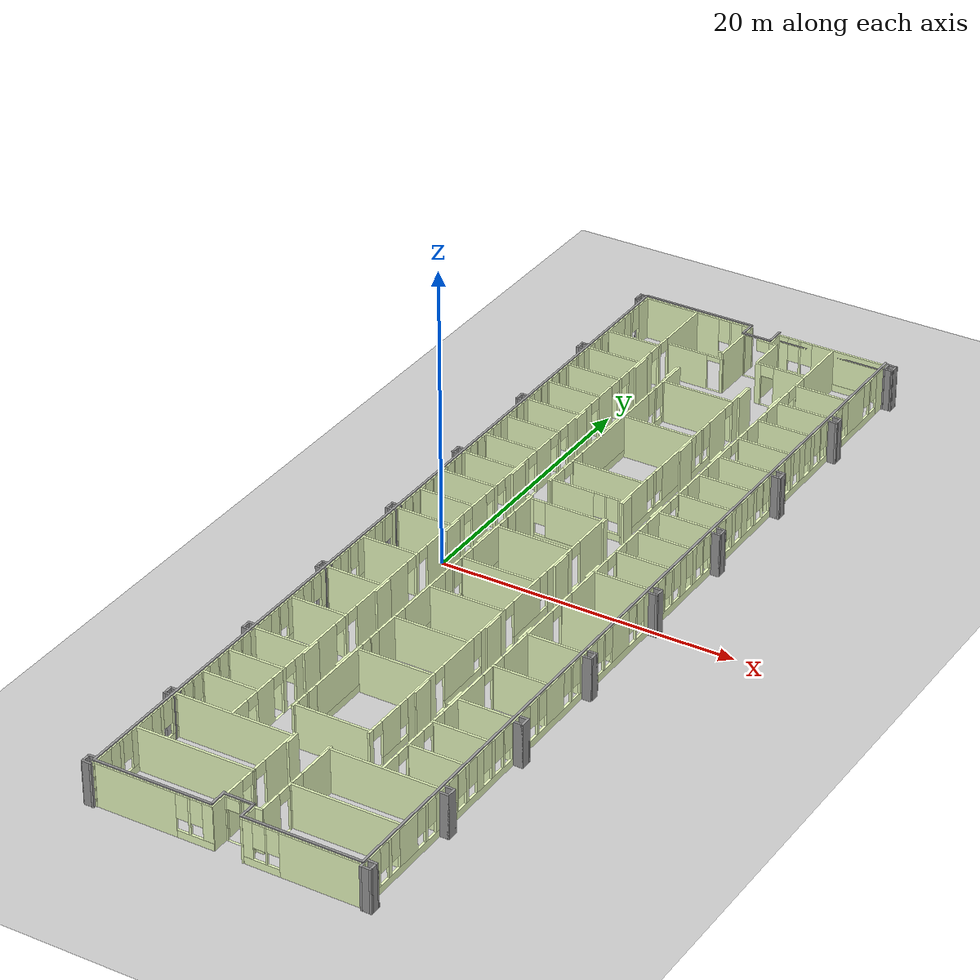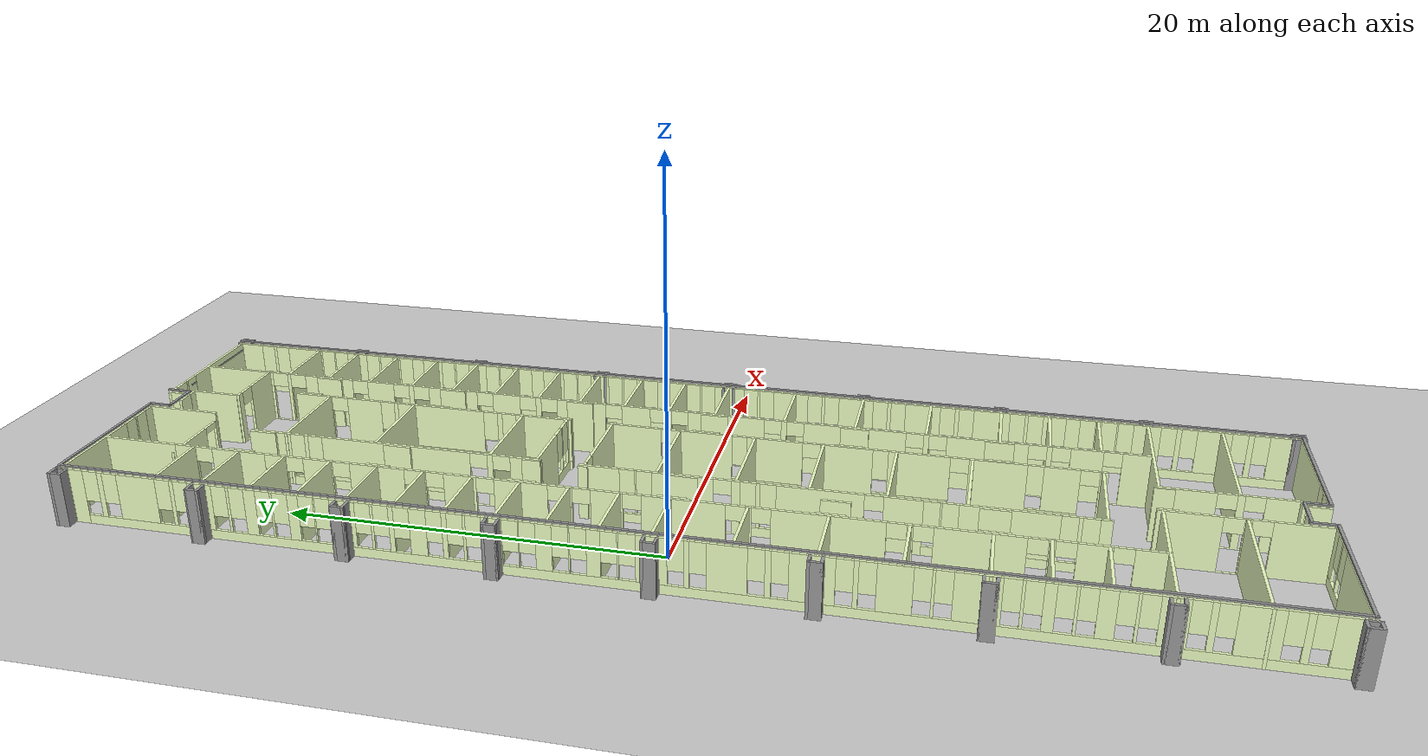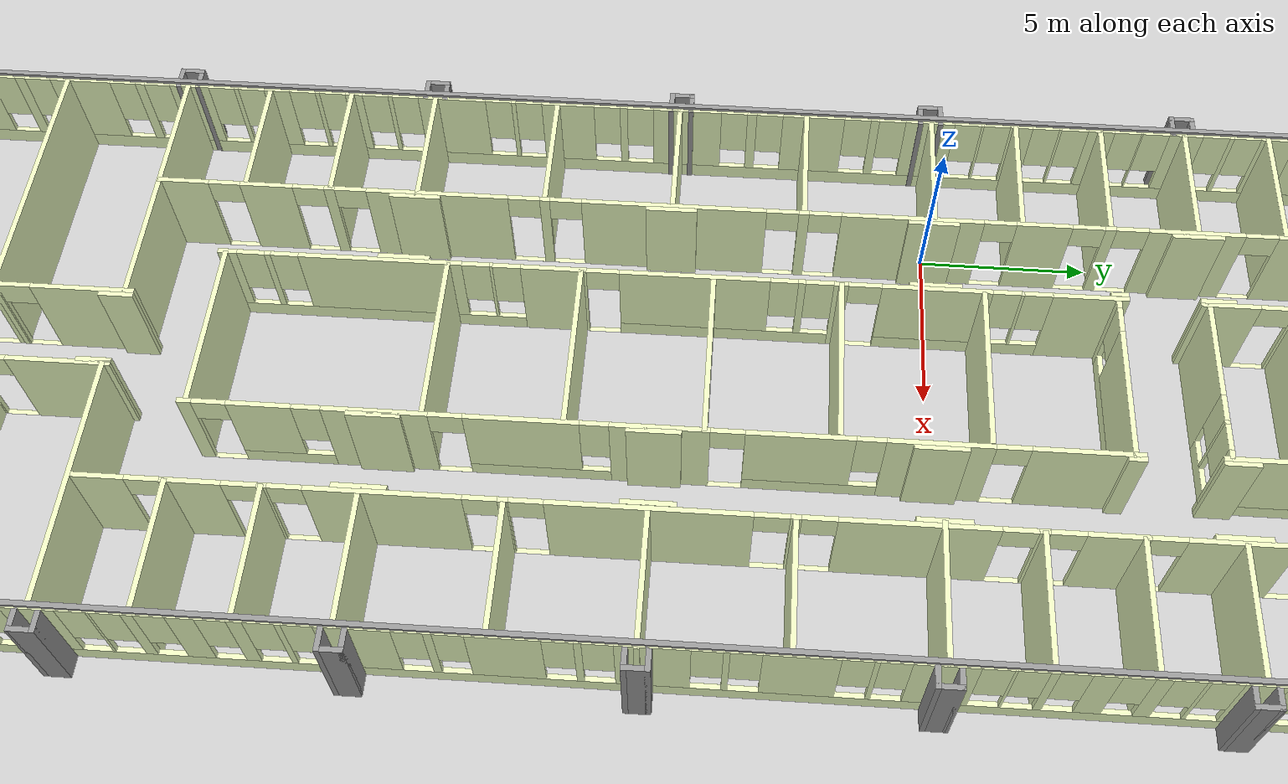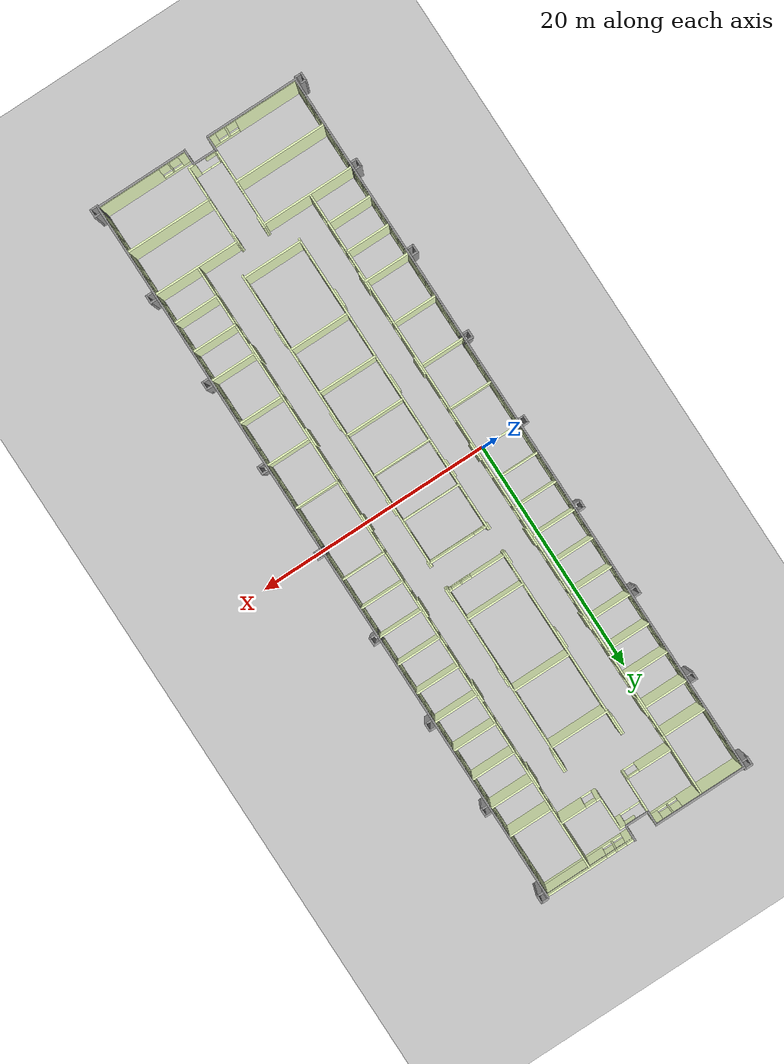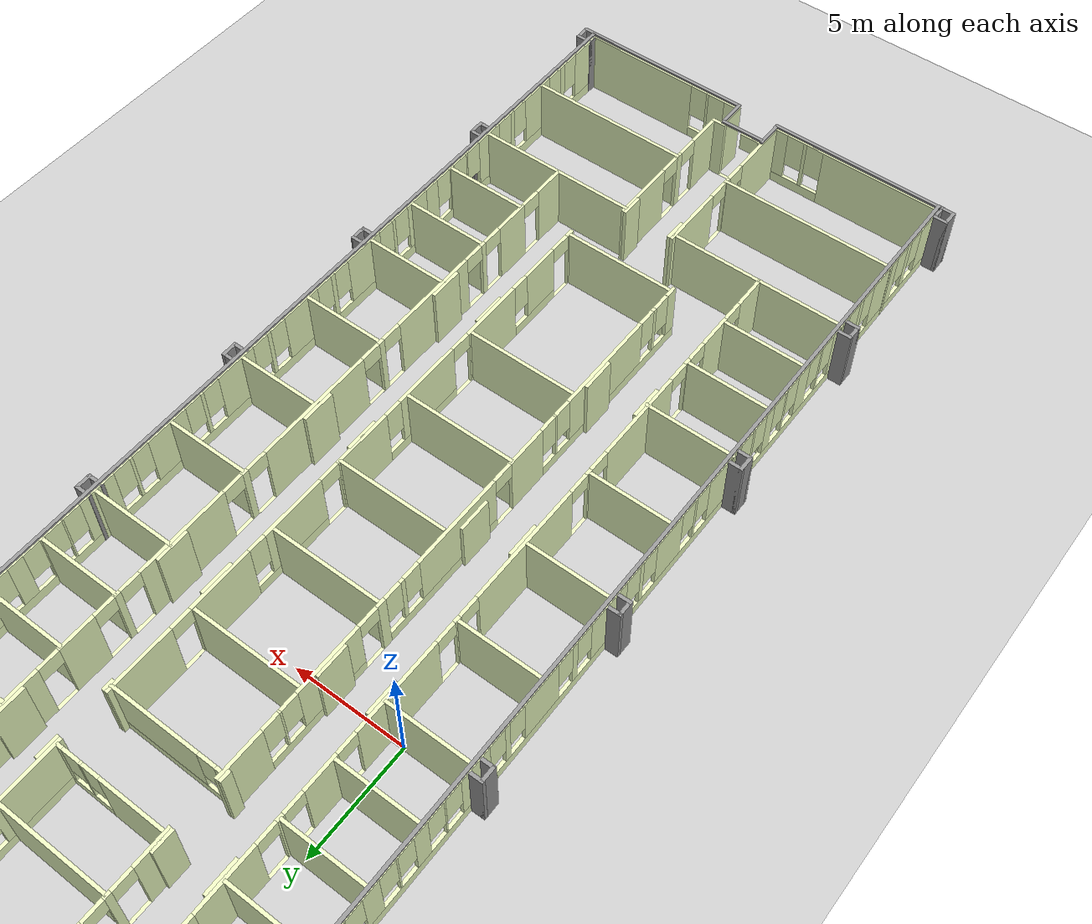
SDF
<sdf version='1.6'>
  <world name='default'>

    <gui fullscreen='0'>
      <camera name='user_camera'>
        <pose frame=''>0.036397 -1.29075 62.3037 3.14159 1.54159 3.14159</pose>
        <view_controller>orbit</view_controller>
        <projection_type>perspective</projection_type>
      </camera>
    </gui>

    <gravity>0 0 -9.81</gravity>
    <magnetic_field>6e-06 2.3e-05 -4.2e-05</magnetic_field>
    <atmosphere type='adiabatic'/>
    <physics name='default_physics' default='0' type='ode'>
      <max_step_size>0.001</max_step_size>
      <real_time_factor>1</real_time_factor>
      <real_time_update_rate>1000</real_time_update_rate>
    </physics>

    <scene>
      <ambient>0.4 0.4 0.4 1</ambient>
      <background>0.7 0.7 0.7 1</background>
      <shadows>1</shadows>
    </scene>

    <spherical_coordinates>
      <surface_model>EARTH_WGS84</surface_model>
      <latitude_deg>0</latitude_deg>
      <longitude_deg>0</longitude_deg>
      <elevation>0</elevation>
      <heading_deg>0</heading_deg>
    </spherical_coordinates>

    <light name='sun' type='directional'>
      <cast_shadows>1</cast_shadows>
      <pose frame=''>0 0 10 0 -0 0</pose>
      <diffuse>0.8 0.8 0.8 1</diffuse>
      <specular>0.1 0.1 0.1 1</specular>
      <attenuation>
        <range>1000</range>
        <constant>0.9</constant>
        <linear>0.01</linear>
        <quadratic>0.001</quadratic>
      </attenuation>
      <direction>-0.5 0.5 -1</direction>
    </light>

    <model name='ground_plane'>
      <static>1</static>
      <link name='link'>
        <collision name='collision'>
          <geometry>
            <plane>
              <normal>0 0 1</normal>
              <size>100 100</size>
            </plane>
          </geometry>
          <surface>
            <friction>
              <ode>
                <mu>100</mu>
                <mu2>50</mu2>
              </ode>
              <torsional>
                <ode/>
              </torsional>
            </friction>
            <contact>
              <ode/>
            </contact>
            <bounce/>
          </surface>
          <max_contacts>10</max_contacts>
        </collision>
        <visual name='visual'>
          <cast_shadows>0</cast_shadows>
          <geometry>
            <plane>
              <normal>0 0 1</normal>
              <size>100 100</size>
            </plane>
          </geometry>
          <material>
            <script>
              <uri>file://media/materials/scripts/gazebo.material</uri>
              <name>Gazebo/Grey</name>
            </script>
          </material>
        </visual>
        <self_collide>0</self_collide>
        <kinematic>0</kinematic>
        <gravity>1</gravity>
      </link>
    </model>

    <include>
        <uri>model://worlds/models/predio73</uri>
    </include>

  </world>
</sdf>

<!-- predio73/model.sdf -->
<sdf version='1.6'>
  <model name='default'>
    <pose frame=''>5.59913 0.021219 0 0 -0 0</pose>
    <link name='Wall_0'>
      <pose frame=''>8.76787 -0.005219 0 0 0 -1.5708</pose>
      <visual name='Wall_0_Visual_0'>
        <pose frame=''>-30.019 0 1.48 0 -0 0</pose>
        <geometry>
          <box>
            <size>1.47999 0.15 2.96</size>
          </box>
        </geometry>
        <material>
          <script>
            <uri>file://media/materials/scripts/gazebo.material</uri>
            <name>Gazebo/Grey</name>
          </script>
          <ambient>0.929412 1 0.760784 1</ambient>
        </material>
        <meta>
          <layer>0</layer>
        </meta>
      </visual>
      <collision name='Wall_0_Collision_0'>
        <geometry>
          <box>
            <size>1.47999 0.15 2.96</size>
          </box>
        </geometry>
        <pose frame=''>-30.019 0 1.48 0 -0 0</pose>
      </collision>
      <visual name='Wall_0_Visual_1'>
        <pose frame=''>0.739993 0 0.25 0 -0 0</pose>
        <geometry>
          <box>
            <size>60.038 0.15 0.5</size>
          </box>
        </geometry>
        <material>
          <script>
            <uri>file://media/materials/scripts/gazebo.material</uri>
            <name>Gazebo/Grey</name>
          </script>
          <ambient>0.929412 1 0.760784 1</ambient>
        </material>
        <meta>
          <layer>0</layer>
        </meta>
      </visual>
      <collision name='Wall_0_Collision_1'>
        <geometry>
          <box>
            <size>60.038 0.15 0.5</size>
          </box>
        </geometry>
        <pose frame=''>0.739993 0 0.25 0 -0 0</pose>
      </collision>
      <visual name='Wall_0_Visual_2'>
        <pose frame=''>-28.3968 0 1.73 0 -0 0</pose>
        <geometry>
          <box>
            <size>0.164493 0.15 2.46</size>
          </box>
        </geometry>
        <material>
          <script>
            <uri>file://media/materials/scripts/gazebo.material</uri>
            <name>Gazebo/Grey</name>
          </script>
          <ambient>0.929412 1 0.760784 1</ambient>
        </material>
        <meta>
          <layer>0</layer>
        </meta>
      </visual>
      <collision name='Wall_0_Collision_2'>
        <geometry>
          <box>
            <size>0.164493 0.15 2.46</size>
          </box>
        </geometry>
        <pose frame=''>-28.3968 0 1.73 0 -0 0</pose>
      </collision>
      <visual name='Wall_0_Visual_3'>
        <pose frame=''>-26.3939 0 1.73 0 -0 0</pose>
        <geometry>
          <box>
            <size>2.24127 0.15 2.46</size>
          </box>
        </geometry>
        <material>
          <script>
            <uri>file://media/materials/scripts/gazebo.material</uri>
            <name>Gazebo/Grey</name>
          </script>
          <ambient>0.929412 1 0.760784 1</ambient>
        </material>
        <meta>
          <layer>0</layer>
        </meta>
      </visual>
      <collision name='Wall_0_Collision_3'>
        <geometry>
          <box>
            <size>2.24127 0.15 2.46</size>
          </box>
        </geometry>
        <pose frame=''>-26.3939 0 1.73 0 -0 0</pose>
      </collision>
      <visual name='Wall_0_Visual_4'>
        <pose frame=''>-24.4354 0 1.73 0 -0 0</pose>
        <geometry>
          <box>
            <size>0.07574 0.15 2.46</size>
          </box>
        </geometry>
        <material>
          <script>
            <uri>file://media/materials/scripts/gazebo.material</uri>
            <name>Gazebo/Grey</name>
          </script>
          <ambient>0.929412 1 0.760784 1</ambient>
        </material>
        <meta>
          <layer>0</layer>
        </meta>
      </visual>
      <collision name='Wall_0_Collision_4'>
        <geometry>
          <box>
            <size>0.07574 0.15 2.46</size>
          </box>
        </geometry>
        <pose frame=''>-24.4354 0 1.73 0 -0 0</pose>
      </collision>
      <visual name='Wall_0_Visual_5'>
        <pose frame=''>-22.9721 0 1.73 0 -0 0</pose>
        <geometry>
          <box>
            <size>1.25079 0.15 2.46</size>
          </box>
        </geometry>
        <material>
          <script>
            <uri>file://media/materials/scripts/gazebo.material</uri>
            <name>Gazebo/Grey</name>
          </script>
          <ambient>0.929412 1 0.760784 1</ambient>
        </material>
        <meta>
          <layer>0</layer>
        </meta>
      </visual>
      <collision name='Wall_0_Collision_5'>
        <geometry>
          <box>
            <size>1.25079 0.15 2.46</size>
          </box>
        </geometry>
        <pose frame=''>-22.9721 0 1.73 0 -0 0</pose>
      </collision>
      <visual name='Wall_0_Visual_6'>
        <pose frame=''>-21.4946 0 1.73 0 -0 0</pose>
        <geometry>
          <box>
            <size>0.104211 0.15 2.46</size>
          </box>
        </geometry>
        <material>
          <script>
            <uri>file://media/materials/scripts/gazebo.material</uri>
            <name>Gazebo/Grey</name>
          </script>
          <ambient>0.929412 1 0.760784 1</ambient>
        </material>
        <meta>
          <layer>0</layer>
        </meta>
      </visual>
      <collision name='Wall_0_Collision_6'>
        <geometry>
          <box>
            <size>0.104211 0.15 2.46</size>
          </box>
        </geometry>
        <pose frame=''>-21.4946 0 1.73 0 -0 0</pose>
      </collision>
      <visual name='Wall_0_Visual_7'>
        <pose frame=''>-20.4096 0 1.73 0 -0 0</pose>
        <geometry>
          <box>
            <size>0.465896 0.15 2.46</size>
          </box>
        </geometry>
        <material>
          <script>
            <uri>file://media/materials/scripts/gazebo.material</uri>
            <name>Gazebo/Grey</name>
          </script>
          <ambient>0.929412 1 0.760784 1</ambient>
        </material>
        <meta>
          <layer>0</layer>
        </meta>
      </visual>
      <collision name='Wall_0_Collision_7'>
        <geometry>
          <box>
            <size>0.465896 0.15 2.46</size>
          </box>
        </geometry>
        <pose frame=''>-20.4096 0 1.73 0 -0 0</pose>
      </collision>
      <visual name='Wall_0_Visual_8'>
        <pose frame=''>-19.0231 0 1.73 0 -0 0</pose>
        <geometry>
          <box>
            <size>0.707017 0.15 2.46</size>
          </box>
        </geometry>
        <material>
          <script>
            <uri>file://media/materials/scripts/gazebo.material</uri>
            <name>Gazebo/Grey</name>
          </script>
          <ambient>0.929412 1 0.760784 1</ambient>
        </material>
        <meta>
          <layer>0</layer>
        </meta>
      </visual>
      <collision name='Wall_0_Collision_8'>
        <geometry>
          <box>
            <size>0.707017 0.15 2.46</size>
          </box>
        </geometry>
        <pose frame=''>-19.0231 0 1.73 0 -0 0</pose>
      </collision>
      <visual name='Wall_0_Visual_9'>
        <pose frame=''>-17.6819 0 1.73 0 -0 0</pose>
        <geometry>
          <box>
            <size>0.375476 0.15 2.46</size>
          </box>
        </geometry>
        <material>
          <script>
            <uri>file://media/materials/scripts/gazebo.material</uri>
            <name>Gazebo/Grey</name>
          </script>
          <ambient>0.929412 1 0.760784 1</ambient>
        </material>
        <meta>
          <layer>0</layer>
        </meta>
      </visual>
      <collision name='Wall_0_Collision_9'>
        <geometry>
          <box>
            <size>0.375476 0.15 2.46</size>
          </box>
        </geometry>
        <pose frame=''>-17.6819 0 1.73 0 -0 0</pose>
      </collision>
      <visual name='Wall_0_Visual_10'>
        <pose frame=''>-16.642 0 1.73 0 -0 0</pose>
        <geometry>
          <box>
            <size>0.104211 0.15 2.46</size>
          </box>
        </geometry>
        <material>
          <script>
            <uri>file://media/materials/scripts/gazebo.material</uri>
            <name>Gazebo/Grey</name>
          </script>
          <ambient>0.929412 1 0.760784 1</ambient>
        </material>
        <meta>
          <layer>0</layer>
        </meta>
      </visual>
      <collision name='Wall_0_Collision_10'>
        <geometry>
          <box>
            <size>0.104211 0.15 2.46</size>
          </box>
        </geometry>
        <pose frame=''>-16.642 0 1.73 0 -0 0</pose>
      </collision>
      <visual name='Wall_0_Visual_11'>
        <pose frame=''>-15.2405 0 1.73 0 -0 0</pose>
        <geometry>
          <box>
            <size>1.09884 0.15 2.46</size>
          </box>
        </geometry>
        <material>
          <script>
            <uri>file://media/materials/scripts/gazebo.material</uri>
            <name>Gazebo/Grey</name>
          </script>
          <ambient>0.929412 1 0.760784 1</ambient>
        </material>
        <meta>
          <layer>0</layer>
        </meta>
      </visual>
      <collision name='Wall_0_Collision_11'>
        <geometry>
          <box>
            <size>1.09884 0.15 2.46</size>
          </box>
        </geometry>
        <pose frame=''>-15.2405 0 1.73 0 -0 0</pose>
      </collision>
      <visual name='Wall_0_Visual_12'>
        <pose frame=''>-13.854 0 1.73 0 -0 0</pose>
        <geometry>
          <box>
            <size>0.07407 0.15 2.46</size>
          </box>
        </geometry>
        <material>
          <script>
            <uri>file://media/materials/scripts/gazebo.material</uri>
            <name>Gazebo/Grey</name>
          </script>
          <ambient>0.929412 1 0.760784 1</ambient>
        </material>
        <meta>
          <layer>0</layer>
        </meta>
      </visual>
      <collision name='Wall_0_Collision_12'>
        <geometry>
          <box>
            <size>0.07407 0.15 2.46</size>
          </box>
        </geometry>
        <pose frame=''>-13.854 0 1.73 0 -0 0</pose>
      </collision>
      <visual name='Wall_0_Visual_13'>
        <pose frame=''>-12.8293 0 1.73 0 -0 0</pose>
        <geometry>
          <box>
            <size>0.375475 0.15 2.46</size>
          </box>
        </geometry>
        <material>
          <script>
            <uri>file://media/materials/scripts/gazebo.material</uri>
            <name>Gazebo/Grey</name>
          </script>
          <ambient>0.929412 1 0.760784 1</ambient>
        </material>
        <meta>
          <layer>0</layer>
        </meta>
      </visual>
      <collision name='Wall_0_Collision_13'>
        <geometry>
          <box>
            <size>0.375475 0.15 2.46</size>
          </box>
        </geometry>
        <pose frame=''>-12.8293 0 1.73 0 -0 0</pose>
      </collision>
      <visual name='Wall_0_Visual_14'>
        <pose frame=''>-11.4729 0 1.73 0 -0 0</pose>
        <geometry>
          <box>
            <size>0.737159 0.15 2.46</size>
          </box>
        </geometry>
        <material>
          <script>
            <uri>file://media/materials/scripts/gazebo.material</uri>
            <name>Gazebo/Grey</name>
          </script>
          <ambient>0.929412 1 0.760784 1</ambient>
        </material>
        <meta>
          <layer>0</layer>
        </meta>
      </visual>
      <collision name='Wall_0_Collision_14'>
        <geometry>
          <box>
            <size>0.737159 0.15 2.46</size>
          </box>
        </geometry>
        <pose frame=''>-11.4729 0 1.73 0 -0 0</pose>
      </collision>
      <visual name='Wall_0_Visual_15'>
        <pose frame=''>-10.0865 0 1.73 0 -0 0</pose>
        <geometry>
          <box>
            <size>0.435756 0.15 2.46</size>
          </box>
        </geometry>
        <material>
          <script>
            <uri>file://media/materials/scripts/gazebo.material</uri>
            <name>Gazebo/Grey</name>
          </script>
          <ambient>0.929412 1 0.760784 1</ambient>
        </material>
        <meta>
          <layer>0</layer>
        </meta>
      </visual>
      <collision name='Wall_0_Collision_15'>
        <geometry>
          <box>
            <size>0.435756 0.15 2.46</size>
          </box>
        </geometry>
        <pose frame=''>-10.0865 0 1.73 0 -0 0</pose>
      </collision>
      <visual name='Wall_0_Visual_16'>
        <pose frame=''>-9.03157 0 1.73 0 -0 0</pose>
        <geometry>
          <box>
            <size>0.07407 0.15 2.46</size>
          </box>
        </geometry>
        <material>
          <script>
            <uri>file://media/materials/scripts/gazebo.material</uri>
            <name>Gazebo/Grey</name>
          </script>
          <ambient>0.929412 1 0.760784 1</ambient>
        </material>
        <meta>
          <layer>0</layer>
        </meta>
      </visual>
      <collision name='Wall_0_Collision_16'>
        <geometry>
          <box>
            <size>0.07407 0.15 2.46</size>
          </box>
        </geometry>
        <pose frame=''>-9.03157 0 1.73 0 -0 0</pose>
      </collision>
      <visual name='Wall_0_Visual_17'>
        <pose frame=''>-7.66018 0 1.73 0 -0 0</pose>
        <geometry>
          <box>
            <size>1.0687 0.15 2.46</size>
          </box>
        </geometry>
        <material>
          <script>
            <uri>file://media/materials/scripts/gazebo.material</uri>
            <name>Gazebo/Grey</name>
          </script>
          <ambient>0.929412 1 0.760784 1</ambient>
        </material>
        <meta>
          <layer>0</layer>
        </meta>
      </visual>
      <collision name='Wall_0_Collision_17'>
        <geometry>
          <box>
            <size>1.0687 0.15 2.46</size>
          </box>
        </geometry>
        <pose frame=''>-7.66018 0 1.73 0 -0 0</pose>
      </collision>
      <visual name='Wall_0_Visual_18'>
        <pose frame=''>-6.27372 0 1.73 0 -0 0</pose>
        <geometry>
          <box>
            <size>0.104212 0.15 2.46</size>
          </box>
        </geometry>
        <material>
          <script>
            <uri>file://media/materials/scripts/gazebo.material</uri>
            <name>Gazebo/Grey</name>
          </script>
          <ambient>0.929412 1 0.760784 1</ambient>
        </material>
        <meta>
          <layer>0</layer>
        </meta>
      </visual>
      <collision name='Wall_0_Collision_18'>
        <geometry>
          <box>
            <size>0.104212 0.15 2.46</size>
          </box>
        </geometry>
        <pose frame=''>-6.27372 0 1.73 0 -0 0</pose>
      </collision>
      <visual name='Wall_0_Visual_19'>
        <pose frame=''>-5.20374 0 1.73 0 -0 0</pose>
        <geometry>
          <box>
            <size>0.435755 0.15 2.46</size>
          </box>
        </geometry>
        <material>
          <script>
            <uri>file://media/materials/scripts/gazebo.material</uri>
            <name>Gazebo/Grey</name>
          </script>
          <ambient>0.929412 1 0.760784 1</ambient>
        </material>
        <meta>
          <layer>0</layer>
        </meta>
      </visual>
      <collision name='Wall_0_Collision_19'>
        <geometry>
          <box>
            <size>0.435755 0.15 2.46</size>
          </box>
        </geometry>
        <pose frame=''>-5.20374 0 1.73 0 -0 0</pose>
      </collision>
      <visual name='Wall_0_Visual_20'>
        <pose frame=''>-3.83235 0 1.73 0 -0 0</pose>
        <geometry>
          <box>
            <size>0.707019 0.15 2.46</size>
          </box>
        </geometry>
        <material>
          <script>
            <uri>file://media/materials/scripts/gazebo.material</uri>
            <name>Gazebo/Grey</name>
          </script>
          <ambient>0.929412 1 0.760784 1</ambient>
        </material>
        <meta>
          <layer>0</layer>
        </meta>
      </visual>
      <collision name='Wall_0_Collision_20'>
        <geometry>
          <box>
            <size>0.707019 0.15 2.46</size>
          </box>
        </geometry>
        <pose frame=''>-3.83235 0 1.73 0 -0 0</pose>
      </collision>
      <visual name='Wall_0_Visual_21'>
        <pose frame=''>-2.56646 0 1.73 0 -0 0</pose>
        <geometry>
          <box>
            <size>0.224773 0.15 2.46</size>
          </box>
        </geometry>
        <material>
          <script>
            <uri>file://media/materials/scripts/gazebo.material</uri>
            <name>Gazebo/Grey</name>
          </script>
          <ambient>0.929412 1 0.760784 1</ambient>
        </material>
        <meta>
          <layer>0</layer>
        </meta>
      </visual>
      <collision name='Wall_0_Collision_21'>
        <geometry>
          <box>
            <size>0.224773 0.15 2.46</size>
          </box>
        </geometry>
        <pose frame=''>-2.56646 0 1.73 0 -0 0</pose>
      </collision>
      <visual name='Wall_0_Visual_22'>
        <pose frame=''>-1.61704 0 1.73 0 -0 0</pose>
        <geometry>
          <box>
            <size>0.074071 0.15 2.46</size>
          </box>
        </geometry>
        <material>
          <script>
            <uri>file://media/materials/scripts/gazebo.material</uri>
            <name>Gazebo/Grey</name>
          </script>
          <ambient>0.929412 1 0.760784 1</ambient>
        </material>
        <meta>
          <layer>0</layer>
        </meta>
      </visual>
      <collision name='Wall_0_Collision_22'>
        <geometry>
          <box>
            <size>0.074071 0.15 2.46</size>
          </box>
        </geometry>
        <pose frame=''>-1.61704 0 1.73 0 -0 0</pose>
      </collision>
      <visual name='Wall_0_Visual_23'>
        <pose frame=''>0.055756 0 1.73 0 -0 0</pose>
        <geometry>
          <box>
            <size>1.67151 0.15 2.46</size>
          </box>
        </geometry>
        <material>
          <script>
            <uri>file://media/materials/scripts/gazebo.material</uri>
            <name>Gazebo/Grey</name>
          </script>
          <ambient>0.929412 1 0.760784 1</ambient>
        </material>
        <meta>
          <layer>0</layer>
        </meta>
      </visual>
      <collision name='Wall_0_Collision_23'>
        <geometry>
          <box>
            <size>1.67151 0.15 2.46</size>
          </box>
        </geometry>
        <pose frame=''>0.055756 0 1.73 0 -0 0</pose>
      </collision>
      <visual name='Wall_0_Visual_24'>
        <pose frame=''>1.75869 0 1.73 0 -0 0</pose>
        <geometry>
          <box>
            <size>0.134352 0.15 2.46</size>
          </box>
        </geometry>
        <material>
          <script>
            <uri>file://media/materials/scripts/gazebo.material</uri>
            <name>Gazebo/Grey</name>
          </script>
          <ambient>0.929412 1 0.760784 1</ambient>
        </material>
        <meta>
          <layer>0</layer>
        </meta>
      </visual>
      <collision name='Wall_0_Collision_24'>
        <geometry>
          <box>
            <size>0.134352 0.15 2.46</size>
          </box>
        </geometry>
        <pose frame=''>1.75869 0 1.73 0 -0 0</pose>
      </collision>
      <visual name='Wall_0_Visual_25'>
        <pose frame=''>3.59725 0 1.73 0 -0 0</pose>
        <geometry>
          <box>
            <size>1.94277 0.15 2.46</size>
          </box>
        </geometry>
        <material>
          <script>
            <uri>file://media/materials/scripts/gazebo.material</uri>
            <name>Gazebo/Grey</name>
          </script>
          <ambient>0.929412 1 0.760784 1</ambient>
        </material>
        <meta>
          <layer>0</layer>
        </meta>
      </visual>
      <collision name='Wall_0_Collision_25'>
        <geometry>
          <box>
            <size>1.94277 0.15 2.46</size>
          </box>
        </geometry>
        <pose frame=''>3.59725 0 1.73 0 -0 0</pose>
      </collision>
      <visual name='Wall_0_Visual_26'>
        <pose frame=''>5.45088 0 1.73 0 -0 0</pose>
        <geometry>
          <box>
            <size>0.164492 0.15 2.46</size>
          </box>
        </geometry>
        <material>
          <script>
            <uri>file://media/materials/scripts/gazebo.material</uri>
            <name>Gazebo/Grey</name>
          </script>
          <ambient>0.929412 1 0.760784 1</ambient>
        </material>
        <meta>
          <layer>0</layer>
        </meta>
      </visual>
      <collision name='Wall_0_Collision_26'>
        <geometry>
          <box>
            <size>0.164492 0.15 2.46</size>
          </box>
        </geometry>
        <pose frame=''>5.45088 0 1.73 0 -0 0</pose>
      </collision>
      <visual name='Wall_0_Visual_27'>
        <pose frame=''>7.28945 0 1.73 0 -0 0</pose>
        <geometry>
          <box>
            <size>1.91263 0.15 2.46</size>
          </box>
        </geometry>
        <material>
          <script>
            <uri>file://media/materials/scripts/gazebo.material</uri>
            <name>Gazebo/Grey</name>
          </script>
          <ambient>0.929412 1 0.760784 1</ambient>
        </material>
        <meta>
          <layer>0</layer>
        </meta>
      </visual>
      <collision name='Wall_0_Collision_27'>
        <geometry>
          <box>
            <size>1.91263 0.15 2.46</size>
          </box>
        </geometry>
        <pose frame=''>7.28945 0 1.73 0 -0 0</pose>
      </collision>
      <visual name='Wall_0_Visual_28'>
        <pose frame=''>9.14308 0 1.73 0 -0 0</pose>
        <geometry>
          <box>
            <size>0.194632 0.15 2.46</size>
          </box>
        </geometry>
        <material>
          <script>
            <uri>file://media/materials/scripts/gazebo.material</uri>
            <name>Gazebo/Grey</name>
          </script>
          <ambient>0.929412 1 0.760784 1</ambient>
        </material>
        <meta>
          <layer>0</layer>
        </meta>
      </visual>
      <collision name='Wall_0_Collision_28'>
        <geometry>
          <box>
            <size>0.194632 0.15 2.46</size>
          </box>
        </geometry>
        <pose frame=''>9.14308 0 1.73 0 -0 0</pose>
      </collision>
      <visual name='Wall_0_Visual_29'>
        <pose frame=''>10.9967 0 1.73 0 -0 0</pose>
        <geometry>
          <box>
            <size>1.91263 0.15 2.46</size>
          </box>
        </geometry>
        <material>
          <script>
            <uri>file://media/materials/scripts/gazebo.material</uri>
            <name>Gazebo/Grey</name>
          </script>
          <ambient>0.929412 1 0.760784 1</ambient>
        </material>
        <meta>
          <layer>0</layer>
        </meta>
      </visual>
      <collision name='Wall_0_Collision_29'>
        <geometry>
          <box>
            <size>1.91263 0.15 2.46</size>
          </box>
        </geometry>
        <pose frame=''>10.9967 0 1.73 0 -0 0</pose>
      </collision>
      <visual name='Wall_0_Visual_30'>
        <pose frame=''>12.8654 0 1.73 0 -0 0</pose>
        <geometry>
          <box>
            <size>0.224773 0.15 2.46</size>
          </box>
        </geometry>
        <material>
          <script>
            <uri>file://media/materials/scripts/gazebo.material</uri>
            <name>Gazebo/Grey</name>
          </script>
          <ambient>0.929412 1 0.760784 1</ambient>
        </material>
        <meta>
          <layer>0</layer>
        </meta>
      </visual>
      <collision name='Wall_0_Collision_30'>
        <geometry>
          <box>
            <size>0.224773 0.15 2.46</size>
          </box>
        </geometry>
        <pose frame=''>12.8654 0 1.73 0 -0 0</pose>
      </collision>
      <visual name='Wall_0_Visual_31'>
        <pose frame=''>14.7492 0 1.73 0 -0 0</pose>
        <geometry>
          <box>
            <size>1.94277 0.15 2.46</size>
          </box>
        </geometry>
        <material>
          <script>
            <uri>file://media/materials/scripts/gazebo.material</uri>
            <name>Gazebo/Grey</name>
          </script>
          <ambient>0.929412 1 0.760784 1</ambient>
        </material>
        <meta>
          <layer>0</layer>
        </meta>
      </visual>
      <collision name='Wall_0_Collision_31'>
        <geometry>
          <box>
            <size>1.94277 0.15 2.46</size>
          </box>
        </geometry>
        <pose frame=''>14.7492 0 1.73 0 -0 0</pose>
      </collision>
      <visual name='Wall_0_Visual_32'>
        <pose frame=''>16.6028 0 1.73 0 -0 0</pose>
        <geometry>
          <box>
            <size>0.164493 0.15 2.46</size>
          </box>
        </geometry>
        <material>
          <script>
            <uri>file://media/materials/scripts/gazebo.material</uri>
            <name>Gazebo/Grey</name>
          </script>
          <ambient>0.929412 1 0.760784 1</ambient>
        </material>
        <meta>
          <layer>0</layer>
        </meta>
      </visual>
      <collision name='Wall_0_Collision_32'>
        <geometry>
          <box>
            <size>0.164493 0.15 2.46</size>
          </box>
        </geometry>
        <pose frame=''>16.6028 0 1.73 0 -0 0</pose>
      </collision>
      <visual name='Wall_0_Visual_33'>
        <pose frame=''>17.6879 0 1.73 0 -0 0</pose>
        <geometry>
          <box>
            <size>0.405614 0.15 2.46</size>
          </box>
        </geometry>
        <material>
          <script>
            <uri>file://media/materials/scripts/gazebo.material</uri>
            <name>Gazebo/Grey</name>
          </script>
          <ambient>0.929412 1 0.760784 1</ambient>
        </material>
        <meta>
          <layer>0</layer>
        </meta>
      </visual>
      <collision name='Wall_0_Collision_33'>
        <geometry>
          <box>
            <size>0.405614 0.15 2.46</size>
          </box>
        </geometry>
        <pose frame=''>17.6879 0 1.73 0 -0 0</pose>
      </collision>
      <visual name='Wall_0_Visual_34'>
        <pose frame=''>19.0593 0 1.73 0 -0 0</pose>
        <geometry>
          <box>
            <size>0.737159 0.15 2.46</size>
          </box>
        </geometry>
        <material>
          <script>
            <uri>file://media/materials/scripts/gazebo.material</uri>
            <name>Gazebo/Grey</name>
          </script>
          <ambient>0.929412 1 0.760784 1</ambient>
        </material>
        <meta>
          <layer>0</layer>
        </meta>
      </visual>
      <collision name='Wall_0_Collision_34'>
        <geometry>
          <box>
            <size>0.737159 0.15 2.46</size>
          </box>
        </geometry>
        <pose frame=''>19.0593 0 1.73 0 -0 0</pose>
      </collision>
      <visual name='Wall_0_Visual_35'>
        <pose frame=''>20.3854 0 1.73 0 -0 0</pose>
        <geometry>
          <box>
            <size>0.315194 0.15 2.46</size>
          </box>
        </geometry>
        <material>
          <script>
            <uri>file://media/materials/scripts/gazebo.material</uri>
            <name>Gazebo/Grey</name>
          </script>
          <ambient>0.929412 1 0.760784 1</ambient>
        </material>
        <meta>
          <layer>0</layer>
        </meta>
      </visual>
      <collision name='Wall_0_Collision_35'>
        <geometry>
          <box>
            <size>0.315194 0.15 2.46</size>
          </box>
        </geometry>
        <pose frame=''>20.3854 0 1.73 0 -0 0</pose>
      </collision>
      <visual name='Wall_0_Visual_36'>
        <pose frame=''>21.3801 0 1.73 0 -0 0</pose>
        <geometry>
          <box>
            <size>0.074071 0.15 2.46</size>
          </box>
        </geometry>
        <material>
          <script>
            <uri>file://media/materials/scripts/gazebo.material</uri>
            <name>Gazebo/Grey</name>
          </script>
          <ambient>0.929412 1 0.760784 1</ambient>
        </material>
        <meta>
          <layer>0</layer>
        </meta>
      </visual>
      <collision name='Wall_0_Collision_36'>
        <geometry>
          <box>
            <size>0.074071 0.15 2.46</size>
          </box>
        </geometry>
        <pose frame=''>21.3801 0 1.73 0 -0 0</pose>
      </collision>
      <visual name='Wall_0_Visual_37'>
        <pose frame=''>22.9172 0 1.73 0 -0 0</pose>
        <geometry>
          <box>
            <size>1.40025 0.15 2.46</size>
          </box>
        </geometry>
        <material>
          <script>
            <uri>file://media/materials/scripts/gazebo.material</uri>
            <name>Gazebo/Grey</name>
          </script>
          <ambient>0.929412 1 0.760784 1</ambient>
        </material>
        <meta>
          <layer>0</layer>
        </meta>
      </visual>
      <collision name='Wall_0_Collision_37'>
        <geometry>
          <box>
            <size>1.40025 0.15 2.46</size>
          </box>
        </geometry>
        <pose frame=''>22.9172 0 1.73 0 -0 0</pose>
      </collision>
      <visual name='Wall_0_Visual_38'>
        <pose frame=''>24.5448 0 1.73 0 -0 0</pose>
        <geometry>
          <box>
            <size>0.254914 0.15 2.46</size>
          </box>
        </geometry>
        <material>
          <script>
            <uri>file://media/materials/scripts/gazebo.material</uri>
            <name>Gazebo/Grey</name>
          </script>
          <ambient>0.929412 1 0.760784 1</ambient>
        </material>
        <meta>
          <layer>0</layer>
        </meta>
      </visual>
      <collision name='Wall_0_Collision_38'>
        <geometry>
          <box>
            <size>0.254914 0.15 2.46</size>
          </box>
        </geometry>
        <pose frame=''>24.5448 0 1.73 0 -0 0</pose>
      </collision>
      <visual name='Wall_0_Visual_39'>
        <pose frame=''>26.3532 0 1.73 0 -0 0</pose>
        <geometry>
          <box>
            <size>1.76193 0.15 2.46</size>
          </box>
        </geometry>
        <material>
          <script>
            <uri>file://media/materials/scripts/gazebo.material</uri>
            <name>Gazebo/Grey</name>
          </script>
          <ambient>0.929412 1 0.760784 1</ambient>
        </material>
        <meta>
          <layer>0</layer>
        </meta>
      </visual>
      <collision name='Wall_0_Collision_39'>
        <geometry>
          <box>
            <size>1.76193 0.15 2.46</size>
          </box>
        </geometry>
        <pose frame=''>26.3532 0 1.73 0 -0 0</pose>
      </collision>
      <visual name='Wall_0_Visual_40'>
        <pose frame=''>28.1767 0 1.73 0 -0 0</pose>
        <geometry>
          <box>
            <size>0.285052 0.15 2.46</size>
          </box>
        </geometry>
        <material>
          <script>
            <uri>file://media/materials/scripts/gazebo.material</uri>
            <name>Gazebo/Grey</name>
          </script>
          <ambient>0.929412 1 0.760784 1</ambient>
        </material>
        <meta>
          <layer>0</layer>
        </meta>
      </visual>
      <collision name='Wall_0_Collision_40'>
        <geometry>
          <box>
            <size>0.285052 0.15 2.46</size>
          </box>
        </geometry>
        <pose frame=''>28.1767 0 1.73 0 -0 0</pose>
      </collision>
      <visual name='Wall_0_Visual_41'>
        <pose frame=''>29.9391 0 1.73 0 -0 0</pose>
        <geometry>
          <box>
            <size>1.63974 0.15 2.46</size>
          </box>
        </geometry>
        <material>
          <script>
            <uri>file://media/materials/scripts/gazebo.material</uri>
            <name>Gazebo/Grey</name>
          </script>
          <ambient>0.929412 1 0.760784 1</ambient>
        </material>
        <meta>
          <layer>0</layer>
        </meta>
      </visual>
      <collision name='Wall_0_Collision_41'>
        <geometry>
          <box>
            <size>1.63974 0.15 2.46</size>
          </box>
        </geometry>
        <pose frame=''>29.9391 0 1.73 0 -0 0</pose>
      </collision>
      <visual name='Wall_0_Visual_42'>
        <pose frame=''>-28.879 0 2.13 0 -0 0</pose>
        <geometry>
          <box>
            <size>0.8 0.15 1.66</size>
          </box>
        </geometry>
        <material>
          <script>
            <uri>file://media/materials/scripts/gazebo.material</uri>
            <name>Gazebo/Grey</name>
          </script>
          <ambient>0.929412 1 0.760784 1</ambient>
        </material>
        <meta>
          <layer>0</layer>
        </meta>
      </visual>
      <collision name='Wall_0_Collision_42'>
        <geometry>
          <box>
            <size>0.8 0.15 1.66</size>
          </box>
        </geometry>
        <pose frame=''>-28.879 0 2.13 0 -0 0</pose>
      </collision>
      <visual name='Wall_0_Visual_43'>
        <pose frame=''>-27.9145 0 2.13 0 -0 0</pose>
        <geometry>
          <box>
            <size>0.8 0.15 1.66</size>
          </box>
        </geometry>
        <material>
          <script>
            <uri>file://media/materials/scripts/gazebo.material</uri>
            <name>Gazebo/Grey</name>
          </script>
          <ambient>0.929412 1 0.760784 1</ambient>
        </material>
        <meta>
          <layer>0</layer>
        </meta>
      </visual>
      <collision name='Wall_0_Collision_43'>
        <geometry>
          <box>
            <size>0.8 0.15 1.66</size>
          </box>
        </geometry>
        <pose frame=''>-27.9145 0 2.13 0 -0 0</pose>
      </collision>
      <visual name='Wall_0_Visual_44'>
        <pose frame=''>-24.8732 0 2.13 0 -0 0</pose>
        <geometry>
          <box>
            <size>0.8 0.15 1.66</size>
          </box>
        </geometry>
        <material>
          <script>
            <uri>file://media/materials/scripts/gazebo.material</uri>
            <name>Gazebo/Grey</name>
          </script>
          <ambient>0.929412 1 0.760784 1</ambient>
        </material>
        <meta>
          <layer>0</layer>
        </meta>
      </visual>
      <collision name='Wall_0_Collision_44'>
        <geometry>
          <box>
            <size>0.8 0.15 1.66</size>
          </box>
        </geometry>
        <pose frame=''>-24.8732 0 2.13 0 -0 0</pose>
      </collision>
      <visual name='Wall_0_Visual_45'>
        <pose frame=''>-23.9975 0 2.13 0 -0 0</pose>
        <geometry>
          <box>
            <size>0.8 0.15 1.66</size>
          </box>
        </geometry>
        <material>
          <script>
            <uri>file://media/materials/scripts/gazebo.material</uri>
            <name>Gazebo/Grey</name>
          </script>
          <ambient>0.929412 1 0.760784 1</ambient>
        </material>
        <meta>
          <layer>0</layer>
        </meta>
      </visual>
      <collision name='Wall_0_Collision_45'>
        <geometry>
          <box>
            <size>0.8 0.15 1.66</size>
          </box>
        </geometry>
        <pose frame=''>-23.9975 0 2.13 0 -0 0</pose>
      </collision>
      <visual name='Wall_0_Visual_46'>
        <pose frame=''>-21.9467 0 2.13 0 -0 0</pose>
        <geometry>
          <box>
            <size>0.8 0.15 1.66</size>
          </box>
        </geometry>
        <material>
          <script>
            <uri>file://media/materials/scripts/gazebo.material</uri>
            <name>Gazebo/Grey</name>
          </script>
          <ambient>0.929412 1 0.760784 1</ambient>
        </material>
        <meta>
          <layer>0</layer>
        </meta>
      </visual>
      <collision name='Wall_0_Collision_46'>
        <geometry>
          <box>
            <size>0.8 0.15 1.66</size>
          </box>
        </geometry>
        <pose frame=''>-21.9467 0 2.13 0 -0 0</pose>
      </collision>
      <visual name='Wall_0_Visual_47'>
        <pose frame=''>-21.0425 0 2.13 0 -0 0</pose>
        <geometry>
          <box>
            <size>0.8 0.15 1.66</size>
          </box>
        </geometry>
        <material>
          <script>
            <uri>file://media/materials/scripts/gazebo.material</uri>
            <name>Gazebo/Grey</name>
          </script>
          <ambient>0.929412 1 0.760784 1</ambient>
        </material>
        <meta>
          <layer>0</layer>
        </meta>
      </visual>
      <collision name='Wall_0_Collision_47'>
        <geometry>
          <box>
            <size>0.8 0.15 1.66</size>
          </box>
        </geometry>
        <pose frame=''>-21.0425 0 2.13 0 -0 0</pose>
      </collision>
      <visual name='Wall_0_Visual_48'>
        <pose frame=''>-19.7766 0 2.13 0 -0 0</pose>
        <geometry>
          <box>
            <size>0.8 0.15 1.66</size>
          </box>
        </geometry>
        <material>
          <script>
            <uri>file://media/materials/scripts/gazebo.material</uri>
            <name>Gazebo/Grey</name>
          </script>
          <ambient>0.929412 1 0.760784 1</ambient>
        </material>
        <meta>
          <layer>0</layer>
        </meta>
      </visual>
      <collision name='Wall_0_Collision_48'>
        <geometry>
          <box>
            <size>0.8 0.15 1.66</size>
          </box>
        </geometry>
        <pose frame=''>-19.7766 0 2.13 0 -0 0</pose>
      </collision>
      <visual name='Wall_0_Visual_49'>
        <pose frame=''>-18.2696 0 2.13 0 -0 0</pose>
        <geometry>
          <box>
            <size>0.8 0.15 1.66</size>
          </box>
        </geometry>
        <material>
          <script>
            <uri>file://media/materials/scripts/gazebo.material</uri>
            <name>Gazebo/Grey</name>
          </script>
          <ambient>0.929412 1 0.760784 1</ambient>
        </material>
        <meta>
          <layer>0</layer>
        </meta>
      </visual>
      <collision name='Wall_0_Collision_49'>
        <geometry>
          <box>
            <size>0.8 0.15 1.66</size>
          </box>
        </geometry>
        <pose frame=''>-18.2696 0 2.13 0 -0 0</pose>
      </collision>
      <visual name='Wall_0_Visual_50'>
        <pose frame=''>-17.0941 0 2.13 0 -0 0</pose>
        <geometry>
          <box>
            <size>0.8 0.15 1.66</size>
          </box>
        </geometry>
        <material>
          <script>
            <uri>file://media/materials/scripts/gazebo.material</uri>
            <name>Gazebo/Grey</name>
          </script>
          <ambient>0.929412 1 0.760784 1</ambient>
        </material>
        <meta>
          <layer>0</layer>
        </meta>
      </visual>
      <collision name='Wall_0_Collision_50'>
        <geometry>
          <box>
            <size>0.8 0.15 1.66</size>
          </box>
        </geometry>
        <pose frame=''>-17.0941 0 2.13 0 -0 0</pose>
      </collision>
      <visual name='Wall_0_Visual_51'>
        <pose frame=''>-16.1899 0 2.13 0 -0 0</pose>
        <geometry>
          <box>
            <size>0.8 0.15 1.66</size>
          </box>
        </geometry>
        <material>
          <script>
            <uri>file://media/materials/scripts/gazebo.material</uri>
            <name>Gazebo/Grey</name>
          </script>
          <ambient>0.929412 1 0.760784 1</ambient>
        </material>
        <meta>
          <layer>0</layer>
        </meta>
      </visual>
      <collision name='Wall_0_Collision_51'>
        <geometry>
          <box>
            <size>0.8 0.15 1.66</size>
          </box>
        </geometry>
        <pose frame=''>-16.1899 0 2.13 0 -0 0</pose>
      </collision>
      <visual name='Wall_0_Visual_52'>
        <pose frame=''>-14.2911 0 2.13 0 -0 0</pose>
        <geometry>
          <box>
            <size>0.8 0.15 1.66</size>
          </box>
        </geometry>
        <material>
          <script>
            <uri>file://media/materials/scripts/gazebo.material</uri>
            <name>Gazebo/Grey</name>
          </script>
          <ambient>0.929412 1 0.760784 1</ambient>
        </material>
        <meta>
          <layer>0</layer>
        </meta>
      </visual>
      <collision name='Wall_0_Collision_52'>
        <geometry>
          <box>
            <size>0.8 0.15 1.66</size>
          </box>
        </geometry>
        <pose frame=''>-14.2911 0 2.13 0 -0 0</pose>
      </collision>
      <visual name='Wall_0_Visual_53'>
        <pose frame=''>-13.417 0 2.13 0 -0 0</pose>
        <geometry>
          <box>
            <size>0.8 0.15 1.66</size>
          </box>
        </geometry>
        <material>
          <script>
            <uri>file://media/materials/scripts/gazebo.material</uri>
            <name>Gazebo/Grey</name>
          </script>
          <ambient>0.929412 1 0.760784 1</ambient>
        </material>
        <meta>
          <layer>0</layer>
        </meta>
      </visual>
      <collision name='Wall_0_Collision_53'>
        <geometry>
          <box>
            <size>0.8 0.15 1.66</size>
          </box>
        </geometry>
        <pose frame=''>-13.417 0 2.13 0 -0 0</pose>
      </collision>
      <visual name='Wall_0_Visual_54'>
        <pose frame=''>-12.2415 0 2.13 0 -0 0</pose>
        <geometry>
          <box>
            <size>0.8 0.15 1.66</size>
          </box>
        </geometry>
        <material>
          <script>
            <uri>file://media/materials/scripts/gazebo.material</uri>
            <name>Gazebo/Grey</name>
          </script>
          <ambient>0.929412 1 0.760784 1</ambient>
        </material>
        <meta>
          <layer>0</layer>
        </meta>
      </visual>
      <collision name='Wall_0_Collision_54'>
        <geometry>
          <box>
            <size>0.8 0.15 1.66</size>
          </box>
        </geometry>
        <pose frame=''>-12.2415 0 2.13 0 -0 0</pose>
      </collision>
      <visual name='Wall_0_Visual_55'>
        <pose frame=''>-10.7044 0 2.13 0 -0 0</pose>
        <geometry>
          <box>
            <size>0.8 0.15 1.66</size>
          </box>
        </geometry>
        <material>
          <script>
            <uri>file://media/materials/scripts/gazebo.material</uri>
            <name>Gazebo/Grey</name>
          </script>
          <ambient>0.929412 1 0.760784 1</ambient>
        </material>
        <meta>
          <layer>0</layer>
        </meta>
      </visual>
      <collision name='Wall_0_Collision_55'>
        <geometry>
          <box>
            <size>0.8 0.15 1.66</size>
          </box>
        </geometry>
        <pose frame=''>-10.7044 0 2.13 0 -0 0</pose>
      </collision>
      <visual name='Wall_0_Visual_56'>
        <pose frame=''>-9.4686 0 2.13 0 -0 0</pose>
        <geometry>
          <box>
            <size>0.8 0.15 1.66</size>
          </box>
        </geometry>
        <material>
          <script>
            <uri>file://media/materials/scripts/gazebo.material</uri>
            <name>Gazebo/Grey</name>
          </script>
          <ambient>0.929412 1 0.760784 1</ambient>
        </material>
        <meta>
          <layer>0</layer>
        </meta>
      </visual>
      <collision name='Wall_0_Collision_56'>
        <geometry>
          <box>
            <size>0.8 0.15 1.66</size>
          </box>
        </geometry>
        <pose frame=''>-9.4686 0 2.13 0 -0 0</pose>
      </collision>
      <visual name='Wall_0_Visual_57'>
        <pose frame=''>-8.59453 0 2.13 0 -0 0</pose>
        <geometry>
          <box>
            <size>0.8 0.15 1.66</size>
          </box>
        </geometry>
        <material>
          <script>
            <uri>file://media/materials/scripts/gazebo.material</uri>
            <name>Gazebo/Grey</name>
          </script>
          <ambient>0.929412 1 0.760784 1</ambient>
        </material>
        <meta>
          <layer>0</layer>
        </meta>
      </visual>
      <collision name='Wall_0_Collision_57'>
        <geometry>
          <box>
            <size>0.8 0.15 1.66</size>
          </box>
        </geometry>
        <pose frame=''>-8.59453 0 2.13 0 -0 0</pose>
      </collision>
      <visual name='Wall_0_Visual_58'>
        <pose frame=''>-6.72583 0 2.13 0 -0 0</pose>
        <geometry>
          <box>
            <size>0.8 0.15 1.66</size>
          </box>
        </geometry>
        <material>
          <script>
            <uri>file://media/materials/scripts/gazebo.material</uri>
            <name>Gazebo/Grey</name>
          </script>
          <ambient>0.929412 1 0.760784 1</ambient>
        </material>
        <meta>
          <layer>0</layer>
        </meta>
      </visual>
      <collision name='Wall_0_Collision_58'>
        <geometry>
          <box>
            <size>0.8 0.15 1.66</size>
          </box>
        </geometry>
        <pose frame=''>-6.72583 0 2.13 0 -0 0</pose>
      </collision>
      <visual name='Wall_0_Visual_59'>
        <pose frame=''>-5.82162 0 2.13 0 -0 0</pose>
        <geometry>
          <box>
            <size>0.8 0.15 1.66</size>
          </box>
        </geometry>
        <material>
          <script>
            <uri>file://media/materials/scripts/gazebo.material</uri>
            <name>Gazebo/Grey</name>
          </script>
          <ambient>0.929412 1 0.760784 1</ambient>
        </material>
        <meta>
          <layer>0</layer>
        </meta>
      </visual>
      <collision name='Wall_0_Collision_59'>
        <geometry>
          <box>
            <size>0.8 0.15 1.66</size>
          </box>
        </geometry>
        <pose frame=''>-5.82162 0 2.13 0 -0 0</pose>
      </collision>
      <visual name='Wall_0_Visual_60'>
        <pose frame=''>-4.58586 0 2.13 0 -0 0</pose>
        <geometry>
          <box>
            <size>0.8 0.15 1.66</size>
          </box>
        </geometry>
        <material>
          <script>
            <uri>file://media/materials/scripts/gazebo.material</uri>
            <name>Gazebo/Grey</name>
          </script>
          <ambient>0.929412 1 0.760784 1</ambient>
        </material>
        <meta>
          <layer>0</layer>
        </meta>
      </visual>
      <collision name='Wall_0_Collision_60'>
        <geometry>
          <box>
            <size>0.8 0.15 1.66</size>
          </box>
        </geometry>
        <pose frame=''>-4.58586 0 2.13 0 -0 0</pose>
      </collision>
      <visual name='Wall_0_Visual_61'>
        <pose frame=''>-3.07884 0 2.13 0 -0 0</pose>
        <geometry>
          <box>
            <size>0.8 0.15 1.66</size>
          </box>
        </geometry>
        <material>
          <script>
            <uri>file://media/materials/scripts/gazebo.material</uri>
            <name>Gazebo/Grey</name>
          </script>
          <ambient>0.929412 1 0.760784 1</ambient>
        </material>
        <meta>
          <layer>0</layer>
        </meta>
      </visual>
      <collision name='Wall_0_Collision_61'>
        <geometry>
          <box>
            <size>0.8 0.15 1.66</size>
          </box>
        </geometry>
        <pose frame=''>-3.07884 0 2.13 0 -0 0</pose>
      </collision>
      <visual name='Wall_0_Visual_62'>
        <pose frame=''>-2.05407 0 2.13 0 -0 0</pose>
        <geometry>
          <box>
            <size>0.8 0.15 1.66</size>
          </box>
        </geometry>
        <material>
          <script>
            <uri>file://media/materials/scripts/gazebo.material</uri>
            <name>Gazebo/Grey</name>
          </script>
          <ambient>0.929412 1 0.760784 1</ambient>
        </material>
        <meta>
          <layer>0</layer>
        </meta>
      </visual>
      <collision name='Wall_0_Collision_62'>
        <geometry>
          <box>
            <size>0.8 0.15 1.66</size>
          </box>
        </geometry>
        <pose frame=''>-2.05407 0 2.13 0 -0 0</pose>
      </collision>
      <visual name='Wall_0_Visual_63'>
        <pose frame=''>-1.18 0 2.13 0 -0 0</pose>
        <geometry>
          <box>
            <size>0.8 0.15 1.66</size>
          </box>
        </geometry>
        <material>
          <script>
            <uri>file://media/materials/scripts/gazebo.material</uri>
            <name>Gazebo/Grey</name>
          </script>
          <ambient>0.929412 1 0.760784 1</ambient>
        </material>
        <meta>
          <layer>0</layer>
        </meta>
      </visual>
      <collision name='Wall_0_Collision_63'>
        <geometry>
          <box>
            <size>0.8 0.15 1.66</size>
          </box>
        </geometry>
        <pose frame=''>-1.18 0 2.13 0 -0 0</pose>
      </collision>
      <visual name='Wall_0_Visual_64'>
        <pose frame=''>1.29151 0 2.13 0 -0 0</pose>
        <geometry>
          <box>
            <size>0.8 0.15 1.66</size>
          </box>
        </geometry>
        <material>
          <script>
            <uri>file://media/materials/scripts/gazebo.material</uri>
            <name>Gazebo/Grey</name>
          </script>
          <ambient>0.929412 1 0.760784 1</ambient>
        </material>
        <meta>
          <layer>0</layer>
        </meta>
      </visual>
      <collision name='Wall_0_Collision_64'>
        <geometry>
          <box>
            <size>0.8 0.15 1.66</size>
          </box>
        </geometry>
        <pose frame=''>1.29151 0 2.13 0 -0 0</pose>
      </collision>
      <visual name='Wall_0_Visual_65'>
        <pose frame=''>2.22586 0 2.13 0 -0 0</pose>
        <geometry>
          <box>
            <size>0.8 0.15 1.66</size>
          </box>
        </geometry>
        <material>
          <script>
            <uri>file://media/materials/scripts/gazebo.material</uri>
            <name>Gazebo/Grey</name>
          </script>
          <ambient>0.929412 1 0.760784 1</ambient>
        </material>
        <meta>
          <layer>0</layer>
        </meta>
      </visual>
      <collision name='Wall_0_Collision_65'>
        <geometry>
          <box>
            <size>0.8 0.15 1.66</size>
          </box>
        </geometry>
        <pose frame=''>2.22586 0 2.13 0 -0 0</pose>
      </collision>
      <visual name='Wall_0_Visual_66'>
        <pose frame=''>4.96864 0 2.13 0 -0 0</pose>
        <geometry>
          <box>
            <size>0.8 0.15 1.66</size>
          </box>
        </geometry>
        <material>
          <script>
            <uri>file://media/materials/scripts/gazebo.material</uri>
            <name>Gazebo/Grey</name>
          </script>
          <ambient>0.929412 1 0.760784 1</ambient>
        </material>
        <meta>
          <layer>0</layer>
        </meta>
      </visual>
      <collision name='Wall_0_Collision_66'>
        <geometry>
          <box>
            <size>0.8 0.15 1.66</size>
          </box>
        </geometry>
        <pose frame=''>4.96864 0 2.13 0 -0 0</pose>
      </collision>
      <visual name='Wall_0_Visual_67'>
        <pose frame=''>5.93313 0 2.13 0 -0 0</pose>
        <geometry>
          <box>
            <size>0.8 0.15 1.66</size>
          </box>
        </geometry>
        <material>
          <script>
            <uri>file://media/materials/scripts/gazebo.material</uri>
            <name>Gazebo/Grey</name>
          </script>
          <ambient>0.929412 1 0.760784 1</ambient>
        </material>
        <meta>
          <layer>0</layer>
        </meta>
      </visual>
      <collision name='Wall_0_Collision_67'>
        <geometry>
          <box>
            <size>0.8 0.15 1.66</size>
          </box>
        </geometry>
        <pose frame=''>5.93313 0 2.13 0 -0 0</pose>
      </collision>
      <visual name='Wall_0_Visual_68'>
        <pose frame=''>8.64576 0 2.13 0 -0 0</pose>
        <geometry>
          <box>
            <size>0.8 0.15 1.66</size>
          </box>
        </geometry>
        <material>
          <script>
            <uri>file://media/materials/scripts/gazebo.material</uri>
            <name>Gazebo/Grey</name>
          </script>
          <ambient>0.929412 1 0.760784 1</ambient>
        </material>
        <meta>
          <layer>0</layer>
        </meta>
      </visual>
      <collision name='Wall_0_Collision_68'>
        <geometry>
          <box>
            <size>0.8 0.15 1.66</size>
          </box>
        </geometry>
        <pose frame=''>8.64576 0 2.13 0 -0 0</pose>
      </collision>
      <visual name='Wall_0_Visual_69'>
        <pose frame=''>9.64039 0 2.13 0 -0 0</pose>
        <geometry>
          <box>
            <size>0.8 0.15 1.66</size>
          </box>
        </geometry>
        <material>
          <script>
            <uri>file://media/materials/scripts/gazebo.material</uri>
            <name>Gazebo/Grey</name>
          </script>
          <ambient>0.929412 1 0.760784 1</ambient>
        </material>
        <meta>
          <layer>0</layer>
        </meta>
      </visual>
      <collision name='Wall_0_Collision_69'>
        <geometry>
          <box>
            <size>0.8 0.15 1.66</size>
          </box>
        </geometry>
        <pose frame=''>9.64039 0 2.13 0 -0 0</pose>
      </collision>
      <visual name='Wall_0_Visual_70'>
        <pose frame=''>12.353 0 2.13 0 -0 0</pose>
        <geometry>
          <box>
            <size>0.8 0.15 1.66</size>
          </box>
        </geometry>
        <material>
          <script>
            <uri>file://media/materials/scripts/gazebo.material</uri>
            <name>Gazebo/Grey</name>
          </script>
          <ambient>0.929412 1 0.760784 1</ambient>
        </material>
        <meta>
          <layer>0</layer>
        </meta>
      </visual>
      <collision name='Wall_0_Collision_70'>
        <geometry>
          <box>
            <size>0.8 0.15 1.66</size>
          </box>
        </geometry>
        <pose frame=''>12.353 0 2.13 0 -0 0</pose>
      </collision>
      <visual name='Wall_0_Visual_71'>
        <pose frame=''>13.3778 0 2.13 0 -0 0</pose>
        <geometry>
          <box>
            <size>0.8 0.15 1.66</size>
          </box>
        </geometry>
        <material>
          <script>
            <uri>file://media/materials/scripts/gazebo.material</uri>
            <name>Gazebo/Grey</name>
          </script>
          <ambient>0.929412 1 0.760784 1</ambient>
        </material>
        <meta>
          <layer>0</layer>
        </meta>
      </visual>
      <collision name='Wall_0_Collision_71'>
        <geometry>
          <box>
            <size>0.8 0.15 1.66</size>
          </box>
        </geometry>
        <pose frame=''>13.3778 0 2.13 0 -0 0</pose>
      </collision>
      <visual name='Wall_0_Visual_72'>
        <pose frame=''>16.1206 0 2.13 0 -0 0</pose>
        <geometry>
          <box>
            <size>0.8 0.15 1.66</size>
          </box>
        </geometry>
        <material>
          <script>
            <uri>file://media/materials/scripts/gazebo.material</uri>
            <name>Gazebo/Grey</name>
          </script>
          <ambient>0.929412 1 0.760784 1</ambient>
        </material>
        <meta>
          <layer>0</layer>
        </meta>
      </visual>
      <collision name='Wall_0_Collision_72'>
        <geometry>
          <box>
            <size>0.8 0.15 1.66</size>
          </box>
        </geometry>
        <pose frame=''>16.1206 0 2.13 0 -0 0</pose>
      </collision>
      <visual name='Wall_0_Visual_73'>
        <pose frame=''>17.0851 0 2.13 0 -0 0</pose>
        <geometry>
          <box>
            <size>0.8 0.15 1.66</size>
          </box>
        </geometry>
        <material>
          <script>
            <uri>file://media/materials/scripts/gazebo.material</uri>
            <name>Gazebo/Grey</name>
          </script>
          <ambient>0.929412 1 0.760784 1</ambient>
        </material>
        <meta>
          <layer>0</layer>
        </meta>
      </visual>
      <collision name='Wall_0_Collision_73'>
        <geometry>
          <box>
            <size>0.8 0.15 1.66</size>
          </box>
        </geometry>
        <pose frame=''>17.0851 0 2.13 0 -0 0</pose>
      </collision>
      <visual name='Wall_0_Visual_74'>
        <pose frame=''>18.2907 0 2.13 0 -0 0</pose>
        <geometry>
          <box>
            <size>0.8 0.15 1.66</size>
          </box>
        </geometry>
        <material>
          <script>
            <uri>file://media/materials/scripts/gazebo.material</uri>
            <name>Gazebo/Grey</name>
          </script>
          <ambient>0.929412 1 0.760784 1</ambient>
        </material>
        <meta>
          <layer>0</layer>
        </meta>
      </visual>
      <collision name='Wall_0_Collision_74'>
        <geometry>
          <box>
            <size>0.8 0.15 1.66</size>
          </box>
        </geometry>
        <pose frame=''>18.2907 0 2.13 0 -0 0</pose>
      </collision>
      <visual name='Wall_0_Visual_75'>
        <pose frame=''>19.8278 0 2.13 0 -0 0</pose>
        <geometry>
          <box>
            <size>0.8 0.15 1.66</size>
          </box>
        </geometry>
        <material>
          <script>
            <uri>file://media/materials/scripts/gazebo.material</uri>
            <name>Gazebo/Grey</name>
          </script>
          <ambient>0.929412 1 0.760784 1</ambient>
        </material>
        <meta>
          <layer>0</layer>
        </meta>
      </visual>
      <collision name='Wall_0_Collision_75'>
        <geometry>
          <box>
            <size>0.8 0.15 1.66</size>
          </box>
        </geometry>
        <pose frame=''>19.8278 0 2.13 0 -0 0</pose>
      </collision>
      <visual name='Wall_0_Visual_76'>
        <pose frame=''>20.943 0 2.13 0 -0 0</pose>
        <geometry>
          <box>
            <size>0.8 0.15 1.66</size>
          </box>
        </geometry>
        <material>
          <script>
            <uri>file://media/materials/scripts/gazebo.material</uri>
            <name>Gazebo/Grey</name>
          </script>
          <ambient>0.929412 1 0.760784 1</ambient>
        </material>
        <meta>
          <layer>0</layer>
        </meta>
      </visual>
      <collision name='Wall_0_Collision_76'>
        <geometry>
          <box>
            <size>0.8 0.15 1.66</size>
          </box>
        </geometry>
        <pose frame=''>20.943 0 2.13 0 -0 0</pose>
      </collision>
      <visual name='Wall_0_Visual_77'>
        <pose frame=''>21.8171 0 2.13 0 -0 0</pose>
        <geometry>
          <box>
            <size>0.8 0.15 1.66</size>
          </box>
        </geometry>
        <material>
          <script>
            <uri>file://media/materials/scripts/gazebo.material</uri>
            <name>Gazebo/Grey</name>
          </script>
          <ambient>0.929412 1 0.760784 1</ambient>
        </material>
        <meta>
          <layer>0</layer>
        </meta>
      </visual>
      <collision name='Wall_0_Collision_77'>
        <geometry>
          <box>
            <size>0.8 0.15 1.66</size>
          </box>
        </geometry>
        <pose frame=''>21.8171 0 2.13 0 -0 0</pose>
      </collision>
      <visual name='Wall_0_Visual_78'>
        <pose frame=''>24.0174 0 2.13 0 -0 0</pose>
        <geometry>
          <box>
            <size>0.8 0.15 1.66</size>
          </box>
        </geometry>
        <material>
          <script>
            <uri>file://media/materials/scripts/gazebo.material</uri>
            <name>Gazebo/Grey</name>
          </script>
          <ambient>0.929412 1 0.760784 1</ambient>
        </material>
        <meta>
          <layer>0</layer>
        </meta>
      </visual>
      <collision name='Wall_0_Collision_78'>
        <geometry>
          <box>
            <size>0.8 0.15 1.66</size>
          </box>
        </geometry>
        <pose frame=''>24.0174 0 2.13 0 -0 0</pose>
      </collision>
      <visual name='Wall_0_Visual_79'>
        <pose frame=''>25.0723 0 2.13 0 -0 0</pose>
        <geometry>
          <box>
            <size>0.8 0.15 1.66</size>
          </box>
        </geometry>
        <material>
          <script>
            <uri>file://media/materials/scripts/gazebo.material</uri>
            <name>Gazebo/Grey</name>
          </script>
          <ambient>0.929412 1 0.760784 1</ambient>
        </material>
        <meta>
          <layer>0</layer>
        </meta>
      </visual>
      <collision name='Wall_0_Collision_79'>
        <geometry>
          <box>
            <size>0.8 0.15 1.66</size>
          </box>
        </geometry>
        <pose frame=''>25.0723 0 2.13 0 -0 0</pose>
      </collision>
      <visual name='Wall_0_Visual_80'>
        <pose frame=''>27.6342 0 2.13 0 -0 0</pose>
        <geometry>
          <box>
            <size>0.8 0.15 1.66</size>
          </box>
        </geometry>
        <material>
          <script>
            <uri>file://media/materials/scripts/gazebo.material</uri>
            <name>Gazebo/Grey</name>
          </script>
          <ambient>0.929412 1 0.760784 1</ambient>
        </material>
        <meta>
          <layer>0</layer>
        </meta>
      </visual>
      <collision name='Wall_0_Collision_80'>
        <geometry>
          <box>
            <size>0.8 0.15 1.66</size>
          </box>
        </geometry>
        <pose frame=''>27.6342 0 2.13 0 -0 0</pose>
      </collision>
      <visual name='Wall_0_Visual_81'>
        <pose frame=''>28.7193 0 2.13 0 -0 0</pose>
        <geometry>
          <box>
            <size>0.8 0.15 1.66</size>
          </box>
        </geometry>
        <material>
          <script>
            <uri>file://media/materials/scripts/gazebo.material</uri>
            <name>Gazebo/Grey</name>
          </script>
          <ambient>0.929412 1 0.760784 1</ambient>
        </material>
        <meta>
          <layer>0</layer>
        </meta>
      </visual>
      <collision name='Wall_0_Collision_81'>
        <geometry>
          <box>
            <size>0.8 0.15 1.66</size>
          </box>
        </geometry>
        <pose frame=''>28.7193 0 2.13 0 -0 0</pose>
      </collision>
    </link>
    <link name='Wall_101'>
      <collision name='Wall_101_Collision'>
        <geometry>
          <box>
            <size>1.5 0.15 2.96</size>
          </box>
        </geometry>
        <pose frame=''>0 0 1.48 0 -0 0</pose>
      </collision>
      <visual name='Wall_101_Visual'>
        <pose frame=''>0 0 1.48 0 -0 0</pose>
        <geometry>
          <box>
            <size>1.5 0.15 2.96</size>
          </box>
        </geometry>
        <material>
          <script>
            <uri>file://media/materials/scripts/gazebo.material</uri>
            <name>Gazebo/Grey</name>
          </script>
          <ambient>0.929412 1 0.760784 1</ambient>
        </material>
        <meta>
          <layer>0</layer>
        </meta>
      </visual>
      <pose frame=''>-2.61913 22.8618 0 0 0 -1.5708</pose>
    </link>
    <link name='Wall_103'>
      <collision name='Wall_103_Collision'>
        <geometry>
          <box>
            <size>1.5 0.15 2.96</size>
          </box>
        </geometry>
        <pose frame=''>0 0 1.48 0 -0 0</pose>
      </collision>
      <visual name='Wall_103_Visual'>
        <pose frame=''>0 0 1.48 0 -0 0</pose>
        <geometry>
          <box>
            <size>1.5 0.15 2.96</size>
          </box>
        </geometry>
        <material>
          <script>
            <uri>file://media/materials/scripts/gazebo.material</uri>
            <name>Gazebo/Grey</name>
          </script>
          <ambient>0.929412 1 0.760784 1</ambient>
        </material>
        <meta>
          <layer>0</layer>
        </meta>
      </visual>
      <pose frame=''>2.64587 22.8868 0 0 0 -1.5708</pose>
    </link>
    <link name='Wall_105'>
      <collision name='Wall_105_Collision'>
        <geometry>
          <box>
            <size>3.75 0.15 2.96</size>
          </box>
        </geometry>
        <pose frame=''>0 0 1.48 0 -0 0</pose>
      </collision>
      <visual name='Wall_105_Visual'>
        <pose frame=''>0 0 1.48 0 -0 0</pose>
        <geometry>
          <box>
            <size>3.75 0.15 2.96</size>
          </box>
        </geometry>
        <material>
          <script>
            <uri>file://media/materials/scripts/gazebo.material</uri>
            <name>Gazebo/Grey</name>
          </script>
          <ambient>0.929412 1 0.760784 1</ambient>
        </material>
        <meta>
          <layer>0</layer>
        </meta>
      </visual>
      <pose frame=''>-6.88513 17.7738 0 0 -0 0</pose>
    </link>
    <link name='Wall_108'>
      <collision name='Wall_108_Collision'>
        <geometry>
          <box>
            <size>3.75 0.15 2.96</size>
          </box>
        </geometry>
        <pose frame=''>0 0 1.48 0 -0 0</pose>
      </collision>
      <visual name='Wall_108_Visual'>
        <pose frame=''>0 0 1.48 0 -0 0</pose>
        <geometry>
          <box>
            <size>3.75 0.15 2.96</size>
          </box>
        </geometry>
        <material>
          <script>
            <uri>file://media/materials/scripts/gazebo.material</uri>
            <name>Gazebo/Grey</name>
          </script>
          <ambient>0.929412 1 0.760784 1</ambient>
        </material>
        <meta>
          <layer>0</layer>
        </meta>
      </visual>
      <pose frame=''>6.83287 20.3518 0 0 -0 0</pose>
    </link>
    <link name='Wall_110'>
      <collision name='Wall_110_Collision'>
        <geometry>
          <box>
            <size>3.75 0.15 2.96</size>
          </box>
        </geometry>
        <pose frame=''>0 0 1.48 0 -0 0</pose>
      </collision>
      <visual name='Wall_110_Visual'>
        <pose frame=''>0 0 1.48 0 -0 0</pose>
        <geometry>
          <box>
            <size>3.75 0.15 2.96</size>
          </box>
        </geometry>
        <material>
          <script>
            <uri>file://media/materials/scripts/gazebo.material</uri>
            <name>Gazebo/Grey</name>
          </script>
          <ambient>0.929412 1 0.760784 1</ambient>
        </material>
        <meta>
          <layer>0</layer>
        </meta>
      </visual>
      <pose frame=''>-6.88513 15.1948 0 0 -0 0</pose>
    </link>
    <link name='Wall_112'>
      <collision name='Wall_112_Collision'>
        <geometry>
          <box>
            <size>3.75 0.15 2.96</size>
          </box>
        </geometry>
        <pose frame=''>0 0 1.48 0 -0 0</pose>
      </collision>
      <visual name='Wall_112_Visual'>
        <pose frame=''>0 0 1.48 0 -0 0</pose>
        <geometry>
          <box>
            <size>3.75 0.15 2.96</size>
          </box>
        </geometry>
        <material>
          <script>
            <uri>file://media/materials/scripts/gazebo.material</uri>
            <name>Gazebo/Grey</name>
          </script>
          <ambient>0.929412 1 0.760784 1</ambient>
        </material>
        <meta>
          <layer>0</layer>
        </meta>
      </visual>
      <pose frame=''>6.85987 15.2218 0 0 -0 0</pose>
    </link>
    <link name='Wall_114'>
      <collision name='Wall_114_Collision'>
        <geometry>
          <box>
            <size>1.25 0.15 2.96</size>
          </box>
        </geometry>
        <pose frame=''>0 0 1.48 0 -0 0</pose>
      </collision>
      <visual name='Wall_114_Visual'>
        <pose frame=''>0 0 1.48 0 -0 0</pose>
        <geometry>
          <box>
            <size>1.25 0.15 2.96</size>
          </box>
        </geometry>
        <material>
          <script>
            <uri>file://media/materials/scripts/gazebo.material</uri>
            <name>Gazebo/Grey</name>
          </script>
          <ambient>0.929412 1 0.760784 1</ambient>
        </material>
        <meta>
          <layer>0</layer>
        </meta>
      </visual>
      <pose frame=''>-4.87113 15.2208 0 0 0 -1.5708</pose>
    </link>
    <link name='Wall_116'>
      <collision name='Wall_116_Collision'>
        <geometry>
          <box>
            <size>1.5 0.15 2.96</size>
          </box>
        </geometry>
        <pose frame=''>0 0 1.48 0 -0 0</pose>
      </collision>
      <visual name='Wall_116_Visual'>
        <pose frame=''>0 0 1.48 0 -0 0</pose>
        <geometry>
          <box>
            <size>1.5 0.15 2.96</size>
          </box>
        </geometry>
        <material>
          <script>
            <uri>file://media/materials/scripts/gazebo.material</uri>
            <name>Gazebo/Grey</name>
          </script>
          <ambient>0.929412 1 0.760784 1</ambient>
        </material>
        <meta>
          <layer>0</layer>
        </meta>
      </visual>
      <pose frame=''>-2.62213 15.2058 0 0 0 -1.5708</pose>
    </link>
    <link name='Wall_118'>
      <collision name='Wall_118_Collision'>
        <geometry>
          <box>
            <size>1.5 0.15 2.96</size>
          </box>
        </geometry>
        <pose frame=''>0 0 1.48 0 -0 0</pose>
      </collision>
      <visual name='Wall_118_Visual'>
        <pose frame=''>0 0 1.48 0 -0 0</pose>
        <geometry>
          <box>
            <size>1.5 0.15 2.96</size>
          </box>
        </geometry>
        <material>
          <script>
            <uri>file://media/materials/scripts/gazebo.material</uri>
            <name>Gazebo/Grey</name>
          </script>
          <ambient>0.929412 1 0.760784 1</ambient>
        </material>
        <meta>
          <layer>0</layer>
        </meta>
      </visual>
      <pose frame=''>2.61787 15.2302 0 0 0 -1.5708</pose>
    </link>
    <link name='Wall_120'>
      <collision name='Wall_120_Collision'>
        <geometry>
          <box>
            <size>1.5 0.15 2.96</size>
          </box>
        </geometry>
        <pose frame=''>0 0 1.48 0 -0 0</pose>
      </collision>
      <visual name='Wall_120_Visual'>
        <pose frame=''>0 0 1.48 0 -0 0</pose>
        <geometry>
          <box>
            <size>1.5 0.15 2.96</size>
          </box>
        </geometry>
        <material>
          <script>
            <uri>file://media/materials/scripts/gazebo.material</uri>
            <name>Gazebo/Grey</name>
          </script>
          <ambient>0.929412 1 0.760784 1</ambient>
        </material>
        <meta>
          <layer>0</layer>
        </meta>
      </visual>
      <pose frame=''>4.84087 15.1778 0 0 0 -1.5708</pose>
    </link>
    <link name='Wall_122'>
      <collision name='Wall_122_Collision'>
        <geometry>
          <box>
            <size>3.75 0.15 2.96</size>
          </box>
        </geometry>
        <pose frame=''>0 0 1.48 0 -0 0</pose>
      </collision>
      <visual name='Wall_122_Visual'>
        <pose frame=''>0 0 1.48 0 -0 0</pose>
        <geometry>
          <box>
            <size>3.75 0.15 2.96</size>
          </box>
        </geometry>
        <material>
          <script>
            <uri>file://media/materials/scripts/gazebo.material</uri>
            <name>Gazebo/Grey</name>
          </script>
          <ambient>0.929412 1 0.760784 1</ambient>
        </material>
        <meta>
          <layer>0</layer>
        </meta>
      </visual>
      <pose frame=''>6.83287 12.6978 0 0 -0 0</pose>
    </link>
    <link name='Wall_124'>
      <collision name='Wall_124_Collision'>
        <geometry>
          <box>
            <size>3.75 0.15 2.96</size>
          </box>
        </geometry>
        <pose frame=''>0 0 1.48 0 -0 0</pose>
      </collision>
      <visual name='Wall_124_Visual'>
        <pose frame=''>0 0 1.48 0 -0 0</pose>
        <geometry>
          <box>
            <size>3.75 0.15 2.96</size>
          </box>
        </geometry>
        <material>
          <script>
            <uri>file://media/materials/scripts/gazebo.material</uri>
            <name>Gazebo/Grey</name>
          </script>
          <ambient>0.929412 1 0.760784 1</ambient>
        </material>
        <meta>
          <layer>0</layer>
        </meta>
      </visual>
      <pose frame=''>-6.88513 12.6978 0 0 -0 0</pose>
    </link>
    <link name='Wall_126'>
      <collision name='Wall_126_Collision'>
        <geometry>
          <box>
            <size>3.75 0.15 2.96</size>
          </box>
        </geometry>
        <pose frame=''>0 0 1.48 0 -0 0</pose>
      </collision>
      <visual name='Wall_126_Visual'>
        <pose frame=''>0 0 1.48 0 -0 0</pose>
        <geometry>
          <box>
            <size>3.75 0.15 2.96</size>
          </box>
        </geometry>
        <material>
          <script>
            <uri>file://media/materials/scripts/gazebo.material</uri>
            <name>Gazebo/Grey</name>
          </script>
          <ambient>0.929412 1 0.760784 1</ambient>
        </material>
        <meta>
          <layer>0</layer>
        </meta>
      </visual>
      <pose frame=''>6.85987 10.1188 0 0 -0 0</pose>
    </link>
    <link name='Wall_128'>
      <collision name='Wall_128_Collision'>
        <geometry>
          <box>
            <size>3.75 0.15 2.96</size>
          </box>
        </geometry>
        <pose frame=''>0 0 1.48 0 -0 0</pose>
      </collision>
      <visual name='Wall_128_Visual'>
        <pose frame=''>0 0 1.48 0 -0 0</pose>
        <geometry>
          <box>
            <size>3.75 0.15 2.96</size>
          </box>
        </geometry>
        <material>
          <script>
            <uri>file://media/materials/scripts/gazebo.material</uri>
            <name>Gazebo/Grey</name>
          </script>
          <ambient>0.929412 1 0.760784 1</ambient>
        </material>
        <meta>
          <layer>0</layer>
        </meta>
      </visual>
      <pose frame=''>-6.88513 7.62278 0 0 -0 0</pose>
    </link>
    <link name='Wall_13'>
      <collision name='Wall_13_Collision'>
        <geometry>
          <box>
            <size>7.25 0.15 2.96</size>
          </box>
        </geometry>
        <pose frame=''>0 0 1.48 0 -0 0</pose>
      </collision>
      <visual name='Wall_13_Visual'>
        <pose frame=''>0 0 1.48 0 -0 0</pose>
        <geometry>
          <box>
            <size>7.25 0.15 2.96</size>
          </box>
        </geometry>
        <material>
          <script>
            <uri>file://media/materials/scripts/gazebo.material</uri>
            <name>Gazebo/Grey</name>
          </script>
          <ambient>0.929412 1 0.760784 1</ambient>
        </material>
        <meta>
          <layer>0</layer>
        </meta>
      </visual>
      <pose frame=''>5.07487 -22.9292 0 0 -0 0</pose>
    </link>
    <link name='Wall_130'>
      <collision name='Wall_130_Collision'>
        <geometry>
          <box>
            <size>1 0.15 2.96</size>
          </box>
        </geometry>
        <pose frame=''>0 0 1.48 0 -0 0</pose>
      </collision>
      <visual name='Wall_130_Visual'>
        <pose frame=''>0 0 1.48 0 -0 0</pose>
        <geometry>
          <box>
            <size>1 0.15 2.96</size>
          </box>
        </geometry>
        <material>
          <script>
            <uri>file://media/materials/scripts/gazebo.material</uri>
            <name>Gazebo/Grey</name>
          </script>
          <ambient>0.929412 1 0.760784 1</ambient>
        </material>
        <meta>
          <layer>0</layer>
        </meta>
      </visual>
      <pose frame=''>2.64587 7.88278 0 0 0 -1.5708</pose>
    </link>
    <link name='Wall_132'>
      <collision name='Wall_132_Collision'>
        <geometry>
          <box>
            <size>1 0.15 2.96</size>
          </box>
        </geometry>
        <pose frame=''>0 0 1.48 0 -0 0</pose>
      </collision>
      <visual name='Wall_132_Visual'>
        <pose frame=''>0 0 1.48 0 -0 0</pose>
        <geometry>
          <box>
            <size>1 0.15 2.96</size>
          </box>
        </geometry>
        <material>
          <script>
            <uri>file://media/materials/scripts/gazebo.material</uri>
            <name>Gazebo/Grey</name>
          </script>
          <ambient>0.929412 1 0.760784 1</ambient>
        </material>
        <meta>
          <layer>0</layer>
        </meta>
      </visual>
      <pose frame=''>-2.59413 7.88278 0 0 0 -1.5708</pose>
    </link>
    <link name='Wall_134'>
      <collision name='Wall_134_Collision'>
        <geometry>
          <box>
            <size>3.75 0.15 2.96</size>
          </box>
        </geometry>
        <pose frame=''>0 0 1.48 0 -0 0</pose>
      </collision>
      <visual name='Wall_134_Visual'>
        <pose frame=''>0 0 1.48 0 -0 0</pose>
        <geometry>
          <box>
            <size>3.75 0.15 2.96</size>
          </box>
        </geometry>
        <material>
          <script>
            <uri>file://media/materials/scripts/gazebo.material</uri>
            <name>Gazebo/Grey</name>
          </script>
          <ambient>0.929412 1 0.760784 1</ambient>
        </material>
        <meta>
          <layer>0</layer>
        </meta>
      </visual>
      <pose frame=''>6.85987 7.67678 0 0 -0 0</pose>
    </link>
    <link name='Wall_136'>
      <collision name='Wall_136_Collision'>
        <geometry>
          <box>
            <size>3.75 0.15 2.96</size>
          </box>
        </geometry>
        <pose frame=''>0 0 1.48 0 -0 0</pose>
      </collision>
      <visual name='Wall_136_Visual'>
        <pose frame=''>0 0 1.48 0 -0 0</pose>
        <geometry>
          <box>
            <size>3.75 0.15 2.96</size>
          </box>
        </geometry>
        <material>
          <script>
            <uri>file://media/materials/scripts/gazebo.material</uri>
            <name>Gazebo/Grey</name>
          </script>
          <ambient>0.929412 1 0.760784 1</ambient>
        </material>
        <meta>
          <layer>0</layer>
        </meta>
      </visual>
      <pose frame=''>-6.88813 5.09778 0 0 -0 0</pose>
    </link>
    <link name='Wall_142'>
      <pose frame=''>-2.51213 -7.60722 0 0 0 -1.5708</pose>
      <visual name='Wall_142_Visual_0'>
        <pose frame=''>-11.9297 0 1.48 0 -0 0</pose>
        <geometry>
          <box>
            <size>2.14059 0.15 2.96</size>
          </box>
        </geometry>
        <material>
          <script>
            <uri>file://media/materials/scripts/gazebo.material</uri>
            <name>Gazebo/Grey</name>
          </script>
          <ambient>0.929412 1 0.760784 1</ambient>
        </material>
        <meta>
          <layer>0</layer>
        </meta>
      </visual>
      <collision name='Wall_142_Collision_0'>
        <geometry>
          <box>
            <size>2.14059 0.15 2.96</size>
          </box>
        </geometry>
        <pose frame=''>-11.9297 0 1.48 0 -0 0</pose>
      </collision>
      <visual name='Wall_142_Visual_1'>
        <pose frame=''>-4.8989 0 1.48 0 -0 0</pose>
        <geometry>
          <box>
            <size>0.419844 0.15 2.96</size>
          </box>
        </geometry>
        <material>
          <script>
            <uri>file://media/materials/scripts/gazebo.material</uri>
            <name>Gazebo/Grey</name>
          </script>
          <ambient>0.929412 1 0.760784 1</ambient>
        </material>
        <meta>
          <layer>0</layer>
        </meta>
      </visual>
      <collision name='Wall_142_Collision_1'>
        <geometry>
          <box>
            <size>0.419844 0.15 2.96</size>
          </box>
        </geometry>
        <pose frame=''>-4.8989 0 1.48 0 -0 0</pose>
      </collision>
      <visual name='Wall_142_Visual_2'>
        <pose frame=''>3.3104 0 1.48 0 -0 0</pose>
        <geometry>
          <box>
            <size>1.8907 0.15 2.96</size>
          </box>
        </geometry>
        <material>
          <script>
            <uri>file://media/materials/scripts/gazebo.material</uri>
            <name>Gazebo/Grey</name>
          </script>
          <ambient>0.929412 1 0.760784 1</ambient>
        </material>
        <meta>
          <layer>0</layer>
        </meta>
      </visual>
      <collision name='Wall_142_Collision_2'>
        <geometry>
          <box>
            <size>1.8907 0.15 2.96</size>
          </box>
        </geometry>
        <pose frame=''>3.3104 0 1.48 0 -0 0</pose>
      </collision>
      <visual name='Wall_142_Visual_3'>
        <pose frame=''>-8.45412 0 0.25 0 -0 0</pose>
        <geometry>
          <box>
            <size>4.81058 0.15 0.5</size>
          </box>
        </geometry>
        <material>
          <script>
            <uri>file://media/materials/scripts/gazebo.material</uri>
            <name>Gazebo/Grey</name>
          </script>
          <ambient>0.929412 1 0.760784 1</ambient>
        </material>
        <meta>
          <layer>0</layer>
        </meta>
      </visual>
      <collision name='Wall_142_Collision_3'>
        <geometry>
          <box>
            <size>4.81058 0.15 0.5</size>
          </box>
        </geometry>
        <pose frame=''>-8.45412 0 0.25 0 -0 0</pose>
      </collision>
      <visual name='Wall_142_Visual_4'>
        <pose frame=''>-1.63197 0 0.25 0 -0 0</pose>
        <geometry>
          <box>
            <size>6.11403 0.15 0.5</size>
          </box>
        </geometry>
        <material>
          <script>
            <uri>file://media/materials/scripts/gazebo.material</uri>
            <name>Gazebo/Grey</name>
          </script>
          <ambient>0.929412 1 0.760784 1</ambient>
        </material>
        <meta>
          <layer>0</layer>
        </meta>
      </visual>
      <collision name='Wall_142_Collision_4'>
        <geometry>
          <box>
            <size>6.11403 0.15 0.5</size>
          </box>
        </geometry>
        <pose frame=''>-1.63197 0 0.25 0 -0 0</pose>
      </collision>
      <visual name='Wall_142_Visual_5'>
        <pose frame=''>8.62787 0 0.25 0 -0 0</pose>
        <geometry>
          <box>
            <size>8.74425 0.15 0.5</size>
          </box>
        </geometry>
        <material>
          <script>
            <uri>file://media/materials/scripts/gazebo.material</uri>
            <name>Gazebo/Grey</name>
          </script>
          <ambient>0.929412 1 0.760784 1</ambient>
        </material>
        <meta>
          <layer>0</layer>
        </meta>
      </visual>
      <collision name='Wall_142_Collision_5'>
        <geometry>
          <box>
            <size>8.74425 0.15 0.5</size>
          </box>
        </geometry>
        <pose frame=''>8.62787 0 0.25 0 -0 0</pose>
      </collision>
      <visual name='Wall_142_Visual_6'>
        <pose frame=''>-6.04883 0 1.48 0 -0 0</pose>
        <geometry>
          <box>
            <size>0.001 0.15 2.96</size>
          </box>
        </geometry>
        <material>
          <script>
            <uri>file://media/materials/scripts/gazebo.material</uri>
            <name>Gazebo/Grey</name>
          </script>
          <ambient>0.929412 1 0.760784 1</ambient>
        </material>
        <meta>
          <layer>0</layer>
        </meta>
      </visual>
      <collision name='Wall_142_Collision_6'>
        <geometry>
          <box>
            <size>0.001 0.15 2.96</size>
          </box>
        </geometry>
        <pose frame=''>-6.04883 0 1.48 0 -0 0</pose>
      </collision>
      <visual name='Wall_142_Visual_7'>
        <pose frame=''>1.89505 0 0 0 -0 0</pose>
        <geometry>
          <box>
            <size>0.94 0.15 0.001</size>
          </box>
        </geometry>
        <material>
          <script>
            <uri>file://media/materials/scripts/gazebo.material</uri>
            <name>Gazebo/Grey</name>
          </script>
          <ambient>0.929412 1 0.760784 1</ambient>
        </material>
        <meta>
          <layer>0</layer>
        </meta>
      </visual>
      <collision name='Wall_142_Collision_7'>
        <geometry>
          <box>
            <size>0.94 0.15 0.001</size>
          </box>
        </geometry>
        <pose frame=''>1.89505 0 0 0 -0 0</pose>
      </collision>
      <visual name='Wall_142_Visual_8'>
        <pose frame=''>-5.57883 0 0 0 -0 0</pose>
        <geometry>
          <box>
            <size>0.94 0.15 0.001</size>
          </box>
        </geometry>
        <material>
          <script>
            <uri>file://media/materials/scripts/gazebo.material</uri>
            <name>Gazebo/Grey</name>
          </script>
          <ambient>0.929412 1 0.760784 1</ambient>
        </material>
        <meta>
          <layer>0</layer>
        </meta>
      </visual>
      <collision name='Wall_142_Collision_8'>
        <geometry>
          <box>
            <size>0.94 0.15 0.001</size>
          </box>
        </geometry>
        <pose frame=''>-5.57883 0 0 0 -0 0</pose>
      </collision>
      <visual name='Wall_142_Visual_9'>
        <pose frame=''>-10.017 0 1.73 0 -0 0</pose>
        <geometry>
          <box>
            <size>0.084906 0.15 2.46</size>
          </box>
        </geometry>
        <material>
          <script>
            <uri>file://media/materials/scripts/gazebo.material</uri>
            <name>Gazebo/Grey</name>
          </script>
          <ambient>0.929412 1 0.760784 1</ambient>
        </material>
        <meta>
          <layer>0</layer>
        </meta>
      </visual>
      <collision name='Wall_142_Collision_9'>
        <geometry>
          <box>
            <size>0.084906 0.15 2.46</size>
          </box>
        </geometry>
        <pose frame=''>-10.017 0 1.73 0 -0 0</pose>
      </collision>
      <visual name='Wall_142_Visual_10'>
        <pose frame=''>-7.61167 0 1.73 0 -0 0</pose>
        <geometry>
          <box>
            <size>3.12568 0.15 2.46</size>
          </box>
        </geometry>
        <material>
          <script>
            <uri>file://media/materials/scripts/gazebo.material</uri>
            <name>Gazebo/Grey</name>
          </script>
          <ambient>0.929412 1 0.760784 1</ambient>
        </material>
        <meta>
          <layer>0</layer>
        </meta>
      </visual>
      <collision name='Wall_142_Collision_10'>
        <geometry>
          <box>
            <size>3.12568 0.15 2.46</size>
          </box>
        </geometry>
        <pose frame=''>-7.61167 0 1.73 0 -0 0</pose>
      </collision>
      <visual name='Wall_142_Visual_11'>
        <pose frame=''>-7.61167 0 1.73 0 -0 0</pose>
        <geometry>
          <box>
            <size>3.12568 0.15 2.46</size>
          </box>
        </geometry>
        <material>
          <script>
            <uri>file://media/materials/scripts/gazebo.material</uri>
            <name>Gazebo/Grey</name>
          </script>
          <ambient>0.929412 1 0.760784 1</ambient>
        </material>
        <meta>
          <layer>0</layer>
        </meta>
      </visual>
      <collision name='Wall_142_Collision_11'>
        <geometry>
          <box>
            <size>3.12568 0.15 2.46</size>
          </box>
        </geometry>
        <pose frame=''>-7.61167 0 1.73 0 -0 0</pose>
      </collision>
      <visual name='Wall_142_Visual_12'>
        <pose frame=''>-3.78674 0 1.73 0 -0 0</pose>
        <geometry>
          <box>
            <size>0.204488 0.15 2.46</size>
          </box>
        </geometry>
        <material>
          <script>
            <uri>file://media/materials/scripts/gazebo.material</uri>
            <name>Gazebo/Grey</name>
          </script>
          <ambient>0.929412 1 0.760784 1</ambient>
        </material>
        <meta>
          <layer>0</layer>
        </meta>
      </visual>
      <collision name='Wall_142_Collision_12'>
        <geometry>
          <box>
            <size>0.204488 0.15 2.46</size>
          </box>
        </geometry>
        <pose frame=''>-3.78674 0 1.73 0 -0 0</pose>
      </collision>
      <visual name='Wall_142_Visual_13'>
        <pose frame=''>-0.729724 0 1.73 0 -0 0</pose>
        <geometry>
          <box>
            <size>4.30954 0.15 2.46</size>
          </box>
        </geometry>
        <material>
          <script>
            <uri>file://media/materials/scripts/gazebo.material</uri>
            <name>Gazebo/Grey</name>
          </script>
          <ambient>0.929412 1 0.760784 1</ambient>
        </material>
        <meta>
          <layer>0</layer>
        </meta>
      </visual>
      <collision name='Wall_142_Collision_13'>
        <geometry>
          <box>
            <size>4.30954 0.15 2.46</size>
          </box>
        </geometry>
        <pose frame=''>-0.729724 0 1.73 0 -0 0</pose>
      </collision>
      <visual name='Wall_142_Visual_14'>
        <pose frame=''>-0.729724 0 1.73 0 -0 0</pose>
        <geometry>
          <box>
            <size>4.30954 0.15 2.46</size>
          </box>
        </geometry>
        <material>
          <script>
            <uri>file://media/materials/scripts/gazebo.material</uri>
            <name>Gazebo/Grey</name>
          </script>
          <ambient>0.929412 1 0.760784 1</ambient>
        </material>
        <meta>
          <layer>0</layer>
        </meta>
      </visual>
      <collision name='Wall_142_Collision_14'>
        <geometry>
          <box>
            <size>4.30954 0.15 2.46</size>
          </box>
        </geometry>
        <pose frame=''>-0.729724 0 1.73 0 -0 0</pose>
      </collision>
      <visual name='Wall_142_Visual_15'>
        <pose frame=''>5.0982 0 1.73 0 -0 0</pose>
        <geometry>
          <box>
            <size>0.084907 0.15 2.46</size>
          </box>
        </geometry>
        <material>
          <script>
            <uri>file://media/materials/scripts/gazebo.material</uri>
            <name>Gazebo/Grey</name>
          </script>
          <ambient>0.929412 1 0.760784 1</ambient>
        </material>
        <meta>
          <layer>0</layer>
        </meta>
      </visual>
      <collision name='Wall_142_Collision_15'>
        <geometry>
          <box>
            <size>0.084907 0.15 2.46</size>
          </box>
        </geometry>
        <pose frame=''>5.0982 0 1.73 0 -0 0</pose>
      </collision>
      <visual name='Wall_142_Visual_16'>
        <pose frame=''>8.303 0 1.73 0 -0 0</pose>
        <geometry>
          <box>
            <size>4.72469 0.15 2.46</size>
          </box>
        </geometry>
        <material>
          <script>
            <uri>file://media/materials/scripts/gazebo.material</uri>
            <name>Gazebo/Grey</name>
          </script>
          <ambient>0.929412 1 0.760784 1</ambient>
        </material>
        <meta>
          <layer>0</layer>
        </meta>
      </visual>
      <collision name='Wall_142_Collision_16'>
        <geometry>
          <box>
            <size>4.72469 0.15 2.46</size>
          </box>
        </geometry>
        <pose frame=''>8.303 0 1.73 0 -0 0</pose>
      </collision>
      <visual name='Wall_142_Visual_17'>
        <pose frame=''>11.5556 0 1.73 0 -0 0</pose>
        <geometry>
          <box>
            <size>0.180572 0.15 2.46</size>
          </box>
        </geometry>
        <material>
          <script>
            <uri>file://media/materials/scripts/gazebo.material</uri>
            <name>Gazebo/Grey</name>
          </script>
          <ambient>0.929412 1 0.760784 1</ambient>
        </material>
        <meta>
          <layer>0</layer>
        </meta>
      </visual>
      <collision name='Wall_142_Collision_17'>
        <geometry>
          <box>
            <size>0.180572 0.15 2.46</size>
          </box>
        </geometry>
        <pose frame=''>11.5556 0 1.73 0 -0 0</pose>
      </collision>
      <visual name='Wall_142_Visual_18'>
        <pose frame=''>12.723 0 1.73 0 -0 0</pose>
        <geometry>
          <box>
            <size>0.55409 0.15 2.46</size>
          </box>
        </geometry>
        <material>
          <script>
            <uri>file://media/materials/scripts/gazebo.material</uri>
            <name>Gazebo/Grey</name>
          </script>
          <ambient>0.929412 1 0.760784 1</ambient>
        </material>
        <meta>
          <layer>0</layer>
        </meta>
      </visual>
      <collision name='Wall_142_Collision_18'>
        <geometry>
          <box>
            <size>0.55409 0.15 2.46</size>
          </box>
        </geometry>
        <pose frame=''>12.723 0 1.73 0 -0 0</pose>
      </collision>
      <visual name='Wall_142_Visual_19'>
        <pose frame=''>-10.4594 0 2.13 0 -0 0</pose>
        <geometry>
          <box>
            <size>0.8 0.15 1.66</size>
          </box>
        </geometry>
        <material>
          <script>
            <uri>file://media/materials/scripts/gazebo.material</uri>
            <name>Gazebo/Grey</name>
          </script>
          <ambient>0.929412 1 0.760784 1</ambient>
        </material>
        <meta>
          <layer>0</layer>
        </meta>
      </visual>
      <collision name='Wall_142_Collision_19'>
        <geometry>
          <box>
            <size>0.8 0.15 1.66</size>
          </box>
        </geometry>
        <pose frame=''>-10.4594 0 2.13 0 -0 0</pose>
      </collision>
      <visual name='Wall_142_Visual_20'>
        <pose frame=''>-4.28898 0 2.13 0 -0 0</pose>
        <geometry>
          <box>
            <size>0.8 0.15 1.66</size>
          </box>
        </geometry>
        <material>
          <script>
            <uri>file://media/materials/scripts/gazebo.material</uri>
            <name>Gazebo/Grey</name>
          </script>
          <ambient>0.929412 1 0.760784 1</ambient>
        </material>
        <meta>
          <layer>0</layer>
        </meta>
      </visual>
      <collision name='Wall_142_Collision_20'>
        <geometry>
          <box>
            <size>0.8 0.15 1.66</size>
          </box>
        </geometry>
        <pose frame=''>-4.28898 0 2.13 0 -0 0</pose>
      </collision>
      <visual name='Wall_142_Visual_21'>
        <pose frame=''>4.65575 0 2.13 0 -0 0</pose>
        <geometry>
          <box>
            <size>0.8 0.15 1.66</size>
          </box>
        </geometry>
        <material>
          <script>
            <uri>file://media/materials/scripts/gazebo.material</uri>
            <name>Gazebo/Grey</name>
          </script>
          <ambient>0.929412 1 0.760784 1</ambient>
        </material>
        <meta>
          <layer>0</layer>
        </meta>
      </visual>
      <collision name='Wall_142_Collision_21'>
        <geometry>
          <box>
            <size>0.8 0.15 1.66</size>
          </box>
        </geometry>
        <pose frame=''>4.65575 0 2.13 0 -0 0</pose>
      </collision>
      <visual name='Wall_142_Visual_22'>
        <pose frame=''>-9.5745 0 2.13 0 -0 0</pose>
        <geometry>
          <box>
            <size>0.8 0.15 1.66</size>
          </box>
        </geometry>
        <material>
          <script>
            <uri>file://media/materials/scripts/gazebo.material</uri>
            <name>Gazebo/Grey</name>
          </script>
          <ambient>0.929412 1 0.760784 1</ambient>
        </material>
        <meta>
          <layer>0</layer>
        </meta>
      </visual>
      <collision name='Wall_142_Collision_22'>
        <geometry>
          <box>
            <size>0.8 0.15 1.66</size>
          </box>
        </geometry>
        <pose frame=''>-9.5745 0 2.13 0 -0 0</pose>
      </collision>
      <visual name='Wall_142_Visual_23'>
        <pose frame=''>-3.28449 0 2.13 0 -0 0</pose>
        <geometry>
          <box>
            <size>0.8 0.15 1.66</size>
          </box>
        </geometry>
        <material>
          <script>
            <uri>file://media/materials/scripts/gazebo.material</uri>
            <name>Gazebo/Grey</name>
          </script>
          <ambient>0.929412 1 0.760784 1</ambient>
        </material>
        <meta>
          <layer>0</layer>
        </meta>
      </visual>
      <collision name='Wall_142_Collision_23'>
        <geometry>
          <box>
            <size>0.8 0.15 1.66</size>
          </box>
        </geometry>
        <pose frame=''>-3.28449 0 2.13 0 -0 0</pose>
      </collision>
      <visual name='Wall_142_Visual_24'>
        <pose frame=''>5.54065 0 2.13 0 -0 0</pose>
        <geometry>
          <box>
            <size>0.8 0.15 1.66</size>
          </box>
        </geometry>
        <material>
          <script>
            <uri>file://media/materials/scripts/gazebo.material</uri>
            <name>Gazebo/Grey</name>
          </script>
          <ambient>0.929412 1 0.760784 1</ambient>
        </material>
        <meta>
          <layer>0</layer>
        </meta>
      </visual>
      <collision name='Wall_142_Collision_24'>
        <geometry>
          <box>
            <size>0.8 0.15 1.66</size>
          </box>
        </geometry>
        <pose frame=''>5.54065 0 2.13 0 -0 0</pose>
      </collision>
      <visual name='Wall_142_Visual_25'>
        <pose frame=''>11.0653 0 2.13 0 -0 0</pose>
        <geometry>
          <box>
            <size>0.8 0.15 1.66</size>
          </box>
        </geometry>
        <material>
          <script>
            <uri>file://media/materials/scripts/gazebo.material</uri>
            <name>Gazebo/Grey</name>
          </script>
          <ambient>0.929412 1 0.760784 1</ambient>
        </material>
        <meta>
          <layer>0</layer>
        </meta>
      </visual>
      <collision name='Wall_142_Collision_25'>
        <geometry>
          <box>
            <size>0.8 0.15 1.66</size>
          </box>
        </geometry>
        <pose frame=''>11.0653 0 2.13 0 -0 0</pose>
      </collision>
      <visual name='Wall_142_Visual_26'>
        <pose frame=''>12.0459 0 2.13 0 -0 0</pose>
        <geometry>
          <box>
            <size>0.8 0.15 1.66</size>
          </box>
        </geometry>
        <material>
          <script>
            <uri>file://media/materials/scripts/gazebo.material</uri>
            <name>Gazebo/Grey</name>
          </script>
          <ambient>0.929412 1 0.760784 1</ambient>
        </material>
        <meta>
          <layer>0</layer>
        </meta>
      </visual>
      <collision name='Wall_142_Collision_26'>
        <geometry>
          <box>
            <size>0.8 0.15 1.66</size>
          </box>
        </geometry>
        <pose frame=''>12.0459 0 2.13 0 -0 0</pose>
      </collision>
      <visual name='Wall_142_Visual_27'>
        <pose frame=''>-5.57883 0 2.555 0 -0 0</pose>
        <geometry>
          <box>
            <size>0.94 0.15 0.81</size>
          </box>
        </geometry>
        <material>
          <script>
            <uri>file://media/materials/scripts/gazebo.material</uri>
            <name>Gazebo/Grey</name>
          </script>
          <ambient>0.929412 1 0.760784 1</ambient>
        </material>
        <meta>
          <layer>0</layer>
        </meta>
      </visual>
      <collision name='Wall_142_Collision_27'>
        <geometry>
          <box>
            <size>0.94 0.15 0.81</size>
          </box>
        </geometry>
        <pose frame=''>-5.57883 0 2.555 0 -0 0</pose>
      </collision>
      <visual name='Wall_142_Visual_28'>
        <pose frame=''>1.89505 0 2.555 0 -0 0</pose>
        <geometry>
          <box>
            <size>0.94 0.15 0.81</size>
          </box>
        </geometry>
        <material>
          <script>
            <uri>file://media/materials/scripts/gazebo.material</uri>
            <name>Gazebo/Grey</name>
          </script>
          <ambient>0.929412 1 0.760784 1</ambient>
        </material>
        <meta>
          <layer>0</layer>
        </meta>
      </visual>
      <collision name='Wall_142_Collision_28'>
        <geometry>
          <box>
            <size>0.94 0.15 0.81</size>
          </box>
        </geometry>
        <pose frame=''>1.89505 0 2.555 0 -0 0</pose>
      </collision>
      <visual name='Wall_142_Visual_29'>
        <pose frame=''>1.89505 0 2.555 0 -0 0</pose>
        <geometry>
          <box>
            <size>0.94 0.15 0.81</size>
          </box>
        </geometry>
        <material>
          <script>
            <uri>file://media/materials/scripts/gazebo.material</uri>
            <name>Gazebo/Grey</name>
          </script>
          <ambient>0.929412 1 0.760784 1</ambient>
        </material>
        <meta>
          <layer>0</layer>
        </meta>
      </visual>
      <collision name='Wall_142_Collision_29'>
        <geometry>
          <box>
            <size>0.94 0.15 0.81</size>
          </box>
        </geometry>
        <pose frame=''>1.89505 0 2.555 0 -0 0</pose>
      </collision>
    </link>
    <link name='Wall_144'>
      <pose frame=''>2.54387 -7.61722 0 0 0 -1.5708</pose>
      <visual name='Wall_144_Visual_0'>
        <pose frame=''>-11.4903 0 1.48 0 -0 0</pose>
        <geometry>
          <box>
            <size>3.01932 0.15 2.96</size>
          </box>
        </geometry>
        <material>
          <script>
            <uri>file://media/materials/scripts/gazebo.material</uri>
            <name>Gazebo/Grey</name>
          </script>
          <ambient>0.929412 1 0.760784 1</ambient>
        </material>
        <meta>
          <layer>0</layer>
        </meta>
      </visual>
      <collision name='Wall_144_Collision_0'>
        <geometry>
          <box>
            <size>3.01932 0.15 2.96</size>
          </box>
        </geometry>
        <pose frame=''>-11.4903 0 1.48 0 -0 0</pose>
      </collision>
      <visual name='Wall_144_Visual_1'>
        <pose frame=''>-7.5871 0 1.48 0 -0 0</pose>
        <geometry>
          <box>
            <size>2.90715 0.15 2.96</size>
          </box>
        </geometry>
        <material>
          <script>
            <uri>file://media/materials/scripts/gazebo.material</uri>
            <name>Gazebo/Grey</name>
          </script>
          <ambient>0.929412 1 0.760784 1</ambient>
        </material>
        <meta>
          <layer>0</layer>
        </meta>
      </visual>
      <collision name='Wall_144_Collision_1'>
        <geometry>
          <box>
            <size>2.90715 0.15 2.96</size>
          </box>
        </geometry>
        <pose frame=''>-7.5871 0 1.48 0 -0 0</pose>
      </collision>
      <visual name='Wall_144_Visual_2'>
        <pose frame=''>-0.077358 0 1.48 0 -0 0</pose>
        <geometry>
          <box>
            <size>2.71582 0.15 2.96</size>
          </box>
        </geometry>
        <material>
          <script>
            <uri>file://media/materials/scripts/gazebo.material</uri>
            <name>Gazebo/Grey</name>
          </script>
          <ambient>0.929412 1 0.760784 1</ambient>
        </material>
        <meta>
          <layer>0</layer>
        </meta>
      </visual>
      <collision name='Wall_144_Collision_2'>
        <geometry>
          <box>
            <size>2.71582 0.15 2.96</size>
          </box>
        </geometry>
        <pose frame=''>-0.077358 0 1.48 0 -0 0</pose>
      </collision>
      <visual name='Wall_144_Visual_3'>
        <pose frame=''>7.62372 0 1.48 0 -0 0</pose>
        <geometry>
          <box>
            <size>2.90715 0.15 2.96</size>
          </box>
        </geometry>
        <material>
          <script>
            <uri>file://media/materials/scripts/gazebo.material</uri>
            <name>Gazebo/Grey</name>
          </script>
          <ambient>0.929412 1 0.760784 1</ambient>
        </material>
        <meta>
          <layer>0</layer>
        </meta>
      </visual>
      <collision name='Wall_144_Collision_3'>
        <geometry>
          <box>
            <size>2.90715 0.15 2.96</size>
          </box>
        </geometry>
        <pose frame=''>7.62372 0 1.48 0 -0 0</pose>
      </collision>
      <visual name='Wall_144_Visual_4'>
        <pose frame=''>12.8018 0 1.48 0 -0 0</pose>
        <geometry>
          <box>
            <size>0.396346 0.15 2.96</size>
          </box>
        </geometry>
        <material>
          <script>
            <uri>file://media/materials/scripts/gazebo.material</uri>
            <name>Gazebo/Grey</name>
          </script>
          <ambient>0.929412 1 0.760784 1</ambient>
        </material>
        <meta>
          <layer>0</layer>
        </meta>
      </visual>
      <collision name='Wall_144_Collision_4'>
        <geometry>
          <box>
            <size>0.396346 0.15 2.96</size>
          </box>
        </geometry>
        <pose frame=''>12.8018 0 1.48 0 -0 0</pose>
      </collision>
      <visual name='Wall_144_Visual_5'>
        <pose frame=''>-9.51068 0 0 0 -0 0</pose>
        <geometry>
          <box>
            <size>0.94 0.15 0.001</size>
          </box>
        </geometry>
        <material>
          <script>
            <uri>file://media/materials/scripts/gazebo.material</uri>
            <name>Gazebo/Grey</name>
          </script>
          <ambient>0.929412 1 0.760784 1</ambient>
        </material>
        <meta>
          <layer>0</layer>
        </meta>
      </visual>
      <collision name='Wall_144_Collision_5'>
        <geometry>
          <box>
            <size>0.94 0.15 0.001</size>
          </box>
        </geometry>
        <pose frame=''>-9.51068 0 0 0 -0 0</pose>
      </collision>
      <visual name='Wall_144_Visual_6'>
        <pose frame=''>-4.2544 0 0.25 0 -0 0</pose>
        <geometry>
          <box>
            <size>3.75826 0.15 0.5</size>
          </box>
        </geometry>
        <material>
          <script>
            <uri>file://media/materials/scripts/gazebo.material</uri>
            <name>Gazebo/Grey</name>
          </script>
          <ambient>0.929412 1 0.760784 1</ambient>
        </material>
        <meta>
          <layer>0</layer>
        </meta>
      </visual>
      <collision name='Wall_144_Collision_6'>
        <geometry>
          <box>
            <size>3.75826 0.15 0.5</size>
          </box>
        </geometry>
        <pose frame=''>-4.2544 0 0.25 0 -0 0</pose>
      </collision>
      <visual name='Wall_144_Visual_7'>
        <pose frame=''>3.25535 0 0.25 0 -0 0</pose>
        <geometry>
          <box>
            <size>3.94959 0.15 0.5</size>
          </box>
        </geometry>
        <material>
          <script>
            <uri>file://media/materials/scripts/gazebo.material</uri>
            <name>Gazebo/Grey</name>
          </script>
          <ambient>0.929412 1 0.760784 1</ambient>
        </material>
        <meta>
          <layer>0</layer>
        </meta>
      </visual>
      <collision name='Wall_144_Collision_7'>
        <geometry>
          <box>
            <size>3.94959 0.15 0.5</size>
          </box>
        </geometry>
        <pose frame=''>3.25535 0 0.25 0 -0 0</pose>
      </collision>
      <visual name='Wall_144_Visual_8'>
        <pose frame=''>10.3705 0 0.25 0 -0 0</pose>
        <geometry>
          <box>
            <size>2.58636 0.15 0.5</size>
          </box>
        </geometry>
        <material>
          <script>
            <uri>file://media/materials/scripts/gazebo.material</uri>
            <name>Gazebo/Grey</name>
          </script>
          <ambient>0.929412 1 0.760784 1</ambient>
        </material>
        <meta>
          <layer>0</layer>
        </meta>
      </visual>
      <collision name='Wall_144_Collision_8'>
        <geometry>
          <box>
            <size>2.58636 0.15 0.5</size>
          </box>
        </geometry>
        <pose frame=''>10.3705 0 0.25 0 -0 0</pose>
      </collision>
      <visual name='Wall_144_Visual_9'>
        <pose frame=''>-1.90527 0 0 0 -0 0</pose>
        <geometry>
          <box>
            <size>0.94 0.15 0.001</size>
          </box>
        </geometry>
        <material>
          <script>
            <uri>file://media/materials/scripts/gazebo.material</uri>
            <name>Gazebo/Grey</name>
          </script>
          <ambient>0.929412 1 0.760784 1</ambient>
        </material>
        <meta>
          <layer>0</layer>
        </meta>
      </visual>
      <collision name='Wall_144_Collision_9'>
        <geometry>
          <box>
            <size>0.94 0.15 0.001</size>
          </box>
        </geometry>
        <pose frame=''>-1.90527 0 0 0 -0 0</pose>
      </collision>
      <visual name='Wall_144_Visual_10'>
        <pose frame=''>5.70015 0 0 0 -0 0</pose>
        <geometry>
          <box>
            <size>0.94 0.15 0.001</size>
          </box>
        </geometry>
        <material>
          <script>
            <uri>file://media/materials/scripts/gazebo.material</uri>
            <name>Gazebo/Grey</name>
          </script>
          <ambient>0.929412 1 0.760784 1</ambient>
        </material>
        <meta>
          <layer>0</layer>
        </meta>
      </visual>
      <collision name='Wall_144_Collision_10'>
        <geometry>
          <box>
            <size>0.94 0.15 0.001</size>
          </box>
        </geometry>
        <pose frame=''>5.70015 0 0 0 -0 0</pose>
      </collision>
      <visual name='Wall_144_Visual_11'>
        <pose frame=''>12.1337 0 0 0 -0 0</pose>
        <geometry>
          <box>
            <size>0.94 0.15 0.001</size>
          </box>
        </geometry>
        <material>
          <script>
            <uri>file://media/materials/scripts/gazebo.material</uri>
            <name>Gazebo/Grey</name>
          </script>
          <ambient>0.929412 1 0.760784 1</ambient>
        </material>
        <meta>
          <layer>0</layer>
        </meta>
      </visual>
      <collision name='Wall_144_Collision_11'>
        <geometry>
          <box>
            <size>0.94 0.15 0.001</size>
          </box>
        </geometry>
        <pose frame=''>12.1337 0 0 0 -0 0</pose>
      </collision>
      <visual name='Wall_144_Visual_12'>
        <pose frame=''>-3.8544 0 1.73 0 -0 0</pose>
        <geometry>
          <box>
            <size>2.95826 0.15 2.46</size>
          </box>
        </geometry>
        <material>
          <script>
            <uri>file://media/materials/scripts/gazebo.material</uri>
            <name>Gazebo/Grey</name>
          </script>
          <ambient>0.929412 1 0.760784 1</ambient>
        </material>
        <meta>
          <layer>0</layer>
        </meta>
      </visual>
      <collision name='Wall_144_Collision_12'>
        <geometry>
          <box>
            <size>2.95826 0.15 2.46</size>
          </box>
        </geometry>
        <pose frame=''>-3.8544 0 1.73 0 -0 0</pose>
      </collision>
      <visual name='Wall_144_Visual_13'>
        <pose frame=''>-3.8544 0 1.73 0 -0 0</pose>
        <geometry>
          <box>
            <size>2.95826 0.15 2.46</size>
          </box>
        </geometry>
        <material>
          <script>
            <uri>file://media/materials/scripts/gazebo.material</uri>
            <name>Gazebo/Grey</name>
          </script>
          <ambient>0.929412 1 0.760784 1</ambient>
        </material>
        <meta>
          <layer>0</layer>
        </meta>
      </visual>
      <collision name='Wall_144_Collision_13'>
        <geometry>
          <box>
            <size>2.95826 0.15 2.46</size>
          </box>
        </geometry>
        <pose frame=''>-3.8544 0 1.73 0 -0 0</pose>
      </collision>
      <visual name='Wall_144_Visual_14'>
        <pose frame=''>3.65535 0 1.73 0 -0 0</pose>
        <geometry>
          <box>
            <size>3.14959 0.15 2.46</size>
          </box>
        </geometry>
        <material>
          <script>
            <uri>file://media/materials/scripts/gazebo.material</uri>
            <name>Gazebo/Grey</name>
          </script>
          <ambient>0.929412 1 0.760784 1</ambient>
        </material>
        <meta>
          <layer>0</layer>
        </meta>
      </visual>
      <collision name='Wall_144_Collision_14'>
        <geometry>
          <box>
            <size>3.14959 0.15 2.46</size>
          </box>
        </geometry>
        <pose frame=''>3.65535 0 1.73 0 -0 0</pose>
      </collision>
      <visual name='Wall_144_Visual_15'>
        <pose frame=''>3.65535 0 1.73 0 -0 0</pose>
        <geometry>
          <box>
            <size>3.14959 0.15 2.46</size>
          </box>
        </geometry>
        <material>
          <script>
            <uri>file://media/materials/scripts/gazebo.material</uri>
            <name>Gazebo/Grey</name>
          </script>
          <ambient>0.929412 1 0.760784 1</ambient>
        </material>
        <meta>
          <layer>0</layer>
        </meta>
      </visual>
      <collision name='Wall_144_Collision_15'>
        <geometry>
          <box>
            <size>3.14959 0.15 2.46</size>
          </box>
        </geometry>
        <pose frame=''>3.65535 0 1.73 0 -0 0</pose>
      </collision>
      <visual name='Wall_144_Visual_16'>
        <pose frame=''>10.7705 0 1.73 0 -0 0</pose>
        <geometry>
          <box>
            <size>1.78636 0.15 2.46</size>
          </box>
        </geometry>
        <material>
          <script>
            <uri>file://media/materials/scripts/gazebo.material</uri>
            <name>Gazebo/Grey</name>
          </script>
          <ambient>0.929412 1 0.760784 1</ambient>
        </material>
        <meta>
          <layer>0</layer>
        </meta>
      </visual>
      <collision name='Wall_144_Collision_16'>
        <geometry>
          <box>
            <size>1.78636 0.15 2.46</size>
          </box>
        </geometry>
        <pose frame=''>10.7705 0 1.73 0 -0 0</pose>
      </collision>
      <visual name='Wall_144_Visual_17'>
        <pose frame=''>-5.73353 0 2.13 0 -0 0</pose>
        <geometry>
          <box>
            <size>0.8 0.15 1.66</size>
          </box>
        </geometry>
        <material>
          <script>
            <uri>file://media/materials/scripts/gazebo.material</uri>
            <name>Gazebo/Grey</name>
          </script>
          <ambient>0.929412 1 0.760784 1</ambient>
        </material>
        <meta>
          <layer>0</layer>
        </meta>
      </visual>
      <collision name='Wall_144_Collision_17'>
        <geometry>
          <box>
            <size>0.8 0.15 1.66</size>
          </box>
        </geometry>
        <pose frame=''>-5.73353 0 2.13 0 -0 0</pose>
      </collision>
      <visual name='Wall_144_Visual_18'>
        <pose frame=''>1.68055 0 2.13 0 -0 0</pose>
        <geometry>
          <box>
            <size>0.8 0.15 1.66</size>
          </box>
        </geometry>
        <material>
          <script>
            <uri>file://media/materials/scripts/gazebo.material</uri>
            <name>Gazebo/Grey</name>
          </script>
          <ambient>0.929412 1 0.760784 1</ambient>
        </material>
        <meta>
          <layer>0</layer>
        </meta>
      </visual>
      <collision name='Wall_144_Collision_18'>
        <geometry>
          <box>
            <size>0.8 0.15 1.66</size>
          </box>
        </geometry>
        <pose frame=''>1.68055 0 2.13 0 -0 0</pose>
      </collision>
      <visual name='Wall_144_Visual_19'>
        <pose frame=''>9.47729 0 2.13 0 -0 0</pose>
        <geometry>
          <box>
            <size>0.8 0.15 1.66</size>
          </box>
        </geometry>
        <material>
          <script>
            <uri>file://media/materials/scripts/gazebo.material</uri>
            <name>Gazebo/Grey</name>
          </script>
          <ambient>0.929412 1 0.760784 1</ambient>
        </material>
        <meta>
          <layer>0</layer>
        </meta>
      </visual>
      <collision name='Wall_144_Collision_19'>
        <geometry>
          <box>
            <size>0.8 0.15 1.66</size>
          </box>
        </geometry>
        <pose frame=''>9.47729 0 2.13 0 -0 0</pose>
      </collision>
      <visual name='Wall_144_Visual_20'>
        <pose frame=''>-9.51068 0 2.555 0 -0 0</pose>
        <geometry>
          <box>
            <size>0.94 0.15 0.81</size>
          </box>
        </geometry>
        <material>
          <script>
            <uri>file://media/materials/scripts/gazebo.material</uri>
            <name>Gazebo/Grey</name>
          </script>
          <ambient>0.929412 1 0.760784 1</ambient>
        </material>
        <meta>
          <layer>0</layer>
        </meta>
      </visual>
      <collision name='Wall_144_Collision_20'>
        <geometry>
          <box>
            <size>0.94 0.15 0.81</size>
          </box>
        </geometry>
        <pose frame=''>-9.51068 0 2.555 0 -0 0</pose>
      </collision>
      <visual name='Wall_144_Visual_21'>
        <pose frame=''>-1.90527 0 2.555 0 -0 0</pose>
        <geometry>
          <box>
            <size>0.94 0.15 0.81</size>
          </box>
        </geometry>
        <material>
          <script>
            <uri>file://media/materials/scripts/gazebo.material</uri>
            <name>Gazebo/Grey</name>
          </script>
          <ambient>0.929412 1 0.760784 1</ambient>
        </material>
        <meta>
          <layer>0</layer>
        </meta>
      </visual>
      <collision name='Wall_144_Collision_21'>
        <geometry>
          <box>
            <size>0.94 0.15 0.81</size>
          </box>
        </geometry>
        <pose frame=''>-1.90527 0 2.555 0 -0 0</pose>
      </collision>
      <visual name='Wall_144_Visual_22'>
        <pose frame=''>-1.90527 0 2.555 0 -0 0</pose>
        <geometry>
          <box>
            <size>0.94 0.15 0.81</size>
          </box>
        </geometry>
        <material>
          <script>
            <uri>file://media/materials/scripts/gazebo.material</uri>
            <name>Gazebo/Grey</name>
          </script>
          <ambient>0.929412 1 0.760784 1</ambient>
        </material>
        <meta>
          <layer>0</layer>
        </meta>
      </visual>
      <collision name='Wall_144_Collision_22'>
        <geometry>
          <box>
            <size>0.94 0.15 0.81</size>
          </box>
        </geometry>
        <pose frame=''>-1.90527 0 2.555 0 -0 0</pose>
      </collision>
      <visual name='Wall_144_Visual_23'>
        <pose frame=''>5.70015 0 2.555 0 -0 0</pose>
        <geometry>
          <box>
            <size>0.94 0.15 0.81</size>
          </box>
        </geometry>
        <material>
          <script>
            <uri>file://media/materials/scripts/gazebo.material</uri>
            <name>Gazebo/Grey</name>
          </script>
          <ambient>0.929412 1 0.760784 1</ambient>
        </material>
        <meta>
          <layer>0</layer>
        </meta>
      </visual>
      <collision name='Wall_144_Collision_23'>
        <geometry>
          <box>
            <size>0.94 0.15 0.81</size>
          </box>
        </geometry>
        <pose frame=''>5.70015 0 2.555 0 -0 0</pose>
      </collision>
      <visual name='Wall_144_Visual_24'>
        <pose frame=''>5.70015 0 2.555 0 -0 0</pose>
        <geometry>
          <box>
            <size>0.94 0.15 0.81</size>
          </box>
        </geometry>
        <material>
          <script>
            <uri>file://media/materials/scripts/gazebo.material</uri>
            <name>Gazebo/Grey</name>
          </script>
          <ambient>0.929412 1 0.760784 1</ambient>
        </material>
        <meta>
          <layer>0</layer>
        </meta>
      </visual>
      <collision name='Wall_144_Collision_24'>
        <geometry>
          <box>
            <size>0.94 0.15 0.81</size>
          </box>
        </geometry>
        <pose frame=''>5.70015 0 2.555 0 -0 0</pose>
      </collision>
      <visual name='Wall_144_Visual_25'>
        <pose frame=''>12.1337 0 2.555 0 -0 0</pose>
        <geometry>
          <box>
            <size>0.94 0.15 0.81</size>
          </box>
        </geometry>
        <material>
          <script>
            <uri>file://media/materials/scripts/gazebo.material</uri>
            <name>Gazebo/Grey</name>
          </script>
          <ambient>0.929412 1 0.760784 1</ambient>
        </material>
        <meta>
          <layer>0</layer>
        </meta>
      </visual>
      <collision name='Wall_144_Collision_25'>
        <geometry>
          <box>
            <size>0.94 0.15 0.81</size>
          </box>
        </geometry>
        <pose frame=''>12.1337 0 2.555 0 -0 0</pose>
      </collision>
    </link>
    <link name='Wall_149'>
      <collision name='Wall_149_Collision'>
        <geometry>
          <box>
            <size>5 0.15 2.96</size>
          </box>
        </geometry>
        <pose frame=''>0 0 1.48 0 -0 0</pose>
      </collision>
      <visual name='Wall_149_Visual'>
        <pose frame=''>0 0 1.48 0 -0 0</pose>
        <geometry>
          <box>
            <size>5 0.15 2.96</size>
          </box>
        </geometry>
        <material>
          <script>
            <uri>file://media/materials/scripts/gazebo.material</uri>
            <name>Gazebo/Grey</name>
          </script>
          <ambient>0.929412 1 0.760784 1</ambient>
        </material>
        <meta>
          <layer>0</layer>
        </meta>
      </visual>
      <pose frame=''>-0.012133 -20.3742 0 0 -0 0</pose>
    </link>
    <link name='Wall_151'>
      <collision name='Wall_151_Collision'>
        <geometry>
          <box>
            <size>5 0.15 2.96</size>
          </box>
        </geometry>
        <pose frame=''>0 0 1.48 0 -0 0</pose>
      </collision>
      <visual name='Wall_151_Visual'>
        <pose frame=''>0 0 1.48 0 -0 0</pose>
        <geometry>
          <box>
            <size>5 0.15 2.96</size>
          </box>
        </geometry>
        <material>
          <script>
            <uri>file://media/materials/scripts/gazebo.material</uri>
            <name>Gazebo/Grey</name>
          </script>
          <ambient>0.929412 1 0.760784 1</ambient>
        </material>
        <meta>
          <layer>0</layer>
        </meta>
      </visual>
      <pose frame=''>-0.018133 -13.9553 0 0 -0 0</pose>
    </link>
    <link name='Wall_153'>
      <collision name='Wall_153_Collision'>
        <geometry>
          <box>
            <size>5 0.15 2.96</size>
          </box>
        </geometry>
        <pose frame=''>0 0 1.48 0 -0 0</pose>
      </collision>
      <visual name='Wall_153_Visual'>
        <pose frame=''>0 0 1.48 0 -0 0</pose>
        <geometry>
          <box>
            <size>5 0.15 2.96</size>
          </box>
        </geometry>
        <material>
          <script>
            <uri>file://media/materials/scripts/gazebo.material</uri>
            <name>Gazebo/Grey</name>
          </script>
          <ambient>0.929412 1 0.760784 1</ambient>
        </material>
        <meta>
          <layer>0</layer>
        </meta>
      </visual>
      <pose frame=''>-0.016133 -10.1202 0 0 -0 0</pose>
    </link>
    <link name='Wall_155'>
      <collision name='Wall_155_Collision'>
        <geometry>
          <box>
            <size>5 0.15 2.96</size>
          </box>
        </geometry>
        <pose frame=''>0 0 1.48 0 -0 0</pose>
      </collision>
      <visual name='Wall_155_Visual'>
        <pose frame=''>0 0 1.48 0 -0 0</pose>
        <geometry>
          <box>
            <size>5 0.15 2.96</size>
          </box>
        </geometry>
        <material>
          <script>
            <uri>file://media/materials/scripts/gazebo.material</uri>
            <name>Gazebo/Grey</name>
          </script>
          <ambient>0.929412 1 0.760784 1</ambient>
        </material>
        <meta>
          <layer>0</layer>
        </meta>
      </visual>
      <pose frame=''>0.077867 -6.33422 0 0 -0 0</pose>
    </link>
    <link name='Wall_157'>
      <collision name='Wall_157_Collision'>
        <geometry>
          <box>
            <size>5 0.15 2.96</size>
          </box>
        </geometry>
        <pose frame=''>0 0 1.48 0 -0 0</pose>
      </collision>
      <visual name='Wall_157_Visual'>
        <pose frame=''>0 0 1.48 0 -0 0</pose>
        <geometry>
          <box>
            <size>5 0.15 2.96</size>
          </box>
        </geometry>
        <material>
          <script>
            <uri>file://media/materials/scripts/gazebo.material</uri>
            <name>Gazebo/Grey</name>
          </script>
          <ambient>0.929412 1 0.760784 1</ambient>
        </material>
        <meta>
          <layer>0</layer>
        </meta>
      </visual>
      <pose frame=''>-0.048133 -2.70522 0 0 -0 0</pose>
    </link>
    <link name='Wall_159'>
      <collision name='Wall_159_Collision'>
        <geometry>
          <box>
            <size>5 0.15 2.96</size>
          </box>
        </geometry>
        <pose frame=''>0 0 1.48 0 -0 0</pose>
      </collision>
      <visual name='Wall_159_Visual'>
        <pose frame=''>0 0 1.48 0 -0 0</pose>
        <geometry>
          <box>
            <size>5 0.15 2.96</size>
          </box>
        </geometry>
        <material>
          <script>
            <uri>file://media/materials/scripts/gazebo.material</uri>
            <name>Gazebo/Grey</name>
          </script>
          <ambient>0.929412 1 0.760784 1</ambient>
        </material>
        <meta>
          <layer>0</layer>
        </meta>
      </visual>
      <pose frame=''>-0.048133 1.33278 0 0 -0 0</pose>
    </link>
    <link name='Wall_162'>
      <pose frame=''>0.020867 5.08778 0 0 -0 0</pose>
      <visual name='Wall_162_Visual_0'>
        <pose frame=''>-2.42649 0 1.48 0 -0 0</pose>
        <geometry>
          <box>
            <size>0.397012 0.15 2.96</size>
          </box>
        </geometry>
        <material>
          <script>
            <uri>file://media/materials/scripts/gazebo.material</uri>
            <name>Gazebo/Grey</name>
          </script>
          <ambient>0.929412 1 0.760784 1</ambient>
        </material>
        <meta>
          <layer>0</layer>
        </meta>
      </visual>
      <collision name='Wall_162_Collision_0'>
        <geometry>
          <box>
            <size>0.397012 0.15 2.96</size>
          </box>
        </geometry>
        <pose frame=''>-2.42649 0 1.48 0 -0 0</pose>
      </collision>
      <visual name='Wall_162_Visual_1'>
        <pose frame=''>0.198506 0 0.25 0 -0 0</pose>
        <geometry>
          <box>
            <size>4.85299 0.15 0.5</size>
          </box>
        </geometry>
        <material>
          <script>
            <uri>file://media/materials/scripts/gazebo.material</uri>
            <name>Gazebo/Grey</name>
          </script>
          <ambient>0.929412 1 0.760784 1</ambient>
        </material>
        <meta>
          <layer>0</layer>
        </meta>
      </visual>
      <collision name='Wall_162_Collision_1'>
        <geometry>
          <box>
            <size>4.85299 0.15 0.5</size>
          </box>
        </geometry>
        <pose frame=''>0.198506 0 0.25 0 -0 0</pose>
      </collision>
      <visual name='Wall_162_Visual_2'>
        <pose frame=''>0.598506 0 1.73 0 -0 0</pose>
        <geometry>
          <box>
            <size>4.05299 0.15 2.46</size>
          </box>
        </geometry>
        <material>
          <script>
            <uri>file://media/materials/scripts/gazebo.material</uri>
            <name>Gazebo/Grey</name>
          </script>
          <ambient>0.929412 1 0.760784 1</ambient>
        </material>
        <meta>
          <layer>0</layer>
        </meta>
      </visual>
      <collision name='Wall_162_Collision_2'>
        <geometry>
          <box>
            <size>4.05299 0.15 2.46</size>
          </box>
        </geometry>
        <pose frame=''>0.598506 0 1.73 0 -0 0</pose>
      </collision>
      <visual name='Wall_162_Visual_3'>
        <pose frame=''>-1.82799 0 2.13 0 -0 0</pose>
        <geometry>
          <box>
            <size>0.8 0.15 1.66</size>
          </box>
        </geometry>
        <material>
          <script>
            <uri>file://media/materials/scripts/gazebo.material</uri>
            <name>Gazebo/Grey</name>
          </script>
          <ambient>0.929412 1 0.760784 1</ambient>
        </material>
        <meta>
          <layer>0</layer>
        </meta>
      </visual>
      <collision name='Wall_162_Collision_3'>
        <geometry>
          <box>
            <size>0.8 0.15 1.66</size>
          </box>
        </geometry>
        <pose frame=''>-1.82799 0 2.13 0 -0 0</pose>
      </collision>
    </link>
    <link name='Wall_165'>
      <collision name='Wall_165_Collision'>
        <geometry>
          <box>
            <size>3.75 0.15 2.96</size>
          </box>
        </geometry>
        <pose frame=''>0 0 1.48 0 -0 0</pose>
      </collision>
      <visual name='Wall_165_Visual'>
        <pose frame=''>0 0 1.48 0 -0 0</pose>
        <geometry>
          <box>
            <size>3.75 0.15 2.96</size>
          </box>
        </geometry>
        <material>
          <script>
            <uri>file://media/materials/scripts/gazebo.material</uri>
            <name>Gazebo/Grey</name>
          </script>
          <ambient>0.929412 1 0.760784 1</ambient>
        </material>
        <meta>
          <layer>0</layer>
        </meta>
      </visual>
      <pose frame=''>6.83987 5.10678 0 0 -0 0</pose>
    </link>
    <link name='Wall_167'>
      <collision name='Wall_167_Collision'>
        <geometry>
          <box>
            <size>1.5 0.15 2.96</size>
          </box>
        </geometry>
        <pose frame=''>0 0 1.48 0 -0 0</pose>
      </collision>
      <visual name='Wall_167_Visual'>
        <pose frame=''>0 0 1.48 0 -0 0</pose>
        <geometry>
          <box>
            <size>1.5 0.15 2.96</size>
          </box>
        </geometry>
        <material>
          <script>
            <uri>file://media/materials/scripts/gazebo.material</uri>
            <name>Gazebo/Grey</name>
          </script>
          <ambient>0.929412 1 0.760784 1</ambient>
        </material>
        <meta>
          <layer>0</layer>
        </meta>
      </visual>
      <pose frame=''>-4.87113 7.59878 0 0 0 -1.5708</pose>
    </link>
    <link name='Wall_169'>
      <collision name='Wall_169_Collision'>
        <geometry>
          <box>
            <size>1.5 0.15 2.96</size>
          </box>
        </geometry>
        <pose frame=''>0 0 1.48 0 -0 0</pose>
      </collision>
      <visual name='Wall_169_Visual'>
        <pose frame=''>0 0 1.48 0 -0 0</pose>
        <geometry>
          <box>
            <size>1.5 0.15 2.96</size>
          </box>
        </geometry>
        <material>
          <script>
            <uri>file://media/materials/scripts/gazebo.material</uri>
            <name>Gazebo/Grey</name>
          </script>
          <ambient>0.929412 1 0.760784 1</ambient>
        </material>
        <meta>
          <layer>0</layer>
        </meta>
      </visual>
      <pose frame=''>4.84687 7.63078 0 0 0 -1.5708</pose>
    </link>
    <link name='Wall_17'>
      <pose frame=''>0.325867 -29.4752 0 0 -0 0</pose>
      <visual name='Wall_17_Visual_0'>
        <pose frame=''>-1.17154 0 1.48 0 -0 0</pose>
        <geometry>
          <box>
            <size>0.156913 0.15 2.96</size>
          </box>
        </geometry>
        <material>
          <script>
            <uri>file://media/materials/scripts/gazebo.material</uri>
            <name>Gazebo/Grey</name>
          </script>
          <ambient>0.929412 1 0.760784 1</ambient>
        </material>
        <meta>
          <layer>0</layer>
        </meta>
      </visual>
      <collision name='Wall_17_Collision_0'>
        <geometry>
          <box>
            <size>0.156913 0.15 2.96</size>
          </box>
        </geometry>
        <pose frame=''>-1.17154 0 1.48 0 -0 0</pose>
      </collision>
      <visual name='Wall_17_Visual_1'>
        <pose frame=''>0.50454 0 0 0 -0 0</pose>
        <geometry>
          <box>
            <size>1.49092 0.15 0.001</size>
          </box>
        </geometry>
        <material>
          <script>
            <uri>file://media/materials/scripts/gazebo.material</uri>
            <name>Gazebo/Grey</name>
          </script>
          <ambient>0.929412 1 0.760784 1</ambient>
        </material>
        <meta>
          <layer>0</layer>
        </meta>
      </visual>
      <collision name='Wall_17_Collision_1'>
        <geometry>
          <box>
            <size>1.49092 0.15 0.001</size>
          </box>
        </geometry>
        <pose frame=''>0.50454 0 0 0 -0 0</pose>
      </collision>
      <visual name='Wall_17_Visual_2'>
        <pose frame=''>0.917098 0 1.48 0 -0 0</pose>
        <geometry>
          <box>
            <size>0.665804 0.15 2.96</size>
          </box>
        </geometry>
        <material>
          <script>
            <uri>file://media/materials/scripts/gazebo.material</uri>
            <name>Gazebo/Grey</name>
          </script>
          <ambient>0.929412 1 0.760784 1</ambient>
        </material>
        <meta>
          <layer>0</layer>
        </meta>
      </visual>
      <collision name='Wall_17_Collision_2'>
        <geometry>
          <box>
            <size>0.665804 0.15 2.96</size>
          </box>
        </geometry>
        <pose frame=''>0.917098 0 1.48 0 -0 0</pose>
      </collision>
      <visual name='Wall_17_Visual_3'>
        <pose frame=''>-0.667003 0 0 0 -0 0</pose>
        <geometry>
          <box>
            <size>0.852167 0.15 0.001</size>
          </box>
        </geometry>
        <material>
          <script>
            <uri>file://media/materials/scripts/gazebo.material</uri>
            <name>Gazebo/Grey</name>
          </script>
          <ambient>0.929412 1 0.760784 1</ambient>
        </material>
        <meta>
          <layer>0</layer>
        </meta>
      </visual>
      <collision name='Wall_17_Collision_3'>
        <geometry>
          <box>
            <size>0.852167 0.15 0.001</size>
          </box>
        </geometry>
        <pose frame=''>-0.667003 0 0 0 -0 0</pose>
      </collision>
      <visual name='Wall_17_Visual_4'>
        <pose frame=''>0.917098 0 1.48 0 -0 0</pose>
        <geometry>
          <box>
            <size>0.665804 0.15 2.96</size>
          </box>
        </geometry>
        <material>
          <script>
            <uri>file://media/materials/scripts/gazebo.material</uri>
            <name>Gazebo/Grey</name>
          </script>
          <ambient>0.929412 1 0.760784 1</ambient>
        </material>
        <meta>
          <layer>0</layer>
        </meta>
      </visual>
      <collision name='Wall_17_Collision_4'>
        <geometry>
          <box>
            <size>0.665804 0.15 2.96</size>
          </box>
        </geometry>
        <pose frame=''>0.917098 0 1.48 0 -0 0</pose>
      </collision>
      <visual name='Wall_17_Visual_5'>
        <pose frame=''>-0.668571 0 2.555 0 -0 0</pose>
        <geometry>
          <box>
            <size>0.849032 0.15 0.81</size>
          </box>
        </geometry>
        <material>
          <script>
            <uri>file://media/materials/scripts/gazebo.material</uri>
            <name>Gazebo/Grey</name>
          </script>
          <ambient>0.929412 1 0.760784 1</ambient>
        </material>
        <meta>
          <layer>0</layer>
        </meta>
      </visual>
      <collision name='Wall_17_Collision_5'>
        <geometry>
          <box>
            <size>0.849032 0.15 0.81</size>
          </box>
        </geometry>
        <pose frame=''>-0.668571 0 2.555 0 -0 0</pose>
      </collision>
    </link>
    <link name='Wall_173'>
      <collision name='Wall_173_Collision'>
        <geometry>
          <box>
            <size>0.5 0.15 2.96</size>
          </box>
        </geometry>
        <pose frame=''>0 0 1.48 0 -0 0</pose>
      </collision>
      <visual name='Wall_173_Visual'>
        <pose frame=''>0 0 1.48 0 -0 0</pose>
        <geometry>
          <box>
            <size>0.5 0.15 2.96</size>
          </box>
        </geometry>
        <material>
          <script>
            <uri>file://media/materials/scripts/gazebo.material</uri>
            <name>Gazebo/Grey</name>
          </script>
          <ambient>0.929412 1 0.760784 1</ambient>
        </material>
        <meta>
          <layer>0</layer>
        </meta>
      </visual>
      <pose frame=''>-2.65213 5.13278 0 0 0 -1.5708</pose>
    </link>
    <link name='Wall_175'>
      <collision name='Wall_175_Collision'>
        <geometry>
          <box>
            <size>0.5 0.15 2.96</size>
          </box>
        </geometry>
        <pose frame=''>0 0 1.48 0 -0 0</pose>
      </collision>
      <visual name='Wall_175_Visual'>
        <pose frame=''>0 0 1.48 0 -0 0</pose>
        <geometry>
          <box>
            <size>0.5 0.15 2.96</size>
          </box>
        </geometry>
        <material>
          <script>
            <uri>file://media/materials/scripts/gazebo.material</uri>
            <name>Gazebo/Grey</name>
          </script>
          <ambient>0.929412 1 0.760784 1</ambient>
        </material>
        <meta>
          <layer>0</layer>
        </meta>
      </visual>
      <pose frame=''>2.67687 5.13478 0 0 0 -1.5708</pose>
    </link>
    <link name='Wall_177'>
      <collision name='Wall_177_Collision'>
        <geometry>
          <box>
            <size>1.5 0.15 2.96</size>
          </box>
        </geometry>
        <pose frame=''>0 0 1.48 0 -0 0</pose>
      </collision>
      <visual name='Wall_177_Visual'>
        <pose frame=''>0 0 1.48 0 -0 0</pose>
        <geometry>
          <box>
            <size>1.5 0.15 2.96</size>
          </box>
        </geometry>
        <material>
          <script>
            <uri>file://media/materials/scripts/gazebo.material</uri>
            <name>Gazebo/Grey</name>
          </script>
          <ambient>0.929412 1 0.760784 1</ambient>
        </material>
        <meta>
          <layer>0</layer>
        </meta>
      </visual>
      <pose frame=''>-4.87613 -0.024219 0 0 0 -1.5708</pose>
    </link>
    <link name='Wall_179'>
      <collision name='Wall_179_Collision'>
        <geometry>
          <box>
            <size>3.75 0.15 2.96</size>
          </box>
        </geometry>
        <pose frame=''>0 0 1.48 0 -0 0</pose>
      </collision>
      <visual name='Wall_179_Visual'>
        <pose frame=''>0 0 1.48 0 -0 0</pose>
        <geometry>
          <box>
            <size>3.75 0.15 2.96</size>
          </box>
        </geometry>
        <material>
          <script>
            <uri>file://media/materials/scripts/gazebo.material</uri>
            <name>Gazebo/Grey</name>
          </script>
          <ambient>0.929412 1 0.760784 1</ambient>
        </material>
        <meta>
          <layer>0</layer>
        </meta>
      </visual>
      <pose frame=''>-6.94213 2.54178 0 0 -0 0</pose>
    </link>
    <link name='Wall_181'>
      <collision name='Wall_181_Collision'>
        <geometry>
          <box>
            <size>3.75 0.15 2.96</size>
          </box>
        </geometry>
        <pose frame=''>0 0 1.48 0 -0 0</pose>
      </collision>
      <visual name='Wall_181_Visual'>
        <pose frame=''>0 0 1.48 0 -0 0</pose>
        <geometry>
          <box>
            <size>3.75 0.15 2.96</size>
          </box>
        </geometry>
        <material>
          <script>
            <uri>file://media/materials/scripts/gazebo.material</uri>
            <name>Gazebo/Grey</name>
          </script>
          <ambient>0.929412 1 0.760784 1</ambient>
        </material>
        <meta>
          <layer>0</layer>
        </meta>
      </visual>
      <pose frame=''>-6.88713 -0.003219 0 0 -0 0</pose>
    </link>
    <link name='Wall_183'>
      <collision name='Wall_183_Collision'>
        <geometry>
          <box>
            <size>3.75 0.15 2.96</size>
          </box>
        </geometry>
        <pose frame=''>0 0 1.48 0 -0 0</pose>
      </collision>
      <visual name='Wall_183_Visual'>
        <pose frame=''>0 0 1.48 0 -0 0</pose>
        <geometry>
          <box>
            <size>3.75 0.15 2.96</size>
          </box>
        </geometry>
        <material>
          <script>
            <uri>file://media/materials/scripts/gazebo.material</uri>
            <name>Gazebo/Grey</name>
          </script>
          <ambient>0.929412 1 0.760784 1</ambient>
        </material>
        <meta>
          <layer>0</layer>
        </meta>
      </visual>
      <pose frame=''>-6.94213 -3.80022 0 0 -0 0</pose>
    </link>
    <link name='Wall_185'>
      <collision name='Wall_185_Collision'>
        <geometry>
          <box>
            <size>1.5 0.15 2.96</size>
          </box>
        </geometry>
        <pose frame=''>0 0 1.48 0 -0 0</pose>
      </collision>
      <visual name='Wall_185_Visual'>
        <pose frame=''>0 0 1.48 0 -0 0</pose>
        <geometry>
          <box>
            <size>1.5 0.15 2.96</size>
          </box>
        </geometry>
        <material>
          <script>
            <uri>file://media/materials/scripts/gazebo.material</uri>
            <name>Gazebo/Grey</name>
          </script>
          <ambient>0.929412 1 0.760784 1</ambient>
        </material>
        <meta>
          <layer>0</layer>
        </meta>
      </visual>
      <pose frame=''>-2.63613 -0.038219 0 0 0 -1.5708</pose>
    </link>
    <link name='Wall_187'>
      <collision name='Wall_187_Collision'>
        <geometry>
          <box>
            <size>3.75 0.15 2.96</size>
          </box>
        </geometry>
        <pose frame=''>0 0 1.48 0 -0 0</pose>
      </collision>
      <visual name='Wall_187_Visual'>
        <pose frame=''>0 0 1.48 0 -0 0</pose>
        <geometry>
          <box>
            <size>3.75 0.15 2.96</size>
          </box>
        </geometry>
        <material>
          <script>
            <uri>file://media/materials/scripts/gazebo.material</uri>
            <name>Gazebo/Grey</name>
          </script>
          <ambient>0.929412 1 0.760784 1</ambient>
        </material>
        <meta>
          <layer>0</layer>
        </meta>
      </visual>
      <pose frame=''>6.82687 2.55578 0 0 -0 0</pose>
    </link>
    <link name='Wall_189'>
      <collision name='Wall_189_Collision'>
        <geometry>
          <box>
            <size>4 0.15 2.96</size>
          </box>
        </geometry>
        <pose frame=''>0 0 1.48 0 -0 0</pose>
      </collision>
      <visual name='Wall_189_Visual'>
        <pose frame=''>0 0 1.48 0 -0 0</pose>
        <geometry>
          <box>
            <size>4 0.15 2.96</size>
          </box>
        </geometry>
        <material>
          <script>
            <uri>file://media/materials/scripts/gazebo.material</uri>
            <name>Gazebo/Grey</name>
          </script>
          <ambient>0.929412 1 0.760784 1</ambient>
        </material>
        <meta>
          <layer>0</layer>
        </meta>
      </visual>
      <pose frame=''>6.82487 -0.007219 0 0 -0 0</pose>
    </link>
    <link name='Wall_19'>
      <collision name='Wall_19_Collision'>
        <geometry>
          <box>
            <size>1.25 0.15 2.96</size>
          </box>
        </geometry>
        <pose frame=''>0 0 1.48 0 -0 0</pose>
      </collision>
      <visual name='Wall_19_Visual'>
        <pose frame=''>0 0 1.48 0 -0 0</pose>
        <geometry>
          <box>
            <size>1.25 0.15 2.96</size>
          </box>
        </geometry>
        <material>
          <script>
            <uri>file://media/materials/scripts/gazebo.material</uri>
            <name>Gazebo/Grey</name>
          </script>
          <ambient>0.929412 1 0.760784 1</ambient>
        </material>
        <meta>
          <layer>0</layer>
        </meta>
      </visual>
      <pose frame=''>1.03187 -30.1412 0 0 0 -1.5708</pose>
    </link>
    <link name='Wall_191'>
      <collision name='Wall_191_Collision'>
        <geometry>
          <box>
            <size>1.5 0.15 2.96</size>
          </box>
        </geometry>
        <pose frame=''>0 0 1.48 0 -0 0</pose>
      </collision>
      <visual name='Wall_191_Visual'>
        <pose frame=''>0 0 1.48 0 -0 0</pose>
        <geometry>
          <box>
            <size>1.5 0.15 2.96</size>
          </box>
        </geometry>
        <material>
          <script>
            <uri>file://media/materials/scripts/gazebo.material</uri>
            <name>Gazebo/Grey</name>
          </script>
          <ambient>0.929412 1 0.760784 1</ambient>
        </material>
        <meta>
          <layer>0</layer>
        </meta>
      </visual>
      <pose frame=''>2.67687 -0.010219 0 0 0 -1.5708</pose>
    </link>
    <link name='Wall_193'>
      <collision name='Wall_193_Collision'>
        <geometry>
          <box>
            <size>1.5 0.15 2.96</size>
          </box>
        </geometry>
        <pose frame=''>0 0 1.48 0 -0 0</pose>
      </collision>
      <visual name='Wall_193_Visual'>
        <pose frame=''>0 0 1.48 0 -0 0</pose>
        <geometry>
          <box>
            <size>1.5 0.15 2.96</size>
          </box>
        </geometry>
        <material>
          <script>
            <uri>file://media/materials/scripts/gazebo.material</uri>
            <name>Gazebo/Grey</name>
          </script>
          <ambient>0.929412 1 0.760784 1</ambient>
        </material>
        <meta>
          <layer>0</layer>
        </meta>
      </visual>
      <pose frame=''>4.84587 -0.010219 0 0 0 -1.5708</pose>
    </link>
    <link name='Wall_195'>
      <collision name='Wall_195_Collision'>
        <geometry>
          <box>
            <size>3.75 0.15 2.96</size>
          </box>
        </geometry>
        <pose frame=''>0 0 1.48 0 -0 0</pose>
      </collision>
      <visual name='Wall_195_Visual'>
        <pose frame=''>0 0 1.48 0 -0 0</pose>
        <geometry>
          <box>
            <size>3.75 0.15 2.96</size>
          </box>
        </geometry>
        <material>
          <script>
            <uri>file://media/materials/scripts/gazebo.material</uri>
            <name>Gazebo/Grey</name>
          </script>
          <ambient>0.929412 1 0.760784 1</ambient>
        </material>
        <meta>
          <layer>0</layer>
        </meta>
      </visual>
      <pose frame=''>6.86887 -3.84222 0 0 -0 0</pose>
    </link>
    <link name='Wall_197'>
      <collision name='Wall_197_Collision'>
        <geometry>
          <box>
            <size>3.75 0.15 2.96</size>
          </box>
        </geometry>
        <pose frame=''>0 0 1.48 0 -0 0</pose>
      </collision>
      <visual name='Wall_197_Visual'>
        <pose frame=''>0 0 1.48 0 -0 0</pose>
        <geometry>
          <box>
            <size>3.75 0.15 2.96</size>
          </box>
        </geometry>
        <material>
          <script>
            <uri>file://media/materials/scripts/gazebo.material</uri>
            <name>Gazebo/Grey</name>
          </script>
          <ambient>0.929412 1 0.760784 1</ambient>
        </material>
        <meta>
          <layer>0</layer>
        </meta>
      </visual>
      <pose frame=''>-6.92813 -7.66622 0 0 -0 0</pose>
    </link>
    <link name='Wall_199'>
      <collision name='Wall_199_Collision'>
        <geometry>
          <box>
            <size>4 0.15 2.96</size>
          </box>
        </geometry>
        <pose frame=''>0 0 1.48 0 -0 0</pose>
      </collision>
      <visual name='Wall_199_Visual'>
        <pose frame=''>0 0 1.48 0 -0 0</pose>
        <geometry>
          <box>
            <size>4 0.15 2.96</size>
          </box>
        </geometry>
        <material>
          <script>
            <uri>file://media/materials/scripts/gazebo.material</uri>
            <name>Gazebo/Grey</name>
          </script>
          <ambient>0.929412 1 0.760784 1</ambient>
        </material>
        <meta>
          <layer>0</layer>
        </meta>
      </visual>
      <pose frame=''>6.88287 -7.68022 0 0 -0 0</pose>
    </link>
    <link name='Wall_2'>
      <pose frame=''>-4.87813 -30.6212 0 0 -0 0</pose>
      <visual name='Wall_2_Visual_0'>
        <pose frame=''>-1.22625 0 1.48 0 -0 0</pose>
        <geometry>
          <box>
            <size>5.54749 0.15 2.96</size>
          </box>
        </geometry>
        <material>
          <script>
            <uri>file://media/materials/scripts/gazebo.material</uri>
            <name>Gazebo/Grey</name>
          </script>
          <ambient>0.929412 1 0.760784 1</ambient>
        </material>
        <meta>
          <layer>0</layer>
        </meta>
      </visual>
      <collision name='Wall_2_Collision_0'>
        <geometry>
          <box>
            <size>5.54749 0.15 2.96</size>
          </box>
        </geometry>
        <pose frame=''>-1.22625 0 1.48 0 -0 0</pose>
      </collision>
      <visual name='Wall_2_Visual_1'>
        <pose frame=''>2.77375 0 0.25 0 -0 0</pose>
        <geometry>
          <box>
            <size>2.45251 0.15 0.5</size>
          </box>
        </geometry>
        <material>
          <script>
            <uri>file://media/materials/scripts/gazebo.material</uri>
            <name>Gazebo/Grey</name>
          </script>
          <ambient>0.929412 1 0.760784 1</ambient>
        </material>
        <meta>
          <layer>0</layer>
        </meta>
      </visual>
      <collision name='Wall_2_Collision_1'>
        <geometry>
          <box>
            <size>2.45251 0.15 0.5</size>
          </box>
        </geometry>
        <pose frame=''>2.77375 0 0.25 0 -0 0</pose>
      </collision>
      <visual name='Wall_2_Visual_2'>
        <pose frame=''>2.42582 0 1.73 0 -0 0</pose>
        <geometry>
          <box>
            <size>0.156656 0.15 2.46</size>
          </box>
        </geometry>
        <material>
          <script>
            <uri>file://media/materials/scripts/gazebo.material</uri>
            <name>Gazebo/Grey</name>
          </script>
          <ambient>0.929412 1 0.760784 1</ambient>
        </material>
        <meta>
          <layer>0</layer>
        </meta>
      </visual>
      <collision name='Wall_2_Collision_2'>
        <geometry>
          <box>
            <size>0.156656 0.15 2.46</size>
          </box>
        </geometry>
        <pose frame=''>2.42582 0 1.73 0 -0 0</pose>
      </collision>
      <visual name='Wall_2_Visual_3'>
        <pose frame=''>3.65207 0 1.73 0 -0 0</pose>
        <geometry>
          <box>
            <size>0.695852 0.15 2.46</size>
          </box>
        </geometry>
        <material>
          <script>
            <uri>file://media/materials/scripts/gazebo.material</uri>
            <name>Gazebo/Grey</name>
          </script>
          <ambient>0.929412 1 0.760784 1</ambient>
        </material>
        <meta>
          <layer>0</layer>
        </meta>
      </visual>
      <collision name='Wall_2_Collision_3'>
        <geometry>
          <box>
            <size>0.695852 0.15 2.46</size>
          </box>
        </geometry>
        <pose frame=''>3.65207 0 1.73 0 -0 0</pose>
      </collision>
      <visual name='Wall_2_Visual_4'>
        <pose frame=''>1.94749 0 2.13 0 -0 0</pose>
        <geometry>
          <box>
            <size>0.8 0.15 1.66</size>
          </box>
        </geometry>
        <material>
          <script>
            <uri>file://media/materials/scripts/gazebo.material</uri>
            <name>Gazebo/Grey</name>
          </script>
          <ambient>0.929412 1 0.760784 1</ambient>
        </material>
        <meta>
          <layer>0</layer>
        </meta>
      </visual>
      <collision name='Wall_2_Collision_4'>
        <geometry>
          <box>
            <size>0.8 0.15 1.66</size>
          </box>
        </geometry>
        <pose frame=''>1.94749 0 2.13 0 -0 0</pose>
      </collision>
      <visual name='Wall_2_Visual_5'>
        <pose frame=''>2.90415 0 2.13 0 -0 0</pose>
        <geometry>
          <box>
            <size>0.8 0.15 1.66</size>
          </box>
        </geometry>
        <material>
          <script>
            <uri>file://media/materials/scripts/gazebo.material</uri>
            <name>Gazebo/Grey</name>
          </script>
          <ambient>0.929412 1 0.760784 1</ambient>
        </material>
        <meta>
          <layer>0</layer>
        </meta>
      </visual>
      <collision name='Wall_2_Collision_5'>
        <geometry>
          <box>
            <size>0.8 0.15 1.66</size>
          </box>
        </geometry>
        <pose frame=''>2.90415 0 2.13 0 -0 0</pose>
      </collision>
    </link>
    <link name='Wall_201'>
      <collision name='Wall_201_Collision'>
        <geometry>
          <box>
            <size>1.5 0.15 2.96</size>
          </box>
        </geometry>
        <pose frame=''>0 0 1.48 0 -0 0</pose>
      </collision>
      <visual name='Wall_201_Visual'>
        <pose frame=''>0 0 1.48 0 -0 0</pose>
        <geometry>
          <box>
            <size>1.5 0.15 2.96</size>
          </box>
        </geometry>
        <material>
          <script>
            <uri>file://media/materials/scripts/gazebo.material</uri>
            <name>Gazebo/Grey</name>
          </script>
          <ambient>0.929412 1 0.760784 1</ambient>
        </material>
        <meta>
          <layer>0</layer>
        </meta>
      </visual>
      <pose frame=''>-4.87613 -7.68822 0 0 0 -1.5708</pose>
    </link>
    <link name='Wall_203'>
      <collision name='Wall_203_Collision'>
        <geometry>
          <box>
            <size>1.5 0.15 2.5</size>
          </box>
        </geometry>
        <pose frame=''>0 0 1.25 0 -0 0</pose>
      </collision>
      <visual name='Wall_203_Visual'>
        <pose frame=''>0 0 1.25 0 -0 0</pose>
        <geometry>
          <box>
            <size>1.5 0.15 2.5</size>
          </box>
        </geometry>
        <material>
          <script>
            <uri>file://media/materials/scripts/gazebo.material</uri>
            <name>Gazebo/Grey</name>
          </script>
          <ambient>0.929412 1 0.760784 1</ambient>
        </material>
        <meta>
          <layer>0</layer>
        </meta>
      </visual>
      <pose frame=''>-2.65035 -7.67411 0 0 0 -1.5708</pose>
    </link>
    <link name='Wall_205'>
      <collision name='Wall_205_Collision'>
        <geometry>
          <box>
            <size>1.5 0.15 2.96</size>
          </box>
        </geometry>
        <pose frame=''>0 0 1.48 0 -0 0</pose>
      </collision>
      <visual name='Wall_205_Visual'>
        <pose frame=''>0 0 1.48 0 -0 0</pose>
        <geometry>
          <box>
            <size>1.5 0.15 2.96</size>
          </box>
        </geometry>
        <material>
          <script>
            <uri>file://media/materials/scripts/gazebo.material</uri>
            <name>Gazebo/Grey</name>
          </script>
          <ambient>0.929412 1 0.760784 1</ambient>
        </material>
        <meta>
          <layer>0</layer>
        </meta>
      </visual>
      <pose frame=''>2.66287 -7.68822 0 0 0 -1.5708</pose>
    </link>
    <link name='Wall_207'>
      <collision name='Wall_207_Collision'>
        <geometry>
          <box>
            <size>1.5 0.15 2.96</size>
          </box>
        </geometry>
        <pose frame=''>0 0 1.48 0 -0 0</pose>
      </collision>
      <visual name='Wall_207_Visual'>
        <pose frame=''>0 0 1.48 0 -0 0</pose>
        <geometry>
          <box>
            <size>1.5 0.15 2.96</size>
          </box>
        </geometry>
        <material>
          <script>
            <uri>file://media/materials/scripts/gazebo.material</uri>
            <name>Gazebo/Grey</name>
          </script>
          <ambient>0.929412 1 0.760784 1</ambient>
        </material>
        <meta>
          <layer>0</layer>
        </meta>
      </visual>
      <pose frame=''>4.83287 -7.67422 0 0 0 -1.5708</pose>
    </link>
    <link name='Wall_209'>
      <collision name='Wall_209_Collision'>
        <geometry>
          <box>
            <size>3.75 0.15 2.96</size>
          </box>
        </geometry>
        <pose frame=''>0 0 1.48 0 -0 0</pose>
      </collision>
      <visual name='Wall_209_Visual'>
        <pose frame=''>0 0 1.48 0 -0 0</pose>
        <geometry>
          <box>
            <size>3.75 0.15 2.96</size>
          </box>
        </geometry>
        <material>
          <script>
            <uri>file://media/materials/scripts/gazebo.material</uri>
            <name>Gazebo/Grey</name>
          </script>
          <ambient>0.929412 1 0.760784 1</ambient>
        </material>
        <meta>
          <layer>0</layer>
        </meta>
      </visual>
      <pose frame=''>-6.95613 -11.4362 0 0 -0 0</pose>
    </link>
    <link name='Wall_211'>
      <collision name='Wall_211_Collision'>
        <geometry>
          <box>
            <size>3.75 0.15 2.96</size>
          </box>
        </geometry>
        <pose frame=''>0 0 1.48 0 -0 0</pose>
      </collision>
      <visual name='Wall_211_Visual'>
        <pose frame=''>0 0 1.48 0 -0 0</pose>
        <geometry>
          <box>
            <size>3.75 0.15 2.96</size>
          </box>
        </geometry>
        <material>
          <script>
            <uri>file://media/materials/scripts/gazebo.material</uri>
            <name>Gazebo/Grey</name>
          </script>
          <ambient>0.929412 1 0.760784 1</ambient>
        </material>
        <meta>
          <layer>0</layer>
        </meta>
      </visual>
      <pose frame=''>6.92487 -11.4362 0 0 -0 0</pose>
    </link>
    <link name='Wall_213'>
      <collision name='Wall_213_Collision'>
        <geometry>
          <box>
            <size>4 0.15 2.96</size>
          </box>
        </geometry>
        <pose frame=''>0 0 1.48 0 -0 0</pose>
      </collision>
      <visual name='Wall_213_Visual'>
        <pose frame=''>0 0 1.48 0 -0 0</pose>
        <geometry>
          <box>
            <size>4 0.15 2.96</size>
          </box>
        </geometry>
        <material>
          <script>
            <uri>file://media/materials/scripts/gazebo.material</uri>
            <name>Gazebo/Grey</name>
          </script>
          <ambient>0.929412 1 0.760784 1</ambient>
        </material>
        <meta>
          <layer>0</layer>
        </meta>
      </visual>
      <pose frame=''>-6.88713 -15.2052 0 0 -0 0</pose>
    </link>
    <link name='Wall_215'>
      <collision name='Wall_215_Collision'>
        <geometry>
          <box>
            <size>1.5 0.15 2.96</size>
          </box>
        </geometry>
        <pose frame=''>0 0 1.48 0 -0 0</pose>
      </collision>
      <visual name='Wall_215_Visual'>
        <pose frame=''>0 0 1.48 0 -0 0</pose>
        <geometry>
          <box>
            <size>1.5 0.15 2.96</size>
          </box>
        </geometry>
        <material>
          <script>
            <uri>file://media/materials/scripts/gazebo.material</uri>
            <name>Gazebo/Grey</name>
          </script>
          <ambient>0.929412 1 0.760784 1</ambient>
        </material>
        <meta>
          <layer>0</layer>
        </meta>
      </visual>
      <pose frame=''>-4.87613 -15.2682 0 0 0 -1.5708</pose>
    </link>
    <link name='Wall_217'>
      <collision name='Wall_217_Collision'>
        <geometry>
          <box>
            <size>1.5 0.15 2.96</size>
          </box>
        </geometry>
        <pose frame=''>0 0 1.48 0 -0 0</pose>
      </collision>
      <visual name='Wall_217_Visual'>
        <pose frame=''>0 0 1.48 0 -0 0</pose>
        <geometry>
          <box>
            <size>1.5 0.15 2.96</size>
          </box>
        </geometry>
        <material>
          <script>
            <uri>file://media/materials/scripts/gazebo.material</uri>
            <name>Gazebo/Grey</name>
          </script>
          <ambient>0.929412 1 0.760784 1</ambient>
        </material>
        <meta>
          <layer>0</layer>
        </meta>
      </visual>
      <pose frame=''>-2.65013 -15.2402 0 0 0 -1.5708</pose>
    </link>
    <link name='Wall_219'>
      <collision name='Wall_219_Collision'>
        <geometry>
          <box>
            <size>1.5 0.15 2.96</size>
          </box>
        </geometry>
        <pose frame=''>0 0 1.48 0 -0 0</pose>
      </collision>
      <visual name='Wall_219_Visual'>
        <pose frame=''>0 0 1.48 0 -0 0</pose>
        <geometry>
          <box>
            <size>1.5 0.15 2.96</size>
          </box>
        </geometry>
        <material>
          <script>
            <uri>file://media/materials/scripts/gazebo.material</uri>
            <name>Gazebo/Grey</name>
          </script>
          <ambient>0.929412 1 0.760784 1</ambient>
        </material>
        <meta>
          <layer>0</layer>
        </meta>
      </visual>
      <pose frame=''>2.64887 -15.2542 0 0 0 -1.5708</pose>
    </link>
    <link name='Wall_22'>
      <pose frame=''>4.96787 -30.6847 0 0 -0 3.14041</pose>
      <visual name='Wall_22_Visual_0'>
        <pose frame=''>-1.17753 0 1.48 0 -0 0</pose>
        <geometry>
          <box>
            <size>5.39494 0.15 2.96</size>
          </box>
        </geometry>
        <material>
          <script>
            <uri>file://media/materials/scripts/gazebo.material</uri>
            <name>Gazebo/Grey</name>
          </script>
          <ambient>0.929412 1 0.760784 1</ambient>
        </material>
        <meta>
          <layer>0</layer>
        </meta>
      </visual>
      <collision name='Wall_22_Collision_0'>
        <geometry>
          <box>
            <size>5.39494 0.15 2.96</size>
          </box>
        </geometry>
        <pose frame=''>-1.17753 0 1.48 0 -0 0</pose>
      </collision>
      <visual name='Wall_22_Visual_1'>
        <pose frame=''>2.69747 0 0.25 0 -0 0</pose>
        <geometry>
          <box>
            <size>2.35506 0.15 0.5</size>
          </box>
        </geometry>
        <material>
          <script>
            <uri>file://media/materials/scripts/gazebo.material</uri>
            <name>Gazebo/Grey</name>
          </script>
          <ambient>0.929412 1 0.760784 1</ambient>
        </material>
        <meta>
          <layer>0</layer>
        </meta>
      </visual>
      <collision name='Wall_22_Collision_1'>
        <geometry>
          <box>
            <size>2.35506 0.15 0.5</size>
          </box>
        </geometry>
        <pose frame=''>2.69747 0 0.25 0 -0 0</pose>
      </collision>
      <visual name='Wall_22_Visual_2'>
        <pose frame=''>2.37435 0 1.73 0 -0 0</pose>
        <geometry>
          <box>
            <size>0.108823 0.15 2.46</size>
          </box>
        </geometry>
        <material>
          <script>
            <uri>file://media/materials/scripts/gazebo.material</uri>
            <name>Gazebo/Grey</name>
          </script>
          <ambient>0.929412 1 0.760784 1</ambient>
        </material>
        <meta>
          <layer>0</layer>
        </meta>
      </visual>
      <collision name='Wall_22_Collision_2'>
        <geometry>
          <box>
            <size>0.108823 0.15 2.46</size>
          </box>
        </geometry>
        <pose frame=''>2.37435 0 1.73 0 -0 0</pose>
      </collision>
      <visual name='Wall_22_Visual_3'>
        <pose frame=''>3.55188 0 1.73 0 -0 0</pose>
        <geometry>
          <box>
            <size>0.646239 0.15 2.46</size>
          </box>
        </geometry>
        <material>
          <script>
            <uri>file://media/materials/scripts/gazebo.material</uri>
            <name>Gazebo/Grey</name>
          </script>
          <ambient>0.929412 1 0.760784 1</ambient>
        </material>
        <meta>
          <layer>0</layer>
        </meta>
      </visual>
      <collision name='Wall_22_Collision_3'>
        <geometry>
          <box>
            <size>0.646239 0.15 2.46</size>
          </box>
        </geometry>
        <pose frame=''>3.55188 0 1.73 0 -0 0</pose>
      </collision>
      <visual name='Wall_22_Visual_4'>
        <pose frame=''>1.91994 0 2.13 0 -0 0</pose>
        <geometry>
          <box>
            <size>0.8 0.15 1.66</size>
          </box>
        </geometry>
        <material>
          <script>
            <uri>file://media/materials/scripts/gazebo.material</uri>
            <name>Gazebo/Grey</name>
          </script>
          <ambient>0.929412 1 0.760784 1</ambient>
        </material>
        <meta>
          <layer>0</layer>
        </meta>
      </visual>
      <collision name='Wall_22_Collision_4'>
        <geometry>
          <box>
            <size>0.8 0.15 1.66</size>
          </box>
        </geometry>
        <pose frame=''>1.91994 0 2.13 0 -0 0</pose>
      </collision>
      <visual name='Wall_22_Visual_5'>
        <pose frame=''>2.82876 0 2.13 0 -0 0</pose>
        <geometry>
          <box>
            <size>0.8 0.15 1.66</size>
          </box>
        </geometry>
        <material>
          <script>
            <uri>file://media/materials/scripts/gazebo.material</uri>
            <name>Gazebo/Grey</name>
          </script>
          <ambient>0.929412 1 0.760784 1</ambient>
        </material>
        <meta>
          <layer>0</layer>
        </meta>
      </visual>
      <collision name='Wall_22_Collision_5'>
        <geometry>
          <box>
            <size>0.8 0.15 1.66</size>
          </box>
        </geometry>
        <pose frame=''>2.82876 0 2.13 0 -0 0</pose>
      </collision>
    </link>
    <link name='Wall_221'>
      <collision name='Wall_221_Collision'>
        <geometry>
          <box>
            <size>1.5 0.15 2.96</size>
          </box>
        </geometry>
        <pose frame=''>0 0 1.48 0 -0 0</pose>
      </collision>
      <visual name='Wall_221_Visual'>
        <pose frame=''>0 0 1.48 0 -0 0</pose>
        <geometry>
          <box>
            <size>1.5 0.15 2.96</size>
          </box>
        </geometry>
        <material>
          <script>
            <uri>file://media/materials/scripts/gazebo.material</uri>
            <name>Gazebo/Grey</name>
          </script>
          <ambient>0.929412 1 0.760784 1</ambient>
        </material>
        <meta>
          <layer>0</layer>
        </meta>
      </visual>
      <pose frame=''>4.84587 -15.2542 0 0 0 -1.5708</pose>
    </link>
    <link name='Wall_223'>
      <collision name='Wall_223_Collision'>
        <geometry>
          <box>
            <size>4 0.15 2.96</size>
          </box>
        </geometry>
        <pose frame=''>0 0 1.48 0 -0 0</pose>
      </collision>
      <visual name='Wall_223_Visual'>
        <pose frame=''>0 0 1.48 0 -0 0</pose>
        <geometry>
          <box>
            <size>4 0.15 2.96</size>
          </box>
        </geometry>
        <material>
          <script>
            <uri>file://media/materials/scripts/gazebo.material</uri>
            <name>Gazebo/Grey</name>
          </script>
          <ambient>0.929412 1 0.760784 1</ambient>
        </material>
        <meta>
          <layer>0</layer>
        </meta>
      </visual>
      <pose frame=''>6.84087 -15.2472 0 0 -0 0</pose>
    </link>
    <link name='Wall_225'>
      <collision name='Wall_225_Collision'>
        <geometry>
          <box>
            <size>3.75 0.15 2.96</size>
          </box>
        </geometry>
        <pose frame=''>0 0 1.48 0 -0 0</pose>
      </collision>
      <visual name='Wall_225_Visual'>
        <pose frame=''>0 0 1.48 0 -0 0</pose>
        <geometry>
          <box>
            <size>3.75 0.15 2.96</size>
          </box>
        </geometry>
        <material>
          <script>
            <uri>file://media/materials/scripts/gazebo.material</uri>
            <name>Gazebo/Grey</name>
          </script>
          <ambient>0.929412 1 0.760784 1</ambient>
        </material>
        <meta>
          <layer>0</layer>
        </meta>
      </visual>
      <pose frame=''>-6.90013 -17.8062 0 0 -0 0</pose>
    </link>
    <link name='Wall_227'>
      <collision name='Wall_227_Collision'>
        <geometry>
          <box>
            <size>3.75 0.15 2.96</size>
          </box>
        </geometry>
        <pose frame=''>0 0 1.48 0 -0 0</pose>
      </collision>
      <visual name='Wall_227_Visual'>
        <pose frame=''>0 0 1.48 0 -0 0</pose>
        <geometry>
          <box>
            <size>3.75 0.15 2.96</size>
          </box>
        </geometry>
        <material>
          <script>
            <uri>file://media/materials/scripts/gazebo.material</uri>
            <name>Gazebo/Grey</name>
          </script>
          <ambient>0.929412 1 0.760784 1</ambient>
        </material>
        <meta>
          <layer>0</layer>
        </meta>
      </visual>
      <pose frame=''>6.82687 -17.8062 0 0 -0 0</pose>
    </link>
    <link name='Wall_229'>
      <collision name='Wall_229_Collision'>
        <geometry>
          <box>
            <size>3.75 0.15 2.96</size>
          </box>
        </geometry>
        <pose frame=''>0 0 1.48 0 -0 0</pose>
      </collision>
      <visual name='Wall_229_Visual'>
        <pose frame=''>0 0 1.48 0 -0 0</pose>
        <geometry>
          <box>
            <size>3.75 0.15 2.96</size>
          </box>
        </geometry>
        <material>
          <script>
            <uri>file://media/materials/scripts/gazebo.material</uri>
            <name>Gazebo/Grey</name>
          </script>
          <ambient>0.929412 1 0.760784 1</ambient>
        </material>
        <meta>
          <layer>0</layer>
        </meta>
      </visual>
      <pose frame=''>-6.94213 -20.3372 0 0 -0 0</pose>
    </link>
    <link name='Wall_231'>
      <collision name='Wall_231_Collision'>
        <geometry>
          <box>
            <size>3.75 0.15 2.96</size>
          </box>
        </geometry>
        <pose frame=''>0 0 1.48 0 -0 0</pose>
      </collision>
      <visual name='Wall_231_Visual'>
        <pose frame=''>0 0 1.48 0 -0 0</pose>
        <geometry>
          <box>
            <size>3.75 0.15 2.96</size>
          </box>
        </geometry>
        <material>
          <script>
            <uri>file://media/materials/scripts/gazebo.material</uri>
            <name>Gazebo/Grey</name>
          </script>
          <ambient>0.929412 1 0.760784 1</ambient>
        </material>
        <meta>
          <layer>0</layer>
        </meta>
      </visual>
      <pose frame=''>6.82687 -20.3652 0 0 -0 0</pose>
    </link>
    <link name='Wall_233'>
      <collision name='Wall_233_Collision'>
        <geometry>
          <box>
            <size>1 0.15 2.96</size>
          </box>
        </geometry>
        <pose frame=''>0 0 1.48 0 -0 0</pose>
      </collision>
      <visual name='Wall_233_Visual'>
        <pose frame=''>0 0 1.48 0 -0 0</pose>
        <geometry>
          <box>
            <size>1 0.15 2.96</size>
          </box>
        </geometry>
        <material>
          <script>
            <uri>file://media/materials/scripts/gazebo.material</uri>
            <name>Gazebo/Grey</name>
          </script>
          <ambient>0.929412 1 0.760784 1</ambient>
        </material>
        <meta>
          <layer>0</layer>
        </meta>
      </visual>
      <pose frame=''>1.41087 -23.1962 0 0 0 -1.5708</pose>
    </link>
    <link name='Wall_235'>
      <collision name='Wall_235_Collision'>
        <geometry>
          <box>
            <size>1 0.15 2.96</size>
          </box>
        </geometry>
        <pose frame=''>0 0 1.48 0 -0 0</pose>
      </collision>
      <visual name='Wall_235_Visual'>
        <pose frame=''>0 0 1.48 0 -0 0</pose>
        <geometry>
          <box>
            <size>1 0.15 2.96</size>
          </box>
        </geometry>
        <material>
          <script>
            <uri>file://media/materials/scripts/gazebo.material</uri>
            <name>Gazebo/Grey</name>
          </script>
          <ambient>0.929412 1 0.760784 1</ambient>
        </material>
        <meta>
          <layer>0</layer>
        </meta>
      </visual>
      <pose frame=''>-0.799033 -23.1456 0 0 0 -1.5708</pose>
    </link>
    <link name='Wall_238'>
      <pose frame=''>-0.940838 -26.6496 0 0 -0 1.5708</pose>
      <visual name='Wall_238_Visual_0'>
        <pose frame=''>-2.60333 0 1.48 0 -0 0</pose>
        <geometry>
          <box>
            <size>2.79334 0.15 2.96</size>
          </box>
        </geometry>
        <material>
          <script>
            <uri>file://media/materials/scripts/gazebo.material</uri>
            <name>Gazebo/Grey</name>
          </script>
          <ambient>0.929412 1 0.760784 1</ambient>
        </material>
        <meta>
          <layer>0</layer>
        </meta>
      </visual>
      <collision name='Wall_238_Collision_0'>
        <geometry>
          <box>
            <size>2.79334 0.15 2.96</size>
          </box>
        </geometry>
        <pose frame=''>-2.60333 0 1.48 0 -0 0</pose>
      </collision>
      <visual name='Wall_238_Visual_1'>
        <pose frame=''>-0.101148 0 1.48 0 -0 0</pose>
        <geometry>
          <box>
            <size>0.331017 0.15 2.96</size>
          </box>
        </geometry>
        <material>
          <script>
            <uri>file://media/materials/scripts/gazebo.material</uri>
            <name>Gazebo/Grey</name>
          </script>
          <ambient>0.929412 1 0.760784 1</ambient>
        </material>
        <meta>
          <layer>0</layer>
        </meta>
      </visual>
      <collision name='Wall_238_Collision_1'>
        <geometry>
          <box>
            <size>0.331017 0.15 2.96</size>
          </box>
        </geometry>
        <pose frame=''>-0.101148 0 1.48 0 -0 0</pose>
      </collision>
      <visual name='Wall_238_Visual_2'>
        <pose frame=''>2.50218 0 1.48 0 -0 0</pose>
        <geometry>
          <box>
            <size>2.99564 0.15 2.96</size>
          </box>
        </geometry>
        <material>
          <script>
            <uri>file://media/materials/scripts/gazebo.material</uri>
            <name>Gazebo/Grey</name>
          </script>
          <ambient>0.929412 1 0.760784 1</ambient>
        </material>
        <meta>
          <layer>0</layer>
        </meta>
      </visual>
      <collision name='Wall_238_Collision_2'>
        <geometry>
          <box>
            <size>2.99564 0.15 2.96</size>
          </box>
        </geometry>
        <pose frame=''>2.50218 0 1.48 0 -0 0</pose>
      </collision>
      <visual name='Wall_238_Visual_3'>
        <pose frame=''>-0.736656 0 0 0 -0 0</pose>
        <geometry>
          <box>
            <size>0.94 0.15 0.001</size>
          </box>
        </geometry>
        <material>
          <script>
            <uri>file://media/materials/scripts/gazebo.material</uri>
            <name>Gazebo/Grey</name>
          </script>
          <ambient>0.929412 1 0.760784 1</ambient>
        </material>
        <meta>
          <layer>0</layer>
        </meta>
      </visual>
      <collision name='Wall_238_Collision_3'>
        <geometry>
          <box>
            <size>0.94 0.15 0.001</size>
          </box>
        </geometry>
        <pose frame=''>-0.736656 0 0 0 -0 0</pose>
      </collision>
      <visual name='Wall_238_Visual_4'>
        <pose frame=''>0.534361 0 0 0 -0 0</pose>
        <geometry>
          <box>
            <size>0.94 0.15 0.001</size>
          </box>
        </geometry>
        <material>
          <script>
            <uri>file://media/materials/scripts/gazebo.material</uri>
            <name>Gazebo/Grey</name>
          </script>
          <ambient>0.929412 1 0.760784 1</ambient>
        </material>
        <meta>
          <layer>0</layer>
        </meta>
      </visual>
      <collision name='Wall_238_Collision_4'>
        <geometry>
          <box>
            <size>0.94 0.15 0.001</size>
          </box>
        </geometry>
        <pose frame=''>0.534361 0 0 0 -0 0</pose>
      </collision>
      <visual name='Wall_238_Visual_5'>
        <pose frame=''>-0.736656 0 2.555 0 -0 0</pose>
        <geometry>
          <box>
            <size>0.94 0.15 0.81</size>
          </box>
        </geometry>
        <material>
          <script>
            <uri>file://media/materials/scripts/gazebo.material</uri>
            <name>Gazebo/Grey</name>
          </script>
          <ambient>0.929412 1 0.760784 1</ambient>
        </material>
        <meta>
          <layer>0</layer>
        </meta>
      </visual>
      <collision name='Wall_238_Collision_5'>
        <geometry>
          <box>
            <size>0.94 0.15 0.81</size>
          </box>
        </geometry>
        <pose frame=''>-0.736656 0 2.555 0 -0 0</pose>
      </collision>
      <visual name='Wall_238_Visual_6'>
        <pose frame=''>0.534361 0 2.555 0 -0 0</pose>
        <geometry>
          <box>
            <size>0.94 0.15 0.81</size>
          </box>
        </geometry>
        <material>
          <script>
            <uri>file://media/materials/scripts/gazebo.material</uri>
            <name>Gazebo/Grey</name>
          </script>
          <ambient>0.929412 1 0.760784 1</ambient>
        </material>
        <meta>
          <layer>0</layer>
        </meta>
      </visual>
      <collision name='Wall_238_Collision_6'>
        <geometry>
          <box>
            <size>0.94 0.15 0.81</size>
          </box>
        </geometry>
        <pose frame=''>0.534361 0 2.555 0 -0 0</pose>
      </collision>
    </link>
    <link name='Wall_24'>
      <pose frame=''>4.89787 30.6793 0 0 0 -0.000129</pose>
      <visual name='Wall_24_Visual_0'>
        <pose frame=''>-3.55658 0 1.48 0 -0 0</pose>
        <geometry>
          <box>
            <size>0.777446 0.15 2.96</size>
          </box>
        </geometry>
        <material>
          <script>
            <uri>file://media/materials/scripts/gazebo.material</uri>
            <name>Gazebo/Grey</name>
          </script>
          <ambient>0.929412 1 0.760784 1</ambient>
        </material>
        <meta>
          <layer>0</layer>
        </meta>
      </visual>
      <collision name='Wall_24_Collision_0'>
        <geometry>
          <box>
            <size>0.777446 0.15 2.96</size>
          </box>
        </geometry>
        <pose frame=''>-3.55658 0 1.48 0 -0 0</pose>
      </collision>
      <visual name='Wall_24_Visual_1'>
        <pose frame=''>0.388723 0 0.25 0 -0 0</pose>
        <geometry>
          <box>
            <size>7.11316 0.15 0.5</size>
          </box>
        </geometry>
        <material>
          <script>
            <uri>file://media/materials/scripts/gazebo.material</uri>
            <name>Gazebo/Grey</name>
          </script>
          <ambient>0.929412 1 0.760784 1</ambient>
        </material>
        <meta>
          <layer>0</layer>
        </meta>
      </visual>
      <collision name='Wall_24_Collision_1'>
        <geometry>
          <box>
            <size>7.11316 0.15 0.5</size>
          </box>
        </geometry>
        <pose frame=''>0.388723 0 0.25 0 -0 0</pose>
      </collision>
      <visual name='Wall_24_Visual_2'>
        <pose frame=''>-2.29756 0 1.73 0 -0 0</pose>
        <geometry>
          <box>
            <size>0.140598 0.15 2.46</size>
          </box>
        </geometry>
        <material>
          <script>
            <uri>file://media/materials/scripts/gazebo.material</uri>
            <name>Gazebo/Grey</name>
          </script>
          <ambient>0.929412 1 0.760784 1</ambient>
        </material>
        <meta>
          <layer>0</layer>
        </meta>
      </visual>
      <collision name='Wall_24_Collision_2'>
        <geometry>
          <box>
            <size>0.140598 0.15 2.46</size>
          </box>
        </geometry>
        <pose frame=''>-2.29756 0 1.73 0 -0 0</pose>
      </collision>
      <visual name='Wall_24_Visual_3'>
        <pose frame=''>1.25902 0 1.73 0 -0 0</pose>
        <geometry>
          <box>
            <size>5.37257 0.15 2.46</size>
          </box>
        </geometry>
        <material>
          <script>
            <uri>file://media/materials/scripts/gazebo.material</uri>
            <name>Gazebo/Grey</name>
          </script>
          <ambient>0.929412 1 0.760784 1</ambient>
        </material>
        <meta>
          <layer>0</layer>
        </meta>
      </visual>
      <collision name='Wall_24_Collision_3'>
        <geometry>
          <box>
            <size>5.37257 0.15 2.46</size>
          </box>
        </geometry>
        <pose frame=''>1.25902 0 1.73 0 -0 0</pose>
      </collision>
      <visual name='Wall_24_Visual_4'>
        <pose frame=''>-2.76786 0 2.13 0 -0 0</pose>
        <geometry>
          <box>
            <size>0.8 0.15 1.66</size>
          </box>
        </geometry>
        <material>
          <script>
            <uri>file://media/materials/scripts/gazebo.material</uri>
            <name>Gazebo/Grey</name>
          </script>
          <ambient>0.929412 1 0.760784 1</ambient>
        </material>
        <meta>
          <layer>0</layer>
        </meta>
      </visual>
      <collision name='Wall_24_Collision_4'>
        <geometry>
          <box>
            <size>0.8 0.15 1.66</size>
          </box>
        </geometry>
        <pose frame=''>-2.76786 0 2.13 0 -0 0</pose>
      </collision>
      <visual name='Wall_24_Visual_5'>
        <pose frame=''>-1.82726 0 2.13 0 -0 0</pose>
        <geometry>
          <box>
            <size>0.8 0.15 1.66</size>
          </box>
        </geometry>
        <material>
          <script>
            <uri>file://media/materials/scripts/gazebo.material</uri>
            <name>Gazebo/Grey</name>
          </script>
          <ambient>0.929412 1 0.760784 1</ambient>
        </material>
        <meta>
          <layer>0</layer>
        </meta>
      </visual>
      <collision name='Wall_24_Collision_5'>
        <geometry>
          <box>
            <size>0.8 0.15 1.66</size>
          </box>
        </geometry>
        <pose frame=''>-1.82726 0 2.13 0 -0 0</pose>
      </collision>
    </link>
    <link name='Wall_241'>
      <pose frame=''>1.50787 -26.0742 0 0 -0 1.5708</pose>
      <visual name='Wall_241_Visual_0'>
        <pose frame=''>-2.58734 0 1.48 0 -0 0</pose>
        <geometry>
          <box>
            <size>1.57533 0.15 2.96</size>
          </box>
        </geometry>
        <material>
          <script>
            <uri>file://media/materials/scripts/gazebo.material</uri>
            <name>Gazebo/Grey</name>
          </script>
          <ambient>0.929412 1 0.760784 1</ambient>
        </material>
        <meta>
          <layer>0</layer>
        </meta>
      </visual>
      <collision name='Wall_241_Collision_0'>
        <geometry>
          <box>
            <size>1.57533 0.15 2.96</size>
          </box>
        </geometry>
        <pose frame=''>-2.58734 0 1.48 0 -0 0</pose>
      </collision>
      <visual name='Wall_241_Visual_1'>
        <pose frame=''>-0.683929 0 1.48 0 -0 0</pose>
        <geometry>
          <box>
            <size>0.351485 0.15 2.96</size>
          </box>
        </geometry>
        <material>
          <script>
            <uri>file://media/materials/scripts/gazebo.material</uri>
            <name>Gazebo/Grey</name>
          </script>
          <ambient>0.929412 1 0.760784 1</ambient>
        </material>
        <meta>
          <layer>0</layer>
        </meta>
      </visual>
      <collision name='Wall_241_Collision_1'>
        <geometry>
          <box>
            <size>0.351485 0.15 2.96</size>
          </box>
        </geometry>
        <pose frame=''>-0.683929 0 1.48 0 -0 0</pose>
      </collision>
      <visual name='Wall_241_Visual_2'>
        <pose frame=''>1.90341 0 1.48 0 -0 0</pose>
        <geometry>
          <box>
            <size>2.94319 0.15 2.96</size>
          </box>
        </geometry>
        <material>
          <script>
            <uri>file://media/materials/scripts/gazebo.material</uri>
            <name>Gazebo/Grey</name>
          </script>
          <ambient>0.929412 1 0.760784 1</ambient>
        </material>
        <meta>
          <layer>0</layer>
        </meta>
      </visual>
      <collision name='Wall_241_Collision_2'>
        <geometry>
          <box>
            <size>2.94319 0.15 2.96</size>
          </box>
        </geometry>
        <pose frame=''>1.90341 0 1.48 0 -0 0</pose>
      </collision>
      <visual name='Wall_241_Visual_3'>
        <pose frame=''>-1.32967 0 0 0 -0 0</pose>
        <geometry>
          <box>
            <size>0.94 0.15 0.001</size>
          </box>
        </geometry>
        <material>
          <script>
            <uri>file://media/materials/scripts/gazebo.material</uri>
            <name>Gazebo/Grey</name>
          </script>
          <ambient>0.929412 1 0.760784 1</ambient>
        </material>
        <meta>
          <layer>0</layer>
        </meta>
      </visual>
      <collision name='Wall_241_Collision_3'>
        <geometry>
          <box>
            <size>0.94 0.15 0.001</size>
          </box>
        </geometry>
        <pose frame=''>-1.32967 0 0 0 -0 0</pose>
      </collision>
      <visual name='Wall_241_Visual_4'>
        <pose frame=''>-0.038187 0 0 0 -0 0</pose>
        <geometry>
          <box>
            <size>0.94 0.15 0.001</size>
          </box>
        </geometry>
        <material>
          <script>
            <uri>file://media/materials/scripts/gazebo.material</uri>
            <name>Gazebo/Grey</name>
          </script>
          <ambient>0.929412 1 0.760784 1</ambient>
        </material>
        <meta>
          <layer>0</layer>
        </meta>
      </visual>
      <collision name='Wall_241_Collision_4'>
        <geometry>
          <box>
            <size>0.94 0.15 0.001</size>
          </box>
        </geometry>
        <pose frame=''>-0.038187 0 0 0 -0 0</pose>
      </collision>
      <visual name='Wall_241_Visual_5'>
        <pose frame=''>-1.32967 0 2.555 0 -0 0</pose>
        <geometry>
          <box>
            <size>0.94 0.15 0.81</size>
          </box>
        </geometry>
        <material>
          <script>
            <uri>file://media/materials/scripts/gazebo.material</uri>
            <name>Gazebo/Grey</name>
          </script>
          <ambient>0.929412 1 0.760784 1</ambient>
        </material>
        <meta>
          <layer>0</layer>
        </meta>
      </visual>
      <collision name='Wall_241_Collision_5'>
        <geometry>
          <box>
            <size>0.94 0.15 0.81</size>
          </box>
        </geometry>
        <pose frame=''>-1.32967 0 2.555 0 -0 0</pose>
      </collision>
      <visual name='Wall_241_Visual_6'>
        <pose frame=''>-0.038187 0 2.555 0 -0 0</pose>
        <geometry>
          <box>
            <size>0.94 0.15 0.81</size>
          </box>
        </geometry>
        <material>
          <script>
            <uri>file://media/materials/scripts/gazebo.material</uri>
            <name>Gazebo/Grey</name>
          </script>
          <ambient>0.929412 1 0.760784 1</ambient>
        </material>
        <meta>
          <layer>0</layer>
        </meta>
      </visual>
      <collision name='Wall_241_Collision_6'>
        <geometry>
          <box>
            <size>0.94 0.15 0.81</size>
          </box>
        </geometry>
        <pose frame=''>-0.038187 0 2.555 0 -0 0</pose>
      </collision>
    </link>
    <link name='Wall_243'>
      <collision name='Wall_243_Collision'>
        <geometry>
          <box>
            <size>8 0.15 2.96</size>
          </box>
        </geometry>
        <pose frame=''>0 0 1.48 0 -0 0</pose>
      </collision>
      <visual name='Wall_243_Visual'>
        <pose frame=''>0 0 1.48 0 -0 0</pose>
        <geometry>
          <box>
            <size>8 0.15 2.96</size>
          </box>
        </geometry>
        <material>
          <script>
            <uri>file://media/materials/scripts/gazebo.material</uri>
            <name>Gazebo/Grey</name>
          </script>
          <ambient>0.929412 1 0.760784 1</ambient>
        </material>
        <meta>
          <layer>0</layer>
        </meta>
      </visual>
      <pose frame=''>-4.86313 -26.7072 0 0 -0 0</pose>
    </link>
    <link name='Wall_246'>
      <collision name='Wall_246_Collision'>
        <geometry>
          <box>
            <size>7.25 0.15 2.96</size>
          </box>
        </geometry>
        <pose frame=''>0 0 1.48 0 -0 0</pose>
      </collision>
      <visual name='Wall_246_Visual'>
        <pose frame=''>0 0 1.48 0 -0 0</pose>
        <geometry>
          <box>
            <size>7.25 0.15 2.96</size>
          </box>
        </geometry>
        <material>
          <script>
            <uri>file://media/materials/scripts/gazebo.material</uri>
            <name>Gazebo/Grey</name>
          </script>
          <ambient>0.929412 1 0.760784 1</ambient>
        </material>
        <meta>
          <layer>0</layer>
        </meta>
      </visual>
      <pose frame=''>5.08587 -26.7072 0 0 -0 0</pose>
    </link>
    <link name='Wall_248'>
      <collision name='Wall_248_Collision'>
        <geometry>
          <box>
            <size>3.75 0.15 2.96</size>
          </box>
        </geometry>
        <pose frame=''>0 0 1.48 0 -0 0</pose>
      </collision>
      <visual name='Wall_248_Visual'>
        <pose frame=''>0 0 1.48 0 -0 0</pose>
        <geometry>
          <box>
            <size>3.75 0.15 2.96</size>
          </box>
        </geometry>
        <material>
          <script>
            <uri>file://media/materials/scripts/gazebo.material</uri>
            <name>Gazebo/Grey</name>
          </script>
          <ambient>0.929412 1 0.760784 1</ambient>
        </material>
        <meta>
          <layer>0</layer>
        </meta>
      </visual>
      <pose frame=''>6.84587 17.7748 0 0 -0 0</pose>
    </link>
    <link name='Wall_250'>
      <collision name='Wall_250_Collision'>
        <geometry>
          <box>
            <size>3.75 0.15 2.96</size>
          </box>
        </geometry>
        <pose frame=''>0 0 1.48 0 -0 0</pose>
      </collision>
      <visual name='Wall_250_Visual'>
        <pose frame=''>0 0 1.48 0 -0 0</pose>
        <geometry>
          <box>
            <size>3.75 0.15 2.96</size>
          </box>
        </geometry>
        <material>
          <script>
            <uri>file://media/materials/scripts/gazebo.material</uri>
            <name>Gazebo/Grey</name>
          </script>
          <ambient>0.929412 1 0.760784 1</ambient>
        </material>
        <meta>
          <layer>0</layer>
        </meta>
      </visual>
      <pose frame=''>-6.93013 10.1328 0 0 -0 0</pose>
    </link>
    <link name='Wall_4'>
      <pose frame=''>-4.85113 30.6008 0 0 -0 0</pose>
      <visual name='Wall_4_Visual_0'>
        <pose frame=''>-1.24227 0 1.48 0 -0 0</pose>
        <geometry>
          <box>
            <size>5.51545 0.15 2.96</size>
          </box>
        </geometry>
        <material>
          <script>
            <uri>file://media/materials/scripts/gazebo.material</uri>
            <name>Gazebo/Grey</name>
          </script>
          <ambient>0.929412 1 0.760784 1</ambient>
        </material>
        <meta>
          <layer>0</layer>
        </meta>
      </visual>
      <collision name='Wall_4_Collision_0'>
        <geometry>
          <box>
            <size>5.51545 0.15 2.96</size>
          </box>
        </geometry>
        <pose frame=''>-1.24227 0 1.48 0 -0 0</pose>
      </collision>
      <visual name='Wall_4_Visual_1'>
        <pose frame=''>2.75773 0 0.25 0 -0 0</pose>
        <geometry>
          <box>
            <size>2.48455 0.15 0.5</size>
          </box>
        </geometry>
        <material>
          <script>
            <uri>file://media/materials/scripts/gazebo.material</uri>
            <name>Gazebo/Grey</name>
          </script>
          <ambient>0.929412 1 0.760784 1</ambient>
        </material>
        <meta>
          <layer>0</layer>
        </meta>
      </visual>
      <collision name='Wall_4_Collision_1'>
        <geometry>
          <box>
            <size>2.48455 0.15 0.5</size>
          </box>
        </geometry>
        <pose frame=''>2.75773 0 0.25 0 -0 0</pose>
      </collision>
      <visual name='Wall_4_Visual_2'>
        <pose frame=''>2.37622 0 1.73 0 -0 0</pose>
        <geometry>
          <box>
            <size>0.121527 0.15 2.46</size>
          </box>
        </geometry>
        <material>
          <script>
            <uri>file://media/materials/scripts/gazebo.material</uri>
            <name>Gazebo/Grey</name>
          </script>
          <ambient>0.929412 1 0.760784 1</ambient>
        </material>
        <meta>
          <layer>0</layer>
        </meta>
      </visual>
      <collision name='Wall_4_Collision_2'>
        <geometry>
          <box>
            <size>0.121527 0.15 2.46</size>
          </box>
        </geometry>
        <pose frame=''>2.37622 0 1.73 0 -0 0</pose>
      </collision>
      <visual name='Wall_4_Visual_3'>
        <pose frame=''>3.61849 0 1.73 0 -0 0</pose>
        <geometry>
          <box>
            <size>0.76302 0.15 2.46</size>
          </box>
        </geometry>
        <material>
          <script>
            <uri>file://media/materials/scripts/gazebo.material</uri>
            <name>Gazebo/Grey</name>
          </script>
          <ambient>0.929412 1 0.760784 1</ambient>
        </material>
        <meta>
          <layer>0</layer>
        </meta>
      </visual>
      <collision name='Wall_4_Collision_3'>
        <geometry>
          <box>
            <size>0.76302 0.15 2.46</size>
          </box>
        </geometry>
        <pose frame=''>3.61849 0 1.73 0 -0 0</pose>
      </collision>
      <visual name='Wall_4_Visual_4'>
        <pose frame=''>1.91545 0 2.13 0 -0 0</pose>
        <geometry>
          <box>
            <size>0.8 0.15 1.66</size>
          </box>
        </geometry>
        <material>
          <script>
            <uri>file://media/materials/scripts/gazebo.material</uri>
            <name>Gazebo/Grey</name>
          </script>
          <ambient>0.929412 1 0.760784 1</ambient>
        </material>
        <meta>
          <layer>0</layer>
        </meta>
      </visual>
      <collision name='Wall_4_Collision_4'>
        <geometry>
          <box>
            <size>0.8 0.15 1.66</size>
          </box>
        </geometry>
        <pose frame=''>1.91545 0 2.13 0 -0 0</pose>
      </collision>
      <visual name='Wall_4_Visual_5'>
        <pose frame=''>2.83698 0 2.13 0 -0 0</pose>
        <geometry>
          <box>
            <size>0.8 0.15 1.66</size>
          </box>
        </geometry>
        <material>
          <script>
            <uri>file://media/materials/scripts/gazebo.material</uri>
            <name>Gazebo/Grey</name>
          </script>
          <ambient>0.929412 1 0.760784 1</ambient>
        </material>
        <meta>
          <layer>0</layer>
        </meta>
      </visual>
      <collision name='Wall_4_Collision_5'>
        <geometry>
          <box>
            <size>0.8 0.15 1.66</size>
          </box>
        </geometry>
        <pose frame=''>2.83698 0 2.13 0 -0 0</pose>
      </collision>
    </link>
    <link name='Wall_50'>
      <collision name='Wall_50_Collision'>
        <geometry>
          <box>
            <size>4.04286 0.15 2.96</size>
          </box>
        </geometry>
        <pose frame=''>0 0 1.48 0 -0 0</pose>
      </collision>
      <visual name='Wall_50_Visual'>
        <pose frame=''>0 0 1.48 0 -0 0</pose>
        <geometry>
          <box>
            <size>4.04286 0.15 2.96</size>
          </box>
        </geometry>
        <material>
          <script>
            <uri>file://media/materials/scripts/gazebo.material</uri>
            <name>Gazebo/Grey</name>
          </script>
          <ambient>0.929412 1 0.760784 1</ambient>
        </material>
        <meta>
          <layer>0</layer>
        </meta>
      </visual>
      <pose frame=''>-0.956524 28.6404 0 0 -0 1.56443</pose>
    </link>
    <link name='Wall_52'>
      <pose frame=''>0.325867 29.4418 0 0 -0 3.14159</pose>
      <visual name='Wall_52_Visual_0'>
        <pose frame=''>-0.938453 0 1.48 0 -0 0</pose>
        <geometry>
          <box>
            <size>0.607094 0.15 2.96</size>
          </box>
        </geometry>
        <material>
          <script>
            <uri>file://media/materials/scripts/gazebo.material</uri>
            <name>Gazebo/Grey</name>
          </script>
          <ambient>0.929412 1 0.760784 1</ambient>
        </material>
        <meta>
          <layer>0</layer>
        </meta>
      </visual>
      <collision name='Wall_52_Collision_0'>
        <geometry>
          <box>
            <size>0.607094 0.15 2.96</size>
          </box>
        </geometry>
        <pose frame=''>-0.938453 0 1.48 0 -0 0</pose>
      </collision>
      <visual name='Wall_52_Visual_1'>
        <pose frame=''>0.753547 0 0 0 -0 0</pose>
        <geometry>
          <box>
            <size>0.976906 0.15 0.001</size>
          </box>
        </geometry>
        <material>
          <script>
            <uri>file://media/materials/scripts/gazebo.material</uri>
            <name>Gazebo/Grey</name>
          </script>
          <ambient>0.929412 1 0.760784 1</ambient>
        </material>
        <meta>
          <layer>0</layer>
        </meta>
      </visual>
      <collision name='Wall_52_Collision_1'>
        <geometry>
          <box>
            <size>0.976906 0.15 0.001</size>
          </box>
        </geometry>
        <pose frame=''>0.753547 0 0 0 -0 0</pose>
      </collision>
      <visual name='Wall_52_Visual_2'>
        <pose frame=''>1.19498 0 1.48 0 -0 0</pose>
        <geometry>
          <box>
            <size>0.094037 0.15 2.96</size>
          </box>
        </geometry>
        <material>
          <script>
            <uri>file://media/materials/scripts/gazebo.material</uri>
            <name>Gazebo/Grey</name>
          </script>
          <ambient>0.929412 1 0.760784 1</ambient>
        </material>
        <meta>
          <layer>0</layer>
        </meta>
      </visual>
      <collision name='Wall_52_Collision_2'>
        <geometry>
          <box>
            <size>0.094037 0.15 2.96</size>
          </box>
        </geometry>
        <pose frame=''>1.19498 0 1.48 0 -0 0</pose>
      </collision>
      <visual name='Wall_52_Visual_3'>
        <pose frame=''>-0.184906 0 0 0 -0 0</pose>
        <geometry>
          <box>
            <size>0.9 0.15 0.001</size>
          </box>
        </geometry>
        <material>
          <script>
            <uri>file://media/materials/scripts/gazebo.material</uri>
            <name>Gazebo/Grey</name>
          </script>
          <ambient>0.929412 1 0.760784 1</ambient>
        </material>
        <meta>
          <layer>0</layer>
        </meta>
      </visual>
      <collision name='Wall_52_Collision_3'>
        <geometry>
          <box>
            <size>0.9 0.15 0.001</size>
          </box>
        </geometry>
        <pose frame=''>-0.184906 0 0 0 -0 0</pose>
      </collision>
      <visual name='Wall_52_Visual_4'>
        <pose frame=''>1.19498 0 1.48 0 -0 0</pose>
        <geometry>
          <box>
            <size>0.094037 0.15 2.96</size>
          </box>
        </geometry>
        <material>
          <script>
            <uri>file://media/materials/scripts/gazebo.material</uri>
            <name>Gazebo/Grey</name>
          </script>
          <ambient>0.929412 1 0.760784 1</ambient>
        </material>
        <meta>
          <layer>0</layer>
        </meta>
      </visual>
      <collision name='Wall_52_Collision_4'>
        <geometry>
          <box>
            <size>0.094037 0.15 2.96</size>
          </box>
        </geometry>
        <pose frame=''>1.19498 0 1.48 0 -0 0</pose>
      </collision>
      <visual name='Wall_52_Visual_5'>
        <pose frame=''>-0.190285 0 2.555 0 -0 0</pose>
        <geometry>
          <box>
            <size>0.889243 0.15 0.81</size>
          </box>
        </geometry>
        <material>
          <script>
            <uri>file://media/materials/scripts/gazebo.material</uri>
            <name>Gazebo/Grey</name>
          </script>
          <ambient>0.929412 1 0.760784 1</ambient>
        </material>
        <meta>
          <layer>0</layer>
        </meta>
      </visual>
      <collision name='Wall_52_Collision_5'>
        <geometry>
          <box>
            <size>0.889243 0.15 0.81</size>
          </box>
        </geometry>
        <pose frame=''>-0.190285 0 2.555 0 -0 0</pose>
      </collision>
    </link>
    <link name='Wall_54'>
      <collision name='Wall_54_Collision'>
        <geometry>
          <box>
            <size>1.25 0.15 2.96</size>
          </box>
        </geometry>
        <pose frame=''>0 0 1.48 0 -0 0</pose>
      </collision>
      <visual name='Wall_54_Visual'>
        <pose frame=''>0 0 1.48 0 -0 0</pose>
        <geometry>
          <box>
            <size>1.25 0.15 2.96</size>
          </box>
        </geometry>
        <material>
          <script>
            <uri>file://media/materials/scripts/gazebo.material</uri>
            <name>Gazebo/Grey</name>
          </script>
          <ambient>0.929412 1 0.760784 1</ambient>
        </material>
        <meta>
          <layer>0</layer>
        </meta>
      </visual>
      <pose frame=''>1.02787 30.1298 0 0 0 -1.5708</pose>
    </link>
    <link name='Wall_554'>
      <collision name='Wall_554_Collision'>
        <geometry>
          <box>
            <size>61.518 0.15 0.1</size>
          </box>
        </geometry>
        <pose frame=''>0 0 2.5 0 -0 0</pose>
      </collision>
      <visual name='Wall_554_Visual'>
        <pose frame=''>0 0 2.5 0 -0 0</pose>
        <geometry>
          <box>
            <size>61.518 0.15 0.1</size>
          </box>
        </geometry>
        <material>
          <script>
            <uri>file://media/materials/scripts/gazebo.material</uri>
            <name>Gazebo/Grey</name>
          </script>
          <ambient>1 1 1 1</ambient>
        </material>
        <meta>
          <layer>1</layer>
        </meta>
      </visual>
      <pose frame=''>8.76787 -0.005219 0.6 0 0 -1.5708</pose>
    </link>
    <link name='Wall_555'>
      <collision name='Wall_555_Collision'>
        <geometry>
          <box>
            <size>8 0.15 0.1</size>
          </box>
        </geometry>
        <pose frame=''>0 0 2.5 0 -0 0</pose>
      </collision>
      <visual name='Wall_555_Visual'>
        <pose frame=''>0 0 2.5 0 -0 0</pose>
        <geometry>
          <box>
            <size>8 0.15 0.1</size>
          </box>
        </geometry>
        <material>
          <script>
            <uri>file://media/materials/scripts/gazebo.material</uri>
            <name>Gazebo/Grey</name>
          </script>
          <ambient>1 1 1 1</ambient>
        </material>
        <meta>
          <layer>1</layer>
        </meta>
      </visual>
      <pose frame=''>-4.87813 -30.6212 0.6 0 -0 0</pose>
    </link>
    <link name='Wall_556'>
      <collision name='Wall_556_Collision'>
        <geometry>
          <box>
            <size>8 0.15 0.1</size>
          </box>
        </geometry>
        <pose frame=''>0 0 2.5 0 -0 0</pose>
      </collision>
      <visual name='Wall_556_Visual'>
        <pose frame=''>0 0 2.5 0 -0 0</pose>
        <geometry>
          <box>
            <size>8 0.15 0.1</size>
          </box>
        </geometry>
        <material>
          <script>
            <uri>file://media/materials/scripts/gazebo.material</uri>
            <name>Gazebo/Grey</name>
          </script>
          <ambient>1 1 1 1</ambient>
        </material>
        <meta>
          <layer>1</layer>
        </meta>
      </visual>
      <pose frame=''>-4.85113 30.6008 0.6 0 -0 0</pose>
    </link>
    <link name='Wall_557'>
      <collision name='Wall_557_Collision'>
        <geometry>
          <box>
            <size>61.25 0.15 0.1</size>
          </box>
        </geometry>
        <pose frame=''>0 0 2.5 0 -0 0</pose>
      </collision>
      <visual name='Wall_557_Visual'>
        <pose frame=''>0 0 2.5 0 -0 0</pose>
        <geometry>
          <box>
            <size>61.25 0.15 0.1</size>
          </box>
        </geometry>
        <material>
          <script>
            <uri>file://media/materials/scripts/gazebo.material</uri>
            <name>Gazebo/Grey</name>
          </script>
          <ambient>1 1 1 1</ambient>
        </material>
        <meta>
          <layer>1</layer>
        </meta>
      </visual>
      <pose frame=''>-8.77313 -0.095219 0.6 0 0 -1.5708</pose>
    </link>
    <link name='Wall_56'>
      <collision name='Wall_56_Collision'>
        <geometry>
          <box>
            <size>2.73371 0.15 2.96</size>
          </box>
        </geometry>
        <pose frame=''>0 0 1.48 0 -0 0</pose>
      </collision>
      <visual name='Wall_56_Visual'>
        <pose frame=''>0 0 1.48 0 -0 0</pose>
        <geometry>
          <box>
            <size>2.73371 0.15 2.96</size>
          </box>
        </geometry>
        <material>
          <script>
            <uri>file://media/materials/scripts/gazebo.material</uri>
            <name>Gazebo/Grey</name>
          </script>
          <ambient>0.929412 1 0.760784 1</ambient>
        </material>
        <meta>
          <layer>0</layer>
        </meta>
      </visual>
      <pose frame=''>1.49287 28.1498 0 0 0 -1.5708</pose>
    </link>
    <link name='Wall_560'>
      <collision name='Wall_560_Collision'>
        <geometry>
          <box>
            <size>2 0.15 0.1</size>
          </box>
        </geometry>
        <pose frame=''>0 0 2.5 0 -0 0</pose>
      </collision>
      <visual name='Wall_560_Visual'>
        <pose frame=''>0 0 2.5 0 -0 0</pose>
        <geometry>
          <box>
            <size>2 0.15 0.1</size>
          </box>
        </geometry>
        <material>
          <script>
            <uri>file://media/materials/scripts/gazebo.material</uri>
            <name>Gazebo/Grey</name>
          </script>
          <ambient>1 1 1 1</ambient>
        </material>
        <meta>
          <layer>1</layer>
        </meta>
      </visual>
      <pose frame=''>0.075867 -29.4752 0.6 0 -0 0</pose>
    </link>
    <link name='Wall_561'>
      <collision name='Wall_561_Collision'>
        <geometry>
          <box>
            <size>1.25 0.15 0.1</size>
          </box>
        </geometry>
        <pose frame=''>0 0 2.5 0 -0 0</pose>
      </collision>
      <visual name='Wall_561_Visual'>
        <pose frame=''>0 0 2.5 0 -0 0</pose>
        <geometry>
          <box>
            <size>1.25 0.15 0.1</size>
          </box>
        </geometry>
        <material>
          <script>
            <uri>file://media/materials/scripts/gazebo.material</uri>
            <name>Gazebo/Grey</name>
          </script>
          <ambient>1 1 1 1</ambient>
        </material>
        <meta>
          <layer>1</layer>
        </meta>
      </visual>
      <pose frame=''>1.03187 -30.1412 0.6 0 0 -1.5708</pose>
    </link>
    <link name='Wall_562'>
      <collision name='Wall_562_Collision'>
        <geometry>
          <box>
            <size>7.75 0.15 0.1</size>
          </box>
        </geometry>
        <pose frame=''>0 0 2.5 0 -0 0</pose>
      </collision>
      <visual name='Wall_562_Visual'>
        <pose frame=''>0 0 2.5 0 -0 0</pose>
        <geometry>
          <box>
            <size>7.75 0.15 0.1</size>
          </box>
        </geometry>
        <material>
          <script>
            <uri>file://media/materials/scripts/gazebo.material</uri>
            <name>Gazebo/Grey</name>
          </script>
          <ambient>1 1 1 1</ambient>
        </material>
        <meta>
          <layer>1</layer>
        </meta>
      </visual>
      <pose frame=''>4.96787 -30.6847 0.6 0 -0 3.14041</pose>
    </link>
    <link name='Wall_563'>
      <collision name='Wall_563_Collision'>
        <geometry>
          <box>
            <size>7.89 0.15 0.1</size>
          </box>
        </geometry>
        <pose frame=''>0 0 2.5 0 -0 0</pose>
      </collision>
      <visual name='Wall_563_Visual'>
        <pose frame=''>0 0 2.5 0 -0 0</pose>
        <geometry>
          <box>
            <size>7.89 0.15 0.1</size>
          </box>
        </geometry>
        <material>
          <script>
            <uri>file://media/materials/scripts/gazebo.material</uri>
            <name>Gazebo/Grey</name>
          </script>
          <ambient>1 1 1 1</ambient>
        </material>
        <meta>
          <layer>1</layer>
        </meta>
      </visual>
      <pose frame=''>4.89787 30.6793 0.06 0 0 -0.000129</pose>
    </link>
    <link name='Wall_564'>
      <collision name='Wall_564_Collision'>
        <geometry>
          <box>
            <size>1.25 0.15 0.1</size>
          </box>
        </geometry>
        <pose frame=''>0 0 2.5 0 -0 0</pose>
      </collision>
      <visual name='Wall_564_Visual'>
        <pose frame=''>0 0 2.5 0 -0 0</pose>
        <geometry>
          <box>
            <size>1.25 0.15 0.1</size>
          </box>
        </geometry>
        <material>
          <script>
            <uri>file://media/materials/scripts/gazebo.material</uri>
            <name>Gazebo/Grey</name>
          </script>
          <ambient>1 1 1 1</ambient>
        </material>
        <meta>
          <layer>1</layer>
        </meta>
      </visual>
      <pose frame=''>-0.944133 30.0368 0.6 0 -0 1.5708</pose>
    </link>
    <link name='Wall_565'>
      <collision name='Wall_565_Collision'>
        <geometry>
          <box>
            <size>2 0.15 0.1</size>
          </box>
        </geometry>
        <pose frame=''>0 0 2.5 0 -0 0</pose>
      </collision>
      <visual name='Wall_565_Visual'>
        <pose frame=''>0 0 2.5 0 -0 0</pose>
        <geometry>
          <box>
            <size>2 0.15 0.1</size>
          </box>
        </geometry>
        <material>
          <script>
            <uri>file://media/materials/scripts/gazebo.material</uri>
            <name>Gazebo/Grey</name>
          </script>
          <ambient>1 1 1 1</ambient>
        </material>
        <meta>
          <layer>1</layer>
        </meta>
      </visual>
      <pose frame=''>0.083867 29.4418 0.6 0 -0 3.14159</pose>
    </link>
    <link name='Wall_566'>
      <collision name='Wall_566_Collision'>
        <geometry>
          <box>
            <size>1.25 0.15 0.1</size>
          </box>
        </geometry>
        <pose frame=''>0 0 2.5 0 -0 0</pose>
      </collision>
      <visual name='Wall_566_Visual'>
        <pose frame=''>0 0 2.5 0 -0 0</pose>
        <geometry>
          <box>
            <size>1.25 0.15 0.1</size>
          </box>
        </geometry>
        <material>
          <script>
            <uri>file://media/materials/scripts/gazebo.material</uri>
            <name>Gazebo/Grey</name>
          </script>
          <ambient>1 1 1 1</ambient>
        </material>
        <meta>
          <layer>1</layer>
        </meta>
      </visual>
      <pose frame=''>1.02787 30.1298 0.6 0 0 -1.5708</pose>
    </link>
    <link name='Wall_58'>
      <pose frame=''>4.98587 3.87678 0 0 0 -1.5708</pose>
      <visual name='Wall_58_Visual_0'>
        <pose frame=''>-24.7349 0 1.48 0 -0 0</pose>
        <geometry>
          <box>
            <size>4.28017 0.15 2.96</size>
          </box>
        </geometry>
        <material>
          <script>
            <uri>file://media/materials/scripts/gazebo.material</uri>
            <name>Gazebo/Grey</name>
          </script>
          <ambient>0.929412 1 0.760784 1</ambient>
        </material>
        <meta>
          <layer>0</layer>
        </meta>
      </visual>
      <collision name='Wall_58_Collision_0'>
        <geometry>
          <box>
            <size>4.28017 0.15 2.96</size>
          </box>
        </geometry>
        <pose frame=''>-24.7349 0 1.48 0 -0 0</pose>
      </collision>
      <visual name='Wall_58_Visual_1'>
        <pose frame=''>-21.5568 0 1.48 0 -0 0</pose>
        <geometry>
          <box>
            <size>0.196028 0.15 2.96</size>
          </box>
        </geometry>
        <material>
          <script>
            <uri>file://media/materials/scripts/gazebo.material</uri>
            <name>Gazebo/Grey</name>
          </script>
          <ambient>0.929412 1 0.760784 1</ambient>
        </material>
        <meta>
          <layer>0</layer>
        </meta>
      </visual>
      <collision name='Wall_58_Collision_1'>
        <geometry>
          <box>
            <size>0.196028 0.15 2.96</size>
          </box>
        </geometry>
        <pose frame=''>-21.5568 0 1.48 0 -0 0</pose>
      </collision>
      <visual name='Wall_58_Visual_2'>
        <pose frame=''>-19.0277 0 1.48 0 -0 0</pose>
        <geometry>
          <box>
            <size>2.98229 0.15 2.96</size>
          </box>
        </geometry>
        <material>
          <script>
            <uri>file://media/materials/scripts/gazebo.material</uri>
            <name>Gazebo/Grey</name>
          </script>
          <ambient>0.929412 1 0.760784 1</ambient>
        </material>
        <meta>
          <layer>0</layer>
        </meta>
      </visual>
      <collision name='Wall_58_Collision_2'>
        <geometry>
          <box>
            <size>2.98229 0.15 2.96</size>
          </box>
        </geometry>
        <pose frame=''>-19.0277 0 1.48 0 -0 0</pose>
      </collision>
      <visual name='Wall_58_Visual_3'>
        <pose frame=''>-15.787 0 1.48 0 -0 0</pose>
        <geometry>
          <box>
            <size>1.61905 0.15 2.96</size>
          </box>
        </geometry>
        <material>
          <script>
            <uri>file://media/materials/scripts/gazebo.material</uri>
            <name>Gazebo/Grey</name>
          </script>
          <ambient>0.929412 1 0.760784 1</ambient>
        </material>
        <meta>
          <layer>0</layer>
        </meta>
      </visual>
      <collision name='Wall_58_Collision_3'>
        <geometry>
          <box>
            <size>1.61905 0.15 2.96</size>
          </box>
        </geometry>
        <pose frame=''>-15.787 0 1.48 0 -0 0</pose>
      </collision>
      <visual name='Wall_58_Visual_4'>
        <pose frame=''>-13.8891 0 1.48 0 -0 0</pose>
        <geometry>
          <box>
            <size>0.296693 0.15 2.96</size>
          </box>
        </geometry>
        <material>
          <script>
            <uri>file://media/materials/scripts/gazebo.material</uri>
            <name>Gazebo/Grey</name>
          </script>
          <ambient>0.929412 1 0.760784 1</ambient>
        </material>
        <meta>
          <layer>0</layer>
        </meta>
      </visual>
      <collision name='Wall_58_Collision_4'>
        <geometry>
          <box>
            <size>0.296693 0.15 2.96</size>
          </box>
        </geometry>
        <pose frame=''>-13.8891 0 1.48 0 -0 0</pose>
      </collision>
      <visual name='Wall_58_Visual_5'>
        <pose frame=''>-11.347 0 1.48 0 -0 0</pose>
        <geometry>
          <box>
            <size>2.9275 0.15 2.96</size>
          </box>
        </geometry>
        <material>
          <script>
            <uri>file://media/materials/scripts/gazebo.material</uri>
            <name>Gazebo/Grey</name>
          </script>
          <ambient>0.929412 1 0.760784 1</ambient>
        </material>
        <meta>
          <layer>0</layer>
        </meta>
      </visual>
      <collision name='Wall_58_Collision_5'>
        <geometry>
          <box>
            <size>2.9275 0.15 2.96</size>
          </box>
        </geometry>
        <pose frame=''>-11.347 0 1.48 0 -0 0</pose>
      </collision>
      <visual name='Wall_58_Visual_6'>
        <pose frame=''>-8.13374 0 1.48 0 -0 0</pose>
        <geometry>
          <box>
            <size>1.61905 0.15 2.96</size>
          </box>
        </geometry>
        <material>
          <script>
            <uri>file://media/materials/scripts/gazebo.material</uri>
            <name>Gazebo/Grey</name>
          </script>
          <ambient>0.929412 1 0.760784 1</ambient>
        </material>
        <meta>
          <layer>0</layer>
        </meta>
      </visual>
      <collision name='Wall_58_Collision_6'>
        <geometry>
          <box>
            <size>1.61905 0.15 2.96</size>
          </box>
        </geometry>
        <pose frame=''>-8.13374 0 1.48 0 -0 0</pose>
      </collision>
      <visual name='Wall_58_Visual_7'>
        <pose frame=''>-6.22641 0 1.48 0 -0 0</pose>
        <geometry>
          <box>
            <size>0.31561 0.15 2.96</size>
          </box>
        </geometry>
        <material>
          <script>
            <uri>file://media/materials/scripts/gazebo.material</uri>
            <name>Gazebo/Grey</name>
          </script>
          <ambient>0.929412 1 0.760784 1</ambient>
        </material>
        <meta>
          <layer>0</layer>
        </meta>
      </visual>
      <collision name='Wall_58_Collision_7'>
        <geometry>
          <box>
            <size>0.31561 0.15 2.96</size>
          </box>
        </geometry>
        <pose frame=''>-6.22641 0 1.48 0 -0 0</pose>
      </collision>
      <visual name='Wall_58_Visual_8'>
        <pose frame=''>-3.72117 0 1.48 0 -0 0</pose>
        <geometry>
          <box>
            <size>2.81487 0.15 2.96</size>
          </box>
        </geometry>
        <material>
          <script>
            <uri>file://media/materials/scripts/gazebo.material</uri>
            <name>Gazebo/Grey</name>
          </script>
          <ambient>0.929412 1 0.760784 1</ambient>
        </material>
        <meta>
          <layer>0</layer>
        </meta>
      </visual>
      <collision name='Wall_58_Collision_8'>
        <geometry>
          <box>
            <size>2.81487 0.15 2.96</size>
          </box>
        </geometry>
        <pose frame=''>-3.72117 0 1.48 0 -0 0</pose>
      </collision>
      <visual name='Wall_58_Visual_9'>
        <pose frame=''>-0.558227 0 1.48 0 -0 0</pose>
        <geometry>
          <box>
            <size>1.63101 0.15 2.96</size>
          </box>
        </geometry>
        <material>
          <script>
            <uri>file://media/materials/scripts/gazebo.material</uri>
            <name>Gazebo/Grey</name>
          </script>
          <ambient>0.929412 1 0.760784 1</ambient>
        </material>
        <meta>
          <layer>0</layer>
        </meta>
      </visual>
      <collision name='Wall_58_Collision_9'>
        <geometry>
          <box>
            <size>1.63101 0.15 2.96</size>
          </box>
        </geometry>
        <pose frame=''>-0.558227 0 1.48 0 -0 0</pose>
      </collision>
      <visual name='Wall_58_Visual_10'>
        <pose frame=''>1.33715 0 1.48 0 -0 0</pose>
        <geometry>
          <box>
            <size>0.279736 0.15 2.96</size>
          </box>
        </geometry>
        <material>
          <script>
            <uri>file://media/materials/scripts/gazebo.material</uri>
            <name>Gazebo/Grey</name>
          </script>
          <ambient>0.929412 1 0.760784 1</ambient>
        </material>
        <meta>
          <layer>0</layer>
        </meta>
      </visual>
      <collision name='Wall_58_Collision_10'>
        <geometry>
          <box>
            <size>0.279736 0.15 2.96</size>
          </box>
        </geometry>
        <pose frame=''>1.33715 0 1.48 0 -0 0</pose>
      </collision>
      <visual name='Wall_58_Visual_11'>
        <pose frame=''>4.524 0 1.48 0 -0 0</pose>
        <geometry>
          <box>
            <size>4.21398 0.15 2.96</size>
          </box>
        </geometry>
        <material>
          <script>
            <uri>file://media/materials/scripts/gazebo.material</uri>
            <name>Gazebo/Grey</name>
          </script>
          <ambient>0.929412 1 0.760784 1</ambient>
        </material>
        <meta>
          <layer>0</layer>
        </meta>
      </visual>
      <collision name='Wall_58_Collision_11'>
        <geometry>
          <box>
            <size>4.21398 0.15 2.96</size>
          </box>
        </geometry>
        <pose frame=''>4.524 0 1.48 0 -0 0</pose>
      </collision>
      <visual name='Wall_58_Visual_12'>
        <pose frame=''>7.71684 0 1.48 0 -0 0</pose>
        <geometry>
          <box>
            <size>0.291694 0.15 2.96</size>
          </box>
        </geometry>
        <material>
          <script>
            <uri>file://media/materials/scripts/gazebo.material</uri>
            <name>Gazebo/Grey</name>
          </script>
          <ambient>0.929412 1 0.760784 1</ambient>
        </material>
        <meta>
          <layer>0</layer>
        </meta>
      </visual>
      <collision name='Wall_58_Collision_12'>
        <geometry>
          <box>
            <size>0.291694 0.15 2.96</size>
          </box>
        </geometry>
        <pose frame=''>7.71684 0 1.48 0 -0 0</pose>
      </collision>
      <visual name='Wall_58_Visual_13'>
        <pose frame=''>11.534 0 1.48 0 -0 0</pose>
        <geometry>
          <box>
            <size>5.46263 0.15 2.96</size>
          </box>
        </geometry>
        <material>
          <script>
            <uri>file://media/materials/scripts/gazebo.material</uri>
            <name>Gazebo/Grey</name>
          </script>
          <ambient>0.929412 1 0.760784 1</ambient>
        </material>
        <meta>
          <layer>0</layer>
        </meta>
      </visual>
      <collision name='Wall_58_Collision_13'>
        <geometry>
          <box>
            <size>5.46263 0.15 2.96</size>
          </box>
        </geometry>
        <pose frame=''>11.534 0 1.48 0 -0 0</pose>
      </collision>
      <visual name='Wall_58_Visual_14'>
        <pose frame=''>15.3342 0 1.48 0 -0 0</pose>
        <geometry>
          <box>
            <size>0.277777 0.15 2.96</size>
          </box>
        </geometry>
        <material>
          <script>
            <uri>file://media/materials/scripts/gazebo.material</uri>
            <name>Gazebo/Grey</name>
          </script>
          <ambient>0.929412 1 0.760784 1</ambient>
        </material>
        <meta>
          <layer>0</layer>
        </meta>
      </visual>
      <collision name='Wall_58_Collision_14'>
        <geometry>
          <box>
            <size>0.277777 0.15 2.96</size>
          </box>
        </geometry>
        <pose frame=''>15.3342 0 1.48 0 -0 0</pose>
      </collision>
      <visual name='Wall_58_Visual_15'>
        <pose frame=''>18.5006 0 1.48 0 -0 0</pose>
        <geometry>
          <box>
            <size>4.19506 0.15 2.96</size>
          </box>
        </geometry>
        <material>
          <script>
            <uri>file://media/materials/scripts/gazebo.material</uri>
            <name>Gazebo/Grey</name>
          </script>
          <ambient>0.929412 1 0.760784 1</ambient>
        </material>
        <meta>
          <layer>0</layer>
        </meta>
      </visual>
      <collision name='Wall_58_Collision_15'>
        <geometry>
          <box>
            <size>4.19506 0.15 2.96</size>
          </box>
        </geometry>
        <pose frame=''>18.5006 0 1.48 0 -0 0</pose>
      </collision>
      <visual name='Wall_58_Visual_16'>
        <pose frame=''>21.6685 0 1.48 0 -0 0</pose>
        <geometry>
          <box>
            <size>0.260678 0.15 2.96</size>
          </box>
        </geometry>
        <material>
          <script>
            <uri>file://media/materials/scripts/gazebo.material</uri>
            <name>Gazebo/Grey</name>
          </script>
          <ambient>0.929412 1 0.760784 1</ambient>
        </material>
        <meta>
          <layer>0</layer>
        </meta>
      </visual>
      <collision name='Wall_58_Collision_16'>
        <geometry>
          <box>
            <size>0.260678 0.15 2.96</size>
          </box>
        </geometry>
        <pose frame=''>21.6685 0 1.48 0 -0 0</pose>
      </collision>
      <visual name='Wall_58_Visual_17'>
        <pose frame=''>23.5579 0 1.48 0 -0 0</pose>
        <geometry>
          <box>
            <size>1.63811 0.15 2.96</size>
          </box>
        </geometry>
        <material>
          <script>
            <uri>file://media/materials/scripts/gazebo.material</uri>
            <name>Gazebo/Grey</name>
          </script>
          <ambient>0.929412 1 0.760784 1</ambient>
        </material>
        <meta>
          <layer>0</layer>
        </meta>
      </visual>
      <collision name='Wall_58_Collision_17'>
        <geometry>
          <box>
            <size>1.63811 0.15 2.96</size>
          </box>
        </geometry>
        <pose frame=''>23.5579 0 1.48 0 -0 0</pose>
      </collision>
      <visual name='Wall_58_Visual_18'>
        <pose frame=''>26.096 0 1.48 0 -0 0</pose>
        <geometry>
          <box>
            <size>1.55804 0.15 2.96</size>
          </box>
        </geometry>
        <material>
          <script>
            <uri>file://media/materials/scripts/gazebo.material</uri>
            <name>Gazebo/Grey</name>
          </script>
          <ambient>0.929412 1 0.760784 1</ambient>
        </material>
        <meta>
          <layer>0</layer>
        </meta>
      </visual>
      <collision name='Wall_58_Collision_18'>
        <geometry>
          <box>
            <size>1.55804 0.15 2.96</size>
          </box>
        </geometry>
        <pose frame=''>26.096 0 1.48 0 -0 0</pose>
      </collision>
      <visual name='Wall_58_Visual_19'>
        <pose frame=''>-22.1248 0 0 0 -0 0</pose>
        <geometry>
          <box>
            <size>0.94 0.15 0.001</size>
          </box>
        </geometry>
        <material>
          <script>
            <uri>file://media/materials/scripts/gazebo.material</uri>
            <name>Gazebo/Grey</name>
          </script>
          <ambient>0.929412 1 0.760784 1</ambient>
        </material>
        <meta>
          <layer>0</layer>
        </meta>
      </visual>
      <collision name='Wall_58_Collision_19'>
        <geometry>
          <box>
            <size>0.94 0.15 0.001</size>
          </box>
        </geometry>
        <pose frame=''>-22.1248 0 0 0 -0 0</pose>
      </collision>
      <visual name='Wall_58_Visual_20'>
        <pose frame=''>-20.9888 0 0 0 -0 0</pose>
        <geometry>
          <box>
            <size>0.94 0.15 0.001</size>
          </box>
        </geometry>
        <material>
          <script>
            <uri>file://media/materials/scripts/gazebo.material</uri>
            <name>Gazebo/Grey</name>
          </script>
          <ambient>0.929412 1 0.760784 1</ambient>
        </material>
        <meta>
          <layer>0</layer>
        </meta>
      </visual>
      <collision name='Wall_58_Collision_20'>
        <geometry>
          <box>
            <size>0.94 0.15 0.001</size>
          </box>
        </geometry>
        <pose frame=''>-20.9888 0 0 0 -0 0</pose>
      </collision>
      <visual name='Wall_58_Visual_21'>
        <pose frame=''>-17.0665 0 0 0 -0 0</pose>
        <geometry>
          <box>
            <size>0.94 0.15 0.001</size>
          </box>
        </geometry>
        <material>
          <script>
            <uri>file://media/materials/scripts/gazebo.material</uri>
            <name>Gazebo/Grey</name>
          </script>
          <ambient>0.929412 1 0.760784 1</ambient>
        </material>
        <meta>
          <layer>0</layer>
        </meta>
      </visual>
      <collision name='Wall_58_Collision_21'>
        <geometry>
          <box>
            <size>0.94 0.15 0.001</size>
          </box>
        </geometry>
        <pose frame=''>-17.0665 0 0 0 -0 0</pose>
      </collision>
      <visual name='Wall_58_Visual_22'>
        <pose frame=''>-14.5075 0 0 0 -0 0</pose>
        <geometry>
          <box>
            <size>0.94 0.15 0.001</size>
          </box>
        </geometry>
        <material>
          <script>
            <uri>file://media/materials/scripts/gazebo.material</uri>
            <name>Gazebo/Grey</name>
          </script>
          <ambient>0.929412 1 0.760784 1</ambient>
        </material>
        <meta>
          <layer>0</layer>
        </meta>
      </visual>
      <collision name='Wall_58_Collision_22'>
        <geometry>
          <box>
            <size>0.94 0.15 0.001</size>
          </box>
        </geometry>
        <pose frame=''>-14.5075 0 0 0 -0 0</pose>
      </collision>
      <visual name='Wall_58_Visual_23'>
        <pose frame=''>-13.2758 0 0 0 -0 0</pose>
        <geometry>
          <box>
            <size>0.93 0.15 0.001</size>
          </box>
        </geometry>
        <material>
          <script>
            <uri>file://media/materials/scripts/gazebo.material</uri>
            <name>Gazebo/Grey</name>
          </script>
          <ambient>0.929412 1 0.760784 1</ambient>
        </material>
        <meta>
          <layer>0</layer>
        </meta>
      </visual>
      <collision name='Wall_58_Collision_23'>
        <geometry>
          <box>
            <size>0.93 0.15 0.001</size>
          </box>
        </geometry>
        <pose frame=''>-13.2758 0 0 0 -0 0</pose>
      </collision>
      <visual name='Wall_58_Visual_24'>
        <pose frame=''>-9.41327 0 0 0 -0 0</pose>
        <geometry>
          <box>
            <size>0.94 0.15 0.001</size>
          </box>
        </geometry>
        <material>
          <script>
            <uri>file://media/materials/scripts/gazebo.material</uri>
            <name>Gazebo/Grey</name>
          </script>
          <ambient>0.929412 1 0.760784 1</ambient>
        </material>
        <meta>
          <layer>0</layer>
        </meta>
      </visual>
      <collision name='Wall_58_Collision_24'>
        <geometry>
          <box>
            <size>0.94 0.15 0.001</size>
          </box>
        </geometry>
        <pose frame=''>-9.41327 0 0 0 -0 0</pose>
      </collision>
      <visual name='Wall_58_Visual_25'>
        <pose frame=''>-6.85422 0 0 0 -0 0</pose>
        <geometry>
          <box>
            <size>0.94 0.15 0.001</size>
          </box>
        </geometry>
        <material>
          <script>
            <uri>file://media/materials/scripts/gazebo.material</uri>
            <name>Gazebo/Grey</name>
          </script>
          <ambient>0.929412 1 0.760784 1</ambient>
        </material>
        <meta>
          <layer>0</layer>
        </meta>
      </visual>
      <collision name='Wall_58_Collision_25'>
        <geometry>
          <box>
            <size>0.94 0.15 0.001</size>
          </box>
        </geometry>
        <pose frame=''>-6.85422 0 0 0 -0 0</pose>
      </collision>
      <visual name='Wall_58_Visual_26'>
        <pose frame=''>-5.59861 0 0 0 -0 0</pose>
        <geometry>
          <box>
            <size>0.94 0.15 0.001</size>
          </box>
        </geometry>
        <material>
          <script>
            <uri>file://media/materials/scripts/gazebo.material</uri>
            <name>Gazebo/Grey</name>
          </script>
          <ambient>0.929412 1 0.760784 1</ambient>
        </material>
        <meta>
          <layer>0</layer>
        </meta>
      </visual>
      <collision name='Wall_58_Collision_26'>
        <geometry>
          <box>
            <size>0.94 0.15 0.001</size>
          </box>
        </geometry>
        <pose frame=''>-5.59861 0 0 0 -0 0</pose>
      </collision>
      <visual name='Wall_58_Visual_27'>
        <pose frame=''>-1.84373 0 0 0 -0 0</pose>
        <geometry>
          <box>
            <size>0.94 0.15 0.001</size>
          </box>
        </geometry>
        <material>
          <script>
            <uri>file://media/materials/scripts/gazebo.material</uri>
            <name>Gazebo/Grey</name>
          </script>
          <ambient>0.929412 1 0.760784 1</ambient>
        </material>
        <meta>
          <layer>0</layer>
        </meta>
      </visual>
      <collision name='Wall_58_Collision_27'>
        <geometry>
          <box>
            <size>0.94 0.15 0.001</size>
          </box>
        </geometry>
        <pose frame=''>-1.84373 0 0 0 -0 0</pose>
      </collision>
      <visual name='Wall_58_Visual_28'>
        <pose frame=''>0.727278 0 0 0 -0 0</pose>
        <geometry>
          <box>
            <size>0.94 0.15 0.001</size>
          </box>
        </geometry>
        <material>
          <script>
            <uri>file://media/materials/scripts/gazebo.material</uri>
            <name>Gazebo/Grey</name>
          </script>
          <ambient>0.929412 1 0.760784 1</ambient>
        </material>
        <meta>
          <layer>0</layer>
        </meta>
      </visual>
      <collision name='Wall_58_Collision_28'>
        <geometry>
          <box>
            <size>0.94 0.15 0.001</size>
          </box>
        </geometry>
        <pose frame=''>0.727278 0 0 0 -0 0</pose>
      </collision>
      <visual name='Wall_58_Visual_29'>
        <pose frame=''>1.94701 0 0 0 -0 0</pose>
        <geometry>
          <box>
            <size>0.94 0.15 0.001</size>
          </box>
        </geometry>
        <material>
          <script>
            <uri>file://media/materials/scripts/gazebo.material</uri>
            <name>Gazebo/Grey</name>
          </script>
          <ambient>0.929412 1 0.760784 1</ambient>
        </material>
        <meta>
          <layer>0</layer>
        </meta>
      </visual>
      <collision name='Wall_58_Collision_29'>
        <geometry>
          <box>
            <size>0.94 0.15 0.001</size>
          </box>
        </geometry>
        <pose frame=''>1.94701 0 0 0 -0 0</pose>
      </collision>
      <visual name='Wall_58_Visual_30'>
        <pose frame=''>7.101 0 0 0 -0 0</pose>
        <geometry>
          <box>
            <size>0.94 0.15 0.001</size>
          </box>
        </geometry>
        <material>
          <script>
            <uri>file://media/materials/scripts/gazebo.material</uri>
            <name>Gazebo/Grey</name>
          </script>
          <ambient>0.929412 1 0.760784 1</ambient>
        </material>
        <meta>
          <layer>0</layer>
        </meta>
      </visual>
      <collision name='Wall_58_Collision_30'>
        <geometry>
          <box>
            <size>0.94 0.15 0.001</size>
          </box>
        </geometry>
        <pose frame=''>7.101 0 0 0 -0 0</pose>
      </collision>
      <visual name='Wall_58_Visual_31'>
        <pose frame=''>8.33269 0 0 0 -0 0</pose>
        <geometry>
          <box>
            <size>0.94 0.15 0.001</size>
          </box>
        </geometry>
        <material>
          <script>
            <uri>file://media/materials/scripts/gazebo.material</uri>
            <name>Gazebo/Grey</name>
          </script>
          <ambient>0.929412 1 0.760784 1</ambient>
        </material>
        <meta>
          <layer>0</layer>
        </meta>
      </visual>
      <collision name='Wall_58_Collision_31'>
        <geometry>
          <box>
            <size>0.94 0.15 0.001</size>
          </box>
        </geometry>
        <pose frame=''>8.33269 0 0 0 -0 0</pose>
      </collision>
      <visual name='Wall_58_Visual_32'>
        <pose frame=''>14.7303 0 0 0 -0 0</pose>
        <geometry>
          <box>
            <size>0.93 0.15 0.001</size>
          </box>
        </geometry>
        <material>
          <script>
            <uri>file://media/materials/scripts/gazebo.material</uri>
            <name>Gazebo/Grey</name>
          </script>
          <ambient>0.929412 1 0.760784 1</ambient>
        </material>
        <meta>
          <layer>0</layer>
        </meta>
      </visual>
      <collision name='Wall_58_Collision_32'>
        <geometry>
          <box>
            <size>0.93 0.15 0.001</size>
          </box>
        </geometry>
        <pose frame=''>14.7303 0 0 0 -0 0</pose>
      </collision>
      <visual name='Wall_58_Visual_33'>
        <pose frame=''>15.9381 0 0 0 -0 0</pose>
        <geometry>
          <box>
            <size>0.93 0.15 0.001</size>
          </box>
        </geometry>
        <material>
          <script>
            <uri>file://media/materials/scripts/gazebo.material</uri>
            <name>Gazebo/Grey</name>
          </script>
          <ambient>0.929412 1 0.760784 1</ambient>
        </material>
        <meta>
          <layer>0</layer>
        </meta>
      </visual>
      <collision name='Wall_58_Collision_33'>
        <geometry>
          <box>
            <size>0.93 0.15 0.001</size>
          </box>
        </geometry>
        <pose frame=''>15.9381 0 0 0 -0 0</pose>
      </collision>
      <visual name='Wall_58_Visual_34'>
        <pose frame=''>21.0682 0 0 0 -0 0</pose>
        <geometry>
          <box>
            <size>0.94 0.15 0.001</size>
          </box>
        </geometry>
        <material>
          <script>
            <uri>file://media/materials/scripts/gazebo.material</uri>
            <name>Gazebo/Grey</name>
          </script>
          <ambient>0.929412 1 0.760784 1</ambient>
        </material>
        <meta>
          <layer>0</layer>
        </meta>
      </visual>
      <collision name='Wall_58_Collision_34'>
        <geometry>
          <box>
            <size>0.94 0.15 0.001</size>
          </box>
        </geometry>
        <pose frame=''>21.0682 0 0 0 -0 0</pose>
      </collision>
      <visual name='Wall_58_Visual_35'>
        <pose frame=''>22.2688 0 0 0 -0 0</pose>
        <geometry>
          <box>
            <size>0.94 0.15 0.001</size>
          </box>
        </geometry>
        <material>
          <script>
            <uri>file://media/materials/scripts/gazebo.material</uri>
            <name>Gazebo/Grey</name>
          </script>
          <ambient>0.929412 1 0.760784 1</ambient>
        </material>
        <meta>
          <layer>0</layer>
        </meta>
      </visual>
      <collision name='Wall_58_Collision_35'>
        <geometry>
          <box>
            <size>0.94 0.15 0.001</size>
          </box>
        </geometry>
        <pose frame=''>22.2688 0 0 0 -0 0</pose>
      </collision>
      <visual name='Wall_58_Visual_36'>
        <pose frame=''>24.847 0 0 0 -0 0</pose>
        <geometry>
          <box>
            <size>0.94 0.15 0.001</size>
          </box>
        </geometry>
        <material>
          <script>
            <uri>file://media/materials/scripts/gazebo.material</uri>
            <name>Gazebo/Grey</name>
          </script>
          <ambient>0.929412 1 0.760784 1</ambient>
        </material>
        <meta>
          <layer>0</layer>
        </meta>
      </visual>
      <collision name='Wall_58_Collision_36'>
        <geometry>
          <box>
            <size>0.94 0.15 0.001</size>
          </box>
        </geometry>
        <pose frame=''>24.847 0 0 0 -0 0</pose>
      </collision>
      <visual name='Wall_58_Visual_37'>
        <pose frame=''>-22.1248 0 2.555 0 -0 0</pose>
        <geometry>
          <box>
            <size>0.94 0.15 0.81</size>
          </box>
        </geometry>
        <material>
          <script>
            <uri>file://media/materials/scripts/gazebo.material</uri>
            <name>Gazebo/Grey</name>
          </script>
          <ambient>0.929412 1 0.760784 1</ambient>
        </material>
        <meta>
          <layer>0</layer>
        </meta>
      </visual>
      <collision name='Wall_58_Collision_37'>
        <geometry>
          <box>
            <size>0.94 0.15 0.81</size>
          </box>
        </geometry>
        <pose frame=''>-22.1248 0 2.555 0 -0 0</pose>
      </collision>
      <visual name='Wall_58_Visual_38'>
        <pose frame=''>-20.9888 0 2.555 0 -0 0</pose>
        <geometry>
          <box>
            <size>0.94 0.15 0.81</size>
          </box>
        </geometry>
        <material>
          <script>
            <uri>file://media/materials/scripts/gazebo.material</uri>
            <name>Gazebo/Grey</name>
          </script>
          <ambient>0.929412 1 0.760784 1</ambient>
        </material>
        <meta>
          <layer>0</layer>
        </meta>
      </visual>
      <collision name='Wall_58_Collision_38'>
        <geometry>
          <box>
            <size>0.94 0.15 0.81</size>
          </box>
        </geometry>
        <pose frame=''>-20.9888 0 2.555 0 -0 0</pose>
      </collision>
      <visual name='Wall_58_Visual_39'>
        <pose frame=''>-17.0665 0 2.555 0 -0 0</pose>
        <geometry>
          <box>
            <size>0.94 0.15 0.81</size>
          </box>
        </geometry>
        <material>
          <script>
            <uri>file://media/materials/scripts/gazebo.material</uri>
            <name>Gazebo/Grey</name>
          </script>
          <ambient>0.929412 1 0.760784 1</ambient>
        </material>
        <meta>
          <layer>0</layer>
        </meta>
      </visual>
      <collision name='Wall_58_Collision_39'>
        <geometry>
          <box>
            <size>0.94 0.15 0.81</size>
          </box>
        </geometry>
        <pose frame=''>-17.0665 0 2.555 0 -0 0</pose>
      </collision>
      <visual name='Wall_58_Visual_40'>
        <pose frame=''>-14.5075 0 2.555 0 -0 0</pose>
        <geometry>
          <box>
            <size>0.94 0.15 0.81</size>
          </box>
        </geometry>
        <material>
          <script>
            <uri>file://media/materials/scripts/gazebo.material</uri>
            <name>Gazebo/Grey</name>
          </script>
          <ambient>0.929412 1 0.760784 1</ambient>
        </material>
        <meta>
          <layer>0</layer>
        </meta>
      </visual>
      <collision name='Wall_58_Collision_40'>
        <geometry>
          <box>
            <size>0.94 0.15 0.81</size>
          </box>
        </geometry>
        <pose frame=''>-14.5075 0 2.555 0 -0 0</pose>
      </collision>
      <visual name='Wall_58_Visual_41'>
        <pose frame=''>-13.2758 0 2.555 0 -0 0</pose>
        <geometry>
          <box>
            <size>0.93 0.15 0.81</size>
          </box>
        </geometry>
        <material>
          <script>
            <uri>file://media/materials/scripts/gazebo.material</uri>
            <name>Gazebo/Grey</name>
          </script>
          <ambient>0.929412 1 0.760784 1</ambient>
        </material>
        <meta>
          <layer>0</layer>
        </meta>
      </visual>
      <collision name='Wall_58_Collision_41'>
        <geometry>
          <box>
            <size>0.93 0.15 0.81</size>
          </box>
        </geometry>
        <pose frame=''>-13.2758 0 2.555 0 -0 0</pose>
      </collision>
      <visual name='Wall_58_Visual_42'>
        <pose frame=''>-9.41327 0 2.555 0 -0 0</pose>
        <geometry>
          <box>
            <size>0.94 0.15 0.81</size>
          </box>
        </geometry>
        <material>
          <script>
            <uri>file://media/materials/scripts/gazebo.material</uri>
            <name>Gazebo/Grey</name>
          </script>
          <ambient>0.929412 1 0.760784 1</ambient>
        </material>
        <meta>
          <layer>0</layer>
        </meta>
      </visual>
      <collision name='Wall_58_Collision_42'>
        <geometry>
          <box>
            <size>0.94 0.15 0.81</size>
          </box>
        </geometry>
        <pose frame=''>-9.41327 0 2.555 0 -0 0</pose>
      </collision>
      <visual name='Wall_58_Visual_43'>
        <pose frame=''>-6.85422 0 2.555 0 -0 0</pose>
        <geometry>
          <box>
            <size>0.94 0.15 0.81</size>
          </box>
        </geometry>
        <material>
          <script>
            <uri>file://media/materials/scripts/gazebo.material</uri>
            <name>Gazebo/Grey</name>
          </script>
          <ambient>0.929412 1 0.760784 1</ambient>
        </material>
        <meta>
          <layer>0</layer>
        </meta>
      </visual>
      <collision name='Wall_58_Collision_43'>
        <geometry>
          <box>
            <size>0.94 0.15 0.81</size>
          </box>
        </geometry>
        <pose frame=''>-6.85422 0 2.555 0 -0 0</pose>
      </collision>
      <visual name='Wall_58_Visual_44'>
        <pose frame=''>-5.59861 0 2.555 0 -0 0</pose>
        <geometry>
          <box>
            <size>0.94 0.15 0.81</size>
          </box>
        </geometry>
        <material>
          <script>
            <uri>file://media/materials/scripts/gazebo.material</uri>
            <name>Gazebo/Grey</name>
          </script>
          <ambient>0.929412 1 0.760784 1</ambient>
        </material>
        <meta>
          <layer>0</layer>
        </meta>
      </visual>
      <collision name='Wall_58_Collision_44'>
        <geometry>
          <box>
            <size>0.94 0.15 0.81</size>
          </box>
        </geometry>
        <pose frame=''>-5.59861 0 2.555 0 -0 0</pose>
      </collision>
      <visual name='Wall_58_Visual_45'>
        <pose frame=''>-1.84373 0 2.555 0 -0 0</pose>
        <geometry>
          <box>
            <size>0.94 0.15 0.81</size>
          </box>
        </geometry>
        <material>
          <script>
            <uri>file://media/materials/scripts/gazebo.material</uri>
            <name>Gazebo/Grey</name>
          </script>
          <ambient>0.929412 1 0.760784 1</ambient>
        </material>
        <meta>
          <layer>0</layer>
        </meta>
      </visual>
      <collision name='Wall_58_Collision_45'>
        <geometry>
          <box>
            <size>0.94 0.15 0.81</size>
          </box>
        </geometry>
        <pose frame=''>-1.84373 0 2.555 0 -0 0</pose>
      </collision>
      <visual name='Wall_58_Visual_46'>
        <pose frame=''>0.727278 0 2.555 0 -0 0</pose>
        <geometry>
          <box>
            <size>0.94 0.15 0.81</size>
          </box>
        </geometry>
        <material>
          <script>
            <uri>file://media/materials/scripts/gazebo.material</uri>
            <name>Gazebo/Grey</name>
          </script>
          <ambient>0.929412 1 0.760784 1</ambient>
        </material>
        <meta>
          <layer>0</layer>
        </meta>
      </visual>
      <collision name='Wall_58_Collision_46'>
        <geometry>
          <box>
            <size>0.94 0.15 0.81</size>
          </box>
        </geometry>
        <pose frame=''>0.727278 0 2.555 0 -0 0</pose>
      </collision>
      <visual name='Wall_58_Visual_47'>
        <pose frame=''>1.94701 0 2.555 0 -0 0</pose>
        <geometry>
          <box>
            <size>0.94 0.15 0.81</size>
          </box>
        </geometry>
        <material>
          <script>
            <uri>file://media/materials/scripts/gazebo.material</uri>
            <name>Gazebo/Grey</name>
          </script>
          <ambient>0.929412 1 0.760784 1</ambient>
        </material>
        <meta>
          <layer>0</layer>
        </meta>
      </visual>
      <collision name='Wall_58_Collision_47'>
        <geometry>
          <box>
            <size>0.94 0.15 0.81</size>
          </box>
        </geometry>
        <pose frame=''>1.94701 0 2.555 0 -0 0</pose>
      </collision>
      <visual name='Wall_58_Visual_48'>
        <pose frame=''>7.101 0 2.555 0 -0 0</pose>
        <geometry>
          <box>
            <size>0.94 0.15 0.81</size>
          </box>
        </geometry>
        <material>
          <script>
            <uri>file://media/materials/scripts/gazebo.material</uri>
            <name>Gazebo/Grey</name>
          </script>
          <ambient>0.929412 1 0.760784 1</ambient>
        </material>
        <meta>
          <layer>0</layer>
        </meta>
      </visual>
      <collision name='Wall_58_Collision_48'>
        <geometry>
          <box>
            <size>0.94 0.15 0.81</size>
          </box>
        </geometry>
        <pose frame=''>7.101 0 2.555 0 -0 0</pose>
      </collision>
      <visual name='Wall_58_Visual_49'>
        <pose frame=''>8.33269 0 2.555 0 -0 0</pose>
        <geometry>
          <box>
            <size>0.94 0.15 0.81</size>
          </box>
        </geometry>
        <material>
          <script>
            <uri>file://media/materials/scripts/gazebo.material</uri>
            <name>Gazebo/Grey</name>
          </script>
          <ambient>0.929412 1 0.760784 1</ambient>
        </material>
        <meta>
          <layer>0</layer>
        </meta>
      </visual>
      <collision name='Wall_58_Collision_49'>
        <geometry>
          <box>
            <size>0.94 0.15 0.81</size>
          </box>
        </geometry>
        <pose frame=''>8.33269 0 2.555 0 -0 0</pose>
      </collision>
      <visual name='Wall_58_Visual_50'>
        <pose frame=''>14.7303 0 2.555 0 -0 0</pose>
        <geometry>
          <box>
            <size>0.93 0.15 0.81</size>
          </box>
        </geometry>
        <material>
          <script>
            <uri>file://media/materials/scripts/gazebo.material</uri>
            <name>Gazebo/Grey</name>
          </script>
          <ambient>0.929412 1 0.760784 1</ambient>
        </material>
        <meta>
          <layer>0</layer>
        </meta>
      </visual>
      <collision name='Wall_58_Collision_50'>
        <geometry>
          <box>
            <size>0.93 0.15 0.81</size>
          </box>
        </geometry>
        <pose frame=''>14.7303 0 2.555 0 -0 0</pose>
      </collision>
      <visual name='Wall_58_Visual_51'>
        <pose frame=''>15.9381 0 2.555 0 -0 0</pose>
        <geometry>
          <box>
            <size>0.93 0.15 0.81</size>
          </box>
        </geometry>
        <material>
          <script>
            <uri>file://media/materials/scripts/gazebo.material</uri>
            <name>Gazebo/Grey</name>
          </script>
          <ambient>0.929412 1 0.760784 1</ambient>
        </material>
        <meta>
          <layer>0</layer>
        </meta>
      </visual>
      <collision name='Wall_58_Collision_51'>
        <geometry>
          <box>
            <size>0.93 0.15 0.81</size>
          </box>
        </geometry>
        <pose frame=''>15.9381 0 2.555 0 -0 0</pose>
      </collision>
      <visual name='Wall_58_Visual_52'>
        <pose frame=''>21.0682 0 2.555 0 -0 0</pose>
        <geometry>
          <box>
            <size>0.94 0.15 0.81</size>
          </box>
        </geometry>
        <material>
          <script>
            <uri>file://media/materials/scripts/gazebo.material</uri>
            <name>Gazebo/Grey</name>
          </script>
          <ambient>0.929412 1 0.760784 1</ambient>
        </material>
        <meta>
          <layer>0</layer>
        </meta>
      </visual>
      <collision name='Wall_58_Collision_52'>
        <geometry>
          <box>
            <size>0.94 0.15 0.81</size>
          </box>
        </geometry>
        <pose frame=''>21.0682 0 2.555 0 -0 0</pose>
      </collision>
      <visual name='Wall_58_Visual_53'>
        <pose frame=''>22.2688 0 2.555 0 -0 0</pose>
        <geometry>
          <box>
            <size>0.94 0.15 0.81</size>
          </box>
        </geometry>
        <material>
          <script>
            <uri>file://media/materials/scripts/gazebo.material</uri>
            <name>Gazebo/Grey</name>
          </script>
          <ambient>0.929412 1 0.760784 1</ambient>
        </material>
        <meta>
          <layer>0</layer>
        </meta>
      </visual>
      <collision name='Wall_58_Collision_53'>
        <geometry>
          <box>
            <size>0.94 0.15 0.81</size>
          </box>
        </geometry>
        <pose frame=''>22.2688 0 2.555 0 -0 0</pose>
      </collision>
      <visual name='Wall_58_Visual_54'>
        <pose frame=''>24.847 0 2.555 0 -0 0</pose>
        <geometry>
          <box>
            <size>0.94 0.15 0.81</size>
          </box>
        </geometry>
        <material>
          <script>
            <uri>file://media/materials/scripts/gazebo.material</uri>
            <name>Gazebo/Grey</name>
          </script>
          <ambient>0.929412 1 0.760784 1</ambient>
        </material>
        <meta>
          <layer>0</layer>
        </meta>
      </visual>
      <collision name='Wall_58_Collision_54'>
        <geometry>
          <box>
            <size>0.94 0.15 0.81</size>
          </box>
        </geometry>
        <pose frame=''>24.847 0 2.555 0 -0 0</pose>
      </collision>
    </link>
    <link name='Wall_62'>
      <pose frame=''>3.19587 26.7078 0 0 -0 3.14159</pose>
      <visual name='Wall_62_Visual_0'>
        <pose frame=''>-0.659421 0 1.48 0 -0 0</pose>
        <geometry>
          <box>
            <size>2.18116 0.15 2.96</size>
          </box>
        </geometry>
        <material>
          <script>
            <uri>file://media/materials/scripts/gazebo.material</uri>
            <name>Gazebo/Grey</name>
          </script>
          <ambient>0.929412 1 0.760784 1</ambient>
        </material>
        <meta>
          <layer>0</layer>
        </meta>
      </visual>
      <collision name='Wall_62_Collision_0'>
        <geometry>
          <box>
            <size>2.18116 0.15 2.96</size>
          </box>
        </geometry>
        <pose frame=''>-0.659421 0 1.48 0 -0 0</pose>
      </collision>
      <visual name='Wall_62_Visual_1'>
        <pose frame=''>1.55558 0 1.48 0 -0 0</pose>
        <geometry>
          <box>
            <size>0.388843 0.15 2.96</size>
          </box>
        </geometry>
        <material>
          <script>
            <uri>file://media/materials/scripts/gazebo.material</uri>
            <name>Gazebo/Grey</name>
          </script>
          <ambient>0.929412 1 0.760784 1</ambient>
        </material>
        <meta>
          <layer>0</layer>
        </meta>
      </visual>
      <collision name='Wall_62_Collision_1'>
        <geometry>
          <box>
            <size>0.388843 0.15 2.96</size>
          </box>
        </geometry>
        <pose frame=''>1.55558 0 1.48 0 -0 0</pose>
      </collision>
      <visual name='Wall_62_Visual_2'>
        <pose frame=''>0.896157 0 0 0 -0 0</pose>
        <geometry>
          <box>
            <size>0.93 0.15 0.001</size>
          </box>
        </geometry>
        <material>
          <script>
            <uri>file://media/materials/scripts/gazebo.material</uri>
            <name>Gazebo/Grey</name>
          </script>
          <ambient>0.929412 1 0.760784 1</ambient>
        </material>
        <meta>
          <layer>0</layer>
        </meta>
      </visual>
      <collision name='Wall_62_Collision_2'>
        <geometry>
          <box>
            <size>0.93 0.15 0.001</size>
          </box>
        </geometry>
        <pose frame=''>0.896157 0 0 0 -0 0</pose>
      </collision>
      <visual name='Wall_62_Visual_3'>
        <pose frame=''>0.896157 0 2.555 0 -0 0</pose>
        <geometry>
          <box>
            <size>0.93 0.15 0.81</size>
          </box>
        </geometry>
        <material>
          <script>
            <uri>file://media/materials/scripts/gazebo.material</uri>
            <name>Gazebo/Grey</name>
          </script>
          <ambient>0.929412 1 0.760784 1</ambient>
        </material>
        <meta>
          <layer>0</layer>
        </meta>
      </visual>
      <collision name='Wall_62_Collision_3'>
        <geometry>
          <box>
            <size>0.93 0.15 0.81</size>
          </box>
        </geometry>
        <pose frame=''>0.896157 0 2.555 0 -0 0</pose>
      </collision>
    </link>
    <link name='Wall_64'>
      <pose frame=''>-5.01013 3.78878 0 0 -0 1.5708</pose>
      <visual name='Wall_64_Visual_0'>
        <pose frame=''>-25.9895 0 1.48 0 -0 0</pose>
        <geometry>
          <box>
            <size>1.52099 0.15 2.96</size>
          </box>
        </geometry>
        <material>
          <script>
            <uri>file://media/materials/scripts/gazebo.material</uri>
            <name>Gazebo/Grey</name>
          </script>
          <ambient>0.929412 1 0.760784 1</ambient>
        </material>
        <meta>
          <layer>0</layer>
        </meta>
      </visual>
      <collision name='Wall_64_Collision_0'>
        <geometry>
          <box>
            <size>1.52099 0.15 2.96</size>
          </box>
        </geometry>
        <pose frame=''>-25.9895 0 1.48 0 -0 0</pose>
      </collision>
      <visual name='Wall_64_Visual_1'>
        <pose frame=''>-23.5034 0 1.48 0 -0 0</pose>
        <geometry>
          <box>
            <size>1.57122 0.15 2.96</size>
          </box>
        </geometry>
        <material>
          <script>
            <uri>file://media/materials/scripts/gazebo.material</uri>
            <name>Gazebo/Grey</name>
          </script>
          <ambient>0.929412 1 0.760784 1</ambient>
        </material>
        <meta>
          <layer>0</layer>
        </meta>
      </visual>
      <collision name='Wall_64_Collision_1'>
        <geometry>
          <box>
            <size>1.57122 0.15 2.96</size>
          </box>
        </geometry>
        <pose frame=''>-23.5034 0 1.48 0 -0 0</pose>
      </collision>
      <visual name='Wall_64_Visual_2'>
        <pose frame=''>-21.62 0 1.48 0 -0 0</pose>
        <geometry>
          <box>
            <size>0.315611 0.15 2.96</size>
          </box>
        </geometry>
        <material>
          <script>
            <uri>file://media/materials/scripts/gazebo.material</uri>
            <name>Gazebo/Grey</name>
          </script>
          <ambient>0.929412 1 0.760784 1</ambient>
        </material>
        <meta>
          <layer>0</layer>
        </meta>
      </visual>
      <collision name='Wall_64_Collision_2'>
        <geometry>
          <box>
            <size>0.315611 0.15 2.96</size>
          </box>
        </geometry>
        <pose frame=''>-21.62 0 1.48 0 -0 0</pose>
      </collision>
      <visual name='Wall_64_Visual_3'>
        <pose frame=''>-18.4152 0 1.48 0 -0 0</pose>
        <geometry>
          <box>
            <size>4.21398 0.15 2.96</size>
          </box>
        </geometry>
        <material>
          <script>
            <uri>file://media/materials/scripts/gazebo.material</uri>
            <name>Gazebo/Grey</name>
          </script>
          <ambient>0.929412 1 0.760784 1</ambient>
        </material>
        <meta>
          <layer>0</layer>
        </meta>
      </visual>
      <collision name='Wall_64_Collision_3'>
        <geometry>
          <box>
            <size>4.21398 0.15 2.96</size>
          </box>
        </geometry>
        <pose frame=''>-18.4152 0 1.48 0 -0 0</pose>
      </collision>
      <visual name='Wall_64_Visual_4'>
        <pose frame=''>-15.2224 0 1.48 0 -0 0</pose>
        <geometry>
          <box>
            <size>0.291694 0.15 2.96</size>
          </box>
        </geometry>
        <material>
          <script>
            <uri>file://media/materials/scripts/gazebo.material</uri>
            <name>Gazebo/Grey</name>
          </script>
          <ambient>0.929412 1 0.760784 1</ambient>
        </material>
        <meta>
          <layer>0</layer>
        </meta>
      </visual>
      <collision name='Wall_64_Collision_4'>
        <geometry>
          <box>
            <size>0.291694 0.15 2.96</size>
          </box>
        </geometry>
        <pose frame=''>-15.2224 0 1.48 0 -0 0</pose>
      </collision>
      <visual name='Wall_64_Visual_5'>
        <pose frame=''>-11.4137 0 1.48 0 -0 0</pose>
        <geometry>
          <box>
            <size>5.44567 0.15 2.96</size>
          </box>
        </geometry>
        <material>
          <script>
            <uri>file://media/materials/scripts/gazebo.material</uri>
            <name>Gazebo/Grey</name>
          </script>
          <ambient>0.929412 1 0.760784 1</ambient>
        </material>
        <meta>
          <layer>0</layer>
        </meta>
      </visual>
      <collision name='Wall_64_Collision_5'>
        <geometry>
          <box>
            <size>5.44567 0.15 2.96</size>
          </box>
        </geometry>
        <pose frame=''>-11.4137 0 1.48 0 -0 0</pose>
      </collision>
      <visual name='Wall_64_Visual_6'>
        <pose frame=''>-7.59901 0 1.48 0 -0 0</pose>
        <geometry>
          <box>
            <size>0.303652 0.15 2.96</size>
          </box>
        </geometry>
        <material>
          <script>
            <uri>file://media/materials/scripts/gazebo.material</uri>
            <name>Gazebo/Grey</name>
          </script>
          <ambient>0.929412 1 0.760784 1</ambient>
        </material>
        <meta>
          <layer>0</layer>
        </meta>
      </visual>
      <collision name='Wall_64_Collision_6'>
        <geometry>
          <box>
            <size>0.303652 0.15 2.96</size>
          </box>
        </geometry>
        <pose frame=''>-7.59901 0 1.48 0 -0 0</pose>
      </collision>
      <visual name='Wall_64_Visual_7'>
        <pose frame=''>-4.43008 0 1.48 0 -0 0</pose>
        <geometry>
          <box>
            <size>4.15419 0.15 2.96</size>
          </box>
        </geometry>
        <material>
          <script>
            <uri>file://media/materials/scripts/gazebo.material</uri>
            <name>Gazebo/Grey</name>
          </script>
          <ambient>0.929412 1 0.760784 1</ambient>
        </material>
        <meta>
          <layer>0</layer>
        </meta>
      </visual>
      <collision name='Wall_64_Collision_7'>
        <geometry>
          <box>
            <size>4.15419 0.15 2.96</size>
          </box>
        </geometry>
        <pose frame=''>-4.43008 0 1.48 0 -0 0</pose>
      </collision>
      <visual name='Wall_64_Visual_8'>
        <pose frame=''>-0.603462 0 1.48 0 -0 0</pose>
        <geometry>
          <box>
            <size>1.61905 0.15 2.96</size>
          </box>
        </geometry>
        <material>
          <script>
            <uri>file://media/materials/scripts/gazebo.material</uri>
            <name>Gazebo/Grey</name>
          </script>
          <ambient>0.929412 1 0.760784 1</ambient>
        </material>
        <meta>
          <layer>0</layer>
        </meta>
      </visual>
      <collision name='Wall_64_Collision_8'>
        <geometry>
          <box>
            <size>1.61905 0.15 2.96</size>
          </box>
        </geometry>
        <pose frame=''>-0.603462 0 1.48 0 -0 0</pose>
      </collision>
      <visual name='Wall_64_Visual_9'>
        <pose frame=''>1.30387 0 1.48 0 -0 0</pose>
        <geometry>
          <box>
            <size>0.31561 0.15 2.96</size>
          </box>
        </geometry>
        <material>
          <script>
            <uri>file://media/materials/scripts/gazebo.material</uri>
            <name>Gazebo/Grey</name>
          </script>
          <ambient>0.929412 1 0.760784 1</ambient>
        </material>
        <meta>
          <layer>0</layer>
        </meta>
      </visual>
      <collision name='Wall_64_Collision_9'>
        <geometry>
          <box>
            <size>0.31561 0.15 2.96</size>
          </box>
        </geometry>
        <pose frame=''>1.30387 0 1.48 0 -0 0</pose>
      </collision>
      <visual name='Wall_64_Visual_10'>
        <pose frame=''>3.79117 0 1.48 0 -0 0</pose>
        <geometry>
          <box>
            <size>2.779 0.15 2.96</size>
          </box>
        </geometry>
        <material>
          <script>
            <uri>file://media/materials/scripts/gazebo.material</uri>
            <name>Gazebo/Grey</name>
          </script>
          <ambient>0.929412 1 0.760784 1</ambient>
        </material>
        <meta>
          <layer>0</layer>
        </meta>
      </visual>
      <collision name='Wall_64_Collision_10'>
        <geometry>
          <box>
            <size>2.779 0.15 2.96</size>
          </box>
        </geometry>
        <pose frame=''>3.79117 0 1.48 0 -0 0</pose>
      </collision>
      <visual name='Wall_64_Visual_11'>
        <pose frame=''>6.97803 0 1.48 0 -0 0</pose>
        <geometry>
          <box>
            <size>1.71472 0.15 2.96</size>
          </box>
        </geometry>
        <material>
          <script>
            <uri>file://media/materials/scripts/gazebo.material</uri>
            <name>Gazebo/Grey</name>
          </script>
          <ambient>0.929412 1 0.760784 1</ambient>
        </material>
        <meta>
          <layer>0</layer>
        </meta>
      </visual>
      <collision name='Wall_64_Collision_11'>
        <geometry>
          <box>
            <size>1.71472 0.15 2.96</size>
          </box>
        </geometry>
        <pose frame=''>6.97803 0 1.48 0 -0 0</pose>
      </collision>
      <visual name='Wall_64_Visual_12'>
        <pose frame=''>8.89134 0 1.48 0 -0 0</pose>
        <geometry>
          <box>
            <size>0.231904 0.15 2.96</size>
          </box>
        </geometry>
        <material>
          <script>
            <uri>file://media/materials/scripts/gazebo.material</uri>
            <name>Gazebo/Grey</name>
          </script>
          <ambient>0.929412 1 0.760784 1</ambient>
        </material>
        <meta>
          <layer>0</layer>
        </meta>
      </visual>
      <collision name='Wall_64_Collision_12'>
        <geometry>
          <box>
            <size>0.231904 0.15 2.96</size>
          </box>
        </geometry>
        <pose frame=''>8.89134 0 1.48 0 -0 0</pose>
      </collision>
      <visual name='Wall_64_Visual_13'>
        <pose frame=''>11.4265 0 1.48 0 -0 0</pose>
        <geometry>
          <box>
            <size>2.95837 0.15 2.96</size>
          </box>
        </geometry>
        <material>
          <script>
            <uri>file://media/materials/scripts/gazebo.material</uri>
            <name>Gazebo/Grey</name>
          </script>
          <ambient>0.929412 1 0.760784 1</ambient>
        </material>
        <meta>
          <layer>0</layer>
        </meta>
      </visual>
      <collision name='Wall_64_Collision_13'>
        <geometry>
          <box>
            <size>2.95837 0.15 2.96</size>
          </box>
        </geometry>
        <pose frame=''>11.4265 0 1.48 0 -0 0</pose>
      </collision>
      <visual name='Wall_64_Visual_14'>
        <pose frame=''>14.6612 0 1.48 0 -0 0</pose>
        <geometry>
          <box>
            <size>1.63101 0.15 2.96</size>
          </box>
        </geometry>
        <material>
          <script>
            <uri>file://media/materials/scripts/gazebo.material</uri>
            <name>Gazebo/Grey</name>
          </script>
          <ambient>0.929412 1 0.760784 1</ambient>
        </material>
        <meta>
          <layer>0</layer>
        </meta>
      </visual>
      <collision name='Wall_64_Collision_14'>
        <geometry>
          <box>
            <size>1.63101 0.15 2.96</size>
          </box>
        </geometry>
        <pose frame=''>14.6612 0 1.48 0 -0 0</pose>
      </collision>
      <visual name='Wall_64_Visual_15'>
        <pose frame=''>16.5506 0 1.48 0 -0 0</pose>
        <geometry>
          <box>
            <size>0.267777 0.15 2.96</size>
          </box>
        </geometry>
        <material>
          <script>
            <uri>file://media/materials/scripts/gazebo.material</uri>
            <name>Gazebo/Grey</name>
          </script>
          <ambient>0.929412 1 0.760784 1</ambient>
        </material>
        <meta>
          <layer>0</layer>
        </meta>
      </visual>
      <collision name='Wall_64_Collision_15'>
        <geometry>
          <box>
            <size>0.267777 0.15 2.96</size>
          </box>
        </geometry>
        <pose frame=''>16.5506 0 1.48 0 -0 0</pose>
      </collision>
      <visual name='Wall_64_Visual_16'>
        <pose frame=''>19.1156 0 1.48 0 -0 0</pose>
        <geometry>
          <box>
            <size>2.98229 0.15 2.96</size>
          </box>
        </geometry>
        <material>
          <script>
            <uri>file://media/materials/scripts/gazebo.material</uri>
            <name>Gazebo/Grey</name>
          </script>
          <ambient>0.929412 1 0.760784 1</ambient>
        </material>
        <meta>
          <layer>0</layer>
        </meta>
      </visual>
      <collision name='Wall_64_Collision_16'>
        <geometry>
          <box>
            <size>2.98229 0.15 2.96</size>
          </box>
        </geometry>
        <pose frame=''>19.1156 0 1.48 0 -0 0</pose>
      </collision>
      <visual name='Wall_64_Visual_17'>
        <pose frame=''>21.6687 0 1.48 0 -0 0</pose>
        <geometry>
          <box>
            <size>0.243863 0.15 2.96</size>
          </box>
        </geometry>
        <material>
          <script>
            <uri>file://media/materials/scripts/gazebo.material</uri>
            <name>Gazebo/Grey</name>
          </script>
          <ambient>0.929412 1 0.760784 1</ambient>
        </material>
        <meta>
          <layer>0</layer>
        </meta>
      </visual>
      <collision name='Wall_64_Collision_17'>
        <geometry>
          <box>
            <size>0.243863 0.15 2.96</size>
          </box>
        </geometry>
        <pose frame=''>21.6687 0 1.48 0 -0 0</pose>
      </collision>
      <visual name='Wall_64_Visual_18'>
        <pose frame=''>24.7403 0 1.48 0 -0 0</pose>
        <geometry>
          <box>
            <size>4.01939 0.15 2.96</size>
          </box>
        </geometry>
        <material>
          <script>
            <uri>file://media/materials/scripts/gazebo.material</uri>
            <name>Gazebo/Grey</name>
          </script>
          <ambient>0.929412 1 0.760784 1</ambient>
        </material>
        <meta>
          <layer>0</layer>
        </meta>
      </visual>
      <collision name='Wall_64_Collision_18'>
        <geometry>
          <box>
            <size>4.01939 0.15 2.96</size>
          </box>
        </geometry>
        <pose frame=''>24.7403 0 1.48 0 -0 0</pose>
      </collision>
      <visual name='Wall_64_Visual_19'>
        <pose frame=''>-24.759 0 0 0 -0 0</pose>
        <geometry>
          <box>
            <size>0.94 0.15 0.001</size>
          </box>
        </geometry>
        <material>
          <script>
            <uri>file://media/materials/scripts/gazebo.material</uri>
            <name>Gazebo/Grey</name>
          </script>
          <ambient>0.929412 1 0.760784 1</ambient>
        </material>
        <meta>
          <layer>0</layer>
        </meta>
      </visual>
      <collision name='Wall_64_Collision_19'>
        <geometry>
          <box>
            <size>0.94 0.15 0.001</size>
          </box>
        </geometry>
        <pose frame=''>-24.759 0 0 0 -0 0</pose>
      </collision>
      <visual name='Wall_64_Visual_20'>
        <pose frame=''>-22.2478 0 0 0 -0 0</pose>
        <geometry>
          <box>
            <size>0.94 0.15 0.001</size>
          </box>
        </geometry>
        <material>
          <script>
            <uri>file://media/materials/scripts/gazebo.material</uri>
            <name>Gazebo/Grey</name>
          </script>
          <ambient>0.929412 1 0.760784 1</ambient>
        </material>
        <meta>
          <layer>0</layer>
        </meta>
      </visual>
      <collision name='Wall_64_Collision_20'>
        <geometry>
          <box>
            <size>0.94 0.15 0.001</size>
          </box>
        </geometry>
        <pose frame=''>-22.2478 0 0 0 -0 0</pose>
      </collision>
      <visual name='Wall_64_Visual_21'>
        <pose frame=''>-20.9922 0 0 0 -0 0</pose>
        <geometry>
          <box>
            <size>0.94 0.15 0.001</size>
          </box>
        </geometry>
        <material>
          <script>
            <uri>file://media/materials/scripts/gazebo.material</uri>
            <name>Gazebo/Grey</name>
          </script>
          <ambient>0.929412 1 0.760784 1</ambient>
        </material>
        <meta>
          <layer>0</layer>
        </meta>
      </visual>
      <collision name='Wall_64_Collision_21'>
        <geometry>
          <box>
            <size>0.94 0.15 0.001</size>
          </box>
        </geometry>
        <pose frame=''>-20.9922 0 0 0 -0 0</pose>
      </collision>
      <visual name='Wall_64_Visual_22'>
        <pose frame=''>-15.8382 0 0 0 -0 0</pose>
        <geometry>
          <box>
            <size>0.94 0.15 0.001</size>
          </box>
        </geometry>
        <material>
          <script>
            <uri>file://media/materials/scripts/gazebo.material</uri>
            <name>Gazebo/Grey</name>
          </script>
          <ambient>0.929412 1 0.760784 1</ambient>
        </material>
        <meta>
          <layer>0</layer>
        </meta>
      </visual>
      <collision name='Wall_64_Collision_22'>
        <geometry>
          <box>
            <size>0.94 0.15 0.001</size>
          </box>
        </geometry>
        <pose frame=''>-15.8382 0 0 0 -0 0</pose>
      </collision>
      <visual name='Wall_64_Visual_23'>
        <pose frame=''>-14.6065 0 0 0 -0 0</pose>
        <geometry>
          <box>
            <size>0.94 0.15 0.001</size>
          </box>
        </geometry>
        <material>
          <script>
            <uri>file://media/materials/scripts/gazebo.material</uri>
            <name>Gazebo/Grey</name>
          </script>
          <ambient>0.929412 1 0.760784 1</ambient>
        </material>
        <meta>
          <layer>0</layer>
        </meta>
      </visual>
      <collision name='Wall_64_Collision_23'>
        <geometry>
          <box>
            <size>0.94 0.15 0.001</size>
          </box>
        </geometry>
        <pose frame=''>-14.6065 0 0 0 -0 0</pose>
      </collision>
      <visual name='Wall_64_Visual_24'>
        <pose frame=''>-8.22083 0 0 0 -0 0</pose>
        <geometry>
          <box>
            <size>0.94 0.15 0.001</size>
          </box>
        </geometry>
        <material>
          <script>
            <uri>file://media/materials/scripts/gazebo.material</uri>
            <name>Gazebo/Grey</name>
          </script>
          <ambient>0.929412 1 0.760784 1</ambient>
        </material>
        <meta>
          <layer>0</layer>
        </meta>
      </visual>
      <collision name='Wall_64_Collision_24'>
        <geometry>
          <box>
            <size>0.94 0.15 0.001</size>
          </box>
        </geometry>
        <pose frame=''>-8.22083 0 0 0 -0 0</pose>
      </collision>
      <visual name='Wall_64_Visual_25'>
        <pose frame=''>-6.97718 0 0 0 -0 0</pose>
        <geometry>
          <box>
            <size>0.94 0.15 0.001</size>
          </box>
        </geometry>
        <material>
          <script>
            <uri>file://media/materials/scripts/gazebo.material</uri>
            <name>Gazebo/Grey</name>
          </script>
          <ambient>0.929412 1 0.760784 1</ambient>
        </material>
        <meta>
          <layer>0</layer>
        </meta>
      </visual>
      <collision name='Wall_64_Collision_25'>
        <geometry>
          <box>
            <size>0.94 0.15 0.001</size>
          </box>
        </geometry>
        <pose frame=''>-6.97718 0 0 0 -0 0</pose>
      </collision>
      <visual name='Wall_64_Visual_26'>
        <pose frame=''>-1.88299 0 0 0 -0 0</pose>
        <geometry>
          <box>
            <size>0.94 0.15 0.001</size>
          </box>
        </geometry>
        <material>
          <script>
            <uri>file://media/materials/scripts/gazebo.material</uri>
            <name>Gazebo/Grey</name>
          </script>
          <ambient>0.929412 1 0.760784 1</ambient>
        </material>
        <meta>
          <layer>0</layer>
        </meta>
      </visual>
      <collision name='Wall_64_Collision_26'>
        <geometry>
          <box>
            <size>0.94 0.15 0.001</size>
          </box>
        </geometry>
        <pose frame=''>-1.88299 0 0 0 -0 0</pose>
      </collision>
      <visual name='Wall_64_Visual_27'>
        <pose frame=''>0.676065 0 0 0 -0 0</pose>
        <geometry>
          <box>
            <size>0.94 0.15 0.001</size>
          </box>
        </geometry>
        <material>
          <script>
            <uri>file://media/materials/scripts/gazebo.material</uri>
            <name>Gazebo/Grey</name>
          </script>
          <ambient>0.929412 1 0.760784 1</ambient>
        </material>
        <meta>
          <layer>0</layer>
        </meta>
      </visual>
      <collision name='Wall_64_Collision_27'>
        <geometry>
          <box>
            <size>0.94 0.15 0.001</size>
          </box>
        </geometry>
        <pose frame=''>0.676065 0 0 0 -0 0</pose>
      </collision>
      <visual name='Wall_64_Visual_28'>
        <pose frame=''>1.93168 0 0 0 -0 0</pose>
        <geometry>
          <box>
            <size>0.94 0.15 0.001</size>
          </box>
        </geometry>
        <material>
          <script>
            <uri>file://media/materials/scripts/gazebo.material</uri>
            <name>Gazebo/Grey</name>
          </script>
          <ambient>0.929412 1 0.760784 1</ambient>
        </material>
        <meta>
          <layer>0</layer>
        </meta>
      </visual>
      <collision name='Wall_64_Collision_28'>
        <geometry>
          <box>
            <size>0.94 0.15 0.001</size>
          </box>
        </geometry>
        <pose frame=''>1.93168 0 0 0 -0 0</pose>
      </collision>
      <visual name='Wall_64_Visual_29'>
        <pose frame=''>5.65067 0 0 0 -0 0</pose>
        <geometry>
          <box>
            <size>0.94 0.15 0.001</size>
          </box>
        </geometry>
        <material>
          <script>
            <uri>file://media/materials/scripts/gazebo.material</uri>
            <name>Gazebo/Grey</name>
          </script>
          <ambient>0.929412 1 0.760784 1</ambient>
        </material>
        <meta>
          <layer>0</layer>
        </meta>
      </visual>
      <collision name='Wall_64_Collision_29'>
        <geometry>
          <box>
            <size>0.94 0.15 0.001</size>
          </box>
        </geometry>
        <pose frame=''>5.65067 0 0 0 -0 0</pose>
      </collision>
      <visual name='Wall_64_Visual_30'>
        <pose frame=''>8.30539 0 0 0 -0 0</pose>
        <geometry>
          <box>
            <size>0.94 0.15 0.001</size>
          </box>
        </geometry>
        <material>
          <script>
            <uri>file://media/materials/scripts/gazebo.material</uri>
            <name>Gazebo/Grey</name>
          </script>
          <ambient>0.929412 1 0.760784 1</ambient>
        </material>
        <meta>
          <layer>0</layer>
        </meta>
      </visual>
      <collision name='Wall_64_Collision_30'>
        <geometry>
          <box>
            <size>0.94 0.15 0.001</size>
          </box>
        </geometry>
        <pose frame=''>8.30539 0 0 0 -0 0</pose>
      </collision>
      <visual name='Wall_64_Visual_31'>
        <pose frame=''>9.4773 0 0 0 -0 0</pose>
        <geometry>
          <box>
            <size>0.94 0.15 0.001</size>
          </box>
        </geometry>
        <material>
          <script>
            <uri>file://media/materials/scripts/gazebo.material</uri>
            <name>Gazebo/Grey</name>
          </script>
          <ambient>0.929412 1 0.760784 1</ambient>
        </material>
        <meta>
          <layer>0</layer>
        </meta>
      </visual>
      <collision name='Wall_64_Collision_31'>
        <geometry>
          <box>
            <size>0.94 0.15 0.001</size>
          </box>
        </geometry>
        <pose frame=''>9.4773 0 0 0 -0 0</pose>
      </collision>
      <visual name='Wall_64_Visual_32'>
        <pose frame=''>13.3757 0 0 0 -0 0</pose>
        <geometry>
          <box>
            <size>0.94 0.15 0.001</size>
          </box>
        </geometry>
        <material>
          <script>
            <uri>file://media/materials/scripts/gazebo.material</uri>
            <name>Gazebo/Grey</name>
          </script>
          <ambient>0.929412 1 0.760784 1</ambient>
        </material>
        <meta>
          <layer>0</layer>
        </meta>
      </visual>
      <collision name='Wall_64_Collision_32'>
        <geometry>
          <box>
            <size>0.94 0.15 0.001</size>
          </box>
        </geometry>
        <pose frame=''>13.3757 0 0 0 -0 0</pose>
      </collision>
      <visual name='Wall_64_Visual_33'>
        <pose frame=''>15.9467 0 0 0 -0 0</pose>
        <geometry>
          <box>
            <size>0.94 0.15 0.001</size>
          </box>
        </geometry>
        <material>
          <script>
            <uri>file://media/materials/scripts/gazebo.material</uri>
            <name>Gazebo/Grey</name>
          </script>
          <ambient>0.929412 1 0.760784 1</ambient>
        </material>
        <meta>
          <layer>0</layer>
        </meta>
      </visual>
      <collision name='Wall_64_Collision_33'>
        <geometry>
          <box>
            <size>0.94 0.15 0.001</size>
          </box>
        </geometry>
        <pose frame=''>15.9467 0 0 0 -0 0</pose>
      </collision>
      <visual name='Wall_64_Visual_34'>
        <pose frame=''>17.1545 0 0 0 -0 0</pose>
        <geometry>
          <box>
            <size>0.94 0.15 0.001</size>
          </box>
        </geometry>
        <material>
          <script>
            <uri>file://media/materials/scripts/gazebo.material</uri>
            <name>Gazebo/Grey</name>
          </script>
          <ambient>0.929412 1 0.760784 1</ambient>
        </material>
        <meta>
          <layer>0</layer>
        </meta>
      </visual>
      <collision name='Wall_64_Collision_34'>
        <geometry>
          <box>
            <size>0.94 0.15 0.001</size>
          </box>
        </geometry>
        <pose frame=''>17.1545 0 0 0 -0 0</pose>
      </collision>
      <visual name='Wall_64_Visual_35'>
        <pose frame=''>21.0767 0 0 0 -0 0</pose>
        <geometry>
          <box>
            <size>0.94 0.15 0.001</size>
          </box>
        </geometry>
        <material>
          <script>
            <uri>file://media/materials/scripts/gazebo.material</uri>
            <name>Gazebo/Grey</name>
          </script>
          <ambient>0.929412 1 0.760784 1</ambient>
        </material>
        <meta>
          <layer>0</layer>
        </meta>
      </visual>
      <collision name='Wall_64_Collision_35'>
        <geometry>
          <box>
            <size>0.94 0.15 0.001</size>
          </box>
        </geometry>
        <pose frame=''>21.0767 0 0 0 -0 0</pose>
      </collision>
      <visual name='Wall_64_Visual_36'>
        <pose frame=''>22.2606 0 0 0 -0 0</pose>
        <geometry>
          <box>
            <size>0.94 0.15 0.001</size>
          </box>
        </geometry>
        <material>
          <script>
            <uri>file://media/materials/scripts/gazebo.material</uri>
            <name>Gazebo/Grey</name>
          </script>
          <ambient>0.929412 1 0.760784 1</ambient>
        </material>
        <meta>
          <layer>0</layer>
        </meta>
      </visual>
      <collision name='Wall_64_Collision_36'>
        <geometry>
          <box>
            <size>0.94 0.15 0.001</size>
          </box>
        </geometry>
        <pose frame=''>22.2606 0 0 0 -0 0</pose>
      </collision>
      <visual name='Wall_64_Visual_37'>
        <pose frame=''>-24.759 0 2.555 0 -0 0</pose>
        <geometry>
          <box>
            <size>0.94 0.15 0.81</size>
          </box>
        </geometry>
        <material>
          <script>
            <uri>file://media/materials/scripts/gazebo.material</uri>
            <name>Gazebo/Grey</name>
          </script>
          <ambient>0.929412 1 0.760784 1</ambient>
        </material>
        <meta>
          <layer>0</layer>
        </meta>
      </visual>
      <collision name='Wall_64_Collision_37'>
        <geometry>
          <box>
            <size>0.94 0.15 0.81</size>
          </box>
        </geometry>
        <pose frame=''>-24.759 0 2.555 0 -0 0</pose>
      </collision>
      <visual name='Wall_64_Visual_38'>
        <pose frame=''>-22.2478 0 2.555 0 -0 0</pose>
        <geometry>
          <box>
            <size>0.94 0.15 0.81</size>
          </box>
        </geometry>
        <material>
          <script>
            <uri>file://media/materials/scripts/gazebo.material</uri>
            <name>Gazebo/Grey</name>
          </script>
          <ambient>0.929412 1 0.760784 1</ambient>
        </material>
        <meta>
          <layer>0</layer>
        </meta>
      </visual>
      <collision name='Wall_64_Collision_38'>
        <geometry>
          <box>
            <size>0.94 0.15 0.81</size>
          </box>
        </geometry>
        <pose frame=''>-22.2478 0 2.555 0 -0 0</pose>
      </collision>
      <visual name='Wall_64_Visual_39'>
        <pose frame=''>-20.9922 0 2.555 0 -0 0</pose>
        <geometry>
          <box>
            <size>0.94 0.15 0.81</size>
          </box>
        </geometry>
        <material>
          <script>
            <uri>file://media/materials/scripts/gazebo.material</uri>
            <name>Gazebo/Grey</name>
          </script>
          <ambient>0.929412 1 0.760784 1</ambient>
        </material>
        <meta>
          <layer>0</layer>
        </meta>
      </visual>
      <collision name='Wall_64_Collision_39'>
        <geometry>
          <box>
            <size>0.94 0.15 0.81</size>
          </box>
        </geometry>
        <pose frame=''>-20.9922 0 2.555 0 -0 0</pose>
      </collision>
      <visual name='Wall_64_Visual_40'>
        <pose frame=''>-15.8382 0 2.555 0 -0 0</pose>
        <geometry>
          <box>
            <size>0.94 0.15 0.81</size>
          </box>
        </geometry>
        <material>
          <script>
            <uri>file://media/materials/scripts/gazebo.material</uri>
            <name>Gazebo/Grey</name>
          </script>
          <ambient>0.929412 1 0.760784 1</ambient>
        </material>
        <meta>
          <layer>0</layer>
        </meta>
      </visual>
      <collision name='Wall_64_Collision_40'>
        <geometry>
          <box>
            <size>0.94 0.15 0.81</size>
          </box>
        </geometry>
        <pose frame=''>-15.8382 0 2.555 0 -0 0</pose>
      </collision>
      <visual name='Wall_64_Visual_41'>
        <pose frame=''>-14.6065 0 2.555 0 -0 0</pose>
        <geometry>
          <box>
            <size>0.94 0.15 0.81</size>
          </box>
        </geometry>
        <material>
          <script>
            <uri>file://media/materials/scripts/gazebo.material</uri>
            <name>Gazebo/Grey</name>
          </script>
          <ambient>0.929412 1 0.760784 1</ambient>
        </material>
        <meta>
          <layer>0</layer>
        </meta>
      </visual>
      <collision name='Wall_64_Collision_41'>
        <geometry>
          <box>
            <size>0.94 0.15 0.81</size>
          </box>
        </geometry>
        <pose frame=''>-14.6065 0 2.555 0 -0 0</pose>
      </collision>
      <visual name='Wall_64_Visual_42'>
        <pose frame=''>-8.22083 0 2.555 0 -0 0</pose>
        <geometry>
          <box>
            <size>0.94 0.15 0.81</size>
          </box>
        </geometry>
        <material>
          <script>
            <uri>file://media/materials/scripts/gazebo.material</uri>
            <name>Gazebo/Grey</name>
          </script>
          <ambient>0.929412 1 0.760784 1</ambient>
        </material>
        <meta>
          <layer>0</layer>
        </meta>
      </visual>
      <collision name='Wall_64_Collision_42'>
        <geometry>
          <box>
            <size>0.94 0.15 0.81</size>
          </box>
        </geometry>
        <pose frame=''>-8.22083 0 2.555 0 -0 0</pose>
      </collision>
      <visual name='Wall_64_Visual_43'>
        <pose frame=''>-6.97718 0 2.555 0 -0 0</pose>
        <geometry>
          <box>
            <size>0.94 0.15 0.81</size>
          </box>
        </geometry>
        <material>
          <script>
            <uri>file://media/materials/scripts/gazebo.material</uri>
            <name>Gazebo/Grey</name>
          </script>
          <ambient>0.929412 1 0.760784 1</ambient>
        </material>
        <meta>
          <layer>0</layer>
        </meta>
      </visual>
      <collision name='Wall_64_Collision_43'>
        <geometry>
          <box>
            <size>0.94 0.15 0.81</size>
          </box>
        </geometry>
        <pose frame=''>-6.97718 0 2.555 0 -0 0</pose>
      </collision>
      <visual name='Wall_64_Visual_44'>
        <pose frame=''>-1.88299 0 2.555 0 -0 0</pose>
        <geometry>
          <box>
            <size>0.94 0.15 0.81</size>
          </box>
        </geometry>
        <material>
          <script>
            <uri>file://media/materials/scripts/gazebo.material</uri>
            <name>Gazebo/Grey</name>
          </script>
          <ambient>0.929412 1 0.760784 1</ambient>
        </material>
        <meta>
          <layer>0</layer>
        </meta>
      </visual>
      <collision name='Wall_64_Collision_44'>
        <geometry>
          <box>
            <size>0.94 0.15 0.81</size>
          </box>
        </geometry>
        <pose frame=''>-1.88299 0 2.555 0 -0 0</pose>
      </collision>
      <visual name='Wall_64_Visual_45'>
        <pose frame=''>0.676065 0 2.555 0 -0 0</pose>
        <geometry>
          <box>
            <size>0.94 0.15 0.81</size>
          </box>
        </geometry>
        <material>
          <script>
            <uri>file://media/materials/scripts/gazebo.material</uri>
            <name>Gazebo/Grey</name>
          </script>
          <ambient>0.929412 1 0.760784 1</ambient>
        </material>
        <meta>
          <layer>0</layer>
        </meta>
      </visual>
      <collision name='Wall_64_Collision_45'>
        <geometry>
          <box>
            <size>0.94 0.15 0.81</size>
          </box>
        </geometry>
        <pose frame=''>0.676065 0 2.555 0 -0 0</pose>
      </collision>
      <visual name='Wall_64_Visual_46'>
        <pose frame=''>1.93168 0 2.555 0 -0 0</pose>
        <geometry>
          <box>
            <size>0.94 0.15 0.81</size>
          </box>
        </geometry>
        <material>
          <script>
            <uri>file://media/materials/scripts/gazebo.material</uri>
            <name>Gazebo/Grey</name>
          </script>
          <ambient>0.929412 1 0.760784 1</ambient>
        </material>
        <meta>
          <layer>0</layer>
        </meta>
      </visual>
      <collision name='Wall_64_Collision_46'>
        <geometry>
          <box>
            <size>0.94 0.15 0.81</size>
          </box>
        </geometry>
        <pose frame=''>1.93168 0 2.555 0 -0 0</pose>
      </collision>
      <visual name='Wall_64_Visual_47'>
        <pose frame=''>5.65067 0 2.555 0 -0 0</pose>
        <geometry>
          <box>
            <size>0.94 0.15 0.81</size>
          </box>
        </geometry>
        <material>
          <script>
            <uri>file://media/materials/scripts/gazebo.material</uri>
            <name>Gazebo/Grey</name>
          </script>
          <ambient>0.929412 1 0.760784 1</ambient>
        </material>
        <meta>
          <layer>0</layer>
        </meta>
      </visual>
      <collision name='Wall_64_Collision_47'>
        <geometry>
          <box>
            <size>0.94 0.15 0.81</size>
          </box>
        </geometry>
        <pose frame=''>5.65067 0 2.555 0 -0 0</pose>
      </collision>
      <visual name='Wall_64_Visual_48'>
        <pose frame=''>8.30539 0 2.555 0 -0 0</pose>
        <geometry>
          <box>
            <size>0.94 0.15 0.81</size>
          </box>
        </geometry>
        <material>
          <script>
            <uri>file://media/materials/scripts/gazebo.material</uri>
            <name>Gazebo/Grey</name>
          </script>
          <ambient>0.929412 1 0.760784 1</ambient>
        </material>
        <meta>
          <layer>0</layer>
        </meta>
      </visual>
      <collision name='Wall_64_Collision_48'>
        <geometry>
          <box>
            <size>0.94 0.15 0.81</size>
          </box>
        </geometry>
        <pose frame=''>8.30539 0 2.555 0 -0 0</pose>
      </collision>
      <visual name='Wall_64_Visual_49'>
        <pose frame=''>9.4773 0 2.555 0 -0 0</pose>
        <geometry>
          <box>
            <size>0.94 0.15 0.81</size>
          </box>
        </geometry>
        <material>
          <script>
            <uri>file://media/materials/scripts/gazebo.material</uri>
            <name>Gazebo/Grey</name>
          </script>
          <ambient>0.929412 1 0.760784 1</ambient>
        </material>
        <meta>
          <layer>0</layer>
        </meta>
      </visual>
      <collision name='Wall_64_Collision_49'>
        <geometry>
          <box>
            <size>0.94 0.15 0.81</size>
          </box>
        </geometry>
        <pose frame=''>9.4773 0 2.555 0 -0 0</pose>
      </collision>
      <visual name='Wall_64_Visual_50'>
        <pose frame=''>13.3757 0 2.555 0 -0 0</pose>
        <geometry>
          <box>
            <size>0.94 0.15 0.81</size>
          </box>
        </geometry>
        <material>
          <script>
            <uri>file://media/materials/scripts/gazebo.material</uri>
            <name>Gazebo/Grey</name>
          </script>
          <ambient>0.929412 1 0.760784 1</ambient>
        </material>
        <meta>
          <layer>0</layer>
        </meta>
      </visual>
      <collision name='Wall_64_Collision_50'>
        <geometry>
          <box>
            <size>0.94 0.15 0.81</size>
          </box>
        </geometry>
        <pose frame=''>13.3757 0 2.555 0 -0 0</pose>
      </collision>
      <visual name='Wall_64_Visual_51'>
        <pose frame=''>15.9467 0 2.555 0 -0 0</pose>
        <geometry>
          <box>
            <size>0.94 0.15 0.81</size>
          </box>
        </geometry>
        <material>
          <script>
            <uri>file://media/materials/scripts/gazebo.material</uri>
            <name>Gazebo/Grey</name>
          </script>
          <ambient>0.929412 1 0.760784 1</ambient>
        </material>
        <meta>
          <layer>0</layer>
        </meta>
      </visual>
      <collision name='Wall_64_Collision_51'>
        <geometry>
          <box>
            <size>0.94 0.15 0.81</size>
          </box>
        </geometry>
        <pose frame=''>15.9467 0 2.555 0 -0 0</pose>
      </collision>
      <visual name='Wall_64_Visual_52'>
        <pose frame=''>17.1545 0 2.555 0 -0 0</pose>
        <geometry>
          <box>
            <size>0.94 0.15 0.81</size>
          </box>
        </geometry>
        <material>
          <script>
            <uri>file://media/materials/scripts/gazebo.material</uri>
            <name>Gazebo/Grey</name>
          </script>
          <ambient>0.929412 1 0.760784 1</ambient>
        </material>
        <meta>
          <layer>0</layer>
        </meta>
      </visual>
      <collision name='Wall_64_Collision_52'>
        <geometry>
          <box>
            <size>0.94 0.15 0.81</size>
          </box>
        </geometry>
        <pose frame=''>17.1545 0 2.555 0 -0 0</pose>
      </collision>
      <visual name='Wall_64_Visual_53'>
        <pose frame=''>21.0767 0 2.555 0 -0 0</pose>
        <geometry>
          <box>
            <size>0.94 0.15 0.81</size>
          </box>
        </geometry>
        <material>
          <script>
            <uri>file://media/materials/scripts/gazebo.material</uri>
            <name>Gazebo/Grey</name>
          </script>
          <ambient>0.929412 1 0.760784 1</ambient>
        </material>
        <meta>
          <layer>0</layer>
        </meta>
      </visual>
      <collision name='Wall_64_Collision_53'>
        <geometry>
          <box>
            <size>0.94 0.15 0.81</size>
          </box>
        </geometry>
        <pose frame=''>21.0767 0 2.555 0 -0 0</pose>
      </collision>
      <visual name='Wall_64_Visual_54'>
        <pose frame=''>22.2606 0 2.555 0 -0 0</pose>
        <geometry>
          <box>
            <size>0.94 0.15 0.81</size>
          </box>
        </geometry>
        <material>
          <script>
            <uri>file://media/materials/scripts/gazebo.material</uri>
            <name>Gazebo/Grey</name>
          </script>
          <ambient>0.929412 1 0.760784 1</ambient>
        </material>
        <meta>
          <layer>0</layer>
        </meta>
      </visual>
      <collision name='Wall_64_Collision_54'>
        <geometry>
          <box>
            <size>0.94 0.15 0.81</size>
          </box>
        </geometry>
        <pose frame=''>22.2606 0 2.555 0 -0 0</pose>
      </collision>
    </link>
    <link name='Wall_647'>
      <collision name='Wall_647_Collision'>
        <geometry>
          <box>
            <size>1.25 0.15 0.1</size>
          </box>
        </geometry>
        <pose frame=''>0 0 2.5 0 -0 0</pose>
      </collision>
      <visual name='Wall_647_Visual'>
        <pose frame=''>0 0 2.5 0 -0 0</pose>
        <geometry>
          <box>
            <size>1.25 0.15 0.1</size>
          </box>
        </geometry>
        <material>
          <script>
            <uri>file://media/materials/scripts/gazebo.material</uri>
            <name>Gazebo/Grey</name>
          </script>
          <ambient>1 1 1 1</ambient>
        </material>
        <meta>
          <layer>1</layer>
        </meta>
      </visual>
      <pose frame=''>-0.957133 -29.9662 0.6 0 -0 1.5708</pose>
    </link>
    <link name='Wall_654'>
      <pose frame=''>-2.99905 26.7022 0 0 0 -0.004056</pose>
      <visual name='Wall_654_Visual_0'>
        <pose frame=''>-0.592576 0 1.25 0 -0 0</pose>
        <geometry>
          <box>
            <size>3.02515 0.15 2.5</size>
          </box>
        </geometry>
        <material>
          <script>
            <uri>file://media/materials/scripts/gazebo.material</uri>
            <name>Gazebo/Grey</name>
          </script>
          <ambient>0.929412 1 0.760784 1</ambient>
        </material>
        <meta>
          <layer>0</layer>
        </meta>
      </visual>
      <collision name='Wall_654_Collision_0'>
        <geometry>
          <box>
            <size>3.02515 0.15 2.5</size>
          </box>
        </geometry>
        <pose frame=''>-0.592576 0 1.25 0 -0 0</pose>
      </collision>
      <visual name='Wall_654_Visual_1'>
        <pose frame=''>1.98257 0 1.25 0 -0 0</pose>
        <geometry>
          <box>
            <size>0.245153 0.15 2.5</size>
          </box>
        </geometry>
        <material>
          <script>
            <uri>file://media/materials/scripts/gazebo.material</uri>
            <name>Gazebo/Grey</name>
          </script>
          <ambient>0.929412 1 0.760784 1</ambient>
        </material>
        <meta>
          <layer>0</layer>
        </meta>
      </visual>
      <collision name='Wall_654_Collision_1'>
        <geometry>
          <box>
            <size>0.245153 0.15 2.5</size>
          </box>
        </geometry>
        <pose frame=''>1.98257 0 1.25 0 -0 0</pose>
      </collision>
      <visual name='Wall_654_Visual_2'>
        <pose frame=''>1.39 0 0 0 -0 0</pose>
        <geometry>
          <box>
            <size>0.94 0.15 0.001</size>
          </box>
        </geometry>
        <material>
          <script>
            <uri>file://media/materials/scripts/gazebo.material</uri>
            <name>Gazebo/Grey</name>
          </script>
          <ambient>0.929412 1 0.760784 1</ambient>
        </material>
        <meta>
          <layer>0</layer>
        </meta>
      </visual>
      <collision name='Wall_654_Collision_2'>
        <geometry>
          <box>
            <size>0.94 0.15 0.001</size>
          </box>
        </geometry>
        <pose frame=''>1.39 0 0 0 -0 0</pose>
      </collision>
      <visual name='Wall_654_Visual_3'>
        <pose frame=''>1.39 0 2.325 0 -0 0</pose>
        <geometry>
          <box>
            <size>0.94 0.15 0.35</size>
          </box>
        </geometry>
        <material>
          <script>
            <uri>file://media/materials/scripts/gazebo.material</uri>
            <name>Gazebo/Grey</name>
          </script>
          <ambient>0.929412 1 0.760784 1</ambient>
        </material>
        <meta>
          <layer>0</layer>
        </meta>
      </visual>
      <collision name='Wall_654_Collision_3'>
        <geometry>
          <box>
            <size>0.94 0.15 0.35</size>
          </box>
        </geometry>
        <pose frame=''>1.39 0 2.325 0 -0 0</pose>
      </collision>
    </link>
    <link name='Wall_656'>
      <collision name='Wall_656_Collision'>
        <geometry>
          <box>
            <size>0.663799 0.15 2.96</size>
          </box>
        </geometry>
        <pose frame=''>0 0 1.48 0 -0 0</pose>
      </collision>
      <visual name='Wall_656_Visual'>
        <pose frame=''>0 0 1.48 0 -0 0</pose>
        <geometry>
          <box>
            <size>0.663799 0.15 2.96</size>
          </box>
        </geometry>
        <material>
          <script>
            <uri>file://media/materials/scripts/gazebo.material</uri>
            <name>Gazebo/Grey</name>
          </script>
          <ambient>0.498039 0.498039 0.498039 1</ambient>
        </material>
        <meta>
          <layer>0</layer>
        </meta>
      </visual>
      <pose frame=''>-9.15123 -30.2152 0 0 -0 3.14159</pose>
    </link>
    <link name='Wall_657'>
      <collision name='Wall_657_Collision'>
        <geometry>
          <box>
            <size>0.75 0.15 2.96</size>
          </box>
        </geometry>
        <pose frame=''>0 0 1.48 0 -0 0</pose>
      </collision>
      <visual name='Wall_657_Visual'>
        <pose frame=''>0 0 1.48 0 -0 0</pose>
        <geometry>
          <box>
            <size>0.75 0.15 2.96</size>
          </box>
        </geometry>
        <material>
          <script>
            <uri>file://media/materials/scripts/gazebo.material</uri>
            <name>Gazebo/Grey</name>
          </script>
          <ambient>0.498039 0.498039 0.498039 1</ambient>
        </material>
        <meta>
          <layer>0</layer>
        </meta>
      </visual>
      <pose frame=''>-9.40813 -30.5152 0 0 0 -1.5708</pose>
    </link>
    <link name='Wall_658'>
      <collision name='Wall_658_Collision'>
        <geometry>
          <box>
            <size>0.663799 0.15 2.96</size>
          </box>
        </geometry>
        <pose frame=''>0 0 1.48 0 -0 0</pose>
      </collision>
      <visual name='Wall_658_Visual'>
        <pose frame=''>0 0 1.48 0 -0 0</pose>
        <geometry>
          <box>
            <size>0.663799 0.15 2.96</size>
          </box>
        </geometry>
        <material>
          <script>
            <uri>file://media/materials/scripts/gazebo.material</uri>
            <name>Gazebo/Grey</name>
          </script>
          <ambient>0.498039 0.498039 0.498039 1</ambient>
        </material>
        <meta>
          <layer>0</layer>
        </meta>
      </visual>
      <pose frame=''>-9.15123 -30.8152 0 0 -0 0</pose>
    </link>
    <link name='Wall_659'>
      <collision name='Wall_659_Collision'>
        <geometry>
          <box>
            <size>0.75 0.15 2.96</size>
          </box>
        </geometry>
        <pose frame=''>0 0 1.48 0 -0 0</pose>
      </collision>
      <visual name='Wall_659_Visual'>
        <pose frame=''>0 0 1.48 0 -0 0</pose>
        <geometry>
          <box>
            <size>0.75 0.15 2.96</size>
          </box>
        </geometry>
        <material>
          <script>
            <uri>file://media/materials/scripts/gazebo.material</uri>
            <name>Gazebo/Grey</name>
          </script>
          <ambient>0.498039 0.498039 0.498039 1</ambient>
        </material>
        <meta>
          <layer>0</layer>
        </meta>
      </visual>
      <pose frame=''>-8.87278 -30.5368 0 0 -0 1.5708</pose>
    </link>
    <link name='Wall_66'>
      <pose frame=''>-2.47513 15.5038 0 0 0 -1.5708</pose>
      <visual name='Wall_66_Visual_0'>
        <pose frame=''>-6.97817 0 1.48 0 -0 0</pose>
        <geometry>
          <box>
            <size>2.29365 0.15 2.96</size>
          </box>
        </geometry>
        <material>
          <script>
            <uri>file://media/materials/scripts/gazebo.material</uri>
            <name>Gazebo/Grey</name>
          </script>
          <ambient>0.929412 1 0.760784 1</ambient>
        </material>
        <meta>
          <layer>0</layer>
        </meta>
      </visual>
      <collision name='Wall_66_Collision_0'>
        <geometry>
          <box>
            <size>2.29365 0.15 2.96</size>
          </box>
        </geometry>
        <pose frame=''>-6.97817 0 1.48 0 -0 0</pose>
      </collision>
      <visual name='Wall_66_Visual_1'>
        <pose frame=''>5.35833 0 1.48 0 -0 0</pose>
        <geometry>
          <box>
            <size>0.303652 0.15 2.96</size>
          </box>
        </geometry>
        <material>
          <script>
            <uri>file://media/materials/scripts/gazebo.material</uri>
            <name>Gazebo/Grey</name>
          </script>
          <ambient>0.929412 1 0.760784 1</ambient>
        </material>
        <meta>
          <layer>0</layer>
        </meta>
      </visual>
      <collision name='Wall_66_Collision_1'>
        <geometry>
          <box>
            <size>0.303652 0.15 2.96</size>
          </box>
        </geometry>
        <pose frame=''>5.35833 0 1.48 0 -0 0</pose>
      </collision>
      <visual name='Wall_66_Visual_2'>
        <pose frame=''>7.28758 0 1.48 0 -0 0</pose>
        <geometry>
          <box>
            <size>1.67484 0.15 2.96</size>
          </box>
        </geometry>
        <material>
          <script>
            <uri>file://media/materials/scripts/gazebo.material</uri>
            <name>Gazebo/Grey</name>
          </script>
          <ambient>0.929412 1 0.760784 1</ambient>
        </material>
        <meta>
          <layer>0</layer>
        </meta>
      </visual>
      <collision name='Wall_66_Collision_2'>
        <geometry>
          <box>
            <size>1.67484 0.15 2.96</size>
          </box>
        </geometry>
        <pose frame=''>7.28758 0 1.48 0 -0 0</pose>
      </collision>
      <visual name='Wall_66_Visual_3'>
        <pose frame=''>-0.782422 0 0.25 0 -0 0</pose>
        <geometry>
          <box>
            <size>10.0979 0.15 0.5</size>
          </box>
        </geometry>
        <material>
          <script>
            <uri>file://media/materials/scripts/gazebo.material</uri>
            <name>Gazebo/Grey</name>
          </script>
          <ambient>0.929412 1 0.760784 1</ambient>
        </material>
        <meta>
          <layer>0</layer>
        </meta>
      </visual>
      <collision name='Wall_66_Collision_3'>
        <geometry>
          <box>
            <size>10.0979 0.15 0.5</size>
          </box>
        </geometry>
        <pose frame=''>-0.782422 0 0.25 0 -0 0</pose>
      </collision>
      <visual name='Wall_66_Visual_4'>
        <pose frame=''>5.98016 0 0 0 -0 0</pose>
        <geometry>
          <box>
            <size>0.94 0.15 0.001</size>
          </box>
        </geometry>
        <material>
          <script>
            <uri>file://media/materials/scripts/gazebo.material</uri>
            <name>Gazebo/Grey</name>
          </script>
          <ambient>0.929412 1 0.760784 1</ambient>
        </material>
        <meta>
          <layer>0</layer>
        </meta>
      </visual>
      <collision name='Wall_66_Collision_4'>
        <geometry>
          <box>
            <size>0.94 0.15 0.001</size>
          </box>
        </geometry>
        <pose frame=''>5.98016 0 0 0 -0 0</pose>
      </collision>
      <visual name='Wall_66_Visual_5'>
        <pose frame=''>4.73651 0 0 0 -0 0</pose>
        <geometry>
          <box>
            <size>0.94 0.15 0.001</size>
          </box>
        </geometry>
        <material>
          <script>
            <uri>file://media/materials/scripts/gazebo.material</uri>
            <name>Gazebo/Grey</name>
          </script>
          <ambient>0.929412 1 0.760784 1</ambient>
        </material>
        <meta>
          <layer>0</layer>
        </meta>
      </visual>
      <collision name='Wall_66_Collision_5'>
        <geometry>
          <box>
            <size>0.94 0.15 0.001</size>
          </box>
        </geometry>
        <pose frame=''>4.73651 0 0 0 -0 0</pose>
      </collision>
      <visual name='Wall_66_Visual_6'>
        <pose frame=''>-4.92338 0 1.73 0 -0 0</pose>
        <geometry>
          <box>
            <size>0.215928 0.15 2.46</size>
          </box>
        </geometry>
        <material>
          <script>
            <uri>file://media/materials/scripts/gazebo.material</uri>
            <name>Gazebo/Grey</name>
          </script>
          <ambient>0.929412 1 0.760784 1</ambient>
        </material>
        <meta>
          <layer>0</layer>
        </meta>
      </visual>
      <collision name='Wall_66_Collision_6'>
        <geometry>
          <box>
            <size>0.215928 0.15 2.46</size>
          </box>
        </geometry>
        <pose frame=''>-4.92338 0 1.73 0 -0 0</pose>
      </collision>
      <visual name='Wall_66_Visual_7'>
        <pose frame=''>0.125542 0 1.73 0 -0 0</pose>
        <geometry>
          <box>
            <size>8.28193 0.15 2.46</size>
          </box>
        </geometry>
        <material>
          <script>
            <uri>file://media/materials/scripts/gazebo.material</uri>
            <name>Gazebo/Grey</name>
          </script>
          <ambient>0.929412 1 0.760784 1</ambient>
        </material>
        <meta>
          <layer>0</layer>
        </meta>
      </visual>
      <collision name='Wall_66_Collision_7'>
        <geometry>
          <box>
            <size>8.28193 0.15 2.46</size>
          </box>
        </geometry>
        <pose frame=''>0.125542 0 1.73 0 -0 0</pose>
      </collision>
      <visual name='Wall_66_Visual_8'>
        <pose frame=''>-5.43135 0 2.13 0 -0 0</pose>
        <geometry>
          <box>
            <size>0.8 0.15 1.66</size>
          </box>
        </geometry>
        <material>
          <script>
            <uri>file://media/materials/scripts/gazebo.material</uri>
            <name>Gazebo/Grey</name>
          </script>
          <ambient>0.929412 1 0.760784 1</ambient>
        </material>
        <meta>
          <layer>0</layer>
        </meta>
      </visual>
      <collision name='Wall_66_Collision_8'>
        <geometry>
          <box>
            <size>0.8 0.15 1.66</size>
          </box>
        </geometry>
        <pose frame=''>-5.43135 0 2.13 0 -0 0</pose>
      </collision>
      <visual name='Wall_66_Visual_9'>
        <pose frame=''>-4.41542 0 2.13 0 -0 0</pose>
        <geometry>
          <box>
            <size>0.8 0.15 1.66</size>
          </box>
        </geometry>
        <material>
          <script>
            <uri>file://media/materials/scripts/gazebo.material</uri>
            <name>Gazebo/Grey</name>
          </script>
          <ambient>0.929412 1 0.760784 1</ambient>
        </material>
        <meta>
          <layer>0</layer>
        </meta>
      </visual>
      <collision name='Wall_66_Collision_9'>
        <geometry>
          <box>
            <size>0.8 0.15 1.66</size>
          </box>
        </geometry>
        <pose frame=''>-4.41542 0 2.13 0 -0 0</pose>
      </collision>
      <visual name='Wall_66_Visual_10'>
        <pose frame=''>5.98016 0 2.555 0 -0 0</pose>
        <geometry>
          <box>
            <size>0.94 0.15 0.81</size>
          </box>
        </geometry>
        <material>
          <script>
            <uri>file://media/materials/scripts/gazebo.material</uri>
            <name>Gazebo/Grey</name>
          </script>
          <ambient>0.929412 1 0.760784 1</ambient>
        </material>
        <meta>
          <layer>0</layer>
        </meta>
      </visual>
      <collision name='Wall_66_Collision_10'>
        <geometry>
          <box>
            <size>0.94 0.15 0.81</size>
          </box>
        </geometry>
        <pose frame=''>5.98016 0 2.555 0 -0 0</pose>
      </collision>
      <visual name='Wall_66_Visual_11'>
        <pose frame=''>4.73651 0 2.555 0 -0 0</pose>
        <geometry>
          <box>
            <size>0.94 0.15 0.81</size>
          </box>
        </geometry>
        <material>
          <script>
            <uri>file://media/materials/scripts/gazebo.material</uri>
            <name>Gazebo/Grey</name>
          </script>
          <ambient>0.929412 1 0.760784 1</ambient>
        </material>
        <meta>
          <layer>0</layer>
        </meta>
      </visual>
      <collision name='Wall_66_Collision_11'>
        <geometry>
          <box>
            <size>0.94 0.15 0.81</size>
          </box>
        </geometry>
        <pose frame=''>4.73651 0 2.555 0 -0 0</pose>
      </collision>
    </link>
    <link name='Wall_661'>
      <collision name='Wall_661_Collision'>
        <geometry>
          <box>
            <size>0.75 0.15 2.96</size>
          </box>
        </geometry>
        <pose frame=''>0 0 1.48 0 -0 0</pose>
      </collision>
      <visual name='Wall_661_Visual'>
        <pose frame=''>0 0 1.48 0 -0 0</pose>
        <geometry>
          <box>
            <size>0.75 0.15 2.96</size>
          </box>
        </geometry>
        <material>
          <script>
            <uri>file://media/materials/scripts/gazebo.material</uri>
            <name>Gazebo/Grey</name>
          </script>
          <ambient>0.498039 0.498039 0.498039 1</ambient>
        </material>
        <meta>
          <layer>0</layer>
        </meta>
      </visual>
      <pose frame=''>-9.07113 -22.6192 0 0 -0 3.14159</pose>
    </link>
    <link name='Wall_662'>
      <collision name='Wall_662_Collision'>
        <geometry>
          <box>
            <size>0.75 0.15 2.96</size>
          </box>
        </geometry>
        <pose frame=''>0 0 1.48 0 -0 0</pose>
      </collision>
      <visual name='Wall_662_Visual'>
        <pose frame=''>0 0 1.48 0 -0 0</pose>
        <geometry>
          <box>
            <size>0.75 0.15 2.96</size>
          </box>
        </geometry>
        <material>
          <script>
            <uri>file://media/materials/scripts/gazebo.material</uri>
            <name>Gazebo/Grey</name>
          </script>
          <ambient>0.498039 0.498039 0.498039 1</ambient>
        </material>
        <meta>
          <layer>0</layer>
        </meta>
      </visual>
      <pose frame=''>-9.37113 -22.9192 0 0 0 -1.5708</pose>
    </link>
    <link name='Wall_663'>
      <collision name='Wall_663_Collision'>
        <geometry>
          <box>
            <size>0.75 0.15 2.96</size>
          </box>
        </geometry>
        <pose frame=''>0 0 1.48 0 -0 0</pose>
      </collision>
      <visual name='Wall_663_Visual'>
        <pose frame=''>0 0 1.48 0 -0 0</pose>
        <geometry>
          <box>
            <size>0.75 0.15 2.96</size>
          </box>
        </geometry>
        <material>
          <script>
            <uri>file://media/materials/scripts/gazebo.material</uri>
            <name>Gazebo/Grey</name>
          </script>
          <ambient>0.498039 0.498039 0.498039 1</ambient>
        </material>
        <meta>
          <layer>0</layer>
        </meta>
      </visual>
      <pose frame=''>-9.07113 -23.2192 0 0 -0 0</pose>
    </link>
    <link name='Wall_667'>
      <collision name='Wall_667_Collision'>
        <geometry>
          <box>
            <size>0.75 0.15 2.96</size>
          </box>
        </geometry>
        <pose frame=''>0 0 1.48 0 -0 0</pose>
      </collision>
      <visual name='Wall_667_Visual'>
        <pose frame=''>0 0 1.48 0 -0 0</pose>
        <geometry>
          <box>
            <size>0.75 0.15 2.96</size>
          </box>
        </geometry>
        <material>
          <script>
            <uri>file://media/materials/scripts/gazebo.material</uri>
            <name>Gazebo/Grey</name>
          </script>
          <ambient>0.498039 0.498039 0.498039 1</ambient>
        </material>
        <meta>
          <layer>0</layer>
        </meta>
      </visual>
      <pose frame=''>9.04987 -30.2652 0 0 -0 0</pose>
    </link>
    <link name='Wall_668'>
      <collision name='Wall_668_Collision'>
        <geometry>
          <box>
            <size>0.75 0.15 2.96</size>
          </box>
        </geometry>
        <pose frame=''>0 0 1.48 0 -0 0</pose>
      </collision>
      <visual name='Wall_668_Visual'>
        <pose frame=''>0 0 1.48 0 -0 0</pose>
        <geometry>
          <box>
            <size>0.75 0.15 2.96</size>
          </box>
        </geometry>
        <material>
          <script>
            <uri>file://media/materials/scripts/gazebo.material</uri>
            <name>Gazebo/Grey</name>
          </script>
          <ambient>0.498039 0.498039 0.498039 1</ambient>
        </material>
        <meta>
          <layer>0</layer>
        </meta>
      </visual>
      <pose frame=''>9.34987 -30.5652 0 0 0 -1.5708</pose>
    </link>
    <link name='Wall_669'>
      <collision name='Wall_669_Collision'>
        <geometry>
          <box>
            <size>0.75 0.15 2.96</size>
          </box>
        </geometry>
        <pose frame=''>0 0 1.48 0 -0 0</pose>
      </collision>
      <visual name='Wall_669_Visual'>
        <pose frame=''>0 0 1.48 0 -0 0</pose>
        <geometry>
          <box>
            <size>0.75 0.15 2.96</size>
          </box>
        </geometry>
        <material>
          <script>
            <uri>file://media/materials/scripts/gazebo.material</uri>
            <name>Gazebo/Grey</name>
          </script>
          <ambient>0.498039 0.498039 0.498039 1</ambient>
        </material>
        <meta>
          <layer>0</layer>
        </meta>
      </visual>
      <pose frame=''>9.04987 -30.8652 0 0 -0 3.14159</pose>
    </link>
    <link name='Wall_670'>
      <collision name='Wall_670_Collision'>
        <geometry>
          <box>
            <size>0.75 0.15 2.96</size>
          </box>
        </geometry>
        <pose frame=''>0 0 1.48 0 -0 0</pose>
      </collision>
      <visual name='Wall_670_Visual'>
        <pose frame=''>0 0 1.48 0 -0 0</pose>
        <geometry>
          <box>
            <size>0.75 0.15 2.96</size>
          </box>
        </geometry>
        <material>
          <script>
            <uri>file://media/materials/scripts/gazebo.material</uri>
            <name>Gazebo/Grey</name>
          </script>
          <ambient>0.498039 0.498039 0.498039 1</ambient>
        </material>
        <meta>
          <layer>0</layer>
        </meta>
      </visual>
      <pose frame=''>8.74987 -30.5652 0 0 -0 1.5708</pose>
    </link>
    <link name='Wall_672'>
      <collision name='Wall_672_Collision'>
        <geometry>
          <box>
            <size>0.75 0.15 2.96</size>
          </box>
        </geometry>
        <pose frame=''>0 0 1.48 0 -0 0</pose>
      </collision>
      <visual name='Wall_672_Visual'>
        <pose frame=''>0 0 1.48 0 -0 0</pose>
        <geometry>
          <box>
            <size>0.75 0.15 2.96</size>
          </box>
        </geometry>
        <material>
          <script>
            <uri>file://media/materials/scripts/gazebo.material</uri>
            <name>Gazebo/Grey</name>
          </script>
          <ambient>0.498039 0.498039 0.498039 1</ambient>
        </material>
        <meta>
          <layer>0</layer>
        </meta>
      </visual>
      <pose frame=''>9.07487 -22.6072 0 0 -0 0</pose>
    </link>
    <link name='Wall_673'>
      <collision name='Wall_673_Collision'>
        <geometry>
          <box>
            <size>0.75 0.15 2.96</size>
          </box>
        </geometry>
        <pose frame=''>0 0 1.48 0 -0 0</pose>
      </collision>
      <visual name='Wall_673_Visual'>
        <pose frame=''>0 0 1.48 0 -0 0</pose>
        <geometry>
          <box>
            <size>0.75 0.15 2.96</size>
          </box>
        </geometry>
        <material>
          <script>
            <uri>file://media/materials/scripts/gazebo.material</uri>
            <name>Gazebo/Grey</name>
          </script>
          <ambient>0.498039 0.498039 0.498039 1</ambient>
        </material>
        <meta>
          <layer>0</layer>
        </meta>
      </visual>
      <pose frame=''>9.37487 -22.9072 0 0 0 -1.5708</pose>
    </link>
    <link name='Wall_674'>
      <collision name='Wall_674_Collision'>
        <geometry>
          <box>
            <size>0.75 0.15 2.96</size>
          </box>
        </geometry>
        <pose frame=''>0 0 1.48 0 -0 0</pose>
      </collision>
      <visual name='Wall_674_Visual'>
        <pose frame=''>0 0 1.48 0 -0 0</pose>
        <geometry>
          <box>
            <size>0.75 0.15 2.96</size>
          </box>
        </geometry>
        <material>
          <script>
            <uri>file://media/materials/scripts/gazebo.material</uri>
            <name>Gazebo/Grey</name>
          </script>
          <ambient>0.498039 0.498039 0.498039 1</ambient>
        </material>
        <meta>
          <layer>0</layer>
        </meta>
      </visual>
      <pose frame=''>9.07487 -23.2072 0 0 -0 3.14159</pose>
    </link>
    <link name='Wall_676'>
      <collision name='Wall_676_Collision'>
        <geometry>
          <box>
            <size>0.75 0.15 2.96</size>
          </box>
        </geometry>
        <pose frame=''>0 0 1.48 0 -0 0</pose>
      </collision>
      <visual name='Wall_676_Visual'>
        <pose frame=''>0 0 1.48 0 -0 0</pose>
        <geometry>
          <box>
            <size>0.75 0.15 2.96</size>
          </box>
        </geometry>
        <material>
          <script>
            <uri>file://media/materials/scripts/gazebo.material</uri>
            <name>Gazebo/Grey</name>
          </script>
          <ambient>0.498039 0.498039 0.498039 1</ambient>
        </material>
        <meta>
          <layer>0</layer>
        </meta>
      </visual>
      <pose frame=''>-9.07813 -14.9152 0 0 -0 3.14159</pose>
    </link>
    <link name='Wall_677'>
      <collision name='Wall_677_Collision'>
        <geometry>
          <box>
            <size>0.75 0.15 2.96</size>
          </box>
        </geometry>
        <pose frame=''>0 0 1.48 0 -0 0</pose>
      </collision>
      <visual name='Wall_677_Visual'>
        <pose frame=''>0 0 1.48 0 -0 0</pose>
        <geometry>
          <box>
            <size>0.75 0.15 2.96</size>
          </box>
        </geometry>
        <material>
          <script>
            <uri>file://media/materials/scripts/gazebo.material</uri>
            <name>Gazebo/Grey</name>
          </script>
          <ambient>0.498039 0.498039 0.498039 1</ambient>
        </material>
        <meta>
          <layer>0</layer>
        </meta>
      </visual>
      <pose frame=''>-9.37813 -15.2152 0 0 0 -1.5708</pose>
    </link>
    <link name='Wall_678'>
      <collision name='Wall_678_Collision'>
        <geometry>
          <box>
            <size>0.75 0.15 2.96</size>
          </box>
        </geometry>
        <pose frame=''>0 0 1.48 0 -0 0</pose>
      </collision>
      <visual name='Wall_678_Visual'>
        <pose frame=''>0 0 1.48 0 -0 0</pose>
        <geometry>
          <box>
            <size>0.75 0.15 2.96</size>
          </box>
        </geometry>
        <material>
          <script>
            <uri>file://media/materials/scripts/gazebo.material</uri>
            <name>Gazebo/Grey</name>
          </script>
          <ambient>0.498039 0.498039 0.498039 1</ambient>
        </material>
        <meta>
          <layer>0</layer>
        </meta>
      </visual>
      <pose frame=''>-9.07813 -15.5152 0 0 -0 0</pose>
    </link>
    <link name='Wall_68'>
      <pose frame=''>2.50887 15.5118 0 0 0 -1.5708</pose>
      <visual name='Wall_68_Visual_0'>
        <pose frame=''>-7.03096 0 1.48 0 -0 0</pose>
        <geometry>
          <box>
            <size>2.18808 0.15 2.96</size>
          </box>
        </geometry>
        <material>
          <script>
            <uri>file://media/materials/scripts/gazebo.material</uri>
            <name>Gazebo/Grey</name>
          </script>
          <ambient>0.929412 1 0.760784 1</ambient>
        </material>
        <meta>
          <layer>0</layer>
        </meta>
      </visual>
      <collision name='Wall_68_Collision_0'>
        <geometry>
          <box>
            <size>2.18808 0.15 2.96</size>
          </box>
        </geometry>
        <pose frame=''>-7.03096 0 1.48 0 -0 0</pose>
      </collision>
      <visual name='Wall_68_Visual_1'>
        <pose frame=''>-3.9858 0 1.48 0 -0 0</pose>
        <geometry>
          <box>
            <size>2.02224 0.15 2.96</size>
          </box>
        </geometry>
        <material>
          <script>
            <uri>file://media/materials/scripts/gazebo.material</uri>
            <name>Gazebo/Grey</name>
          </script>
          <ambient>0.929412 1 0.760784 1</ambient>
        </material>
        <meta>
          <layer>0</layer>
        </meta>
      </visual>
      <collision name='Wall_68_Collision_1'>
        <geometry>
          <box>
            <size>2.02224 0.15 2.96</size>
          </box>
        </geometry>
        <pose frame=''>-3.9858 0 1.48 0 -0 0</pose>
      </collision>
      <visual name='Wall_68_Visual_2'>
        <pose frame=''>-5.46692 0 0 0 -0 0</pose>
        <geometry>
          <box>
            <size>0.94 0.15 0.001</size>
          </box>
        </geometry>
        <material>
          <script>
            <uri>file://media/materials/scripts/gazebo.material</uri>
            <name>Gazebo/Grey</name>
          </script>
          <ambient>0.929412 1 0.760784 1</ambient>
        </material>
        <meta>
          <layer>0</layer>
        </meta>
      </visual>
      <collision name='Wall_68_Collision_2'>
        <geometry>
          <box>
            <size>0.94 0.15 0.001</size>
          </box>
        </geometry>
        <pose frame=''>-5.46692 0 0 0 -0 0</pose>
      </collision>
      <visual name='Wall_68_Visual_3'>
        <pose frame=''>2.57516 0 0.25 0 -0 0</pose>
        <geometry>
          <box>
            <size>11.0997 0.15 0.5</size>
          </box>
        </geometry>
        <material>
          <script>
            <uri>file://media/materials/scripts/gazebo.material</uri>
            <name>Gazebo/Grey</name>
          </script>
          <ambient>0.929412 1 0.760784 1</ambient>
        </material>
        <meta>
          <layer>0</layer>
        </meta>
      </visual>
      <collision name='Wall_68_Collision_3'>
        <geometry>
          <box>
            <size>11.0997 0.15 0.5</size>
          </box>
        </geometry>
        <pose frame=''>2.57516 0 0.25 0 -0 0</pose>
      </collision>
      <visual name='Wall_68_Visual_4'>
        <pose frame=''>-2.06048 0 1.73 0 -0 0</pose>
        <geometry>
          <box>
            <size>0.228404 0.15 2.46</size>
          </box>
        </geometry>
        <material>
          <script>
            <uri>file://media/materials/scripts/gazebo.material</uri>
            <name>Gazebo/Grey</name>
          </script>
          <ambient>0.929412 1 0.760784 1</ambient>
        </material>
        <meta>
          <layer>0</layer>
        </meta>
      </visual>
      <collision name='Wall_68_Collision_4'>
        <geometry>
          <box>
            <size>0.228404 0.15 2.46</size>
          </box>
        </geometry>
        <pose frame=''>-2.06048 0 1.73 0 -0 0</pose>
      </collision>
      <visual name='Wall_68_Visual_5'>
        <pose frame=''>0.976903 0 1.73 0 -0 0</pose>
        <geometry>
          <box>
            <size>4.24636 0.15 2.46</size>
          </box>
        </geometry>
        <material>
          <script>
            <uri>file://media/materials/scripts/gazebo.material</uri>
            <name>Gazebo/Grey</name>
          </script>
          <ambient>0.929412 1 0.760784 1</ambient>
        </material>
        <meta>
          <layer>0</layer>
        </meta>
      </visual>
      <collision name='Wall_68_Collision_5'>
        <geometry>
          <box>
            <size>4.24636 0.15 2.46</size>
          </box>
        </geometry>
        <pose frame=''>0.976903 0 1.73 0 -0 0</pose>
      </collision>
      <visual name='Wall_68_Visual_6'>
        <pose frame=''>4.0382 0 1.73 0 -0 0</pose>
        <geometry>
          <box>
            <size>0.276238 0.15 2.46</size>
          </box>
        </geometry>
        <material>
          <script>
            <uri>file://media/materials/scripts/gazebo.material</uri>
            <name>Gazebo/Grey</name>
          </script>
          <ambient>0.929412 1 0.760784 1</ambient>
        </material>
        <meta>
          <layer>0</layer>
        </meta>
      </visual>
      <collision name='Wall_68_Collision_6'>
        <geometry>
          <box>
            <size>0.276238 0.15 2.46</size>
          </box>
        </geometry>
        <pose frame=''>4.0382 0 1.73 0 -0 0</pose>
      </collision>
      <visual name='Wall_68_Visual_7'>
        <pose frame=''>6.55066 0 1.73 0 -0 0</pose>
        <geometry>
          <box>
            <size>3.14868 0.15 2.46</size>
          </box>
        </geometry>
        <material>
          <script>
            <uri>file://media/materials/scripts/gazebo.material</uri>
            <name>Gazebo/Grey</name>
          </script>
          <ambient>0.929412 1 0.760784 1</ambient>
        </material>
        <meta>
          <layer>0</layer>
        </meta>
      </visual>
      <collision name='Wall_68_Collision_7'>
        <geometry>
          <box>
            <size>3.14868 0.15 2.46</size>
          </box>
        </geometry>
        <pose frame=''>6.55066 0 1.73 0 -0 0</pose>
      </collision>
      <visual name='Wall_68_Visual_8'>
        <pose frame=''>-2.57468 0 2.13 0 -0 0</pose>
        <geometry>
          <box>
            <size>0.8 0.15 1.66</size>
          </box>
        </geometry>
        <material>
          <script>
            <uri>file://media/materials/scripts/gazebo.material</uri>
            <name>Gazebo/Grey</name>
          </script>
          <ambient>0.929412 1 0.760784 1</ambient>
        </material>
        <meta>
          <layer>0</layer>
        </meta>
      </visual>
      <collision name='Wall_68_Collision_8'>
        <geometry>
          <box>
            <size>0.8 0.15 1.66</size>
          </box>
        </geometry>
        <pose frame=''>-2.57468 0 2.13 0 -0 0</pose>
      </collision>
      <visual name='Wall_68_Visual_9'>
        <pose frame=''>-1.54628 0 2.13 0 -0 0</pose>
        <geometry>
          <box>
            <size>0.8 0.15 1.66</size>
          </box>
        </geometry>
        <material>
          <script>
            <uri>file://media/materials/scripts/gazebo.material</uri>
            <name>Gazebo/Grey</name>
          </script>
          <ambient>0.929412 1 0.760784 1</ambient>
        </material>
        <meta>
          <layer>0</layer>
        </meta>
      </visual>
      <collision name='Wall_68_Collision_9'>
        <geometry>
          <box>
            <size>0.8 0.15 1.66</size>
          </box>
        </geometry>
        <pose frame=''>-1.54628 0 2.13 0 -0 0</pose>
      </collision>
      <visual name='Wall_68_Visual_10'>
        <pose frame=''>3.50008 0 2.13 0 -0 0</pose>
        <geometry>
          <box>
            <size>0.8 0.15 1.66</size>
          </box>
        </geometry>
        <material>
          <script>
            <uri>file://media/materials/scripts/gazebo.material</uri>
            <name>Gazebo/Grey</name>
          </script>
          <ambient>0.929412 1 0.760784 1</ambient>
        </material>
        <meta>
          <layer>0</layer>
        </meta>
      </visual>
      <collision name='Wall_68_Collision_10'>
        <geometry>
          <box>
            <size>0.8 0.15 1.66</size>
          </box>
        </geometry>
        <pose frame=''>3.50008 0 2.13 0 -0 0</pose>
      </collision>
      <visual name='Wall_68_Visual_11'>
        <pose frame=''>4.57632 0 2.13 0 -0 0</pose>
        <geometry>
          <box>
            <size>0.8 0.15 1.66</size>
          </box>
        </geometry>
        <material>
          <script>
            <uri>file://media/materials/scripts/gazebo.material</uri>
            <name>Gazebo/Grey</name>
          </script>
          <ambient>0.929412 1 0.760784 1</ambient>
        </material>
        <meta>
          <layer>0</layer>
        </meta>
      </visual>
      <collision name='Wall_68_Collision_11'>
        <geometry>
          <box>
            <size>0.8 0.15 1.66</size>
          </box>
        </geometry>
        <pose frame=''>4.57632 0 2.13 0 -0 0</pose>
      </collision>
      <visual name='Wall_68_Visual_12'>
        <pose frame=''>-5.46692 0 2.555 0 -0 0</pose>
        <geometry>
          <box>
            <size>0.94 0.15 0.81</size>
          </box>
        </geometry>
        <material>
          <script>
            <uri>file://media/materials/scripts/gazebo.material</uri>
            <name>Gazebo/Grey</name>
          </script>
          <ambient>0.929412 1 0.760784 1</ambient>
        </material>
        <meta>
          <layer>0</layer>
        </meta>
      </visual>
      <collision name='Wall_68_Collision_12'>
        <geometry>
          <box>
            <size>0.94 0.15 0.81</size>
          </box>
        </geometry>
        <pose frame=''>-5.46692 0 2.555 0 -0 0</pose>
      </collision>
    </link>
    <link name='Wall_680'>
      <collision name='Wall_680_Collision'>
        <geometry>
          <box>
            <size>0.75 0.15 2.96</size>
          </box>
        </geometry>
        <pose frame=''>0 0 1.48 0 -0 0</pose>
      </collision>
      <visual name='Wall_680_Visual'>
        <pose frame=''>0 0 1.48 0 -0 0</pose>
        <geometry>
          <box>
            <size>0.75 0.15 2.96</size>
          </box>
        </geometry>
        <material>
          <script>
            <uri>file://media/materials/scripts/gazebo.material</uri>
            <name>Gazebo/Grey</name>
          </script>
          <ambient>0.498039 0.498039 0.498039 1</ambient>
        </material>
        <meta>
          <layer>0</layer>
        </meta>
      </visual>
      <pose frame=''>9.09287 -14.9152 0 0 -0 0</pose>
    </link>
    <link name='Wall_681'>
      <collision name='Wall_681_Collision'>
        <geometry>
          <box>
            <size>0.75 0.15 2.96</size>
          </box>
        </geometry>
        <pose frame=''>0 0 1.48 0 -0 0</pose>
      </collision>
      <visual name='Wall_681_Visual'>
        <pose frame=''>0 0 1.48 0 -0 0</pose>
        <geometry>
          <box>
            <size>0.75 0.15 2.96</size>
          </box>
        </geometry>
        <material>
          <script>
            <uri>file://media/materials/scripts/gazebo.material</uri>
            <name>Gazebo/Grey</name>
          </script>
          <ambient>0.498039 0.498039 0.498039 1</ambient>
        </material>
        <meta>
          <layer>0</layer>
        </meta>
      </visual>
      <pose frame=''>9.39287 -15.2152 0 0 0 -1.5708</pose>
    </link>
    <link name='Wall_682'>
      <collision name='Wall_682_Collision'>
        <geometry>
          <box>
            <size>0.75 0.15 2.96</size>
          </box>
        </geometry>
        <pose frame=''>0 0 1.48 0 -0 0</pose>
      </collision>
      <visual name='Wall_682_Visual'>
        <pose frame=''>0 0 1.48 0 -0 0</pose>
        <geometry>
          <box>
            <size>0.75 0.15 2.96</size>
          </box>
        </geometry>
        <material>
          <script>
            <uri>file://media/materials/scripts/gazebo.material</uri>
            <name>Gazebo/Grey</name>
          </script>
          <ambient>0.498039 0.498039 0.498039 1</ambient>
        </material>
        <meta>
          <layer>0</layer>
        </meta>
      </visual>
      <pose frame=''>9.09287 -15.5152 0 0 -0 3.14159</pose>
    </link>
    <link name='Wall_684'>
      <collision name='Wall_684_Collision'>
        <geometry>
          <box>
            <size>0.75 0.15 2.96</size>
          </box>
        </geometry>
        <pose frame=''>0 0 1.48 0 -0 0</pose>
      </collision>
      <visual name='Wall_684_Visual'>
        <pose frame=''>0 0 1.48 0 -0 0</pose>
        <geometry>
          <box>
            <size>0.75 0.15 2.96</size>
          </box>
        </geometry>
        <material>
          <script>
            <uri>file://media/materials/scripts/gazebo.material</uri>
            <name>Gazebo/Grey</name>
          </script>
          <ambient>0.498039 0.498039 0.498039 1</ambient>
        </material>
        <meta>
          <layer>0</layer>
        </meta>
      </visual>
      <pose frame=''>9.07887 -7.36322 0 0 -0 0</pose>
    </link>
    <link name='Wall_685'>
      <collision name='Wall_685_Collision'>
        <geometry>
          <box>
            <size>0.75 0.15 2.96</size>
          </box>
        </geometry>
        <pose frame=''>0 0 1.48 0 -0 0</pose>
      </collision>
      <visual name='Wall_685_Visual'>
        <pose frame=''>0 0 1.48 0 -0 0</pose>
        <geometry>
          <box>
            <size>0.75 0.15 2.96</size>
          </box>
        </geometry>
        <material>
          <script>
            <uri>file://media/materials/scripts/gazebo.material</uri>
            <name>Gazebo/Grey</name>
          </script>
          <ambient>0.498039 0.498039 0.498039 1</ambient>
        </material>
        <meta>
          <layer>0</layer>
        </meta>
      </visual>
      <pose frame=''>9.37887 -7.66322 0 0 0 -1.5708</pose>
    </link>
    <link name='Wall_686'>
      <collision name='Wall_686_Collision'>
        <geometry>
          <box>
            <size>0.75 0.15 2.96</size>
          </box>
        </geometry>
        <pose frame=''>0 0 1.48 0 -0 0</pose>
      </collision>
      <visual name='Wall_686_Visual'>
        <pose frame=''>0 0 1.48 0 -0 0</pose>
        <geometry>
          <box>
            <size>0.75 0.15 2.96</size>
          </box>
        </geometry>
        <material>
          <script>
            <uri>file://media/materials/scripts/gazebo.material</uri>
            <name>Gazebo/Grey</name>
          </script>
          <ambient>0.498039 0.498039 0.498039 1</ambient>
        </material>
        <meta>
          <layer>0</layer>
        </meta>
      </visual>
      <pose frame=''>9.07887 -7.96322 0 0 -0 3.14159</pose>
    </link>
    <link name='Wall_688'>
      <collision name='Wall_688_Collision'>
        <geometry>
          <box>
            <size>0.75 0.15 2.96</size>
          </box>
        </geometry>
        <pose frame=''>0 0 1.48 0 -0 0</pose>
      </collision>
      <visual name='Wall_688_Visual'>
        <pose frame=''>0 0 1.48 0 -0 0</pose>
        <geometry>
          <box>
            <size>0.75 0.15 2.96</size>
          </box>
        </geometry>
        <material>
          <script>
            <uri>file://media/materials/scripts/gazebo.material</uri>
            <name>Gazebo/Grey</name>
          </script>
          <ambient>0.498039 0.498039 0.498039 1</ambient>
        </material>
        <meta>
          <layer>0</layer>
        </meta>
      </visual>
      <pose frame=''>-9.04913 -7.33422 0 0 -0 3.14159</pose>
    </link>
    <link name='Wall_689'>
      <collision name='Wall_689_Collision'>
        <geometry>
          <box>
            <size>0.75 0.15 2.96</size>
          </box>
        </geometry>
        <pose frame=''>0 0 1.48 0 -0 0</pose>
      </collision>
      <visual name='Wall_689_Visual'>
        <pose frame=''>0 0 1.48 0 -0 0</pose>
        <geometry>
          <box>
            <size>0.75 0.15 2.96</size>
          </box>
        </geometry>
        <material>
          <script>
            <uri>file://media/materials/scripts/gazebo.material</uri>
            <name>Gazebo/Grey</name>
          </script>
          <ambient>0.498039 0.498039 0.498039 1</ambient>
        </material>
        <meta>
          <layer>0</layer>
        </meta>
      </visual>
      <pose frame=''>-9.34913 -7.63422 0 0 0 -1.5708</pose>
    </link>
    <link name='Wall_690'>
      <collision name='Wall_690_Collision'>
        <geometry>
          <box>
            <size>0.75 0.15 2.96</size>
          </box>
        </geometry>
        <pose frame=''>0 0 1.48 0 -0 0</pose>
      </collision>
      <visual name='Wall_690_Visual'>
        <pose frame=''>0 0 1.48 0 -0 0</pose>
        <geometry>
          <box>
            <size>0.75 0.15 2.96</size>
          </box>
        </geometry>
        <material>
          <script>
            <uri>file://media/materials/scripts/gazebo.material</uri>
            <name>Gazebo/Grey</name>
          </script>
          <ambient>0.498039 0.498039 0.498039 1</ambient>
        </material>
        <meta>
          <layer>0</layer>
        </meta>
      </visual>
      <pose frame=''>-9.04913 -7.93422 0 0 -0 0</pose>
    </link>
    <link name='Wall_692'>
      <collision name='Wall_692_Collision'>
        <geometry>
          <box>
            <size>0.75 0.15 2.96</size>
          </box>
        </geometry>
        <pose frame=''>0 0 1.48 0 -0 0</pose>
      </collision>
      <visual name='Wall_692_Visual'>
        <pose frame=''>0 0 1.48 0 -0 0</pose>
        <geometry>
          <box>
            <size>0.75 0.15 2.96</size>
          </box>
        </geometry>
        <material>
          <script>
            <uri>file://media/materials/scripts/gazebo.material</uri>
            <name>Gazebo/Grey</name>
          </script>
          <ambient>0.498039 0.498039 0.498039 1</ambient>
        </material>
        <meta>
          <layer>0</layer>
        </meta>
      </visual>
      <pose frame=''>-9.04913 0.274781 0 0 -0 3.14159</pose>
    </link>
    <link name='Wall_693'>
      <collision name='Wall_693_Collision'>
        <geometry>
          <box>
            <size>0.75 0.15 2.96</size>
          </box>
        </geometry>
        <pose frame=''>0 0 1.48 0 -0 0</pose>
      </collision>
      <visual name='Wall_693_Visual'>
        <pose frame=''>0 0 1.48 0 -0 0</pose>
        <geometry>
          <box>
            <size>0.75 0.15 2.96</size>
          </box>
        </geometry>
        <material>
          <script>
            <uri>file://media/materials/scripts/gazebo.material</uri>
            <name>Gazebo/Grey</name>
          </script>
          <ambient>0.498039 0.498039 0.498039 1</ambient>
        </material>
        <meta>
          <layer>0</layer>
        </meta>
      </visual>
      <pose frame=''>-9.34913 -0.025219 0 0 0 -1.5708</pose>
    </link>
    <link name='Wall_694'>
      <collision name='Wall_694_Collision'>
        <geometry>
          <box>
            <size>0.75 0.15 2.96</size>
          </box>
        </geometry>
        <pose frame=''>0 0 1.48 0 -0 0</pose>
      </collision>
      <visual name='Wall_694_Visual'>
        <pose frame=''>0 0 1.48 0 -0 0</pose>
        <geometry>
          <box>
            <size>0.75 0.15 2.96</size>
          </box>
        </geometry>
        <material>
          <script>
            <uri>file://media/materials/scripts/gazebo.material</uri>
            <name>Gazebo/Grey</name>
          </script>
          <ambient>0.498039 0.498039 0.498039 1</ambient>
        </material>
        <meta>
          <layer>0</layer>
        </meta>
      </visual>
      <pose frame=''>-9.04913 -0.325219 0 0 -0 0</pose>
    </link>
    <link name='Wall_696'>
      <collision name='Wall_696_Collision'>
        <geometry>
          <box>
            <size>0.75 0.15 2.96</size>
          </box>
        </geometry>
        <pose frame=''>0 0 1.48 0 -0 0</pose>
      </collision>
      <visual name='Wall_696_Visual'>
        <pose frame=''>0 0 1.48 0 -0 0</pose>
        <geometry>
          <box>
            <size>0.75 0.15 2.96</size>
          </box>
        </geometry>
        <material>
          <script>
            <uri>file://media/materials/scripts/gazebo.material</uri>
            <name>Gazebo/Grey</name>
          </script>
          <ambient>0.498039 0.498039 0.498039 1</ambient>
        </material>
        <meta>
          <layer>0</layer>
        </meta>
      </visual>
      <pose frame=''>9.04987 0.289781 0 0 -0 0</pose>
    </link>
    <link name='Wall_697'>
      <collision name='Wall_697_Collision'>
        <geometry>
          <box>
            <size>0.75 0.15 2.96</size>
          </box>
        </geometry>
        <pose frame=''>0 0 1.48 0 -0 0</pose>
      </collision>
      <visual name='Wall_697_Visual'>
        <pose frame=''>0 0 1.48 0 -0 0</pose>
        <geometry>
          <box>
            <size>0.75 0.15 2.96</size>
          </box>
        </geometry>
        <material>
          <script>
            <uri>file://media/materials/scripts/gazebo.material</uri>
            <name>Gazebo/Grey</name>
          </script>
          <ambient>0.498039 0.498039 0.498039 1</ambient>
        </material>
        <meta>
          <layer>0</layer>
        </meta>
      </visual>
      <pose frame=''>9.34987 -0.010219 0 0 0 -1.5708</pose>
    </link>
    <link name='Wall_698'>
      <collision name='Wall_698_Collision'>
        <geometry>
          <box>
            <size>0.75 0.15 2.96</size>
          </box>
        </geometry>
        <pose frame=''>0 0 1.48 0 -0 0</pose>
      </collision>
      <visual name='Wall_698_Visual'>
        <pose frame=''>0 0 1.48 0 -0 0</pose>
        <geometry>
          <box>
            <size>0.75 0.15 2.96</size>
          </box>
        </geometry>
        <material>
          <script>
            <uri>file://media/materials/scripts/gazebo.material</uri>
            <name>Gazebo/Grey</name>
          </script>
          <ambient>0.498039 0.498039 0.498039 1</ambient>
        </material>
        <meta>
          <layer>0</layer>
        </meta>
      </visual>
      <pose frame=''>9.04987 -0.310219 0 0 -0 3.14159</pose>
    </link>
    <link name='Wall_7'>
      <pose frame=''>-8.77313 -0.095219 0 0 0 -1.5708</pose>
      <visual name='Wall_7_Visual_0'>
        <pose frame=''>-30.0271 0 1.48 0 -0 0</pose>
        <geometry>
          <box>
            <size>1.19571 0.15 2.96</size>
          </box>
        </geometry>
        <material>
          <script>
            <uri>file://media/materials/scripts/gazebo.material</uri>
            <name>Gazebo/Grey</name>
          </script>
          <ambient>0.929412 1 0.760784 1</ambient>
        </material>
        <meta>
          <layer>0</layer>
        </meta>
      </visual>
      <collision name='Wall_7_Collision_0'>
        <geometry>
          <box>
            <size>1.19571 0.15 2.96</size>
          </box>
        </geometry>
        <pose frame=''>-30.0271 0 1.48 0 -0 0</pose>
      </collision>
      <visual name='Wall_7_Visual_1'>
        <pose frame=''>0.597857 0 0.25 0 -0 0</pose>
        <geometry>
          <box>
            <size>60.0543 0.15 0.5</size>
          </box>
        </geometry>
        <material>
          <script>
            <uri>file://media/materials/scripts/gazebo.material</uri>
            <name>Gazebo/Grey</name>
          </script>
          <ambient>0.929412 1 0.760784 1</ambient>
        </material>
        <meta>
          <layer>0</layer>
        </meta>
      </visual>
      <collision name='Wall_7_Collision_1'>
        <geometry>
          <box>
            <size>60.0543 0.15 0.5</size>
          </box>
        </geometry>
        <pose frame=''>0.597857 0 0.25 0 -0 0</pose>
      </collision>
      <visual name='Wall_7_Visual_2'>
        <pose frame=''>-28.4868 0 1.73 0 -0 0</pose>
        <geometry>
          <box>
            <size>0.285054 0.15 2.46</size>
          </box>
        </geometry>
        <material>
          <script>
            <uri>file://media/materials/scripts/gazebo.material</uri>
            <name>Gazebo/Grey</name>
          </script>
          <ambient>0.929412 1 0.760784 1</ambient>
        </material>
        <meta>
          <layer>0</layer>
        </meta>
      </visual>
      <collision name='Wall_7_Collision_2'>
        <geometry>
          <box>
            <size>0.285054 0.15 2.46</size>
          </box>
        </geometry>
        <pose frame=''>-28.4868 0 1.73 0 -0 0</pose>
      </collision>
      <visual name='Wall_7_Visual_3'>
        <pose frame=''>-26.47 0 1.73 0 -0 0</pose>
        <geometry>
          <box>
            <size>2.14855 0.15 2.46</size>
          </box>
        </geometry>
        <material>
          <script>
            <uri>file://media/materials/scripts/gazebo.material</uri>
            <name>Gazebo/Grey</name>
          </script>
          <ambient>0.929412 1 0.760784 1</ambient>
        </material>
        <meta>
          <layer>0</layer>
        </meta>
      </visual>
      <collision name='Wall_7_Collision_3'>
        <geometry>
          <box>
            <size>2.14855 0.15 2.46</size>
          </box>
        </geometry>
        <pose frame=''>-26.47 0 1.73 0 -0 0</pose>
      </collision>
      <visual name='Wall_7_Visual_4'>
        <pose frame=''>-24.4929 0 1.73 0 -0 0</pose>
        <geometry>
          <box>
            <size>0.20548 0.15 2.46</size>
          </box>
        </geometry>
        <material>
          <script>
            <uri>file://media/materials/scripts/gazebo.material</uri>
            <name>Gazebo/Grey</name>
          </script>
          <ambient>0.929412 1 0.760784 1</ambient>
        </material>
        <meta>
          <layer>0</layer>
        </meta>
      </visual>
      <collision name='Wall_7_Collision_4'>
        <geometry>
          <box>
            <size>0.20548 0.15 2.46</size>
          </box>
        </geometry>
        <pose frame=''>-24.4929 0 1.73 0 -0 0</pose>
      </collision>
      <visual name='Wall_7_Visual_5'>
        <pose frame=''>-22.9523 0 1.73 0 -0 0</pose>
        <geometry>
          <box>
            <size>1.27583 0.15 2.46</size>
          </box>
        </geometry>
        <material>
          <script>
            <uri>file://media/materials/scripts/gazebo.material</uri>
            <name>Gazebo/Grey</name>
          </script>
          <ambient>0.929412 1 0.760784 1</ambient>
        </material>
        <meta>
          <layer>0</layer>
        </meta>
      </visual>
      <collision name='Wall_7_Collision_5'>
        <geometry>
          <box>
            <size>1.27583 0.15 2.46</size>
          </box>
        </geometry>
        <pose frame=''>-22.9523 0 1.73 0 -0 0</pose>
      </collision>
      <visual name='Wall_7_Visual_6'>
        <pose frame=''>-21.4441 0 1.73 0 -0 0</pose>
        <geometry>
          <box>
            <size>0.140611 0.15 2.46</size>
          </box>
        </geometry>
        <material>
          <script>
            <uri>file://media/materials/scripts/gazebo.material</uri>
            <name>Gazebo/Grey</name>
          </script>
          <ambient>0.929412 1 0.760784 1</ambient>
        </material>
        <meta>
          <layer>0</layer>
        </meta>
      </visual>
      <collision name='Wall_7_Collision_6'>
        <geometry>
          <box>
            <size>0.140611 0.15 2.46</size>
          </box>
        </geometry>
        <pose frame=''>-21.4441 0 1.73 0 -0 0</pose>
      </collision>
      <visual name='Wall_7_Visual_7'>
        <pose frame=''>-20.2602 0 1.73 0 -0 0</pose>
        <geometry>
          <box>
            <size>0.627134 0.15 2.46</size>
          </box>
        </geometry>
        <material>
          <script>
            <uri>file://media/materials/scripts/gazebo.material</uri>
            <name>Gazebo/Grey</name>
          </script>
          <ambient>0.929412 1 0.760784 1</ambient>
        </material>
        <meta>
          <layer>0</layer>
        </meta>
      </visual>
      <collision name='Wall_7_Collision_7'>
        <geometry>
          <box>
            <size>0.627134 0.15 2.46</size>
          </box>
        </geometry>
        <pose frame=''>-20.2602 0 1.73 0 -0 0</pose>
      </collision>
      <visual name='Wall_7_Visual_8'>
        <pose frame=''>-19.0925 0 1.73 0 -0 0</pose>
        <geometry>
          <box>
            <size>0.108176 0.15 2.46</size>
          </box>
        </geometry>
        <material>
          <script>
            <uri>file://media/materials/scripts/gazebo.material</uri>
            <name>Gazebo/Grey</name>
          </script>
          <ambient>0.929412 1 0.760784 1</ambient>
        </material>
        <meta>
          <layer>0</layer>
        </meta>
      </visual>
      <collision name='Wall_7_Collision_8'>
        <geometry>
          <box>
            <size>0.108176 0.15 2.46</size>
          </box>
        </geometry>
        <pose frame=''>-19.0925 0 1.73 0 -0 0</pose>
      </collision>
      <visual name='Wall_7_Visual_9'>
        <pose frame=''>-17.9565 0 1.73 0 -0 0</pose>
        <geometry>
          <box>
            <size>0.563907 0.15 2.46</size>
          </box>
        </geometry>
        <material>
          <script>
            <uri>file://media/materials/scripts/gazebo.material</uri>
            <name>Gazebo/Grey</name>
          </script>
          <ambient>0.929412 1 0.760784 1</ambient>
        </material>
        <meta>
          <layer>0</layer>
        </meta>
      </visual>
      <collision name='Wall_7_Collision_9'>
        <geometry>
          <box>
            <size>0.563907 0.15 2.46</size>
          </box>
        </geometry>
        <pose frame=''>-17.9565 0 1.73 0 -0 0</pose>
      </collision>
      <visual name='Wall_7_Visual_10'>
        <pose frame=''>-16.8375 0 1.73 0 -0 0</pose>
        <geometry>
          <box>
            <size>0.074071 0.15 2.46</size>
          </box>
        </geometry>
        <material>
          <script>
            <uri>file://media/materials/scripts/gazebo.material</uri>
            <name>Gazebo/Grey</name>
          </script>
          <ambient>0.929412 1 0.760784 1</ambient>
        </material>
        <meta>
          <layer>0</layer>
        </meta>
      </visual>
      <collision name='Wall_7_Collision_10'>
        <geometry>
          <box>
            <size>0.074071 0.15 2.46</size>
          </box>
        </geometry>
        <pose frame=''>-16.8375 0 1.73 0 -0 0</pose>
      </collision>
      <visual name='Wall_7_Visual_11'>
        <pose frame=''>-15.3606 0 1.73 0 -0 0</pose>
        <geometry>
          <box>
            <size>1.27969 0.15 2.46</size>
          </box>
        </geometry>
        <material>
          <script>
            <uri>file://media/materials/scripts/gazebo.material</uri>
            <name>Gazebo/Grey</name>
          </script>
          <ambient>0.929412 1 0.760784 1</ambient>
        </material>
        <meta>
          <layer>0</layer>
        </meta>
      </visual>
      <collision name='Wall_7_Collision_11'>
        <geometry>
          <box>
            <size>1.27969 0.15 2.46</size>
          </box>
        </geometry>
        <pose frame=''>-15.3606 0 1.73 0 -0 0</pose>
      </collision>
      <visual name='Wall_7_Visual_12'>
        <pose frame=''>-13.8536 0 1.73 0 -0 0</pose>
        <geometry>
          <box>
            <size>0.134351 0.15 2.46</size>
          </box>
        </geometry>
        <material>
          <script>
            <uri>file://media/materials/scripts/gazebo.material</uri>
            <name>Gazebo/Grey</name>
          </script>
          <ambient>0.929412 1 0.760784 1</ambient>
        </material>
        <meta>
          <layer>0</layer>
        </meta>
      </visual>
      <collision name='Wall_7_Collision_12'>
        <geometry>
          <box>
            <size>0.134351 0.15 2.46</size>
          </box>
        </geometry>
        <pose frame=''>-13.8536 0 1.73 0 -0 0</pose>
      </collision>
      <visual name='Wall_7_Visual_13'>
        <pose frame=''>-12.859 0 1.73 0 -0 0</pose>
        <geometry>
          <box>
            <size>0.254914 0.15 2.46</size>
          </box>
        </geometry>
        <material>
          <script>
            <uri>file://media/materials/scripts/gazebo.material</uri>
            <name>Gazebo/Grey</name>
          </script>
          <ambient>0.929412 1 0.760784 1</ambient>
        </material>
        <meta>
          <layer>0</layer>
        </meta>
      </visual>
      <collision name='Wall_7_Collision_13'>
        <geometry>
          <box>
            <size>0.254914 0.15 2.46</size>
          </box>
        </geometry>
        <pose frame=''>-12.859 0 1.73 0 -0 0</pose>
      </collision>
      <visual name='Wall_7_Visual_14'>
        <pose frame=''>-11.5027 0 1.73 0 -0 0</pose>
        <geometry>
          <box>
            <size>0.857721 0.15 2.46</size>
          </box>
        </geometry>
        <material>
          <script>
            <uri>file://media/materials/scripts/gazebo.material</uri>
            <name>Gazebo/Grey</name>
          </script>
          <ambient>0.929412 1 0.760784 1</ambient>
        </material>
        <meta>
          <layer>0</layer>
        </meta>
      </visual>
      <collision name='Wall_7_Collision_14'>
        <geometry>
          <box>
            <size>0.857721 0.15 2.46</size>
          </box>
        </geometry>
        <pose frame=''>-11.5027 0 1.73 0 -0 0</pose>
      </collision>
      <visual name='Wall_7_Visual_15'>
        <pose frame=''>-10.1463 0 1.73 0 -0 0</pose>
        <geometry>
          <box>
            <size>0.254914 0.15 2.46</size>
          </box>
        </geometry>
        <material>
          <script>
            <uri>file://media/materials/scripts/gazebo.material</uri>
            <name>Gazebo/Grey</name>
          </script>
          <ambient>0.929412 1 0.760784 1</ambient>
        </material>
        <meta>
          <layer>0</layer>
        </meta>
      </visual>
      <collision name='Wall_7_Collision_15'>
        <geometry>
          <box>
            <size>0.254914 0.15 2.46</size>
          </box>
        </geometry>
        <pose frame=''>-10.1463 0 1.73 0 -0 0</pose>
      </collision>
      <visual name='Wall_7_Visual_16'>
        <pose frame=''>-9.15171 0 1.73 0 -0 0</pose>
        <geometry>
          <box>
            <size>0.134351 0.15 2.46</size>
          </box>
        </geometry>
        <material>
          <script>
            <uri>file://media/materials/scripts/gazebo.material</uri>
            <name>Gazebo/Grey</name>
          </script>
          <ambient>0.929412 1 0.760784 1</ambient>
        </material>
        <meta>
          <layer>0</layer>
        </meta>
      </visual>
      <collision name='Wall_7_Collision_16'>
        <geometry>
          <box>
            <size>0.134351 0.15 2.46</size>
          </box>
        </geometry>
        <pose frame=''>-9.15171 0 1.73 0 -0 0</pose>
      </collision>
      <visual name='Wall_7_Visual_17'>
        <pose frame=''>-7.78032 0 1.73 0 -0 0</pose>
        <geometry>
          <box>
            <size>1.00842 0.15 2.46</size>
          </box>
        </geometry>
        <material>
          <script>
            <uri>file://media/materials/scripts/gazebo.material</uri>
            <name>Gazebo/Grey</name>
          </script>
          <ambient>0.929412 1 0.760784 1</ambient>
        </material>
        <meta>
          <layer>0</layer>
        </meta>
      </visual>
      <collision name='Wall_7_Collision_17'>
        <geometry>
          <box>
            <size>1.00842 0.15 2.46</size>
          </box>
        </geometry>
        <pose frame=''>-7.78032 0 1.73 0 -0 0</pose>
      </collision>
      <visual name='Wall_7_Visual_18'>
        <pose frame=''>-6.45414 0 1.73 0 -0 0</pose>
        <geometry>
          <box>
            <size>0.043931 0.15 2.46</size>
          </box>
        </geometry>
        <material>
          <script>
            <uri>file://media/materials/scripts/gazebo.material</uri>
            <name>Gazebo/Grey</name>
          </script>
          <ambient>0.929412 1 0.760784 1</ambient>
        </material>
        <meta>
          <layer>0</layer>
        </meta>
      </visual>
      <collision name='Wall_7_Collision_18'>
        <geometry>
          <box>
            <size>0.043931 0.15 2.46</size>
          </box>
        </geometry>
        <pose frame=''>-6.45414 0 1.73 0 -0 0</pose>
      </collision>
      <visual name='Wall_7_Visual_19'>
        <pose frame=''>-5.23346 0 1.73 0 -0 0</pose>
        <geometry>
          <box>
            <size>0.79744 0.15 2.46</size>
          </box>
        </geometry>
        <material>
          <script>
            <uri>file://media/materials/scripts/gazebo.material</uri>
            <name>Gazebo/Grey</name>
          </script>
          <ambient>0.929412 1 0.760784 1</ambient>
        </material>
        <meta>
          <layer>0</layer>
        </meta>
      </visual>
      <collision name='Wall_7_Collision_19'>
        <geometry>
          <box>
            <size>0.79744 0.15 2.46</size>
          </box>
        </geometry>
        <pose frame=''>-5.23346 0 1.73 0 -0 0</pose>
      </collision>
      <visual name='Wall_7_Visual_20'>
        <pose frame=''>-3.9977 0 1.73 0 -0 0</pose>
        <geometry>
          <box>
            <size>0.074071 0.15 2.46</size>
          </box>
        </geometry>
        <material>
          <script>
            <uri>file://media/materials/scripts/gazebo.material</uri>
            <name>Gazebo/Grey</name>
          </script>
          <ambient>0.929412 1 0.760784 1</ambient>
        </material>
        <meta>
          <layer>0</layer>
        </meta>
      </visual>
      <collision name='Wall_7_Collision_20'>
        <geometry>
          <box>
            <size>0.074071 0.15 2.46</size>
          </box>
        </geometry>
        <pose frame=''>-3.9977 0 1.73 0 -0 0</pose>
      </collision>
      <visual name='Wall_7_Visual_21'>
        <pose frame=''>-2.82223 0 1.73 0 -0 0</pose>
        <geometry>
          <box>
            <size>0.676878 0.15 2.46</size>
          </box>
        </geometry>
        <material>
          <script>
            <uri>file://media/materials/scripts/gazebo.material</uri>
            <name>Gazebo/Grey</name>
          </script>
          <ambient>0.929412 1 0.760784 1</ambient>
        </material>
        <meta>
          <layer>0</layer>
        </meta>
      </visual>
      <collision name='Wall_7_Collision_21'>
        <geometry>
          <box>
            <size>0.676878 0.15 2.46</size>
          </box>
        </geometry>
        <pose frame=''>-2.82223 0 1.73 0 -0 0</pose>
      </collision>
      <visual name='Wall_7_Visual_22'>
        <pose frame=''>-1.64675 0 1.73 0 -0 0</pose>
        <geometry>
          <box>
            <size>0.074071 0.15 2.46</size>
          </box>
        </geometry>
        <material>
          <script>
            <uri>file://media/materials/scripts/gazebo.material</uri>
            <name>Gazebo/Grey</name>
          </script>
          <ambient>0.929412 1 0.760784 1</ambient>
        </material>
        <meta>
          <layer>0</layer>
        </meta>
      </visual>
      <collision name='Wall_7_Collision_22'>
        <geometry>
          <box>
            <size>0.074071 0.15 2.46</size>
          </box>
        </geometry>
        <pose frame=''>-1.64675 0 1.73 0 -0 0</pose>
      </collision>
      <visual name='Wall_7_Visual_23'>
        <pose frame=''>-0.064384 0 1.73 0 -0 0</pose>
        <geometry>
          <box>
            <size>1.49067 0.15 2.46</size>
          </box>
        </geometry>
        <material>
          <script>
            <uri>file://media/materials/scripts/gazebo.material</uri>
            <name>Gazebo/Grey</name>
          </script>
          <ambient>0.929412 1 0.760784 1</ambient>
        </material>
        <meta>
          <layer>0</layer>
        </meta>
      </visual>
      <collision name='Wall_7_Collision_23'>
        <geometry>
          <box>
            <size>1.49067 0.15 2.46</size>
          </box>
        </geometry>
        <pose frame=''>-0.064384 0 1.73 0 -0 0</pose>
      </collision>
      <visual name='Wall_7_Visual_24'>
        <pose frame=''>1.60841 0 1.73 0 -0 0</pose>
        <geometry>
          <box>
            <size>0.254913 0.15 2.46</size>
          </box>
        </geometry>
        <material>
          <script>
            <uri>file://media/materials/scripts/gazebo.material</uri>
            <name>Gazebo/Grey</name>
          </script>
          <ambient>0.929412 1 0.760784 1</ambient>
        </material>
        <meta>
          <layer>0</layer>
        </meta>
      </visual>
      <collision name='Wall_7_Collision_24'>
        <geometry>
          <box>
            <size>0.254913 0.15 2.46</size>
          </box>
        </geometry>
        <pose frame=''>1.60841 0 1.73 0 -0 0</pose>
      </collision>
      <visual name='Wall_7_Visual_25'>
        <pose frame=''>3.47711 0 1.73 0 -0 0</pose>
        <geometry>
          <box>
            <size>1.88249 0.15 2.46</size>
          </box>
        </geometry>
        <material>
          <script>
            <uri>file://media/materials/scripts/gazebo.material</uri>
            <name>Gazebo/Grey</name>
          </script>
          <ambient>0.929412 1 0.760784 1</ambient>
        </material>
        <meta>
          <layer>0</layer>
        </meta>
      </visual>
      <collision name='Wall_7_Collision_25'>
        <geometry>
          <box>
            <size>1.88249 0.15 2.46</size>
          </box>
        </geometry>
        <pose frame=''>3.47711 0 1.73 0 -0 0</pose>
      </collision>
      <visual name='Wall_7_Visual_26'>
        <pose frame=''>5.36088 0 1.73 0 -0 0</pose>
        <geometry>
          <box>
            <size>0.285053 0.15 2.46</size>
          </box>
        </geometry>
        <material>
          <script>
            <uri>file://media/materials/scripts/gazebo.material</uri>
            <name>Gazebo/Grey</name>
          </script>
          <ambient>0.929412 1 0.760784 1</ambient>
        </material>
        <meta>
          <layer>0</layer>
        </meta>
      </visual>
      <collision name='Wall_7_Collision_26'>
        <geometry>
          <box>
            <size>0.285053 0.15 2.46</size>
          </box>
        </geometry>
        <pose frame=''>5.36088 0 1.73 0 -0 0</pose>
      </collision>
      <visual name='Wall_7_Visual_27'>
        <pose frame=''>7.35015 0 1.73 0 -0 0</pose>
        <geometry>
          <box>
            <size>2.09348 0.15 2.46</size>
          </box>
        </geometry>
        <material>
          <script>
            <uri>file://media/materials/scripts/gazebo.material</uri>
            <name>Gazebo/Grey</name>
          </script>
          <ambient>0.929412 1 0.760784 1</ambient>
        </material>
        <meta>
          <layer>0</layer>
        </meta>
      </visual>
      <collision name='Wall_7_Collision_27'>
        <geometry>
          <box>
            <size>2.09348 0.15 2.46</size>
          </box>
        </geometry>
        <pose frame=''>7.35015 0 1.73 0 -0 0</pose>
      </collision>
      <visual name='Wall_7_Visual_28'>
        <pose frame=''>9.30927 0 1.73 0 -0 0</pose>
        <geometry>
          <box>
            <size>0.224774 0.15 2.46</size>
          </box>
        </geometry>
        <material>
          <script>
            <uri>file://media/materials/scripts/gazebo.material</uri>
            <name>Gazebo/Grey</name>
          </script>
          <ambient>0.929412 1 0.760784 1</ambient>
        </material>
        <meta>
          <layer>0</layer>
        </meta>
      </visual>
      <collision name='Wall_7_Collision_28'>
        <geometry>
          <box>
            <size>0.224774 0.15 2.46</size>
          </box>
        </geometry>
        <pose frame=''>9.30927 0 1.73 0 -0 0</pose>
      </collision>
      <visual name='Wall_7_Visual_29'>
        <pose frame=''>11.0273 0 1.73 0 -0 0</pose>
        <geometry>
          <box>
            <size>1.61123 0.15 2.46</size>
          </box>
        </geometry>
        <material>
          <script>
            <uri>file://media/materials/scripts/gazebo.material</uri>
            <name>Gazebo/Grey</name>
          </script>
          <ambient>0.929412 1 0.760784 1</ambient>
        </material>
        <meta>
          <layer>0</layer>
        </meta>
      </visual>
      <collision name='Wall_7_Collision_29'>
        <geometry>
          <box>
            <size>1.61123 0.15 2.46</size>
          </box>
        </geometry>
        <pose frame=''>11.0273 0 1.73 0 -0 0</pose>
      </collision>
      <visual name='Wall_7_Visual_30'>
        <pose frame=''>12.7001 0 1.73 0 -0 0</pose>
        <geometry>
          <box>
            <size>0.134351 0.15 2.46</size>
          </box>
        </geometry>
        <material>
          <script>
            <uri>file://media/materials/scripts/gazebo.material</uri>
            <name>Gazebo/Grey</name>
          </script>
          <ambient>0.929412 1 0.760784 1</ambient>
        </material>
        <meta>
          <layer>0</layer>
        </meta>
      </visual>
      <collision name='Wall_7_Collision_30'>
        <geometry>
          <box>
            <size>0.134351 0.15 2.46</size>
          </box>
        </geometry>
        <pose frame=''>12.7001 0 1.73 0 -0 0</pose>
      </collision>
      <visual name='Wall_7_Visual_31'>
        <pose frame=''>14.614 0 1.73 0 -0 0</pose>
        <geometry>
          <box>
            <size>2.09348 0.15 2.46</size>
          </box>
        </geometry>
        <material>
          <script>
            <uri>file://media/materials/scripts/gazebo.material</uri>
            <name>Gazebo/Grey</name>
          </script>
          <ambient>0.929412 1 0.760784 1</ambient>
        </material>
        <meta>
          <layer>0</layer>
        </meta>
      </visual>
      <collision name='Wall_7_Collision_31'>
        <geometry>
          <box>
            <size>2.09348 0.15 2.46</size>
          </box>
        </geometry>
        <pose frame=''>14.614 0 1.73 0 -0 0</pose>
      </collision>
      <visual name='Wall_7_Visual_32'>
        <pose frame=''>16.5279 0 1.73 0 -0 0</pose>
        <geometry>
          <box>
            <size>0.134353 0.15 2.46</size>
          </box>
        </geometry>
        <material>
          <script>
            <uri>file://media/materials/scripts/gazebo.material</uri>
            <name>Gazebo/Grey</name>
          </script>
          <ambient>0.929412 1 0.760784 1</ambient>
        </material>
        <meta>
          <layer>0</layer>
        </meta>
      </visual>
      <collision name='Wall_7_Collision_32'>
        <geometry>
          <box>
            <size>0.134353 0.15 2.46</size>
          </box>
        </geometry>
        <pose frame=''>16.5279 0 1.73 0 -0 0</pose>
      </collision>
      <visual name='Wall_7_Visual_33'>
        <pose frame=''>17.6582 0 1.73 0 -0 0</pose>
        <geometry>
          <box>
            <size>0.526176 0.15 2.46</size>
          </box>
        </geometry>
        <material>
          <script>
            <uri>file://media/materials/scripts/gazebo.material</uri>
            <name>Gazebo/Grey</name>
          </script>
          <ambient>0.929412 1 0.760784 1</ambient>
        </material>
        <meta>
          <layer>0</layer>
        </meta>
      </visual>
      <collision name='Wall_7_Collision_33'>
        <geometry>
          <box>
            <size>0.526176 0.15 2.46</size>
          </box>
        </geometry>
        <pose frame=''>17.6582 0 1.73 0 -0 0</pose>
      </collision>
      <visual name='Wall_7_Visual_34'>
        <pose frame=''>18.7884 0 1.73 0 -0 0</pose>
        <geometry>
          <box>
            <size>0.134353 0.15 2.46</size>
          </box>
        </geometry>
        <material>
          <script>
            <uri>file://media/materials/scripts/gazebo.material</uri>
            <name>Gazebo/Grey</name>
          </script>
          <ambient>0.929412 1 0.760784 1</ambient>
        </material>
        <meta>
          <layer>0</layer>
        </meta>
      </visual>
      <collision name='Wall_7_Collision_34'>
        <geometry>
          <box>
            <size>0.134353 0.15 2.46</size>
          </box>
        </geometry>
        <pose frame=''>18.7884 0 1.73 0 -0 0</pose>
      </collision>
      <visual name='Wall_7_Visual_35'>
        <pose frame=''>20.0543 0 1.73 0 -0 0</pose>
        <geometry>
          <box>
            <size>0.797439 0.15 2.46</size>
          </box>
        </geometry>
        <material>
          <script>
            <uri>file://media/materials/scripts/gazebo.material</uri>
            <name>Gazebo/Grey</name>
          </script>
          <ambient>0.929412 1 0.760784 1</ambient>
        </material>
        <meta>
          <layer>0</layer>
        </meta>
      </visual>
      <collision name='Wall_7_Collision_35'>
        <geometry>
          <box>
            <size>0.797439 0.15 2.46</size>
          </box>
        </geometry>
        <pose frame=''>20.0543 0 1.73 0 -0 0</pose>
      </collision>
      <visual name='Wall_7_Visual_36'>
        <pose frame=''>21.3202 0 1.73 0 -0 0</pose>
        <geometry>
          <box>
            <size>0.134353 0.15 2.46</size>
          </box>
        </geometry>
        <material>
          <script>
            <uri>file://media/materials/scripts/gazebo.material</uri>
            <name>Gazebo/Grey</name>
          </script>
          <ambient>0.929412 1 0.760784 1</ambient>
        </material>
        <meta>
          <layer>0</layer>
        </meta>
      </visual>
      <collision name='Wall_7_Collision_36'>
        <geometry>
          <box>
            <size>0.134353 0.15 2.46</size>
          </box>
        </geometry>
        <pose frame=''>21.3202 0 1.73 0 -0 0</pose>
      </collision>
      <visual name='Wall_7_Visual_37'>
        <pose frame=''>22.7971 0 1.73 0 -0 0</pose>
        <geometry>
          <box>
            <size>1.2194 0.15 2.46</size>
          </box>
        </geometry>
        <material>
          <script>
            <uri>file://media/materials/scripts/gazebo.material</uri>
            <name>Gazebo/Grey</name>
          </script>
          <ambient>0.929412 1 0.760784 1</ambient>
        </material>
        <meta>
          <layer>0</layer>
        </meta>
      </visual>
      <collision name='Wall_7_Collision_37'>
        <geometry>
          <box>
            <size>1.2194 0.15 2.46</size>
          </box>
        </geometry>
        <pose frame=''>22.7971 0 1.73 0 -0 0</pose>
      </collision>
      <visual name='Wall_7_Visual_38'>
        <pose frame=''>24.3493 0 1.73 0 -0 0</pose>
        <geometry>
          <box>
            <size>0.285054 0.15 2.46</size>
          </box>
        </geometry>
        <material>
          <script>
            <uri>file://media/materials/scripts/gazebo.material</uri>
            <name>Gazebo/Grey</name>
          </script>
          <ambient>0.929412 1 0.760784 1</ambient>
        </material>
        <meta>
          <layer>0</layer>
        </meta>
      </visual>
      <collision name='Wall_7_Collision_38'>
        <geometry>
          <box>
            <size>0.285054 0.15 2.46</size>
          </box>
        </geometry>
        <pose frame=''>24.3493 0 1.73 0 -0 0</pose>
      </collision>
      <visual name='Wall_7_Visual_39'>
        <pose frame=''>26.2331 0 1.73 0 -0 0</pose>
        <geometry>
          <box>
            <size>1.88249 0.15 2.46</size>
          </box>
        </geometry>
        <material>
          <script>
            <uri>file://media/materials/scripts/gazebo.material</uri>
            <name>Gazebo/Grey</name>
          </script>
          <ambient>0.929412 1 0.760784 1</ambient>
        </material>
        <meta>
          <layer>0</layer>
        </meta>
      </visual>
      <collision name='Wall_7_Collision_39'>
        <geometry>
          <box>
            <size>1.88249 0.15 2.46</size>
          </box>
        </geometry>
        <pose frame=''>26.2331 0 1.73 0 -0 0</pose>
      </collision>
      <visual name='Wall_7_Visual_40'>
        <pose frame=''>28.1319 0 1.73 0 -0 0</pose>
        <geometry>
          <box>
            <size>0.315194 0.15 2.46</size>
          </box>
        </geometry>
        <material>
          <script>
            <uri>file://media/materials/scripts/gazebo.material</uri>
            <name>Gazebo/Grey</name>
          </script>
          <ambient>0.929412 1 0.760784 1</ambient>
        </material>
        <meta>
          <layer>0</layer>
        </meta>
      </visual>
      <collision name='Wall_7_Collision_40'>
        <geometry>
          <box>
            <size>0.315194 0.15 2.46</size>
          </box>
        </geometry>
        <pose frame=''>28.1319 0 1.73 0 -0 0</pose>
      </collision>
      <visual name='Wall_7_Visual_41'>
        <pose frame=''>29.8573 0 1.73 0 -0 0</pose>
        <geometry>
          <box>
            <size>1.53547 0.15 2.46</size>
          </box>
        </geometry>
        <material>
          <script>
            <uri>file://media/materials/scripts/gazebo.material</uri>
            <name>Gazebo/Grey</name>
          </script>
          <ambient>0.929412 1 0.760784 1</ambient>
        </material>
        <meta>
          <layer>0</layer>
        </meta>
      </visual>
      <collision name='Wall_7_Collision_41'>
        <geometry>
          <box>
            <size>1.53547 0.15 2.46</size>
          </box>
        </geometry>
        <pose frame=''>29.8573 0 1.73 0 -0 0</pose>
      </collision>
      <visual name='Wall_7_Visual_42'>
        <pose frame=''>-29.0293 0 2.13 0 -0 0</pose>
        <geometry>
          <box>
            <size>0.8 0.15 1.66</size>
          </box>
        </geometry>
        <material>
          <script>
            <uri>file://media/materials/scripts/gazebo.material</uri>
            <name>Gazebo/Grey</name>
          </script>
          <ambient>0.929412 1 0.760784 1</ambient>
        </material>
        <meta>
          <layer>0</layer>
        </meta>
      </visual>
      <collision name='Wall_7_Collision_42'>
        <geometry>
          <box>
            <size>0.8 0.15 1.66</size>
          </box>
        </geometry>
        <pose frame=''>-29.0293 0 2.13 0 -0 0</pose>
      </collision>
      <visual name='Wall_7_Visual_43'>
        <pose frame=''>-27.9442 0 2.13 0 -0 0</pose>
        <geometry>
          <box>
            <size>0.8 0.15 1.66</size>
          </box>
        </geometry>
        <material>
          <script>
            <uri>file://media/materials/scripts/gazebo.material</uri>
            <name>Gazebo/Grey</name>
          </script>
          <ambient>0.929412 1 0.760784 1</ambient>
        </material>
        <meta>
          <layer>0</layer>
        </meta>
      </visual>
      <collision name='Wall_7_Collision_43'>
        <geometry>
          <box>
            <size>0.8 0.15 1.66</size>
          </box>
        </geometry>
        <pose frame=''>-27.9442 0 2.13 0 -0 0</pose>
      </collision>
      <visual name='Wall_7_Visual_44'>
        <pose frame=''>-24.9957 0 2.13 0 -0 0</pose>
        <geometry>
          <box>
            <size>0.8 0.15 1.66</size>
          </box>
        </geometry>
        <material>
          <script>
            <uri>file://media/materials/scripts/gazebo.material</uri>
            <name>Gazebo/Grey</name>
          </script>
          <ambient>0.929412 1 0.760784 1</ambient>
        </material>
        <meta>
          <layer>0</layer>
        </meta>
      </visual>
      <collision name='Wall_7_Collision_44'>
        <geometry>
          <box>
            <size>0.8 0.15 1.66</size>
          </box>
        </geometry>
        <pose frame=''>-24.9957 0 2.13 0 -0 0</pose>
      </collision>
      <visual name='Wall_7_Visual_45'>
        <pose frame=''>-23.9902 0 2.13 0 -0 0</pose>
        <geometry>
          <box>
            <size>0.8 0.15 1.66</size>
          </box>
        </geometry>
        <material>
          <script>
            <uri>file://media/materials/scripts/gazebo.material</uri>
            <name>Gazebo/Grey</name>
          </script>
          <ambient>0.929412 1 0.760784 1</ambient>
        </material>
        <meta>
          <layer>0</layer>
        </meta>
      </visual>
      <collision name='Wall_7_Collision_45'>
        <geometry>
          <box>
            <size>0.8 0.15 1.66</size>
          </box>
        </geometry>
        <pose frame=''>-23.9902 0 2.13 0 -0 0</pose>
      </collision>
      <visual name='Wall_7_Visual_46'>
        <pose frame=''>-21.9144 0 2.13 0 -0 0</pose>
        <geometry>
          <box>
            <size>0.8 0.15 1.66</size>
          </box>
        </geometry>
        <material>
          <script>
            <uri>file://media/materials/scripts/gazebo.material</uri>
            <name>Gazebo/Grey</name>
          </script>
          <ambient>0.929412 1 0.760784 1</ambient>
        </material>
        <meta>
          <layer>0</layer>
        </meta>
      </visual>
      <collision name='Wall_7_Collision_46'>
        <geometry>
          <box>
            <size>0.8 0.15 1.66</size>
          </box>
        </geometry>
        <pose frame=''>-21.9144 0 2.13 0 -0 0</pose>
      </collision>
      <visual name='Wall_7_Visual_47'>
        <pose frame=''>-20.9738 0 2.13 0 -0 0</pose>
        <geometry>
          <box>
            <size>0.8 0.15 1.66</size>
          </box>
        </geometry>
        <material>
          <script>
            <uri>file://media/materials/scripts/gazebo.material</uri>
            <name>Gazebo/Grey</name>
          </script>
          <ambient>0.929412 1 0.760784 1</ambient>
        </material>
        <meta>
          <layer>0</layer>
        </meta>
      </visual>
      <collision name='Wall_7_Collision_47'>
        <geometry>
          <box>
            <size>0.8 0.15 1.66</size>
          </box>
        </geometry>
        <pose frame=''>-20.9738 0 2.13 0 -0 0</pose>
      </collision>
      <visual name='Wall_7_Visual_48'>
        <pose frame=''>-19.5466 0 2.13 0 -0 0</pose>
        <geometry>
          <box>
            <size>0.8 0.15 1.66</size>
          </box>
        </geometry>
        <material>
          <script>
            <uri>file://media/materials/scripts/gazebo.material</uri>
            <name>Gazebo/Grey</name>
          </script>
          <ambient>0.929412 1 0.760784 1</ambient>
        </material>
        <meta>
          <layer>0</layer>
        </meta>
      </visual>
      <collision name='Wall_7_Collision_48'>
        <geometry>
          <box>
            <size>0.8 0.15 1.66</size>
          </box>
        </geometry>
        <pose frame=''>-19.5466 0 2.13 0 -0 0</pose>
      </collision>
      <visual name='Wall_7_Visual_49'>
        <pose frame=''>-18.6384 0 2.13 0 -0 0</pose>
        <geometry>
          <box>
            <size>0.8 0.15 1.66</size>
          </box>
        </geometry>
        <material>
          <script>
            <uri>file://media/materials/scripts/gazebo.material</uri>
            <name>Gazebo/Grey</name>
          </script>
          <ambient>0.929412 1 0.760784 1</ambient>
        </material>
        <meta>
          <layer>0</layer>
        </meta>
      </visual>
      <collision name='Wall_7_Collision_49'>
        <geometry>
          <box>
            <size>0.8 0.15 1.66</size>
          </box>
        </geometry>
        <pose frame=''>-18.6384 0 2.13 0 -0 0</pose>
      </collision>
      <visual name='Wall_7_Visual_50'>
        <pose frame=''>-17.2745 0 2.13 0 -0 0</pose>
        <geometry>
          <box>
            <size>0.8 0.15 1.66</size>
          </box>
        </geometry>
        <material>
          <script>
            <uri>file://media/materials/scripts/gazebo.material</uri>
            <name>Gazebo/Grey</name>
          </script>
          <ambient>0.929412 1 0.760784 1</ambient>
        </material>
        <meta>
          <layer>0</layer>
        </meta>
      </visual>
      <collision name='Wall_7_Collision_50'>
        <geometry>
          <box>
            <size>0.8 0.15 1.66</size>
          </box>
        </geometry>
        <pose frame=''>-17.2745 0 2.13 0 -0 0</pose>
      </collision>
      <visual name='Wall_7_Visual_51'>
        <pose frame=''>-16.4005 0 2.13 0 -0 0</pose>
        <geometry>
          <box>
            <size>0.8 0.15 1.66</size>
          </box>
        </geometry>
        <material>
          <script>
            <uri>file://media/materials/scripts/gazebo.material</uri>
            <name>Gazebo/Grey</name>
          </script>
          <ambient>0.929412 1 0.760784 1</ambient>
        </material>
        <meta>
          <layer>0</layer>
        </meta>
      </visual>
      <collision name='Wall_7_Collision_51'>
        <geometry>
          <box>
            <size>0.8 0.15 1.66</size>
          </box>
        </geometry>
        <pose frame=''>-16.4005 0 2.13 0 -0 0</pose>
      </collision>
      <visual name='Wall_7_Visual_52'>
        <pose frame=''>-14.3208 0 2.13 0 -0 0</pose>
        <geometry>
          <box>
            <size>0.8 0.15 1.66</size>
          </box>
        </geometry>
        <material>
          <script>
            <uri>file://media/materials/scripts/gazebo.material</uri>
            <name>Gazebo/Grey</name>
          </script>
          <ambient>0.929412 1 0.760784 1</ambient>
        </material>
        <meta>
          <layer>0</layer>
        </meta>
      </visual>
      <collision name='Wall_7_Collision_52'>
        <geometry>
          <box>
            <size>0.8 0.15 1.66</size>
          </box>
        </geometry>
        <pose frame=''>-14.3208 0 2.13 0 -0 0</pose>
      </collision>
      <visual name='Wall_7_Visual_53'>
        <pose frame=''>-13.3864 0 2.13 0 -0 0</pose>
        <geometry>
          <box>
            <size>0.8 0.15 1.66</size>
          </box>
        </geometry>
        <material>
          <script>
            <uri>file://media/materials/scripts/gazebo.material</uri>
            <name>Gazebo/Grey</name>
          </script>
          <ambient>0.929412 1 0.760784 1</ambient>
        </material>
        <meta>
          <layer>0</layer>
        </meta>
      </visual>
      <collision name='Wall_7_Collision_53'>
        <geometry>
          <box>
            <size>0.8 0.15 1.66</size>
          </box>
        </geometry>
        <pose frame=''>-13.3864 0 2.13 0 -0 0</pose>
      </collision>
      <visual name='Wall_7_Visual_54'>
        <pose frame=''>-12.3315 0 2.13 0 -0 0</pose>
        <geometry>
          <box>
            <size>0.8 0.15 1.66</size>
          </box>
        </geometry>
        <material>
          <script>
            <uri>file://media/materials/scripts/gazebo.material</uri>
            <name>Gazebo/Grey</name>
          </script>
          <ambient>0.929412 1 0.760784 1</ambient>
        </material>
        <meta>
          <layer>0</layer>
        </meta>
      </visual>
      <collision name='Wall_7_Collision_54'>
        <geometry>
          <box>
            <size>0.8 0.15 1.66</size>
          </box>
        </geometry>
        <pose frame=''>-12.3315 0 2.13 0 -0 0</pose>
      </collision>
      <visual name='Wall_7_Visual_55'>
        <pose frame=''>-10.6738 0 2.13 0 -0 0</pose>
        <geometry>
          <box>
            <size>0.8 0.15 1.66</size>
          </box>
        </geometry>
        <material>
          <script>
            <uri>file://media/materials/scripts/gazebo.material</uri>
            <name>Gazebo/Grey</name>
          </script>
          <ambient>0.929412 1 0.760784 1</ambient>
        </material>
        <meta>
          <layer>0</layer>
        </meta>
      </visual>
      <collision name='Wall_7_Collision_55'>
        <geometry>
          <box>
            <size>0.8 0.15 1.66</size>
          </box>
        </geometry>
        <pose frame=''>-10.6738 0 2.13 0 -0 0</pose>
      </collision>
      <visual name='Wall_7_Visual_56'>
        <pose frame=''>-9.61888 0 2.13 0 -0 0</pose>
        <geometry>
          <box>
            <size>0.8 0.15 1.66</size>
          </box>
        </geometry>
        <material>
          <script>
            <uri>file://media/materials/scripts/gazebo.material</uri>
            <name>Gazebo/Grey</name>
          </script>
          <ambient>0.929412 1 0.760784 1</ambient>
        </material>
        <meta>
          <layer>0</layer>
        </meta>
      </visual>
      <collision name='Wall_7_Collision_56'>
        <geometry>
          <box>
            <size>0.8 0.15 1.66</size>
          </box>
        </geometry>
        <pose frame=''>-9.61888 0 2.13 0 -0 0</pose>
      </collision>
      <visual name='Wall_7_Visual_57'>
        <pose frame=''>-8.68453 0 2.13 0 -0 0</pose>
        <geometry>
          <box>
            <size>0.8 0.15 1.66</size>
          </box>
        </geometry>
        <material>
          <script>
            <uri>file://media/materials/scripts/gazebo.material</uri>
            <name>Gazebo/Grey</name>
          </script>
          <ambient>0.929412 1 0.760784 1</ambient>
        </material>
        <meta>
          <layer>0</layer>
        </meta>
      </visual>
      <collision name='Wall_7_Collision_57'>
        <geometry>
          <box>
            <size>0.8 0.15 1.66</size>
          </box>
        </geometry>
        <pose frame=''>-8.68453 0 2.13 0 -0 0</pose>
      </collision>
      <visual name='Wall_7_Visual_58'>
        <pose frame=''>-6.87611 0 2.13 0 -0 0</pose>
        <geometry>
          <box>
            <size>0.8 0.15 1.66</size>
          </box>
        </geometry>
        <material>
          <script>
            <uri>file://media/materials/scripts/gazebo.material</uri>
            <name>Gazebo/Grey</name>
          </script>
          <ambient>0.929412 1 0.760784 1</ambient>
        </material>
        <meta>
          <layer>0</layer>
        </meta>
      </visual>
      <collision name='Wall_7_Collision_58'>
        <geometry>
          <box>
            <size>0.8 0.15 1.66</size>
          </box>
        </geometry>
        <pose frame=''>-6.87611 0 2.13 0 -0 0</pose>
      </collision>
      <visual name='Wall_7_Visual_59'>
        <pose frame=''>-6.03218 0 2.13 0 -0 0</pose>
        <geometry>
          <box>
            <size>0.8 0.15 1.66</size>
          </box>
        </geometry>
        <material>
          <script>
            <uri>file://media/materials/scripts/gazebo.material</uri>
            <name>Gazebo/Grey</name>
          </script>
          <ambient>0.929412 1 0.760784 1</ambient>
        </material>
        <meta>
          <layer>0</layer>
        </meta>
      </visual>
      <collision name='Wall_7_Collision_59'>
        <geometry>
          <box>
            <size>0.8 0.15 1.66</size>
          </box>
        </geometry>
        <pose frame=''>-6.03218 0 2.13 0 -0 0</pose>
      </collision>
      <visual name='Wall_7_Visual_60'>
        <pose frame=''>-4.43474 0 2.13 0 -0 0</pose>
        <geometry>
          <box>
            <size>0.8 0.15 1.66</size>
          </box>
        </geometry>
        <material>
          <script>
            <uri>file://media/materials/scripts/gazebo.material</uri>
            <name>Gazebo/Grey</name>
          </script>
          <ambient>0.929412 1 0.760784 1</ambient>
        </material>
        <meta>
          <layer>0</layer>
        </meta>
      </visual>
      <collision name='Wall_7_Collision_60'>
        <geometry>
          <box>
            <size>0.8 0.15 1.66</size>
          </box>
        </geometry>
        <pose frame=''>-4.43474 0 2.13 0 -0 0</pose>
      </collision>
      <visual name='Wall_7_Visual_61'>
        <pose frame=''>-3.56067 0 2.13 0 -0 0</pose>
        <geometry>
          <box>
            <size>0.8 0.15 1.66</size>
          </box>
        </geometry>
        <material>
          <script>
            <uri>file://media/materials/scripts/gazebo.material</uri>
            <name>Gazebo/Grey</name>
          </script>
          <ambient>0.929412 1 0.760784 1</ambient>
        </material>
        <meta>
          <layer>0</layer>
        </meta>
      </visual>
      <collision name='Wall_7_Collision_61'>
        <geometry>
          <box>
            <size>0.8 0.15 1.66</size>
          </box>
        </geometry>
        <pose frame=''>-3.56067 0 2.13 0 -0 0</pose>
      </collision>
      <visual name='Wall_7_Visual_62'>
        <pose frame=''>-2.08379 0 2.13 0 -0 0</pose>
        <geometry>
          <box>
            <size>0.8 0.15 1.66</size>
          </box>
        </geometry>
        <material>
          <script>
            <uri>file://media/materials/scripts/gazebo.material</uri>
            <name>Gazebo/Grey</name>
          </script>
          <ambient>0.929412 1 0.760784 1</ambient>
        </material>
        <meta>
          <layer>0</layer>
        </meta>
      </visual>
      <collision name='Wall_7_Collision_62'>
        <geometry>
          <box>
            <size>0.8 0.15 1.66</size>
          </box>
        </geometry>
        <pose frame=''>-2.08379 0 2.13 0 -0 0</pose>
      </collision>
      <visual name='Wall_7_Visual_63'>
        <pose frame=''>-1.20972 0 2.13 0 -0 0</pose>
        <geometry>
          <box>
            <size>0.8 0.15 1.66</size>
          </box>
        </geometry>
        <material>
          <script>
            <uri>file://media/materials/scripts/gazebo.material</uri>
            <name>Gazebo/Grey</name>
          </script>
          <ambient>0.929412 1 0.760784 1</ambient>
        </material>
        <meta>
          <layer>0</layer>
        </meta>
      </visual>
      <collision name='Wall_7_Collision_63'>
        <geometry>
          <box>
            <size>0.8 0.15 1.66</size>
          </box>
        </geometry>
        <pose frame=''>-1.20972 0 2.13 0 -0 0</pose>
      </collision>
      <visual name='Wall_7_Visual_64'>
        <pose frame=''>1.08095 0 2.13 0 -0 0</pose>
        <geometry>
          <box>
            <size>0.8 0.15 1.66</size>
          </box>
        </geometry>
        <material>
          <script>
            <uri>file://media/materials/scripts/gazebo.material</uri>
            <name>Gazebo/Grey</name>
          </script>
          <ambient>0.929412 1 0.760784 1</ambient>
        </material>
        <meta>
          <layer>0</layer>
        </meta>
      </visual>
      <collision name='Wall_7_Collision_64'>
        <geometry>
          <box>
            <size>0.8 0.15 1.66</size>
          </box>
        </geometry>
        <pose frame=''>1.08095 0 2.13 0 -0 0</pose>
      </collision>
      <visual name='Wall_7_Visual_65'>
        <pose frame=''>2.13586 0 2.13 0 -0 0</pose>
        <geometry>
          <box>
            <size>0.8 0.15 1.66</size>
          </box>
        </geometry>
        <material>
          <script>
            <uri>file://media/materials/scripts/gazebo.material</uri>
            <name>Gazebo/Grey</name>
          </script>
          <ambient>0.929412 1 0.760784 1</ambient>
        </material>
        <meta>
          <layer>0</layer>
        </meta>
      </visual>
      <collision name='Wall_7_Collision_65'>
        <geometry>
          <box>
            <size>0.8 0.15 1.66</size>
          </box>
        </geometry>
        <pose frame=''>2.13586 0 2.13 0 -0 0</pose>
      </collision>
      <visual name='Wall_7_Visual_66'>
        <pose frame=''>4.81836 0 2.13 0 -0 0</pose>
        <geometry>
          <box>
            <size>0.8 0.15 1.66</size>
          </box>
        </geometry>
        <material>
          <script>
            <uri>file://media/materials/scripts/gazebo.material</uri>
            <name>Gazebo/Grey</name>
          </script>
          <ambient>0.929412 1 0.760784 1</ambient>
        </material>
        <meta>
          <layer>0</layer>
        </meta>
      </visual>
      <collision name='Wall_7_Collision_66'>
        <geometry>
          <box>
            <size>0.8 0.15 1.66</size>
          </box>
        </geometry>
        <pose frame=''>4.81836 0 2.13 0 -0 0</pose>
      </collision>
      <visual name='Wall_7_Visual_67'>
        <pose frame=''>5.90341 0 2.13 0 -0 0</pose>
        <geometry>
          <box>
            <size>0.8 0.15 1.66</size>
          </box>
        </geometry>
        <material>
          <script>
            <uri>file://media/materials/scripts/gazebo.material</uri>
            <name>Gazebo/Grey</name>
          </script>
          <ambient>0.929412 1 0.760784 1</ambient>
        </material>
        <meta>
          <layer>0</layer>
        </meta>
      </visual>
      <collision name='Wall_7_Collision_67'>
        <geometry>
          <box>
            <size>0.8 0.15 1.66</size>
          </box>
        </geometry>
        <pose frame=''>5.90341 0 2.13 0 -0 0</pose>
      </collision>
      <visual name='Wall_7_Visual_68'>
        <pose frame=''>8.79689 0 2.13 0 -0 0</pose>
        <geometry>
          <box>
            <size>0.8 0.15 1.66</size>
          </box>
        </geometry>
        <material>
          <script>
            <uri>file://media/materials/scripts/gazebo.material</uri>
            <name>Gazebo/Grey</name>
          </script>
          <ambient>0.929412 1 0.760784 1</ambient>
        </material>
        <meta>
          <layer>0</layer>
        </meta>
      </visual>
      <collision name='Wall_7_Collision_68'>
        <geometry>
          <box>
            <size>0.8 0.15 1.66</size>
          </box>
        </geometry>
        <pose frame=''>8.79689 0 2.13 0 -0 0</pose>
      </collision>
      <visual name='Wall_7_Visual_69'>
        <pose frame=''>9.82166 0 2.13 0 -0 0</pose>
        <geometry>
          <box>
            <size>0.8 0.15 1.66</size>
          </box>
        </geometry>
        <material>
          <script>
            <uri>file://media/materials/scripts/gazebo.material</uri>
            <name>Gazebo/Grey</name>
          </script>
          <ambient>0.929412 1 0.760784 1</ambient>
        </material>
        <meta>
          <layer>0</layer>
        </meta>
      </visual>
      <collision name='Wall_7_Collision_69'>
        <geometry>
          <box>
            <size>0.8 0.15 1.66</size>
          </box>
        </geometry>
        <pose frame=''>9.82166 0 2.13 0 -0 0</pose>
      </collision>
      <visual name='Wall_7_Visual_70'>
        <pose frame=''>12.2329 0 2.13 0 -0 0</pose>
        <geometry>
          <box>
            <size>0.8 0.15 1.66</size>
          </box>
        </geometry>
        <material>
          <script>
            <uri>file://media/materials/scripts/gazebo.material</uri>
            <name>Gazebo/Grey</name>
          </script>
          <ambient>0.929412 1 0.760784 1</ambient>
        </material>
        <meta>
          <layer>0</layer>
        </meta>
      </visual>
      <collision name='Wall_7_Collision_70'>
        <geometry>
          <box>
            <size>0.8 0.15 1.66</size>
          </box>
        </geometry>
        <pose frame=''>12.2329 0 2.13 0 -0 0</pose>
      </collision>
      <visual name='Wall_7_Visual_71'>
        <pose frame=''>13.1672 0 2.13 0 -0 0</pose>
        <geometry>
          <box>
            <size>0.8 0.15 1.66</size>
          </box>
        </geometry>
        <material>
          <script>
            <uri>file://media/materials/scripts/gazebo.material</uri>
            <name>Gazebo/Grey</name>
          </script>
          <ambient>0.929412 1 0.760784 1</ambient>
        </material>
        <meta>
          <layer>0</layer>
        </meta>
      </visual>
      <collision name='Wall_7_Collision_71'>
        <geometry>
          <box>
            <size>0.8 0.15 1.66</size>
          </box>
        </geometry>
        <pose frame=''>13.1672 0 2.13 0 -0 0</pose>
      </collision>
      <visual name='Wall_7_Visual_72'>
        <pose frame=''>16.0607 0 2.13 0 -0 0</pose>
        <geometry>
          <box>
            <size>0.8 0.15 1.66</size>
          </box>
        </geometry>
        <material>
          <script>
            <uri>file://media/materials/scripts/gazebo.material</uri>
            <name>Gazebo/Grey</name>
          </script>
          <ambient>0.929412 1 0.760784 1</ambient>
        </material>
        <meta>
          <layer>0</layer>
        </meta>
      </visual>
      <collision name='Wall_7_Collision_72'>
        <geometry>
          <box>
            <size>0.8 0.15 1.66</size>
          </box>
        </geometry>
        <pose frame=''>16.0607 0 2.13 0 -0 0</pose>
      </collision>
      <visual name='Wall_7_Visual_73'>
        <pose frame=''>16.9951 0 2.13 0 -0 0</pose>
        <geometry>
          <box>
            <size>0.8 0.15 1.66</size>
          </box>
        </geometry>
        <material>
          <script>
            <uri>file://media/materials/scripts/gazebo.material</uri>
            <name>Gazebo/Grey</name>
          </script>
          <ambient>0.929412 1 0.760784 1</ambient>
        </material>
        <meta>
          <layer>0</layer>
        </meta>
      </visual>
      <collision name='Wall_7_Collision_73'>
        <geometry>
          <box>
            <size>0.8 0.15 1.66</size>
          </box>
        </geometry>
        <pose frame=''>16.9951 0 2.13 0 -0 0</pose>
      </collision>
      <visual name='Wall_7_Visual_74'>
        <pose frame=''>18.3212 0 2.13 0 -0 0</pose>
        <geometry>
          <box>
            <size>0.8 0.15 1.66</size>
          </box>
        </geometry>
        <material>
          <script>
            <uri>file://media/materials/scripts/gazebo.material</uri>
            <name>Gazebo/Grey</name>
          </script>
          <ambient>0.929412 1 0.760784 1</ambient>
        </material>
        <meta>
          <layer>0</layer>
        </meta>
      </visual>
      <collision name='Wall_7_Collision_74'>
        <geometry>
          <box>
            <size>0.8 0.15 1.66</size>
          </box>
        </geometry>
        <pose frame=''>18.3212 0 2.13 0 -0 0</pose>
      </collision>
      <visual name='Wall_7_Visual_75'>
        <pose frame=''>19.2556 0 2.13 0 -0 0</pose>
        <geometry>
          <box>
            <size>0.8 0.15 1.66</size>
          </box>
        </geometry>
        <material>
          <script>
            <uri>file://media/materials/scripts/gazebo.material</uri>
            <name>Gazebo/Grey</name>
          </script>
          <ambient>0.929412 1 0.760784 1</ambient>
        </material>
        <meta>
          <layer>0</layer>
        </meta>
      </visual>
      <collision name='Wall_7_Collision_75'>
        <geometry>
          <box>
            <size>0.8 0.15 1.66</size>
          </box>
        </geometry>
        <pose frame=''>19.2556 0 2.13 0 -0 0</pose>
      </collision>
      <visual name='Wall_7_Visual_76'>
        <pose frame=''>20.853 0 2.13 0 -0 0</pose>
        <geometry>
          <box>
            <size>0.8 0.15 1.66</size>
          </box>
        </geometry>
        <material>
          <script>
            <uri>file://media/materials/scripts/gazebo.material</uri>
            <name>Gazebo/Grey</name>
          </script>
          <ambient>0.929412 1 0.760784 1</ambient>
        </material>
        <meta>
          <layer>0</layer>
        </meta>
      </visual>
      <collision name='Wall_7_Collision_76'>
        <geometry>
          <box>
            <size>0.8 0.15 1.66</size>
          </box>
        </geometry>
        <pose frame=''>20.853 0 2.13 0 -0 0</pose>
      </collision>
      <visual name='Wall_7_Visual_77'>
        <pose frame=''>21.7874 0 2.13 0 -0 0</pose>
        <geometry>
          <box>
            <size>0.8 0.15 1.66</size>
          </box>
        </geometry>
        <material>
          <script>
            <uri>file://media/materials/scripts/gazebo.material</uri>
            <name>Gazebo/Grey</name>
          </script>
          <ambient>0.929412 1 0.760784 1</ambient>
        </material>
        <meta>
          <layer>0</layer>
        </meta>
      </visual>
      <collision name='Wall_7_Collision_77'>
        <geometry>
          <box>
            <size>0.8 0.15 1.66</size>
          </box>
        </geometry>
        <pose frame=''>21.7874 0 2.13 0 -0 0</pose>
      </collision>
      <visual name='Wall_7_Visual_78'>
        <pose frame=''>23.8068 0 2.13 0 -0 0</pose>
        <geometry>
          <box>
            <size>0.8 0.15 1.66</size>
          </box>
        </geometry>
        <material>
          <script>
            <uri>file://media/materials/scripts/gazebo.material</uri>
            <name>Gazebo/Grey</name>
          </script>
          <ambient>0.929412 1 0.760784 1</ambient>
        </material>
        <meta>
          <layer>0</layer>
        </meta>
      </visual>
      <collision name='Wall_7_Collision_78'>
        <geometry>
          <box>
            <size>0.8 0.15 1.66</size>
          </box>
        </geometry>
        <pose frame=''>23.8068 0 2.13 0 -0 0</pose>
      </collision>
      <visual name='Wall_7_Visual_79'>
        <pose frame=''>24.8918 0 2.13 0 -0 0</pose>
        <geometry>
          <box>
            <size>0.8 0.15 1.66</size>
          </box>
        </geometry>
        <material>
          <script>
            <uri>file://media/materials/scripts/gazebo.material</uri>
            <name>Gazebo/Grey</name>
          </script>
          <ambient>0.929412 1 0.760784 1</ambient>
        </material>
        <meta>
          <layer>0</layer>
        </meta>
      </visual>
      <collision name='Wall_7_Collision_79'>
        <geometry>
          <box>
            <size>0.8 0.15 1.66</size>
          </box>
        </geometry>
        <pose frame=''>24.8918 0 2.13 0 -0 0</pose>
      </collision>
      <visual name='Wall_7_Visual_80'>
        <pose frame=''>27.5743 0 2.13 0 -0 0</pose>
        <geometry>
          <box>
            <size>0.8 0.15 1.66</size>
          </box>
        </geometry>
        <material>
          <script>
            <uri>file://media/materials/scripts/gazebo.material</uri>
            <name>Gazebo/Grey</name>
          </script>
          <ambient>0.929412 1 0.760784 1</ambient>
        </material>
        <meta>
          <layer>0</layer>
        </meta>
      </visual>
      <collision name='Wall_7_Collision_80'>
        <geometry>
          <box>
            <size>0.8 0.15 1.66</size>
          </box>
        </geometry>
        <pose frame=''>27.5743 0 2.13 0 -0 0</pose>
      </collision>
      <visual name='Wall_7_Visual_81'>
        <pose frame=''>28.6895 0 2.13 0 -0 0</pose>
        <geometry>
          <box>
            <size>0.8 0.15 1.66</size>
          </box>
        </geometry>
        <material>
          <script>
            <uri>file://media/materials/scripts/gazebo.material</uri>
            <name>Gazebo/Grey</name>
          </script>
          <ambient>0.929412 1 0.760784 1</ambient>
        </material>
        <meta>
          <layer>0</layer>
        </meta>
      </visual>
      <collision name='Wall_7_Collision_81'>
        <geometry>
          <box>
            <size>0.8 0.15 1.66</size>
          </box>
        </geometry>
        <pose frame=''>28.6895 0 2.13 0 -0 0</pose>
      </collision>
    </link>
    <link name='Wall_70'>
      <collision name='Wall_70_Collision'>
        <geometry>
          <box>
            <size>5 0.15 2.96</size>
          </box>
        </geometry>
        <pose frame=''>0 0 1.48 0 -0 0</pose>
      </collision>
      <visual name='Wall_70_Visual'>
        <pose frame=''>0 0 1.48 0 -0 0</pose>
        <geometry>
          <box>
            <size>5 0.15 2.96</size>
          </box>
        </geometry>
        <material>
          <script>
            <uri>file://media/materials/scripts/gazebo.material</uri>
            <name>Gazebo/Grey</name>
          </script>
          <ambient>0.929412 1 0.760784 1</ambient>
        </material>
        <meta>
          <layer>0</layer>
        </meta>
      </visual>
      <pose frame=''>-0.059133 21.5698 0 0 -0 0</pose>
    </link>
    <link name='Wall_700'>
      <collision name='Wall_700_Collision'>
        <geometry>
          <box>
            <size>0.75 0.15 2.96</size>
          </box>
        </geometry>
        <pose frame=''>0 0 1.48 0 -0 0</pose>
      </collision>
      <visual name='Wall_700_Visual'>
        <pose frame=''>0 0 1.48 0 -0 0</pose>
        <geometry>
          <box>
            <size>0.75 0.15 2.96</size>
          </box>
        </geometry>
        <material>
          <script>
            <uri>file://media/materials/scripts/gazebo.material</uri>
            <name>Gazebo/Grey</name>
          </script>
          <ambient>0.498039 0.498039 0.498039 1</ambient>
        </material>
        <meta>
          <layer>0</layer>
        </meta>
      </visual>
      <pose frame=''>-9.09213 7.89878 0 0 -0 3.14159</pose>
    </link>
    <link name='Wall_701'>
      <collision name='Wall_701_Collision'>
        <geometry>
          <box>
            <size>0.750269 0.15 2.96</size>
          </box>
        </geometry>
        <pose frame=''>0 0 1.48 0 -0 0</pose>
      </collision>
      <visual name='Wall_701_Visual'>
        <pose frame=''>0 0 1.48 0 -0 0</pose>
        <geometry>
          <box>
            <size>0.750269 0.15 2.96</size>
          </box>
        </geometry>
        <material>
          <script>
            <uri>file://media/materials/scripts/gazebo.material</uri>
            <name>Gazebo/Grey</name>
          </script>
          <ambient>0.498039 0.498039 0.498039 1</ambient>
        </material>
        <meta>
          <layer>0</layer>
        </meta>
      </visual>
      <pose frame=''>-9.39213 7.59878 0 0 0 -1.5708</pose>
    </link>
    <link name='Wall_702'>
      <collision name='Wall_702_Collision'>
        <geometry>
          <box>
            <size>0.75 0.15 2.96</size>
          </box>
        </geometry>
        <pose frame=''>0 0 1.48 0 -0 0</pose>
      </collision>
      <visual name='Wall_702_Visual'>
        <pose frame=''>0 0 1.48 0 -0 0</pose>
        <geometry>
          <box>
            <size>0.75 0.15 2.96</size>
          </box>
        </geometry>
        <material>
          <script>
            <uri>file://media/materials/scripts/gazebo.material</uri>
            <name>Gazebo/Grey</name>
          </script>
          <ambient>0.498039 0.498039 0.498039 1</ambient>
        </material>
        <meta>
          <layer>0</layer>
        </meta>
      </visual>
      <pose frame=''>-9.09213 7.29878 0 0 -0 0</pose>
    </link>
    <link name='Wall_704'>
      <collision name='Wall_704_Collision'>
        <geometry>
          <box>
            <size>0.75 0.15 2.96</size>
          </box>
        </geometry>
        <pose frame=''>0 0 1.48 0 -0 0</pose>
      </collision>
      <visual name='Wall_704_Visual'>
        <pose frame=''>0 0 1.48 0 -0 0</pose>
        <geometry>
          <box>
            <size>0.75 0.15 2.96</size>
          </box>
        </geometry>
        <material>
          <script>
            <uri>file://media/materials/scripts/gazebo.material</uri>
            <name>Gazebo/Grey</name>
          </script>
          <ambient>0.498039 0.498039 0.498039 1</ambient>
        </material>
        <meta>
          <layer>0</layer>
        </meta>
      </visual>
      <pose frame=''>-9.09213 15.5228 0 0 -0 3.14159</pose>
    </link>
    <link name='Wall_705'>
      <collision name='Wall_705_Collision'>
        <geometry>
          <box>
            <size>0.75 0.15 2.96</size>
          </box>
        </geometry>
        <pose frame=''>0 0 1.48 0 -0 0</pose>
      </collision>
      <visual name='Wall_705_Visual'>
        <pose frame=''>0 0 1.48 0 -0 0</pose>
        <geometry>
          <box>
            <size>0.75 0.15 2.96</size>
          </box>
        </geometry>
        <material>
          <script>
            <uri>file://media/materials/scripts/gazebo.material</uri>
            <name>Gazebo/Grey</name>
          </script>
          <ambient>0.498039 0.498039 0.498039 1</ambient>
        </material>
        <meta>
          <layer>0</layer>
        </meta>
      </visual>
      <pose frame=''>-9.39213 15.2228 0 0 0 -1.5708</pose>
    </link>
    <link name='Wall_706'>
      <collision name='Wall_706_Collision'>
        <geometry>
          <box>
            <size>0.75 0.15 2.96</size>
          </box>
        </geometry>
        <pose frame=''>0 0 1.48 0 -0 0</pose>
      </collision>
      <visual name='Wall_706_Visual'>
        <pose frame=''>0 0 1.48 0 -0 0</pose>
        <geometry>
          <box>
            <size>0.75 0.15 2.96</size>
          </box>
        </geometry>
        <material>
          <script>
            <uri>file://media/materials/scripts/gazebo.material</uri>
            <name>Gazebo/Grey</name>
          </script>
          <ambient>0.498039 0.498039 0.498039 1</ambient>
        </material>
        <meta>
          <layer>0</layer>
        </meta>
      </visual>
      <pose frame=''>-9.09213 14.9228 0 0 -0 0</pose>
    </link>
    <link name='Wall_708'>
      <collision name='Wall_708_Collision'>
        <geometry>
          <box>
            <size>0.75 0.15 2.96</size>
          </box>
        </geometry>
        <pose frame=''>0 0 1.48 0 -0 0</pose>
      </collision>
      <visual name='Wall_708_Visual'>
        <pose frame=''>0 0 1.48 0 -0 0</pose>
        <geometry>
          <box>
            <size>0.75 0.15 2.96</size>
          </box>
        </geometry>
        <material>
          <script>
            <uri>file://media/materials/scripts/gazebo.material</uri>
            <name>Gazebo/Grey</name>
          </script>
          <ambient>0.498039 0.498039 0.498039 1</ambient>
        </material>
        <meta>
          <layer>0</layer>
        </meta>
      </visual>
      <pose frame=''>9.09287 15.5368 0 0 -0 0</pose>
    </link>
    <link name='Wall_709'>
      <collision name='Wall_709_Collision'>
        <geometry>
          <box>
            <size>0.75 0.15 2.96</size>
          </box>
        </geometry>
        <pose frame=''>0 0 1.48 0 -0 0</pose>
      </collision>
      <visual name='Wall_709_Visual'>
        <pose frame=''>0 0 1.48 0 -0 0</pose>
        <geometry>
          <box>
            <size>0.75 0.15 2.96</size>
          </box>
        </geometry>
        <material>
          <script>
            <uri>file://media/materials/scripts/gazebo.material</uri>
            <name>Gazebo/Grey</name>
          </script>
          <ambient>0.498039 0.498039 0.498039 1</ambient>
        </material>
        <meta>
          <layer>0</layer>
        </meta>
      </visual>
      <pose frame=''>9.39287 15.2368 0 0 0 -1.5708</pose>
    </link>
    <link name='Wall_710'>
      <collision name='Wall_710_Collision'>
        <geometry>
          <box>
            <size>0.75 0.15 2.96</size>
          </box>
        </geometry>
        <pose frame=''>0 0 1.48 0 -0 0</pose>
      </collision>
      <visual name='Wall_710_Visual'>
        <pose frame=''>0 0 1.48 0 -0 0</pose>
        <geometry>
          <box>
            <size>0.75 0.15 2.96</size>
          </box>
        </geometry>
        <material>
          <script>
            <uri>file://media/materials/scripts/gazebo.material</uri>
            <name>Gazebo/Grey</name>
          </script>
          <ambient>0.498039 0.498039 0.498039 1</ambient>
        </material>
        <meta>
          <layer>0</layer>
        </meta>
      </visual>
      <pose frame=''>9.09287 14.9368 0 0 -0 3.14159</pose>
    </link>
    <link name='Wall_712'>
      <collision name='Wall_712_Collision'>
        <geometry>
          <box>
            <size>0.75 0.15 2.96</size>
          </box>
        </geometry>
        <pose frame=''>0 0 1.48 0 -0 0</pose>
      </collision>
      <visual name='Wall_712_Visual'>
        <pose frame=''>0 0 1.48 0 -0 0</pose>
        <geometry>
          <box>
            <size>0.75 0.15 2.96</size>
          </box>
        </geometry>
        <material>
          <script>
            <uri>file://media/materials/scripts/gazebo.material</uri>
            <name>Gazebo/Grey</name>
          </script>
          <ambient>0.498039 0.498039 0.498039 1</ambient>
        </material>
        <meta>
          <layer>0</layer>
        </meta>
      </visual>
      <pose frame=''>9.06387 7.92778 0 0 -0 0</pose>
    </link>
    <link name='Wall_713'>
      <collision name='Wall_713_Collision'>
        <geometry>
          <box>
            <size>0.75 0.15 2.96</size>
          </box>
        </geometry>
        <pose frame=''>0 0 1.48 0 -0 0</pose>
      </collision>
      <visual name='Wall_713_Visual'>
        <pose frame=''>0 0 1.48 0 -0 0</pose>
        <geometry>
          <box>
            <size>0.75 0.15 2.96</size>
          </box>
        </geometry>
        <material>
          <script>
            <uri>file://media/materials/scripts/gazebo.material</uri>
            <name>Gazebo/Grey</name>
          </script>
          <ambient>0.498039 0.498039 0.498039 1</ambient>
        </material>
        <meta>
          <layer>0</layer>
        </meta>
      </visual>
      <pose frame=''>9.36387 7.62778 0 0 0 -1.5708</pose>
    </link>
    <link name='Wall_714'>
      <collision name='Wall_714_Collision'>
        <geometry>
          <box>
            <size>0.75 0.15 2.96</size>
          </box>
        </geometry>
        <pose frame=''>0 0 1.48 0 -0 0</pose>
      </collision>
      <visual name='Wall_714_Visual'>
        <pose frame=''>0 0 1.48 0 -0 0</pose>
        <geometry>
          <box>
            <size>0.75 0.15 2.96</size>
          </box>
        </geometry>
        <material>
          <script>
            <uri>file://media/materials/scripts/gazebo.material</uri>
            <name>Gazebo/Grey</name>
          </script>
          <ambient>0.498039 0.498039 0.498039 1</ambient>
        </material>
        <meta>
          <layer>0</layer>
        </meta>
      </visual>
      <pose frame=''>9.06387 7.32778 0 0 -0 3.14159</pose>
    </link>
    <link name='Wall_716'>
      <collision name='Wall_716_Collision'>
        <geometry>
          <box>
            <size>0.75 0.15 2.96</size>
          </box>
        </geometry>
        <pose frame=''>0 0 1.48 0 -0 0</pose>
      </collision>
      <visual name='Wall_716_Visual'>
        <pose frame=''>0 0 1.48 0 -0 0</pose>
        <geometry>
          <box>
            <size>0.75 0.15 2.96</size>
          </box>
        </geometry>
        <material>
          <script>
            <uri>file://media/materials/scripts/gazebo.material</uri>
            <name>Gazebo/Grey</name>
          </script>
          <ambient>0.498039 0.498039 0.498039 1</ambient>
        </material>
        <meta>
          <layer>0</layer>
        </meta>
      </visual>
      <pose frame=''>9.07887 23.1608 0 0 -0 0</pose>
    </link>
    <link name='Wall_717'>
      <collision name='Wall_717_Collision'>
        <geometry>
          <box>
            <size>0.736 0.15 2.96</size>
          </box>
        </geometry>
        <pose frame=''>0 0 1.48 0 -0 0</pose>
      </collision>
      <visual name='Wall_717_Visual'>
        <pose frame=''>0 0 1.48 0 -0 0</pose>
        <geometry>
          <box>
            <size>0.736 0.15 2.96</size>
          </box>
        </geometry>
        <material>
          <script>
            <uri>file://media/materials/scripts/gazebo.material</uri>
            <name>Gazebo/Grey</name>
          </script>
          <ambient>0.498039 0.498039 0.498039 1</ambient>
        </material>
        <meta>
          <layer>0</layer>
        </meta>
      </visual>
      <pose frame=''>9.37887 22.8678 0 0 0 -1.5708</pose>
    </link>
    <link name='Wall_718'>
      <collision name='Wall_718_Collision'>
        <geometry>
          <box>
            <size>0.75 0.15 2.96</size>
          </box>
        </geometry>
        <pose frame=''>0 0 1.48 0 -0 0</pose>
      </collision>
      <visual name='Wall_718_Visual'>
        <pose frame=''>0 0 1.48 0 -0 0</pose>
        <geometry>
          <box>
            <size>0.75 0.15 2.96</size>
          </box>
        </geometry>
        <material>
          <script>
            <uri>file://media/materials/scripts/gazebo.material</uri>
            <name>Gazebo/Grey</name>
          </script>
          <ambient>0.498039 0.498039 0.498039 1</ambient>
        </material>
        <meta>
          <layer>0</layer>
        </meta>
      </visual>
      <pose frame=''>9.07887 22.5748 0 0 -0 3.14159</pose>
    </link>
    <link name='Wall_72'>
      <collision name='Wall_72_Collision'>
        <geometry>
          <box>
            <size>5 0.15 2.96</size>
          </box>
        </geometry>
        <pose frame=''>0 0 1.48 0 -0 0</pose>
      </collision>
      <visual name='Wall_72_Visual'>
        <pose frame=''>0 0 1.48 0 -0 0</pose>
        <geometry>
          <box>
            <size>5 0.15 2.96</size>
          </box>
        </geometry>
        <material>
          <script>
            <uri>file://media/materials/scripts/gazebo.material</uri>
            <name>Gazebo/Grey</name>
          </script>
          <ambient>0.929412 1 0.760784 1</ambient>
        </material>
        <meta>
          <layer>0</layer>
        </meta>
      </visual>
      <pose frame=''>-0.005133 16.4838 0 0 -0 0</pose>
    </link>
    <link name='Wall_720'>
      <collision name='Wall_720_Collision'>
        <geometry>
          <box>
            <size>0.75 0.15 2.96</size>
          </box>
        </geometry>
        <pose frame=''>0 0 1.48 0 -0 0</pose>
      </collision>
      <visual name='Wall_720_Visual'>
        <pose frame=''>0 0 1.48 0 -0 0</pose>
        <geometry>
          <box>
            <size>0.75 0.15 2.96</size>
          </box>
        </geometry>
        <material>
          <script>
            <uri>file://media/materials/scripts/gazebo.material</uri>
            <name>Gazebo/Grey</name>
          </script>
          <ambient>0.498039 0.498039 0.498039 1</ambient>
        </material>
        <meta>
          <layer>0</layer>
        </meta>
      </visual>
      <pose frame=''>-9.12013 23.1823 0 0 0 -3.1166</pose>
    </link>
    <link name='Wall_721'>
      <collision name='Wall_721_Collision'>
        <geometry>
          <box>
            <size>0.735384 0.15 2.96</size>
          </box>
        </geometry>
        <pose frame=''>0 0 1.48 0 -0 0</pose>
      </collision>
      <visual name='Wall_721_Visual'>
        <pose frame=''>0 0 1.48 0 -0 0</pose>
        <geometry>
          <box>
            <size>0.735384 0.15 2.96</size>
          </box>
        </geometry>
        <material>
          <script>
            <uri>file://media/materials/scripts/gazebo.material</uri>
            <name>Gazebo/Grey</name>
          </script>
          <ambient>0.498039 0.498039 0.498039 1</ambient>
        </material>
        <meta>
          <layer>0</layer>
        </meta>
      </visual>
      <pose frame=''>-9.42013 22.8823 0 0 0 -1.5708</pose>
    </link>
    <link name='Wall_722'>
      <collision name='Wall_722_Collision'>
        <geometry>
          <box>
            <size>0.75 0.15 2.96</size>
          </box>
        </geometry>
        <pose frame=''>0 0 1.48 0 -0 0</pose>
      </collision>
      <visual name='Wall_722_Visual'>
        <pose frame=''>0 0 1.48 0 -0 0</pose>
        <geometry>
          <box>
            <size>0.75 0.15 2.96</size>
          </box>
        </geometry>
        <material>
          <script>
            <uri>file://media/materials/scripts/gazebo.material</uri>
            <name>Gazebo/Grey</name>
          </script>
          <ambient>0.498039 0.498039 0.498039 1</ambient>
        </material>
        <meta>
          <layer>0</layer>
        </meta>
      </visual>
      <pose frame=''>-9.12013 22.5898 0 0 -0 0</pose>
    </link>
    <link name='Wall_724'>
      <collision name='Wall_724_Collision'>
        <geometry>
          <box>
            <size>0.699401 0.15 2.96</size>
          </box>
        </geometry>
        <pose frame=''>0 0 1.48 0 -0 0</pose>
      </collision>
      <visual name='Wall_724_Visual'>
        <pose frame=''>0 0 1.48 0 -0 0</pose>
        <geometry>
          <box>
            <size>0.699401 0.15 2.96</size>
          </box>
        </geometry>
        <material>
          <script>
            <uri>file://media/materials/scripts/gazebo.material</uri>
            <name>Gazebo/Grey</name>
          </script>
          <ambient>0.498039 0.498039 0.498039 1</ambient>
        </material>
        <meta>
          <layer>0</layer>
        </meta>
      </visual>
      <pose frame=''>9.14619 30.2606 0 0 0 -0.013743</pose>
    </link>
    <link name='Wall_725'>
      <collision name='Wall_725_Collision'>
        <geometry>
          <box>
            <size>0.750436 0.15 2.96</size>
          </box>
        </geometry>
        <pose frame=''>0 0 1.48 0 -0 0</pose>
      </collision>
      <visual name='Wall_725_Visual'>
        <pose frame=''>0 0 1.48 0 -0 0</pose>
        <geometry>
          <box>
            <size>0.750436 0.15 2.96</size>
          </box>
        </geometry>
        <material>
          <script>
            <uri>file://media/materials/scripts/gazebo.material</uri>
            <name>Gazebo/Grey</name>
          </script>
          <ambient>0.498039 0.498039 0.498039 1</ambient>
        </material>
        <meta>
          <layer>0</layer>
        </meta>
      </visual>
      <pose frame=''>9.42087 30.5573 0 0 -0 1.5708</pose>
    </link>
    <link name='Wall_726'>
      <collision name='Wall_726_Collision'>
        <geometry>
          <box>
            <size>0.699388 0.15 2.96</size>
          </box>
        </geometry>
        <pose frame=''>0 0 1.48 0 -0 0</pose>
      </collision>
      <visual name='Wall_726_Visual'>
        <pose frame=''>0 0 1.48 0 -0 0</pose>
        <geometry>
          <box>
            <size>0.699388 0.15 2.96</size>
          </box>
        </geometry>
        <material>
          <script>
            <uri>file://media/materials/scripts/gazebo.material</uri>
            <name>Gazebo/Grey</name>
          </script>
          <ambient>0.498039 0.498039 0.498039 1</ambient>
        </material>
        <meta>
          <layer>0</layer>
        </meta>
      </visual>
      <pose frame=''>9.14619 30.8611 0 0 -0 3.12967</pose>
    </link>
    <link name='Wall_727'>
      <collision name='Wall_727_Collision'>
        <geometry>
          <box>
            <size>0.75 0.15 2.96</size>
          </box>
        </geometry>
        <pose frame=''>0 0 1.48 0 -0 0</pose>
      </collision>
      <visual name='Wall_727_Visual'>
        <pose frame=''>0 0 1.48 0 -0 0</pose>
        <geometry>
          <box>
            <size>0.75 0.15 2.96</size>
          </box>
        </geometry>
        <material>
          <script>
            <uri>file://media/materials/scripts/gazebo.material</uri>
            <name>Gazebo/Grey</name>
          </script>
          <ambient>0.498039 0.498039 0.498039 1</ambient>
        </material>
        <meta>
          <layer>0</layer>
        </meta>
      </visual>
      <pose frame=''>8.87152 30.5428 0 0 0 -1.5708</pose>
    </link>
    <link name='Wall_731'>
      <collision name='Wall_731_Collision'>
        <geometry>
          <box>
            <size>0.501531 0.15 2.96</size>
          </box>
        </geometry>
        <pose frame=''>0 0 1.48 0 -0 0</pose>
      </collision>
      <visual name='Wall_731_Visual'>
        <pose frame=''>0 0 1.48 0 -0 0</pose>
        <geometry>
          <box>
            <size>0.501531 0.15 2.96</size>
          </box>
        </geometry>
        <material>
          <script>
            <uri>file://media/materials/scripts/gazebo.material</uri>
            <name>Gazebo/Grey</name>
          </script>
          <ambient>0.498039 0.498039 0.498039 1</ambient>
        </material>
        <meta>
          <layer>0</layer>
        </meta>
      </visual>
      <pose frame=''>-8.78952 30.6298 0 0 -0 1.47742</pose>
    </link>
    <link name='Wall_732'>
      <collision name='Wall_732_Collision'>
        <geometry>
          <box>
            <size>0.75 0.15 2.96</size>
          </box>
        </geometry>
        <pose frame=''>0 0 1.48 0 -0 0</pose>
      </collision>
      <visual name='Wall_732_Visual'>
        <pose frame=''>0 0 1.48 0 -0 0</pose>
        <geometry>
          <box>
            <size>0.75 0.15 2.96</size>
          </box>
        </geometry>
        <material>
          <script>
            <uri>file://media/materials/scripts/gazebo.material</uri>
            <name>Gazebo/Grey</name>
          </script>
          <ambient>0.498039 0.498039 0.498039 1</ambient>
        </material>
        <meta>
          <layer>0</layer>
        </meta>
      </visual>
      <pose frame=''>-9.07313 30.8048 0 0 -0 3.14159</pose>
    </link>
    <link name='Wall_733'>
      <collision name='Wall_733_Collision'>
        <geometry>
          <box>
            <size>0.75 0.15 2.96</size>
          </box>
        </geometry>
        <pose frame=''>0 0 1.48 0 -0 0</pose>
      </collision>
      <visual name='Wall_733_Visual'>
        <pose frame=''>0 0 1.48 0 -0 0</pose>
        <geometry>
          <box>
            <size>0.75 0.15 2.96</size>
          </box>
        </geometry>
        <material>
          <script>
            <uri>file://media/materials/scripts/gazebo.material</uri>
            <name>Gazebo/Grey</name>
          </script>
          <ambient>0.498039 0.498039 0.498039 1</ambient>
        </material>
        <meta>
          <layer>0</layer>
        </meta>
      </visual>
      <pose frame=''>-9.37313 30.5048 0 0 0 -1.5708</pose>
    </link>
    <link name='Wall_734'>
      <collision name='Wall_734_Collision'>
        <geometry>
          <box>
            <size>0.75 0.15 2.96</size>
          </box>
        </geometry>
        <pose frame=''>0 0 1.48 0 -0 0</pose>
      </collision>
      <visual name='Wall_734_Visual'>
        <pose frame=''>0 0 1.48 0 -0 0</pose>
        <geometry>
          <box>
            <size>0.75 0.15 2.96</size>
          </box>
        </geometry>
        <material>
          <script>
            <uri>file://media/materials/scripts/gazebo.material</uri>
            <name>Gazebo/Grey</name>
          </script>
          <ambient>0.498039 0.498039 0.498039 1</ambient>
        </material>
        <meta>
          <layer>0</layer>
        </meta>
      </visual>
      <pose frame=''>-9.07313 30.2048 0 0 -0 0</pose>
    </link>
    <link name='Wall_76'>
      <pose frame=''>0.009867 7.62278 0 0 -0 0</pose>
      <visual name='Wall_76_Visual_0'>
        <pose frame=''>-0.99541 0 1.48 0 -0 0</pose>
        <geometry>
          <box>
            <size>3.00918 0.15 2.96</size>
          </box>
        </geometry>
        <material>
          <script>
            <uri>file://media/materials/scripts/gazebo.material</uri>
            <name>Gazebo/Grey</name>
          </script>
          <ambient>0.929412 1 0.760784 1</ambient>
        </material>
        <meta>
          <layer>0</layer>
        </meta>
      </visual>
      <collision name='Wall_76_Collision_0'>
        <geometry>
          <box>
            <size>3.00918 0.15 2.96</size>
          </box>
        </geometry>
        <pose frame=''>-0.99541 0 1.48 0 -0 0</pose>
      </collision>
      <visual name='Wall_76_Visual_1'>
        <pose frame=''>1.50459 0 0.25 0 -0 0</pose>
        <geometry>
          <box>
            <size>1.99082 0.15 0.5</size>
          </box>
        </geometry>
        <material>
          <script>
            <uri>file://media/materials/scripts/gazebo.material</uri>
            <name>Gazebo/Grey</name>
          </script>
          <ambient>0.929412 1 0.760784 1</ambient>
        </material>
        <meta>
          <layer>0</layer>
        </meta>
      </visual>
      <collision name='Wall_76_Collision_1'>
        <geometry>
          <box>
            <size>1.99082 0.15 0.5</size>
          </box>
        </geometry>
        <pose frame=''>1.50459 0 0.25 0 -0 0</pose>
      </collision>
      <visual name='Wall_76_Visual_2'>
        <pose frame=''>1.36359 0 1.73 0 -0 0</pose>
        <geometry>
          <box>
            <size>0.108823 0.15 2.46</size>
          </box>
        </geometry>
        <material>
          <script>
            <uri>file://media/materials/scripts/gazebo.material</uri>
            <name>Gazebo/Grey</name>
          </script>
          <ambient>0.929412 1 0.760784 1</ambient>
        </material>
        <meta>
          <layer>0</layer>
        </meta>
      </visual>
      <collision name='Wall_76_Collision_2'>
        <geometry>
          <box>
            <size>0.108823 0.15 2.46</size>
          </box>
        </geometry>
        <pose frame=''>1.36359 0 1.73 0 -0 0</pose>
      </collision>
      <visual name='Wall_76_Visual_3'>
        <pose frame=''>2.359 0 1.73 0 -0 0</pose>
        <geometry>
          <box>
            <size>0.281997 0.15 2.46</size>
          </box>
        </geometry>
        <material>
          <script>
            <uri>file://media/materials/scripts/gazebo.material</uri>
            <name>Gazebo/Grey</name>
          </script>
          <ambient>0.929412 1 0.760784 1</ambient>
        </material>
        <meta>
          <layer>0</layer>
        </meta>
      </visual>
      <collision name='Wall_76_Collision_3'>
        <geometry>
          <box>
            <size>0.281997 0.15 2.46</size>
          </box>
        </geometry>
        <pose frame=''>2.359 0 1.73 0 -0 0</pose>
      </collision>
      <visual name='Wall_76_Visual_4'>
        <pose frame=''>0.90918 0 2.13 0 -0 0</pose>
        <geometry>
          <box>
            <size>0.8 0.15 1.66</size>
          </box>
        </geometry>
        <material>
          <script>
            <uri>file://media/materials/scripts/gazebo.material</uri>
            <name>Gazebo/Grey</name>
          </script>
          <ambient>0.929412 1 0.760784 1</ambient>
        </material>
        <meta>
          <layer>0</layer>
        </meta>
      </visual>
      <collision name='Wall_76_Collision_4'>
        <geometry>
          <box>
            <size>0.8 0.15 1.66</size>
          </box>
        </geometry>
        <pose frame=''>0.90918 0 2.13 0 -0 0</pose>
      </collision>
      <visual name='Wall_76_Visual_5'>
        <pose frame=''>1.818 0 2.13 0 -0 0</pose>
        <geometry>
          <box>
            <size>0.8 0.15 1.66</size>
          </box>
        </geometry>
        <material>
          <script>
            <uri>file://media/materials/scripts/gazebo.material</uri>
            <name>Gazebo/Grey</name>
          </script>
          <ambient>0.929412 1 0.760784 1</ambient>
        </material>
        <meta>
          <layer>0</layer>
        </meta>
      </visual>
      <collision name='Wall_76_Collision_5'>
        <geometry>
          <box>
            <size>0.8 0.15 1.66</size>
          </box>
        </geometry>
        <pose frame=''>1.818 0 2.13 0 -0 0</pose>
      </collision>
    </link>
    <link name='Wall_78'>
      <collision name='Wall_78_Collision'>
        <geometry>
          <box>
            <size>5 0.15 2.96</size>
          </box>
        </geometry>
        <pose frame=''>0 0 1.48 0 -0 0</pose>
      </collision>
      <visual name='Wall_78_Visual'>
        <pose frame=''>0 0 1.48 0 -0 0</pose>
        <geometry>
          <box>
            <size>5 0.15 2.96</size>
          </box>
        </geometry>
        <material>
          <script>
            <uri>file://media/materials/scripts/gazebo.material</uri>
            <name>Gazebo/Grey</name>
          </script>
          <ambient>0.929412 1 0.760784 1</ambient>
        </material>
        <meta>
          <layer>0</layer>
        </meta>
      </visual>
      <pose frame=''>-0.005133 10.1468 0 0 -0 0</pose>
    </link>
    <link name='Wall_85'>
      <collision name='Wall_85_Collision'>
        <geometry>
          <box>
            <size>3.75 0.15 2.96</size>
          </box>
        </geometry>
        <pose frame=''>0 0 1.48 0 -0 0</pose>
      </collision>
      <visual name='Wall_85_Visual'>
        <pose frame=''>0 0 1.48 0 -0 0</pose>
        <geometry>
          <box>
            <size>3.75 0.15 2.96</size>
          </box>
        </geometry>
        <material>
          <script>
            <uri>file://media/materials/scripts/gazebo.material</uri>
            <name>Gazebo/Grey</name>
          </script>
          <ambient>0.929412 1 0.760784 1</ambient>
        </material>
        <meta>
          <layer>0</layer>
        </meta>
      </visual>
      <pose frame=''>-6.91213 25.4278 0 0 -0 0</pose>
    </link>
    <link name='Wall_87'>
      <collision name='Wall_87_Collision'>
        <geometry>
          <box>
            <size>3.75 0.15 2.96</size>
          </box>
        </geometry>
        <pose frame=''>0 0 1.48 0 -0 0</pose>
      </collision>
      <visual name='Wall_87_Visual'>
        <pose frame=''>0 0 1.48 0 -0 0</pose>
        <geometry>
          <box>
            <size>3.75 0.15 2.96</size>
          </box>
        </geometry>
        <material>
          <script>
            <uri>file://media/materials/scripts/gazebo.material</uri>
            <name>Gazebo/Grey</name>
          </script>
          <ambient>0.929412 1 0.760784 1</ambient>
        </material>
        <meta>
          <layer>0</layer>
        </meta>
      </visual>
      <pose frame=''>6.85987 25.4278 0 0 -0 0</pose>
    </link>
    <link name='Wall_89'>
      <collision name='Wall_89_Collision'>
        <geometry>
          <box>
            <size>3.75 0.15 2.96</size>
          </box>
        </geometry>
        <pose frame=''>0 0 1.48 0 -0 0</pose>
      </collision>
      <visual name='Wall_89_Visual'>
        <pose frame=''>0 0 1.48 0 -0 0</pose>
        <geometry>
          <box>
            <size>3.75 0.15 2.96</size>
          </box>
        </geometry>
        <material>
          <script>
            <uri>file://media/materials/scripts/gazebo.material</uri>
            <name>Gazebo/Grey</name>
          </script>
          <ambient>0.929412 1 0.760784 1</ambient>
        </material>
        <meta>
          <layer>0</layer>
        </meta>
      </visual>
      <pose frame=''>-6.91213 22.8768 0 0 -0 0</pose>
    </link>
    <link name='Wall_9'>
      <collision name='Wall_9_Collision'>
        <geometry>
          <box>
            <size>8 0.15 2.96</size>
          </box>
        </geometry>
        <pose frame=''>0 0 1.48 0 -0 0</pose>
      </collision>
      <visual name='Wall_9_Visual'>
        <pose frame=''>0 0 1.48 0 -0 0</pose>
        <geometry>
          <box>
            <size>8 0.15 2.96</size>
          </box>
        </geometry>
        <material>
          <script>
            <uri>file://media/materials/scripts/gazebo.material</uri>
            <name>Gazebo/Grey</name>
          </script>
          <ambient>0.929412 1 0.760784 1</ambient>
        </material>
        <meta>
          <layer>0</layer>
        </meta>
      </visual>
      <pose frame=''>-4.87313 -22.9222 0 0 -0 0</pose>
    </link>
    <link name='Wall_91'>
      <collision name='Wall_91_Collision'>
        <geometry>
          <box>
            <size>3.75 0.15 2.96</size>
          </box>
        </geometry>
        <pose frame=''>0 0 1.48 0 -0 0</pose>
      </collision>
      <visual name='Wall_91_Visual'>
        <pose frame=''>0 0 1.48 0 -0 0</pose>
        <geometry>
          <box>
            <size>3.75 0.15 2.96</size>
          </box>
        </geometry>
        <material>
          <script>
            <uri>file://media/materials/scripts/gazebo.material</uri>
            <name>Gazebo/Grey</name>
          </script>
          <ambient>0.929412 1 0.760784 1</ambient>
        </material>
        <meta>
          <layer>0</layer>
        </meta>
      </visual>
      <pose frame=''>6.91487 22.9038 0 0 -0 0</pose>
    </link>
    <link name='Wall_93'>
      <collision name='Wall_93_Collision'>
        <geometry>
          <box>
            <size>3.75 0.15 2.96</size>
          </box>
        </geometry>
        <pose frame=''>0 0 1.48 0 -0 0</pose>
      </collision>
      <visual name='Wall_93_Visual'>
        <pose frame=''>0 0 1.48 0 -0 0</pose>
        <geometry>
          <box>
            <size>3.75 0.15 2.96</size>
          </box>
        </geometry>
        <material>
          <script>
            <uri>file://media/materials/scripts/gazebo.material</uri>
            <name>Gazebo/Grey</name>
          </script>
          <ambient>0.929412 1 0.760784 1</ambient>
        </material>
        <meta>
          <layer>0</layer>
        </meta>
      </visual>
      <pose frame=''>-6.94013 20.3048 0 0 -0 0</pose>
    </link>
    <link name='Wall_95'>
      <collision name='Wall_95_Collision'>
        <geometry>
          <box>
            <size>1.5 0.15 2.96</size>
          </box>
        </geometry>
        <pose frame=''>0 0 1.48 0 -0 0</pose>
      </collision>
      <visual name='Wall_95_Visual'>
        <pose frame=''>0 0 1.48 0 -0 0</pose>
        <geometry>
          <box>
            <size>1.5 0.15 2.96</size>
          </box>
        </geometry>
        <material>
          <script>
            <uri>file://media/materials/scripts/gazebo.material</uri>
            <name>Gazebo/Grey</name>
          </script>
          <ambient>0.929412 1 0.760784 1</ambient>
        </material>
        <meta>
          <layer>0</layer>
        </meta>
      </visual>
      <pose frame=''>-4.87113 22.8328 0 0 0 -1.5708</pose>
    </link>
    <link name='Wall_98'>
      <collision name='Wall_98_Collision'>
        <geometry>
          <box>
            <size>1.5 0.15 2.96</size>
          </box>
        </geometry>
        <pose frame=''>0 0 1.48 0 -0 0</pose>
      </collision>
      <visual name='Wall_98_Visual'>
        <pose frame=''>0 0 1.48 0 -0 0</pose>
        <geometry>
          <box>
            <size>1.5 0.15 2.96</size>
          </box>
        </geometry>
        <material>
          <script>
            <uri>file://media/materials/scripts/gazebo.material</uri>
            <name>Gazebo/Grey</name>
          </script>
          <ambient>0.929412 1 0.760784 1</ambient>
        </material>
        <meta>
          <layer>0</layer>
        </meta>
      </visual>
      <pose frame=''>4.84087 22.8048 0 0 0 -1.5708</pose>
    </link>
    <static>1</static>
  </model>
</sdf>
